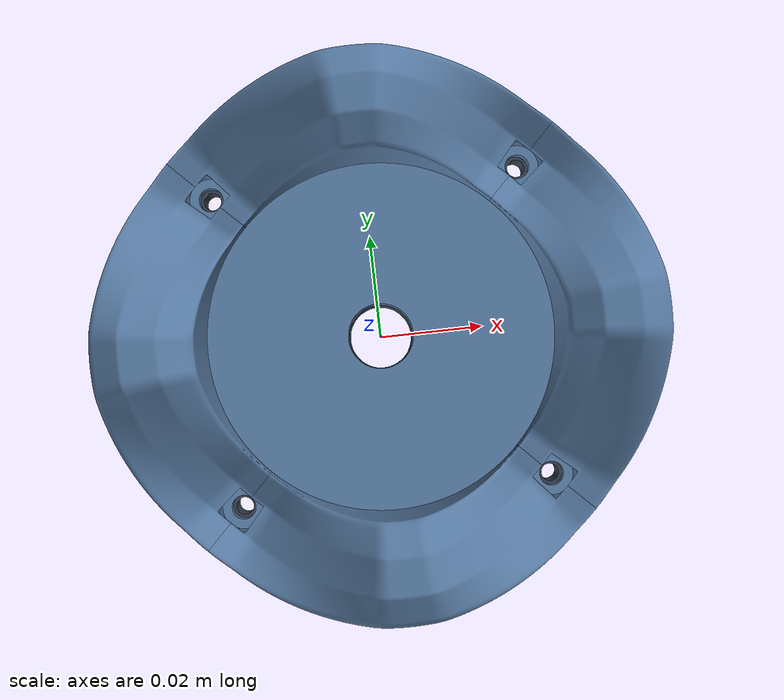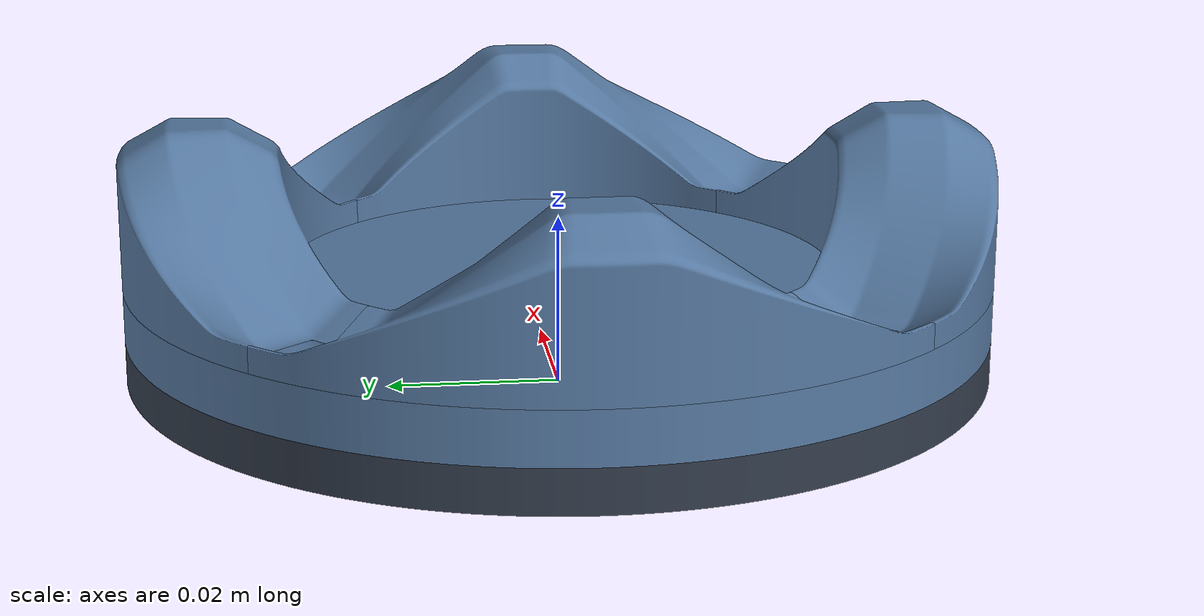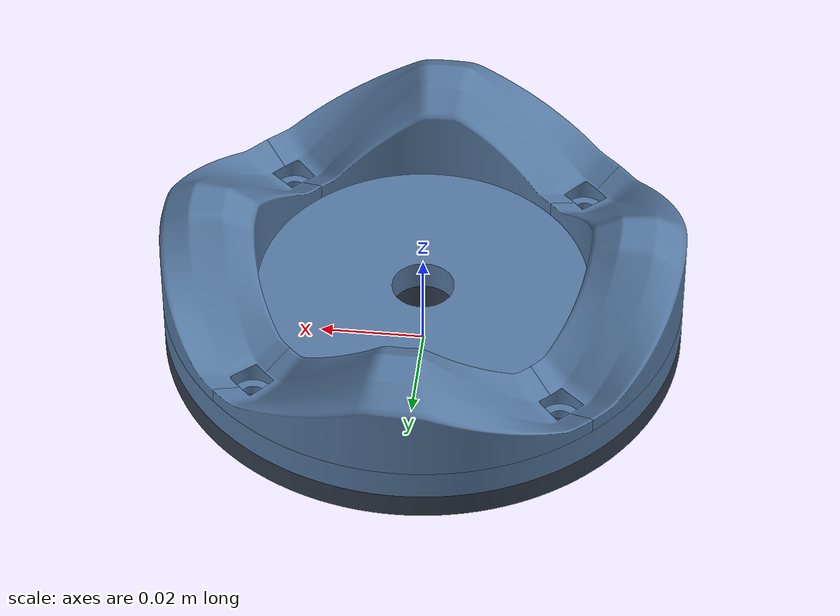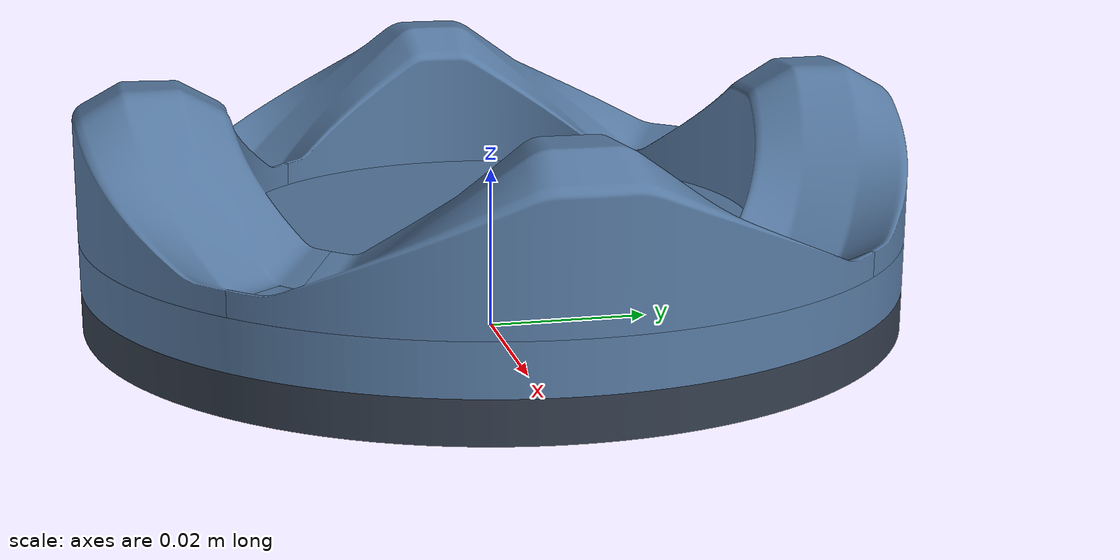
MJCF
<?xml version='1.0' encoding='utf-8'?>
<mujoco model="PetalDock100_guidance_radial_passive">
  <compiler angle="radian" />
  <default>
    <default class="pd_visual">
      <geom contype="0" conaffinity="0" group="2" density="0" />
    </default>
    <default class="pd_collision">
      <geom contype="1" conaffinity="1" group="3" rgba="0.35 0.65 0.85 0.3" condim="3" friction="0.15 0.003 0.0001" margin="0" gap="0" density="0" solref="0.003 1" solimp="0.95 0.99 0.0002" />
    </default>
  </default>
  <asset>
    <material name="pd_dark" rgba=".20 .24 .30 1" specular="0.35" shininess="0.35" />
    <material name="pd_blue" rgba=".34 .48 .64 1" specular="0.35" shininess="0.35" />
    <material name="pd_silver" rgba=".68 .74 .81 1" specular="0.35" shininess="0.35" />
    <mesh name="pd_base_proxy" file="meshes/collision/base_proxy.obj" />
    <mesh name="pd_v_petal_2" file="meshes/visual/petal_2.obj" />
    <mesh name="pd_v_head_plate" file="meshes/visual/head_plate.obj" />
    <mesh name="pd_v_petal_0" file="meshes/visual/petal_0.obj" />
    <mesh name="pd_v_petal_1" file="meshes/visual/petal_1.obj" />
    <mesh name="pd_v_stop_land" file="meshes/visual/stop_land.obj" />
    <mesh name="pd_v_adapter" file="meshes/visual/adapter.obj" />
    <mesh name="pd_v_petal_3" file="meshes/visual/petal_3.obj" />
    <mesh name="pd_guide_0000" file="meshes/collision/guide_0000.obj" />
    <mesh name="pd_guide_0001" file="meshes/collision/guide_0001.obj" />
    <mesh name="pd_guide_0002" file="meshes/collision/guide_0002.obj" />
    <mesh name="pd_guide_0003" file="meshes/collision/guide_0003.obj" />
    <mesh name="pd_guide_0004" file="meshes/collision/guide_0004.obj" />
    <mesh name="pd_guide_0005" file="meshes/collision/guide_0005.obj" />
    <mesh name="pd_guide_0006" file="meshes/collision/guide_0006.obj" />
    <mesh name="pd_guide_0007" file="meshes/collision/guide_0007.obj" />
    <mesh name="pd_guide_0008" file="meshes/collision/guide_0008.obj" />
    <mesh name="pd_guide_0009" file="meshes/collision/guide_0009.obj" />
    <mesh name="pd_guide_0010" file="meshes/collision/guide_0010.obj" />
    <mesh name="pd_guide_0011" file="meshes/collision/guide_0011.obj" />
    <mesh name="pd_guide_0012" file="meshes/collision/guide_0012.obj" />
    <mesh name="pd_guide_0013" file="meshes/collision/guide_0013.obj" />
    <mesh name="pd_guide_0014" file="meshes/collision/guide_0014.obj" />
    <mesh name="pd_guide_0015" file="meshes/collision/guide_0015.obj" />
    <mesh name="pd_guide_0016" file="meshes/collision/guide_0016.obj" />
    <mesh name="pd_guide_0017" file="meshes/collision/guide_0017.obj" />
    <mesh name="pd_guide_0018" file="meshes/collision/guide_0018.obj" />
    <mesh name="pd_guide_0019" file="meshes/collision/guide_0019.obj" />
    <mesh name="pd_guide_0020" file="meshes/collision/guide_0020.obj" />
    <mesh name="pd_guide_0021" file="meshes/collision/guide_0021.obj" />
    <mesh name="pd_guide_0022" file="meshes/collision/guide_0022.obj" />
    <mesh name="pd_guide_0023" file="meshes/collision/guide_0023.obj" />
    <mesh name="pd_guide_0024" file="meshes/collision/guide_0024.obj" />
    <mesh name="pd_guide_0025" file="meshes/collision/guide_0025.obj" />
    <mesh name="pd_guide_0026" file="meshes/collision/guide_0026.obj" />
    <mesh name="pd_guide_0027" file="meshes/collision/guide_0027.obj" />
    <mesh name="pd_guide_0028" file="meshes/collision/guide_0028.obj" />
    <mesh name="pd_guide_0029" file="meshes/collision/guide_0029.obj" />
    <mesh name="pd_guide_0030" file="meshes/collision/guide_0030.obj" />
    <mesh name="pd_guide_0031" file="meshes/collision/guide_0031.obj" />
    <mesh name="pd_guide_0032" file="meshes/collision/guide_0032.obj" />
    <mesh name="pd_guide_0033" file="meshes/collision/guide_0033.obj" />
    <mesh name="pd_guide_0034" file="meshes/collision/guide_0034.obj" />
    <mesh name="pd_guide_0035" file="meshes/collision/guide_0035.obj" />
    <mesh name="pd_guide_0036" file="meshes/collision/guide_0036.obj" />
    <mesh name="pd_guide_0037" file="meshes/collision/guide_0037.obj" />
    <mesh name="pd_guide_0038" file="meshes/collision/guide_0038.obj" />
    <mesh name="pd_guide_0039" file="meshes/collision/guide_0039.obj" />
    <mesh name="pd_guide_0040" file="meshes/collision/guide_0040.obj" />
    <mesh name="pd_guide_0041" file="meshes/collision/guide_0041.obj" />
    <mesh name="pd_guide_0042" file="meshes/collision/guide_0042.obj" />
    <mesh name="pd_guide_0043" file="meshes/collision/guide_0043.obj" />
    <mesh name="pd_guide_0044" file="meshes/collision/guide_0044.obj" />
    <mesh name="pd_guide_0045" file="meshes/collision/guide_0045.obj" />
    <mesh name="pd_guide_0046" file="meshes/collision/guide_0046.obj" />
    <mesh name="pd_guide_0047" file="meshes/collision/guide_0047.obj" />
    <mesh name="pd_guide_0048" file="meshes/collision/guide_0048.obj" />
    <mesh name="pd_guide_0049" file="meshes/collision/guide_0049.obj" />
    <mesh name="pd_guide_0050" file="meshes/collision/guide_0050.obj" />
    <mesh name="pd_guide_0051" file="meshes/collision/guide_0051.obj" />
    <mesh name="pd_guide_0052" file="meshes/collision/guide_0052.obj" />
    <mesh name="pd_guide_0053" file="meshes/collision/guide_0053.obj" />
    <mesh name="pd_guide_0054" file="meshes/collision/guide_0054.obj" />
    <mesh name="pd_guide_0055" file="meshes/collision/guide_0055.obj" />
    <mesh name="pd_guide_0056" file="meshes/collision/guide_0056.obj" />
    <mesh name="pd_guide_0057" file="meshes/collision/guide_0057.obj" />
    <mesh name="pd_guide_0058" file="meshes/collision/guide_0058.obj" />
    <mesh name="pd_guide_0059" file="meshes/collision/guide_0059.obj" />
    <mesh name="pd_guide_0060" file="meshes/collision/guide_0060.obj" />
    <mesh name="pd_guide_0061" file="meshes/collision/guide_0061.obj" />
    <mesh name="pd_guide_0062" file="meshes/collision/guide_0062.obj" />
    <mesh name="pd_guide_0063" file="meshes/collision/guide_0063.obj" />
    <mesh name="pd_guide_0064" file="meshes/collision/guide_0064.obj" />
    <mesh name="pd_guide_0065" file="meshes/collision/guide_0065.obj" />
    <mesh name="pd_guide_0066" file="meshes/collision/guide_0066.obj" />
    <mesh name="pd_guide_0067" file="meshes/collision/guide_0067.obj" />
    <mesh name="pd_guide_0068" file="meshes/collision/guide_0068.obj" />
    <mesh name="pd_guide_0069" file="meshes/collision/guide_0069.obj" />
    <mesh name="pd_guide_0070" file="meshes/collision/guide_0070.obj" />
    <mesh name="pd_guide_0071" file="meshes/collision/guide_0071.obj" />
    <mesh name="pd_guide_0072" file="meshes/collision/guide_0072.obj" />
    <mesh name="pd_guide_0073" file="meshes/collision/guide_0073.obj" />
    <mesh name="pd_guide_0074" file="meshes/collision/guide_0074.obj" />
    <mesh name="pd_guide_0075" file="meshes/collision/guide_0075.obj" />
    <mesh name="pd_guide_0076" file="meshes/collision/guide_0076.obj" />
    <mesh name="pd_guide_0077" file="meshes/collision/guide_0077.obj" />
    <mesh name="pd_guide_0078" file="meshes/collision/guide_0078.obj" />
    <mesh name="pd_guide_0079" file="meshes/collision/guide_0079.obj" />
    <mesh name="pd_guide_0080" file="meshes/collision/guide_0080.obj" />
    <mesh name="pd_guide_0081" file="meshes/collision/guide_0081.obj" />
    <mesh name="pd_guide_0082" file="meshes/collision/guide_0082.obj" />
    <mesh name="pd_guide_0083" file="meshes/collision/guide_0083.obj" />
    <mesh name="pd_guide_0084" file="meshes/collision/guide_0084.obj" />
    <mesh name="pd_guide_0085" file="meshes/collision/guide_0085.obj" />
    <mesh name="pd_guide_0086" file="meshes/collision/guide_0086.obj" />
    <mesh name="pd_guide_0087" file="meshes/collision/guide_0087.obj" />
    <mesh name="pd_guide_0088" file="meshes/collision/guide_0088.obj" />
    <mesh name="pd_guide_0089" file="meshes/collision/guide_0089.obj" />
    <mesh name="pd_guide_0090" file="meshes/collision/guide_0090.obj" />
    <mesh name="pd_guide_0091" file="meshes/collision/guide_0091.obj" />
    <mesh name="pd_guide_0092" file="meshes/collision/guide_0092.obj" />
    <mesh name="pd_guide_0093" file="meshes/collision/guide_0093.obj" />
    <mesh name="pd_guide_0094" file="meshes/collision/guide_0094.obj" />
    <mesh name="pd_guide_0095" file="meshes/collision/guide_0095.obj" />
    <mesh name="pd_guide_0096" file="meshes/collision/guide_0096.obj" />
    <mesh name="pd_guide_0097" file="meshes/collision/guide_0097.obj" />
    <mesh name="pd_guide_0098" file="meshes/collision/guide_0098.obj" />
    <mesh name="pd_guide_0099" file="meshes/collision/guide_0099.obj" />
    <mesh name="pd_guide_0100" file="meshes/collision/guide_0100.obj" />
    <mesh name="pd_guide_0101" file="meshes/collision/guide_0101.obj" />
    <mesh name="pd_guide_0102" file="meshes/collision/guide_0102.obj" />
    <mesh name="pd_guide_0103" file="meshes/collision/guide_0103.obj" />
    <mesh name="pd_guide_0104" file="meshes/collision/guide_0104.obj" />
    <mesh name="pd_guide_0105" file="meshes/collision/guide_0105.obj" />
    <mesh name="pd_guide_0106" file="meshes/collision/guide_0106.obj" />
    <mesh name="pd_guide_0107" file="meshes/collision/guide_0107.obj" />
    <mesh name="pd_guide_0108" file="meshes/collision/guide_0108.obj" />
    <mesh name="pd_guide_0109" file="meshes/collision/guide_0109.obj" />
    <mesh name="pd_guide_0110" file="meshes/collision/guide_0110.obj" />
    <mesh name="pd_guide_0111" file="meshes/collision/guide_0111.obj" />
    <mesh name="pd_guide_0112" file="meshes/collision/guide_0112.obj" />
    <mesh name="pd_guide_0113" file="meshes/collision/guide_0113.obj" />
    <mesh name="pd_guide_0114" file="meshes/collision/guide_0114.obj" />
    <mesh name="pd_guide_0115" file="meshes/collision/guide_0115.obj" />
    <mesh name="pd_guide_0116" file="meshes/collision/guide_0116.obj" />
    <mesh name="pd_guide_0117" file="meshes/collision/guide_0117.obj" />
    <mesh name="pd_guide_0118" file="meshes/collision/guide_0118.obj" />
    <mesh name="pd_guide_0119" file="meshes/collision/guide_0119.obj" />
    <mesh name="pd_guide_0120" file="meshes/collision/guide_0120.obj" />
    <mesh name="pd_guide_0121" file="meshes/collision/guide_0121.obj" />
    <mesh name="pd_guide_0122" file="meshes/collision/guide_0122.obj" />
    <mesh name="pd_guide_0123" file="meshes/collision/guide_0123.obj" />
    <mesh name="pd_guide_0124" file="meshes/collision/guide_0124.obj" />
    <mesh name="pd_guide_0125" file="meshes/collision/guide_0125.obj" />
    <mesh name="pd_guide_0126" file="meshes/collision/guide_0126.obj" />
    <mesh name="pd_guide_0127" file="meshes/collision/guide_0127.obj" />
    <mesh name="pd_guide_0128" file="meshes/collision/guide_0128.obj" />
    <mesh name="pd_guide_0129" file="meshes/collision/guide_0129.obj" />
    <mesh name="pd_guide_0130" file="meshes/collision/guide_0130.obj" />
    <mesh name="pd_guide_0131" file="meshes/collision/guide_0131.obj" />
    <mesh name="pd_guide_0132" file="meshes/collision/guide_0132.obj" />
    <mesh name="pd_guide_0133" file="meshes/collision/guide_0133.obj" />
    <mesh name="pd_guide_0134" file="meshes/collision/guide_0134.obj" />
    <mesh name="pd_guide_0135" file="meshes/collision/guide_0135.obj" />
    <mesh name="pd_guide_0136" file="meshes/collision/guide_0136.obj" />
    <mesh name="pd_guide_0137" file="meshes/collision/guide_0137.obj" />
    <mesh name="pd_guide_0138" file="meshes/collision/guide_0138.obj" />
    <mesh name="pd_guide_0139" file="meshes/collision/guide_0139.obj" />
    <mesh name="pd_guide_0140" file="meshes/collision/guide_0140.obj" />
    <mesh name="pd_guide_0141" file="meshes/collision/guide_0141.obj" />
    <mesh name="pd_guide_0142" file="meshes/collision/guide_0142.obj" />
    <mesh name="pd_guide_0143" file="meshes/collision/guide_0143.obj" />
    <mesh name="pd_guide_0144" file="meshes/collision/guide_0144.obj" />
    <mesh name="pd_guide_0145" file="meshes/collision/guide_0145.obj" />
    <mesh name="pd_guide_0146" file="meshes/collision/guide_0146.obj" />
    <mesh name="pd_guide_0147" file="meshes/collision/guide_0147.obj" />
    <mesh name="pd_guide_0148" file="meshes/collision/guide_0148.obj" />
    <mesh name="pd_guide_0149" file="meshes/collision/guide_0149.obj" />
    <mesh name="pd_guide_0150" file="meshes/collision/guide_0150.obj" />
    <mesh name="pd_guide_0151" file="meshes/collision/guide_0151.obj" />
    <mesh name="pd_guide_0152" file="meshes/collision/guide_0152.obj" />
    <mesh name="pd_guide_0153" file="meshes/collision/guide_0153.obj" />
    <mesh name="pd_guide_0154" file="meshes/collision/guide_0154.obj" />
    <mesh name="pd_guide_0155" file="meshes/collision/guide_0155.obj" />
    <mesh name="pd_guide_0156" file="meshes/collision/guide_0156.obj" />
    <mesh name="pd_guide_0157" file="meshes/collision/guide_0157.obj" />
    <mesh name="pd_guide_0158" file="meshes/collision/guide_0158.obj" />
    <mesh name="pd_guide_0159" file="meshes/collision/guide_0159.obj" />
    <mesh name="pd_guide_0160" file="meshes/collision/guide_0160.obj" />
    <mesh name="pd_guide_0161" file="meshes/collision/guide_0161.obj" />
    <mesh name="pd_guide_0162" file="meshes/collision/guide_0162.obj" />
    <mesh name="pd_guide_0163" file="meshes/collision/guide_0163.obj" />
    <mesh name="pd_guide_0164" file="meshes/collision/guide_0164.obj" />
    <mesh name="pd_guide_0165" file="meshes/collision/guide_0165.obj" />
    <mesh name="pd_guide_0166" file="meshes/collision/guide_0166.obj" />
    <mesh name="pd_guide_0167" file="meshes/collision/guide_0167.obj" />
    <mesh name="pd_guide_0168" file="meshes/collision/guide_0168.obj" />
    <mesh name="pd_guide_0169" file="meshes/collision/guide_0169.obj" />
    <mesh name="pd_guide_0170" file="meshes/collision/guide_0170.obj" />
    <mesh name="pd_guide_0171" file="meshes/collision/guide_0171.obj" />
    <mesh name="pd_guide_0172" file="meshes/collision/guide_0172.obj" />
    <mesh name="pd_guide_0173" file="meshes/collision/guide_0173.obj" />
    <mesh name="pd_guide_0174" file="meshes/collision/guide_0174.obj" />
    <mesh name="pd_guide_0175" file="meshes/collision/guide_0175.obj" />
    <mesh name="pd_guide_0176" file="meshes/collision/guide_0176.obj" />
    <mesh name="pd_guide_0177" file="meshes/collision/guide_0177.obj" />
    <mesh name="pd_guide_0178" file="meshes/collision/guide_0178.obj" />
    <mesh name="pd_guide_0179" file="meshes/collision/guide_0179.obj" />
    <mesh name="pd_guide_0180" file="meshes/collision/guide_0180.obj" />
    <mesh name="pd_guide_0181" file="meshes/collision/guide_0181.obj" />
    <mesh name="pd_guide_0182" file="meshes/collision/guide_0182.obj" />
    <mesh name="pd_guide_0183" file="meshes/collision/guide_0183.obj" />
    <mesh name="pd_guide_0184" file="meshes/collision/guide_0184.obj" />
    <mesh name="pd_guide_0185" file="meshes/collision/guide_0185.obj" />
    <mesh name="pd_guide_0186" file="meshes/collision/guide_0186.obj" />
    <mesh name="pd_guide_0187" file="meshes/collision/guide_0187.obj" />
    <mesh name="pd_guide_0188" file="meshes/collision/guide_0188.obj" />
    <mesh name="pd_guide_0189" file="meshes/collision/guide_0189.obj" />
    <mesh name="pd_guide_0190" file="meshes/collision/guide_0190.obj" />
    <mesh name="pd_guide_0191" file="meshes/collision/guide_0191.obj" />
    <mesh name="pd_guide_0192" file="meshes/collision/guide_0192.obj" />
    <mesh name="pd_guide_0193" file="meshes/collision/guide_0193.obj" />
    <mesh name="pd_guide_0194" file="meshes/collision/guide_0194.obj" />
    <mesh name="pd_guide_0195" file="meshes/collision/guide_0195.obj" />
    <mesh name="pd_guide_0196" file="meshes/collision/guide_0196.obj" />
    <mesh name="pd_guide_0197" file="meshes/collision/guide_0197.obj" />
    <mesh name="pd_guide_0198" file="meshes/collision/guide_0198.obj" />
    <mesh name="pd_guide_0199" file="meshes/collision/guide_0199.obj" />
    <mesh name="pd_guide_0200" file="meshes/collision/guide_0200.obj" />
    <mesh name="pd_guide_0201" file="meshes/collision/guide_0201.obj" />
    <mesh name="pd_guide_0202" file="meshes/collision/guide_0202.obj" />
    <mesh name="pd_guide_0203" file="meshes/collision/guide_0203.obj" />
    <mesh name="pd_guide_0204" file="meshes/collision/guide_0204.obj" />
    <mesh name="pd_guide_0205" file="meshes/collision/guide_0205.obj" />
    <mesh name="pd_guide_0206" file="meshes/collision/guide_0206.obj" />
    <mesh name="pd_guide_0207" file="meshes/collision/guide_0207.obj" />
    <mesh name="pd_guide_0208" file="meshes/collision/guide_0208.obj" />
    <mesh name="pd_guide_0209" file="meshes/collision/guide_0209.obj" />
    <mesh name="pd_guide_0210" file="meshes/collision/guide_0210.obj" />
    <mesh name="pd_guide_0211" file="meshes/collision/guide_0211.obj" />
    <mesh name="pd_guide_0212" file="meshes/collision/guide_0212.obj" />
    <mesh name="pd_guide_0213" file="meshes/collision/guide_0213.obj" />
    <mesh name="pd_guide_0214" file="meshes/collision/guide_0214.obj" />
    <mesh name="pd_guide_0215" file="meshes/collision/guide_0215.obj" />
    <mesh name="pd_guide_0216" file="meshes/collision/guide_0216.obj" />
    <mesh name="pd_guide_0217" file="meshes/collision/guide_0217.obj" />
    <mesh name="pd_guide_0218" file="meshes/collision/guide_0218.obj" />
    <mesh name="pd_guide_0219" file="meshes/collision/guide_0219.obj" />
    <mesh name="pd_guide_0220" file="meshes/collision/guide_0220.obj" />
    <mesh name="pd_guide_0221" file="meshes/collision/guide_0221.obj" />
    <mesh name="pd_guide_0222" file="meshes/collision/guide_0222.obj" />
    <mesh name="pd_guide_0223" file="meshes/collision/guide_0223.obj" />
    <mesh name="pd_guide_0224" file="meshes/collision/guide_0224.obj" />
    <mesh name="pd_guide_0225" file="meshes/collision/guide_0225.obj" />
    <mesh name="pd_guide_0226" file="meshes/collision/guide_0226.obj" />
    <mesh name="pd_guide_0227" file="meshes/collision/guide_0227.obj" />
    <mesh name="pd_guide_0228" file="meshes/collision/guide_0228.obj" />
    <mesh name="pd_guide_0229" file="meshes/collision/guide_0229.obj" />
    <mesh name="pd_guide_0230" file="meshes/collision/guide_0230.obj" />
    <mesh name="pd_guide_0231" file="meshes/collision/guide_0231.obj" />
    <mesh name="pd_guide_0232" file="meshes/collision/guide_0232.obj" />
    <mesh name="pd_guide_0233" file="meshes/collision/guide_0233.obj" />
    <mesh name="pd_guide_0234" file="meshes/collision/guide_0234.obj" />
    <mesh name="pd_guide_0235" file="meshes/collision/guide_0235.obj" />
    <mesh name="pd_guide_0236" file="meshes/collision/guide_0236.obj" />
    <mesh name="pd_guide_0237" file="meshes/collision/guide_0237.obj" />
    <mesh name="pd_guide_0238" file="meshes/collision/guide_0238.obj" />
    <mesh name="pd_guide_0239" file="meshes/collision/guide_0239.obj" />
    <mesh name="pd_guide_0240" file="meshes/collision/guide_0240.obj" />
    <mesh name="pd_guide_0241" file="meshes/collision/guide_0241.obj" />
    <mesh name="pd_guide_0242" file="meshes/collision/guide_0242.obj" />
    <mesh name="pd_guide_0243" file="meshes/collision/guide_0243.obj" />
    <mesh name="pd_guide_0244" file="meshes/collision/guide_0244.obj" />
    <mesh name="pd_guide_0245" file="meshes/collision/guide_0245.obj" />
    <mesh name="pd_guide_0246" file="meshes/collision/guide_0246.obj" />
    <mesh name="pd_guide_0247" file="meshes/collision/guide_0247.obj" />
    <mesh name="pd_guide_0248" file="meshes/collision/guide_0248.obj" />
    <mesh name="pd_guide_0249" file="meshes/collision/guide_0249.obj" />
    <mesh name="pd_guide_0250" file="meshes/collision/guide_0250.obj" />
    <mesh name="pd_guide_0251" file="meshes/collision/guide_0251.obj" />
    <mesh name="pd_guide_0252" file="meshes/collision/guide_0252.obj" />
    <mesh name="pd_guide_0253" file="meshes/collision/guide_0253.obj" />
    <mesh name="pd_guide_0254" file="meshes/collision/guide_0254.obj" />
    <mesh name="pd_guide_0255" file="meshes/collision/guide_0255.obj" />
    <mesh name="pd_guide_0256" file="meshes/collision/guide_0256.obj" />
    <mesh name="pd_guide_0257" file="meshes/collision/guide_0257.obj" />
    <mesh name="pd_guide_0258" file="meshes/collision/guide_0258.obj" />
    <mesh name="pd_guide_0259" file="meshes/collision/guide_0259.obj" />
    <mesh name="pd_guide_0260" file="meshes/collision/guide_0260.obj" />
    <mesh name="pd_guide_0261" file="meshes/collision/guide_0261.obj" />
    <mesh name="pd_guide_0262" file="meshes/collision/guide_0262.obj" />
    <mesh name="pd_guide_0263" file="meshes/collision/guide_0263.obj" />
    <mesh name="pd_guide_0264" file="meshes/collision/guide_0264.obj" />
    <mesh name="pd_guide_0265" file="meshes/collision/guide_0265.obj" />
    <mesh name="pd_guide_0266" file="meshes/collision/guide_0266.obj" />
    <mesh name="pd_guide_0267" file="meshes/collision/guide_0267.obj" />
    <mesh name="pd_guide_0268" file="meshes/collision/guide_0268.obj" />
    <mesh name="pd_guide_0269" file="meshes/collision/guide_0269.obj" />
    <mesh name="pd_guide_0270" file="meshes/collision/guide_0270.obj" />
    <mesh name="pd_guide_0271" file="meshes/collision/guide_0271.obj" />
    <mesh name="pd_guide_0272" file="meshes/collision/guide_0272.obj" />
    <mesh name="pd_guide_0273" file="meshes/collision/guide_0273.obj" />
    <mesh name="pd_guide_0274" file="meshes/collision/guide_0274.obj" />
    <mesh name="pd_guide_0275" file="meshes/collision/guide_0275.obj" />
    <mesh name="pd_guide_0276" file="meshes/collision/guide_0276.obj" />
    <mesh name="pd_guide_0277" file="meshes/collision/guide_0277.obj" />
    <mesh name="pd_guide_0278" file="meshes/collision/guide_0278.obj" />
    <mesh name="pd_guide_0279" file="meshes/collision/guide_0279.obj" />
    <mesh name="pd_guide_0280" file="meshes/collision/guide_0280.obj" />
    <mesh name="pd_guide_0281" file="meshes/collision/guide_0281.obj" />
    <mesh name="pd_guide_0282" file="meshes/collision/guide_0282.obj" />
    <mesh name="pd_guide_0283" file="meshes/collision/guide_0283.obj" />
    <mesh name="pd_guide_0284" file="meshes/collision/guide_0284.obj" />
    <mesh name="pd_guide_0285" file="meshes/collision/guide_0285.obj" />
    <mesh name="pd_guide_0286" file="meshes/collision/guide_0286.obj" />
    <mesh name="pd_guide_0287" file="meshes/collision/guide_0287.obj" />
    <mesh name="pd_guide_0288" file="meshes/collision/guide_0288.obj" />
    <mesh name="pd_guide_0289" file="meshes/collision/guide_0289.obj" />
    <mesh name="pd_guide_0290" file="meshes/collision/guide_0290.obj" />
    <mesh name="pd_guide_0291" file="meshes/collision/guide_0291.obj" />
    <mesh name="pd_guide_0292" file="meshes/collision/guide_0292.obj" />
    <mesh name="pd_guide_0293" file="meshes/collision/guide_0293.obj" />
    <mesh name="pd_guide_0294" file="meshes/collision/guide_0294.obj" />
    <mesh name="pd_guide_0295" file="meshes/collision/guide_0295.obj" />
    <mesh name="pd_guide_0296" file="meshes/collision/guide_0296.obj" />
    <mesh name="pd_guide_0297" file="meshes/collision/guide_0297.obj" />
    <mesh name="pd_guide_0298" file="meshes/collision/guide_0298.obj" />
    <mesh name="pd_guide_0299" file="meshes/collision/guide_0299.obj" />
    <mesh name="pd_guide_0300" file="meshes/collision/guide_0300.obj" />
    <mesh name="pd_guide_0301" file="meshes/collision/guide_0301.obj" />
    <mesh name="pd_guide_0302" file="meshes/collision/guide_0302.obj" />
    <mesh name="pd_guide_0303" file="meshes/collision/guide_0303.obj" />
    <mesh name="pd_guide_0304" file="meshes/collision/guide_0304.obj" />
    <mesh name="pd_guide_0305" file="meshes/collision/guide_0305.obj" />
    <mesh name="pd_guide_0306" file="meshes/collision/guide_0306.obj" />
    <mesh name="pd_guide_0307" file="meshes/collision/guide_0307.obj" />
    <mesh name="pd_guide_0308" file="meshes/collision/guide_0308.obj" />
    <mesh name="pd_guide_0309" file="meshes/collision/guide_0309.obj" />
    <mesh name="pd_guide_0310" file="meshes/collision/guide_0310.obj" />
    <mesh name="pd_guide_0311" file="meshes/collision/guide_0311.obj" />
    <mesh name="pd_guide_0312" file="meshes/collision/guide_0312.obj" />
    <mesh name="pd_guide_0313" file="meshes/collision/guide_0313.obj" />
    <mesh name="pd_guide_0314" file="meshes/collision/guide_0314.obj" />
    <mesh name="pd_guide_0315" file="meshes/collision/guide_0315.obj" />
    <mesh name="pd_guide_0316" file="meshes/collision/guide_0316.obj" />
    <mesh name="pd_guide_0317" file="meshes/collision/guide_0317.obj" />
    <mesh name="pd_guide_0318" file="meshes/collision/guide_0318.obj" />
    <mesh name="pd_guide_0319" file="meshes/collision/guide_0319.obj" />
    <mesh name="pd_guide_0320" file="meshes/collision/guide_0320.obj" />
    <mesh name="pd_guide_0321" file="meshes/collision/guide_0321.obj" />
    <mesh name="pd_guide_0322" file="meshes/collision/guide_0322.obj" />
    <mesh name="pd_guide_0323" file="meshes/collision/guide_0323.obj" />
    <mesh name="pd_guide_0324" file="meshes/collision/guide_0324.obj" />
    <mesh name="pd_guide_0325" file="meshes/collision/guide_0325.obj" />
    <mesh name="pd_guide_0326" file="meshes/collision/guide_0326.obj" />
    <mesh name="pd_guide_0327" file="meshes/collision/guide_0327.obj" />
    <mesh name="pd_guide_0328" file="meshes/collision/guide_0328.obj" />
    <mesh name="pd_guide_0329" file="meshes/collision/guide_0329.obj" />
    <mesh name="pd_guide_0330" file="meshes/collision/guide_0330.obj" />
    <mesh name="pd_guide_0331" file="meshes/collision/guide_0331.obj" />
    <mesh name="pd_guide_0332" file="meshes/collision/guide_0332.obj" />
    <mesh name="pd_guide_0333" file="meshes/collision/guide_0333.obj" />
    <mesh name="pd_guide_0334" file="meshes/collision/guide_0334.obj" />
    <mesh name="pd_guide_0335" file="meshes/collision/guide_0335.obj" />
    <mesh name="pd_guide_0336" file="meshes/collision/guide_0336.obj" />
    <mesh name="pd_guide_0337" file="meshes/collision/guide_0337.obj" />
    <mesh name="pd_guide_0338" file="meshes/collision/guide_0338.obj" />
    <mesh name="pd_guide_0339" file="meshes/collision/guide_0339.obj" />
    <mesh name="pd_guide_0340" file="meshes/collision/guide_0340.obj" />
    <mesh name="pd_guide_0341" file="meshes/collision/guide_0341.obj" />
    <mesh name="pd_guide_0342" file="meshes/collision/guide_0342.obj" />
    <mesh name="pd_guide_0343" file="meshes/collision/guide_0343.obj" />
    <mesh name="pd_guide_0344" file="meshes/collision/guide_0344.obj" />
    <mesh name="pd_guide_0345" file="meshes/collision/guide_0345.obj" />
    <mesh name="pd_guide_0346" file="meshes/collision/guide_0346.obj" />
    <mesh name="pd_guide_0347" file="meshes/collision/guide_0347.obj" />
    <mesh name="pd_guide_0348" file="meshes/collision/guide_0348.obj" />
    <mesh name="pd_guide_0349" file="meshes/collision/guide_0349.obj" />
    <mesh name="pd_guide_0350" file="meshes/collision/guide_0350.obj" />
    <mesh name="pd_guide_0351" file="meshes/collision/guide_0351.obj" />
    <mesh name="pd_guide_0352" file="meshes/collision/guide_0352.obj" />
    <mesh name="pd_guide_0353" file="meshes/collision/guide_0353.obj" />
    <mesh name="pd_guide_0354" file="meshes/collision/guide_0354.obj" />
    <mesh name="pd_guide_0355" file="meshes/collision/guide_0355.obj" />
    <mesh name="pd_guide_0356" file="meshes/collision/guide_0356.obj" />
    <mesh name="pd_guide_0357" file="meshes/collision/guide_0357.obj" />
    <mesh name="pd_guide_0358" file="meshes/collision/guide_0358.obj" />
    <mesh name="pd_guide_0359" file="meshes/collision/guide_0359.obj" />
    <mesh name="pd_guide_0360" file="meshes/collision/guide_0360.obj" />
    <mesh name="pd_guide_0361" file="meshes/collision/guide_0361.obj" />
    <mesh name="pd_guide_0362" file="meshes/collision/guide_0362.obj" />
    <mesh name="pd_guide_0363" file="meshes/collision/guide_0363.obj" />
    <mesh name="pd_guide_0364" file="meshes/collision/guide_0364.obj" />
    <mesh name="pd_guide_0365" file="meshes/collision/guide_0365.obj" />
    <mesh name="pd_guide_0366" file="meshes/collision/guide_0366.obj" />
    <mesh name="pd_guide_0367" file="meshes/collision/guide_0367.obj" />
    <mesh name="pd_guide_0368" file="meshes/collision/guide_0368.obj" />
    <mesh name="pd_guide_0369" file="meshes/collision/guide_0369.obj" />
    <mesh name="pd_guide_0370" file="meshes/collision/guide_0370.obj" />
    <mesh name="pd_guide_0371" file="meshes/collision/guide_0371.obj" />
    <mesh name="pd_guide_0372" file="meshes/collision/guide_0372.obj" />
    <mesh name="pd_guide_0373" file="meshes/collision/guide_0373.obj" />
    <mesh name="pd_guide_0374" file="meshes/collision/guide_0374.obj" />
    <mesh name="pd_guide_0375" file="meshes/collision/guide_0375.obj" />
    <mesh name="pd_guide_0376" file="meshes/collision/guide_0376.obj" />
    <mesh name="pd_guide_0377" file="meshes/collision/guide_0377.obj" />
    <mesh name="pd_guide_0378" file="meshes/collision/guide_0378.obj" />
    <mesh name="pd_guide_0379" file="meshes/collision/guide_0379.obj" />
    <mesh name="pd_guide_0380" file="meshes/collision/guide_0380.obj" />
    <mesh name="pd_guide_0381" file="meshes/collision/guide_0381.obj" />
    <mesh name="pd_guide_0382" file="meshes/collision/guide_0382.obj" />
    <mesh name="pd_guide_0383" file="meshes/collision/guide_0383.obj" />
    <mesh name="pd_guide_0384" file="meshes/collision/guide_0384.obj" />
    <mesh name="pd_guide_0385" file="meshes/collision/guide_0385.obj" />
    <mesh name="pd_guide_0386" file="meshes/collision/guide_0386.obj" />
    <mesh name="pd_guide_0387" file="meshes/collision/guide_0387.obj" />
    <mesh name="pd_guide_0388" file="meshes/collision/guide_0388.obj" />
    <mesh name="pd_guide_0389" file="meshes/collision/guide_0389.obj" />
    <mesh name="pd_guide_0390" file="meshes/collision/guide_0390.obj" />
    <mesh name="pd_guide_0391" file="meshes/collision/guide_0391.obj" />
    <mesh name="pd_guide_0392" file="meshes/collision/guide_0392.obj" />
    <mesh name="pd_guide_0393" file="meshes/collision/guide_0393.obj" />
    <mesh name="pd_guide_0394" file="meshes/collision/guide_0394.obj" />
    <mesh name="pd_guide_0395" file="meshes/collision/guide_0395.obj" />
    <mesh name="pd_guide_0396" file="meshes/collision/guide_0396.obj" />
    <mesh name="pd_guide_0397" file="meshes/collision/guide_0397.obj" />
    <mesh name="pd_guide_0398" file="meshes/collision/guide_0398.obj" />
    <mesh name="pd_guide_0399" file="meshes/collision/guide_0399.obj" />
    <mesh name="pd_guide_0400" file="meshes/collision/guide_0400.obj" />
    <mesh name="pd_guide_0401" file="meshes/collision/guide_0401.obj" />
    <mesh name="pd_guide_0402" file="meshes/collision/guide_0402.obj" />
    <mesh name="pd_guide_0403" file="meshes/collision/guide_0403.obj" />
    <mesh name="pd_guide_0404" file="meshes/collision/guide_0404.obj" />
    <mesh name="pd_guide_0405" file="meshes/collision/guide_0405.obj" />
    <mesh name="pd_guide_0406" file="meshes/collision/guide_0406.obj" />
    <mesh name="pd_guide_0407" file="meshes/collision/guide_0407.obj" />
    <mesh name="pd_guide_0408" file="meshes/collision/guide_0408.obj" />
    <mesh name="pd_guide_0409" file="meshes/collision/guide_0409.obj" />
    <mesh name="pd_guide_0410" file="meshes/collision/guide_0410.obj" />
    <mesh name="pd_guide_0411" file="meshes/collision/guide_0411.obj" />
    <mesh name="pd_guide_0412" file="meshes/collision/guide_0412.obj" />
    <mesh name="pd_guide_0413" file="meshes/collision/guide_0413.obj" />
    <mesh name="pd_guide_0414" file="meshes/collision/guide_0414.obj" />
    <mesh name="pd_guide_0415" file="meshes/collision/guide_0415.obj" />
    <mesh name="pd_guide_0416" file="meshes/collision/guide_0416.obj" />
    <mesh name="pd_guide_0417" file="meshes/collision/guide_0417.obj" />
    <mesh name="pd_guide_0418" file="meshes/collision/guide_0418.obj" />
    <mesh name="pd_guide_0419" file="meshes/collision/guide_0419.obj" />
    <mesh name="pd_guide_0420" file="meshes/collision/guide_0420.obj" />
    <mesh name="pd_guide_0421" file="meshes/collision/guide_0421.obj" />
    <mesh name="pd_guide_0422" file="meshes/collision/guide_0422.obj" />
    <mesh name="pd_guide_0423" file="meshes/collision/guide_0423.obj" />
    <mesh name="pd_guide_0424" file="meshes/collision/guide_0424.obj" />
    <mesh name="pd_guide_0425" file="meshes/collision/guide_0425.obj" />
    <mesh name="pd_guide_0426" file="meshes/collision/guide_0426.obj" />
    <mesh name="pd_guide_0427" file="meshes/collision/guide_0427.obj" />
    <mesh name="pd_guide_0428" file="meshes/collision/guide_0428.obj" />
    <mesh name="pd_guide_0429" file="meshes/collision/guide_0429.obj" />
    <mesh name="pd_guide_0430" file="meshes/collision/guide_0430.obj" />
    <mesh name="pd_guide_0431" file="meshes/collision/guide_0431.obj" />
    <mesh name="pd_guide_0432" file="meshes/collision/guide_0432.obj" />
    <mesh name="pd_guide_0433" file="meshes/collision/guide_0433.obj" />
    <mesh name="pd_guide_0434" file="meshes/collision/guide_0434.obj" />
    <mesh name="pd_guide_0435" file="meshes/collision/guide_0435.obj" />
    <mesh name="pd_guide_0436" file="meshes/collision/guide_0436.obj" />
    <mesh name="pd_guide_0437" file="meshes/collision/guide_0437.obj" />
    <mesh name="pd_guide_0438" file="meshes/collision/guide_0438.obj" />
    <mesh name="pd_guide_0439" file="meshes/collision/guide_0439.obj" />
    <mesh name="pd_guide_0440" file="meshes/collision/guide_0440.obj" />
    <mesh name="pd_guide_0441" file="meshes/collision/guide_0441.obj" />
    <mesh name="pd_guide_0442" file="meshes/collision/guide_0442.obj" />
    <mesh name="pd_guide_0443" file="meshes/collision/guide_0443.obj" />
    <mesh name="pd_guide_0444" file="meshes/collision/guide_0444.obj" />
    <mesh name="pd_guide_0445" file="meshes/collision/guide_0445.obj" />
    <mesh name="pd_guide_0446" file="meshes/collision/guide_0446.obj" />
    <mesh name="pd_guide_0447" file="meshes/collision/guide_0447.obj" />
    <mesh name="pd_guide_0448" file="meshes/collision/guide_0448.obj" />
    <mesh name="pd_guide_0449" file="meshes/collision/guide_0449.obj" />
    <mesh name="pd_guide_0450" file="meshes/collision/guide_0450.obj" />
    <mesh name="pd_guide_0451" file="meshes/collision/guide_0451.obj" />
    <mesh name="pd_guide_0452" file="meshes/collision/guide_0452.obj" />
    <mesh name="pd_guide_0453" file="meshes/collision/guide_0453.obj" />
    <mesh name="pd_guide_0454" file="meshes/collision/guide_0454.obj" />
    <mesh name="pd_guide_0455" file="meshes/collision/guide_0455.obj" />
    <mesh name="pd_guide_0456" file="meshes/collision/guide_0456.obj" />
    <mesh name="pd_guide_0457" file="meshes/collision/guide_0457.obj" />
    <mesh name="pd_guide_0458" file="meshes/collision/guide_0458.obj" />
    <mesh name="pd_guide_0459" file="meshes/collision/guide_0459.obj" />
    <mesh name="pd_guide_0460" file="meshes/collision/guide_0460.obj" />
    <mesh name="pd_guide_0461" file="meshes/collision/guide_0461.obj" />
    <mesh name="pd_guide_0462" file="meshes/collision/guide_0462.obj" />
    <mesh name="pd_guide_0463" file="meshes/collision/guide_0463.obj" />
    <mesh name="pd_guide_0464" file="meshes/collision/guide_0464.obj" />
    <mesh name="pd_guide_0465" file="meshes/collision/guide_0465.obj" />
    <mesh name="pd_guide_0466" file="meshes/collision/guide_0466.obj" />
    <mesh name="pd_guide_0467" file="meshes/collision/guide_0467.obj" />
    <mesh name="pd_guide_0468" file="meshes/collision/guide_0468.obj" />
    <mesh name="pd_guide_0469" file="meshes/collision/guide_0469.obj" />
    <mesh name="pd_guide_0470" file="meshes/collision/guide_0470.obj" />
    <mesh name="pd_guide_0471" file="meshes/collision/guide_0471.obj" />
    <mesh name="pd_guide_0472" file="meshes/collision/guide_0472.obj" />
    <mesh name="pd_guide_0473" file="meshes/collision/guide_0473.obj" />
    <mesh name="pd_guide_0474" file="meshes/collision/guide_0474.obj" />
    <mesh name="pd_guide_0475" file="meshes/collision/guide_0475.obj" />
    <mesh name="pd_guide_0476" file="meshes/collision/guide_0476.obj" />
    <mesh name="pd_guide_0477" file="meshes/collision/guide_0477.obj" />
    <mesh name="pd_guide_0478" file="meshes/collision/guide_0478.obj" />
    <mesh name="pd_guide_0479" file="meshes/collision/guide_0479.obj" />
    <mesh name="pd_guide_0480" file="meshes/collision/guide_0480.obj" />
    <mesh name="pd_guide_0481" file="meshes/collision/guide_0481.obj" />
    <mesh name="pd_guide_0482" file="meshes/collision/guide_0482.obj" />
    <mesh name="pd_guide_0483" file="meshes/collision/guide_0483.obj" />
    <mesh name="pd_guide_0484" file="meshes/collision/guide_0484.obj" />
    <mesh name="pd_guide_0485" file="meshes/collision/guide_0485.obj" />
    <mesh name="pd_guide_0486" file="meshes/collision/guide_0486.obj" />
    <mesh name="pd_guide_0487" file="meshes/collision/guide_0487.obj" />
    <mesh name="pd_guide_0488" file="meshes/collision/guide_0488.obj" />
    <mesh name="pd_guide_0489" file="meshes/collision/guide_0489.obj" />
    <mesh name="pd_guide_0490" file="meshes/collision/guide_0490.obj" />
    <mesh name="pd_guide_0491" file="meshes/collision/guide_0491.obj" />
    <mesh name="pd_guide_0492" file="meshes/collision/guide_0492.obj" />
    <mesh name="pd_guide_0493" file="meshes/collision/guide_0493.obj" />
    <mesh name="pd_guide_0494" file="meshes/collision/guide_0494.obj" />
    <mesh name="pd_guide_0495" file="meshes/collision/guide_0495.obj" />
    <mesh name="pd_guide_0496" file="meshes/collision/guide_0496.obj" />
    <mesh name="pd_guide_0497" file="meshes/collision/guide_0497.obj" />
    <mesh name="pd_guide_0498" file="meshes/collision/guide_0498.obj" />
    <mesh name="pd_guide_0499" file="meshes/collision/guide_0499.obj" />
    <mesh name="pd_guide_0500" file="meshes/collision/guide_0500.obj" />
    <mesh name="pd_guide_0501" file="meshes/collision/guide_0501.obj" />
    <mesh name="pd_guide_0502" file="meshes/collision/guide_0502.obj" />
    <mesh name="pd_guide_0503" file="meshes/collision/guide_0503.obj" />
    <mesh name="pd_guide_0504" file="meshes/collision/guide_0504.obj" />
    <mesh name="pd_guide_0505" file="meshes/collision/guide_0505.obj" />
    <mesh name="pd_guide_0506" file="meshes/collision/guide_0506.obj" />
    <mesh name="pd_guide_0507" file="meshes/collision/guide_0507.obj" />
    <mesh name="pd_guide_0508" file="meshes/collision/guide_0508.obj" />
    <mesh name="pd_guide_0509" file="meshes/collision/guide_0509.obj" />
    <mesh name="pd_guide_0510" file="meshes/collision/guide_0510.obj" />
    <mesh name="pd_guide_0511" file="meshes/collision/guide_0511.obj" />
    <mesh name="pd_guide_0512" file="meshes/collision/guide_0512.obj" />
    <mesh name="pd_guide_0513" file="meshes/collision/guide_0513.obj" />
    <mesh name="pd_guide_0514" file="meshes/collision/guide_0514.obj" />
    <mesh name="pd_guide_0515" file="meshes/collision/guide_0515.obj" />
    <mesh name="pd_guide_0516" file="meshes/collision/guide_0516.obj" />
    <mesh name="pd_guide_0517" file="meshes/collision/guide_0517.obj" />
    <mesh name="pd_guide_0518" file="meshes/collision/guide_0518.obj" />
    <mesh name="pd_guide_0519" file="meshes/collision/guide_0519.obj" />
    <mesh name="pd_guide_0520" file="meshes/collision/guide_0520.obj" />
    <mesh name="pd_guide_0521" file="meshes/collision/guide_0521.obj" />
    <mesh name="pd_guide_0522" file="meshes/collision/guide_0522.obj" />
    <mesh name="pd_guide_0523" file="meshes/collision/guide_0523.obj" />
    <mesh name="pd_guide_0524" file="meshes/collision/guide_0524.obj" />
    <mesh name="pd_guide_0525" file="meshes/collision/guide_0525.obj" />
    <mesh name="pd_guide_0526" file="meshes/collision/guide_0526.obj" />
    <mesh name="pd_guide_0527" file="meshes/collision/guide_0527.obj" />
    <mesh name="pd_guide_0528" file="meshes/collision/guide_0528.obj" />
    <mesh name="pd_guide_0529" file="meshes/collision/guide_0529.obj" />
    <mesh name="pd_guide_0530" file="meshes/collision/guide_0530.obj" />
    <mesh name="pd_guide_0531" file="meshes/collision/guide_0531.obj" />
    <mesh name="pd_guide_0532" file="meshes/collision/guide_0532.obj" />
    <mesh name="pd_guide_0533" file="meshes/collision/guide_0533.obj" />
    <mesh name="pd_guide_0534" file="meshes/collision/guide_0534.obj" />
    <mesh name="pd_guide_0535" file="meshes/collision/guide_0535.obj" />
    <mesh name="pd_guide_0536" file="meshes/collision/guide_0536.obj" />
    <mesh name="pd_guide_0537" file="meshes/collision/guide_0537.obj" />
    <mesh name="pd_guide_0538" file="meshes/collision/guide_0538.obj" />
    <mesh name="pd_guide_0539" file="meshes/collision/guide_0539.obj" />
    <mesh name="pd_guide_0540" file="meshes/collision/guide_0540.obj" />
    <mesh name="pd_guide_0541" file="meshes/collision/guide_0541.obj" />
    <mesh name="pd_guide_0542" file="meshes/collision/guide_0542.obj" />
    <mesh name="pd_guide_0543" file="meshes/collision/guide_0543.obj" />
    <mesh name="pd_guide_0544" file="meshes/collision/guide_0544.obj" />
    <mesh name="pd_guide_0545" file="meshes/collision/guide_0545.obj" />
    <mesh name="pd_guide_0546" file="meshes/collision/guide_0546.obj" />
    <mesh name="pd_guide_0547" file="meshes/collision/guide_0547.obj" />
    <mesh name="pd_guide_0548" file="meshes/collision/guide_0548.obj" />
    <mesh name="pd_guide_0549" file="meshes/collision/guide_0549.obj" />
    <mesh name="pd_guide_0550" file="meshes/collision/guide_0550.obj" />
    <mesh name="pd_guide_0551" file="meshes/collision/guide_0551.obj" />
    <mesh name="pd_guide_0552" file="meshes/collision/guide_0552.obj" />
    <mesh name="pd_guide_0553" file="meshes/collision/guide_0553.obj" />
    <mesh name="pd_guide_0554" file="meshes/collision/guide_0554.obj" />
    <mesh name="pd_guide_0555" file="meshes/collision/guide_0555.obj" />
    <mesh name="pd_guide_0556" file="meshes/collision/guide_0556.obj" />
    <mesh name="pd_guide_0557" file="meshes/collision/guide_0557.obj" />
    <mesh name="pd_guide_0558" file="meshes/collision/guide_0558.obj" />
    <mesh name="pd_guide_0559" file="meshes/collision/guide_0559.obj" />
    <mesh name="pd_guide_0560" file="meshes/collision/guide_0560.obj" />
    <mesh name="pd_guide_0561" file="meshes/collision/guide_0561.obj" />
    <mesh name="pd_guide_0562" file="meshes/collision/guide_0562.obj" />
    <mesh name="pd_guide_0563" file="meshes/collision/guide_0563.obj" />
    <mesh name="pd_guide_0564" file="meshes/collision/guide_0564.obj" />
    <mesh name="pd_guide_0565" file="meshes/collision/guide_0565.obj" />
    <mesh name="pd_guide_0566" file="meshes/collision/guide_0566.obj" />
    <mesh name="pd_guide_0567" file="meshes/collision/guide_0567.obj" />
    <mesh name="pd_guide_0568" file="meshes/collision/guide_0568.obj" />
    <mesh name="pd_guide_0569" file="meshes/collision/guide_0569.obj" />
    <mesh name="pd_guide_0570" file="meshes/collision/guide_0570.obj" />
    <mesh name="pd_guide_0571" file="meshes/collision/guide_0571.obj" />
    <mesh name="pd_guide_0572" file="meshes/collision/guide_0572.obj" />
    <mesh name="pd_guide_0573" file="meshes/collision/guide_0573.obj" />
    <mesh name="pd_guide_0574" file="meshes/collision/guide_0574.obj" />
    <mesh name="pd_guide_0575" file="meshes/collision/guide_0575.obj" />
    <mesh name="pd_guide_0576" file="meshes/collision/guide_0576.obj" />
    <mesh name="pd_guide_0577" file="meshes/collision/guide_0577.obj" />
    <mesh name="pd_guide_0578" file="meshes/collision/guide_0578.obj" />
    <mesh name="pd_guide_0579" file="meshes/collision/guide_0579.obj" />
    <mesh name="pd_guide_0580" file="meshes/collision/guide_0580.obj" />
    <mesh name="pd_guide_0581" file="meshes/collision/guide_0581.obj" />
    <mesh name="pd_guide_0582" file="meshes/collision/guide_0582.obj" />
    <mesh name="pd_guide_0583" file="meshes/collision/guide_0583.obj" />
    <mesh name="pd_guide_0584" file="meshes/collision/guide_0584.obj" />
    <mesh name="pd_guide_0585" file="meshes/collision/guide_0585.obj" />
    <mesh name="pd_guide_0586" file="meshes/collision/guide_0586.obj" />
    <mesh name="pd_guide_0587" file="meshes/collision/guide_0587.obj" />
    <mesh name="pd_guide_0588" file="meshes/collision/guide_0588.obj" />
    <mesh name="pd_guide_0589" file="meshes/collision/guide_0589.obj" />
    <mesh name="pd_guide_0590" file="meshes/collision/guide_0590.obj" />
    <mesh name="pd_guide_0591" file="meshes/collision/guide_0591.obj" />
    <mesh name="pd_guide_0592" file="meshes/collision/guide_0592.obj" />
    <mesh name="pd_guide_0593" file="meshes/collision/guide_0593.obj" />
    <mesh name="pd_guide_0594" file="meshes/collision/guide_0594.obj" />
    <mesh name="pd_guide_0595" file="meshes/collision/guide_0595.obj" />
    <mesh name="pd_guide_0596" file="meshes/collision/guide_0596.obj" />
    <mesh name="pd_guide_0597" file="meshes/collision/guide_0597.obj" />
    <mesh name="pd_guide_0598" file="meshes/collision/guide_0598.obj" />
    <mesh name="pd_guide_0599" file="meshes/collision/guide_0599.obj" />
    <mesh name="pd_guide_0600" file="meshes/collision/guide_0600.obj" />
    <mesh name="pd_guide_0601" file="meshes/collision/guide_0601.obj" />
    <mesh name="pd_guide_0602" file="meshes/collision/guide_0602.obj" />
    <mesh name="pd_guide_0603" file="meshes/collision/guide_0603.obj" />
    <mesh name="pd_guide_0604" file="meshes/collision/guide_0604.obj" />
    <mesh name="pd_guide_0605" file="meshes/collision/guide_0605.obj" />
    <mesh name="pd_guide_0606" file="meshes/collision/guide_0606.obj" />
    <mesh name="pd_guide_0607" file="meshes/collision/guide_0607.obj" />
    <mesh name="pd_guide_0608" file="meshes/collision/guide_0608.obj" />
    <mesh name="pd_guide_0609" file="meshes/collision/guide_0609.obj" />
    <mesh name="pd_guide_0610" file="meshes/collision/guide_0610.obj" />
    <mesh name="pd_guide_0611" file="meshes/collision/guide_0611.obj" />
    <mesh name="pd_guide_0612" file="meshes/collision/guide_0612.obj" />
    <mesh name="pd_guide_0613" file="meshes/collision/guide_0613.obj" />
    <mesh name="pd_guide_0614" file="meshes/collision/guide_0614.obj" />
    <mesh name="pd_guide_0615" file="meshes/collision/guide_0615.obj" />
    <mesh name="pd_guide_0616" file="meshes/collision/guide_0616.obj" />
    <mesh name="pd_guide_0617" file="meshes/collision/guide_0617.obj" />
    <mesh name="pd_guide_0618" file="meshes/collision/guide_0618.obj" />
    <mesh name="pd_guide_0619" file="meshes/collision/guide_0619.obj" />
    <mesh name="pd_guide_0620" file="meshes/collision/guide_0620.obj" />
    <mesh name="pd_guide_0621" file="meshes/collision/guide_0621.obj" />
    <mesh name="pd_guide_0622" file="meshes/collision/guide_0622.obj" />
    <mesh name="pd_guide_0623" file="meshes/collision/guide_0623.obj" />
    <mesh name="pd_guide_0624" file="meshes/collision/guide_0624.obj" />
    <mesh name="pd_guide_0625" file="meshes/collision/guide_0625.obj" />
    <mesh name="pd_guide_0626" file="meshes/collision/guide_0626.obj" />
    <mesh name="pd_guide_0627" file="meshes/collision/guide_0627.obj" />
    <mesh name="pd_guide_0628" file="meshes/collision/guide_0628.obj" />
    <mesh name="pd_guide_0629" file="meshes/collision/guide_0629.obj" />
    <mesh name="pd_guide_0630" file="meshes/collision/guide_0630.obj" />
    <mesh name="pd_guide_0631" file="meshes/collision/guide_0631.obj" />
    <mesh name="pd_guide_0632" file="meshes/collision/guide_0632.obj" />
    <mesh name="pd_guide_0633" file="meshes/collision/guide_0633.obj" />
    <mesh name="pd_guide_0634" file="meshes/collision/guide_0634.obj" />
    <mesh name="pd_guide_0635" file="meshes/collision/guide_0635.obj" />
    <mesh name="pd_guide_0636" file="meshes/collision/guide_0636.obj" />
    <mesh name="pd_guide_0637" file="meshes/collision/guide_0637.obj" />
    <mesh name="pd_guide_0638" file="meshes/collision/guide_0638.obj" />
    <mesh name="pd_guide_0639" file="meshes/collision/guide_0639.obj" />
    <mesh name="pd_guide_0640" file="meshes/collision/guide_0640.obj" />
    <mesh name="pd_guide_0641" file="meshes/collision/guide_0641.obj" />
    <mesh name="pd_guide_0642" file="meshes/collision/guide_0642.obj" />
    <mesh name="pd_guide_0643" file="meshes/collision/guide_0643.obj" />
    <mesh name="pd_guide_0644" file="meshes/collision/guide_0644.obj" />
    <mesh name="pd_guide_0645" file="meshes/collision/guide_0645.obj" />
    <mesh name="pd_guide_0646" file="meshes/collision/guide_0646.obj" />
    <mesh name="pd_guide_0647" file="meshes/collision/guide_0647.obj" />
    <mesh name="pd_guide_0648" file="meshes/collision/guide_0648.obj" />
    <mesh name="pd_guide_0649" file="meshes/collision/guide_0649.obj" />
    <mesh name="pd_guide_0650" file="meshes/collision/guide_0650.obj" />
    <mesh name="pd_guide_0651" file="meshes/collision/guide_0651.obj" />
    <mesh name="pd_guide_0652" file="meshes/collision/guide_0652.obj" />
    <mesh name="pd_guide_0653" file="meshes/collision/guide_0653.obj" />
    <mesh name="pd_guide_0654" file="meshes/collision/guide_0654.obj" />
    <mesh name="pd_guide_0655" file="meshes/collision/guide_0655.obj" />
    <mesh name="pd_guide_0656" file="meshes/collision/guide_0656.obj" />
    <mesh name="pd_guide_0657" file="meshes/collision/guide_0657.obj" />
    <mesh name="pd_guide_0658" file="meshes/collision/guide_0658.obj" />
    <mesh name="pd_guide_0659" file="meshes/collision/guide_0659.obj" />
    <mesh name="pd_guide_0660" file="meshes/collision/guide_0660.obj" />
    <mesh name="pd_guide_0661" file="meshes/collision/guide_0661.obj" />
    <mesh name="pd_guide_0662" file="meshes/collision/guide_0662.obj" />
    <mesh name="pd_guide_0663" file="meshes/collision/guide_0663.obj" />
    <mesh name="pd_guide_0664" file="meshes/collision/guide_0664.obj" />
    <mesh name="pd_guide_0665" file="meshes/collision/guide_0665.obj" />
    <mesh name="pd_guide_0666" file="meshes/collision/guide_0666.obj" />
    <mesh name="pd_guide_0667" file="meshes/collision/guide_0667.obj" />
    <mesh name="pd_guide_0668" file="meshes/collision/guide_0668.obj" />
    <mesh name="pd_guide_0669" file="meshes/collision/guide_0669.obj" />
    <mesh name="pd_guide_0670" file="meshes/collision/guide_0670.obj" />
    <mesh name="pd_guide_0671" file="meshes/collision/guide_0671.obj" />
    <mesh name="pd_guide_0672" file="meshes/collision/guide_0672.obj" />
    <mesh name="pd_guide_0673" file="meshes/collision/guide_0673.obj" />
    <mesh name="pd_guide_0674" file="meshes/collision/guide_0674.obj" />
    <mesh name="pd_guide_0675" file="meshes/collision/guide_0675.obj" />
    <mesh name="pd_guide_0676" file="meshes/collision/guide_0676.obj" />
    <mesh name="pd_guide_0677" file="meshes/collision/guide_0677.obj" />
    <mesh name="pd_guide_0678" file="meshes/collision/guide_0678.obj" />
    <mesh name="pd_guide_0679" file="meshes/collision/guide_0679.obj" />
    <mesh name="pd_guide_0680" file="meshes/collision/guide_0680.obj" />
    <mesh name="pd_guide_0681" file="meshes/collision/guide_0681.obj" />
    <mesh name="pd_guide_0682" file="meshes/collision/guide_0682.obj" />
    <mesh name="pd_guide_0683" file="meshes/collision/guide_0683.obj" />
    <mesh name="pd_guide_0684" file="meshes/collision/guide_0684.obj" />
    <mesh name="pd_guide_0685" file="meshes/collision/guide_0685.obj" />
    <mesh name="pd_guide_0686" file="meshes/collision/guide_0686.obj" />
    <mesh name="pd_guide_0687" file="meshes/collision/guide_0687.obj" />
    <mesh name="pd_guide_0688" file="meshes/collision/guide_0688.obj" />
    <mesh name="pd_guide_0689" file="meshes/collision/guide_0689.obj" />
    <mesh name="pd_guide_0690" file="meshes/collision/guide_0690.obj" />
    <mesh name="pd_guide_0691" file="meshes/collision/guide_0691.obj" />
    <mesh name="pd_guide_0692" file="meshes/collision/guide_0692.obj" />
    <mesh name="pd_guide_0693" file="meshes/collision/guide_0693.obj" />
    <mesh name="pd_guide_0694" file="meshes/collision/guide_0694.obj" />
    <mesh name="pd_guide_0695" file="meshes/collision/guide_0695.obj" />
    <mesh name="pd_guide_0696" file="meshes/collision/guide_0696.obj" />
    <mesh name="pd_guide_0697" file="meshes/collision/guide_0697.obj" />
    <mesh name="pd_guide_0698" file="meshes/collision/guide_0698.obj" />
    <mesh name="pd_guide_0699" file="meshes/collision/guide_0699.obj" />
    <mesh name="pd_guide_0700" file="meshes/collision/guide_0700.obj" />
    <mesh name="pd_guide_0701" file="meshes/collision/guide_0701.obj" />
    <mesh name="pd_guide_0702" file="meshes/collision/guide_0702.obj" />
    <mesh name="pd_guide_0703" file="meshes/collision/guide_0703.obj" />
    <mesh name="pd_guide_0704" file="meshes/collision/guide_0704.obj" />
    <mesh name="pd_guide_0705" file="meshes/collision/guide_0705.obj" />
    <mesh name="pd_guide_0706" file="meshes/collision/guide_0706.obj" />
    <mesh name="pd_guide_0707" file="meshes/collision/guide_0707.obj" />
    <mesh name="pd_guide_0708" file="meshes/collision/guide_0708.obj" />
    <mesh name="pd_guide_0709" file="meshes/collision/guide_0709.obj" />
    <mesh name="pd_guide_0710" file="meshes/collision/guide_0710.obj" />
    <mesh name="pd_guide_0711" file="meshes/collision/guide_0711.obj" />
    <mesh name="pd_guide_0712" file="meshes/collision/guide_0712.obj" />
    <mesh name="pd_guide_0713" file="meshes/collision/guide_0713.obj" />
    <mesh name="pd_guide_0714" file="meshes/collision/guide_0714.obj" />
    <mesh name="pd_guide_0715" file="meshes/collision/guide_0715.obj" />
    <mesh name="pd_guide_0716" file="meshes/collision/guide_0716.obj" />
    <mesh name="pd_guide_0717" file="meshes/collision/guide_0717.obj" />
    <mesh name="pd_guide_0718" file="meshes/collision/guide_0718.obj" />
    <mesh name="pd_guide_0719" file="meshes/collision/guide_0719.obj" />
    <mesh name="pd_guide_0720" file="meshes/collision/guide_0720.obj" />
    <mesh name="pd_guide_0721" file="meshes/collision/guide_0721.obj" />
    <mesh name="pd_guide_0722" file="meshes/collision/guide_0722.obj" />
    <mesh name="pd_guide_0723" file="meshes/collision/guide_0723.obj" />
    <mesh name="pd_guide_0724" file="meshes/collision/guide_0724.obj" />
    <mesh name="pd_guide_0725" file="meshes/collision/guide_0725.obj" />
    <mesh name="pd_guide_0726" file="meshes/collision/guide_0726.obj" />
    <mesh name="pd_guide_0727" file="meshes/collision/guide_0727.obj" />
    <mesh name="pd_guide_0728" file="meshes/collision/guide_0728.obj" />
    <mesh name="pd_guide_0729" file="meshes/collision/guide_0729.obj" />
    <mesh name="pd_guide_0730" file="meshes/collision/guide_0730.obj" />
    <mesh name="pd_guide_0731" file="meshes/collision/guide_0731.obj" />
    <mesh name="pd_guide_0732" file="meshes/collision/guide_0732.obj" />
    <mesh name="pd_guide_0733" file="meshes/collision/guide_0733.obj" />
    <mesh name="pd_guide_0734" file="meshes/collision/guide_0734.obj" />
    <mesh name="pd_guide_0735" file="meshes/collision/guide_0735.obj" />
    <mesh name="pd_guide_0736" file="meshes/collision/guide_0736.obj" />
    <mesh name="pd_guide_0737" file="meshes/collision/guide_0737.obj" />
    <mesh name="pd_guide_0738" file="meshes/collision/guide_0738.obj" />
    <mesh name="pd_guide_0739" file="meshes/collision/guide_0739.obj" />
    <mesh name="pd_guide_0740" file="meshes/collision/guide_0740.obj" />
    <mesh name="pd_guide_0741" file="meshes/collision/guide_0741.obj" />
    <mesh name="pd_guide_0742" file="meshes/collision/guide_0742.obj" />
    <mesh name="pd_guide_0743" file="meshes/collision/guide_0743.obj" />
    <mesh name="pd_guide_0744" file="meshes/collision/guide_0744.obj" />
    <mesh name="pd_guide_0745" file="meshes/collision/guide_0745.obj" />
    <mesh name="pd_guide_0746" file="meshes/collision/guide_0746.obj" />
    <mesh name="pd_guide_0747" file="meshes/collision/guide_0747.obj" />
    <mesh name="pd_guide_0748" file="meshes/collision/guide_0748.obj" />
    <mesh name="pd_guide_0749" file="meshes/collision/guide_0749.obj" />
    <mesh name="pd_guide_0750" file="meshes/collision/guide_0750.obj" />
    <mesh name="pd_guide_0751" file="meshes/collision/guide_0751.obj" />
    <mesh name="pd_guide_0752" file="meshes/collision/guide_0752.obj" />
    <mesh name="pd_guide_0753" file="meshes/collision/guide_0753.obj" />
    <mesh name="pd_guide_0754" file="meshes/collision/guide_0754.obj" />
    <mesh name="pd_guide_0755" file="meshes/collision/guide_0755.obj" />
    <mesh name="pd_guide_0756" file="meshes/collision/guide_0756.obj" />
    <mesh name="pd_guide_0757" file="meshes/collision/guide_0757.obj" />
    <mesh name="pd_guide_0758" file="meshes/collision/guide_0758.obj" />
    <mesh name="pd_guide_0759" file="meshes/collision/guide_0759.obj" />
    <mesh name="pd_guide_0760" file="meshes/collision/guide_0760.obj" />
    <mesh name="pd_guide_0761" file="meshes/collision/guide_0761.obj" />
    <mesh name="pd_guide_0762" file="meshes/collision/guide_0762.obj" />
    <mesh name="pd_guide_0763" file="meshes/collision/guide_0763.obj" />
    <mesh name="pd_guide_0764" file="meshes/collision/guide_0764.obj" />
    <mesh name="pd_guide_0765" file="meshes/collision/guide_0765.obj" />
    <mesh name="pd_guide_0766" file="meshes/collision/guide_0766.obj" />
    <mesh name="pd_guide_0767" file="meshes/collision/guide_0767.obj" />
    <mesh name="pd_guide_0768" file="meshes/collision/guide_0768.obj" />
    <mesh name="pd_guide_0769" file="meshes/collision/guide_0769.obj" />
    <mesh name="pd_guide_0770" file="meshes/collision/guide_0770.obj" />
    <mesh name="pd_guide_0771" file="meshes/collision/guide_0771.obj" />
    <mesh name="pd_guide_0772" file="meshes/collision/guide_0772.obj" />
    <mesh name="pd_guide_0773" file="meshes/collision/guide_0773.obj" />
    <mesh name="pd_guide_0774" file="meshes/collision/guide_0774.obj" />
    <mesh name="pd_guide_0775" file="meshes/collision/guide_0775.obj" />
    <mesh name="pd_guide_0776" file="meshes/collision/guide_0776.obj" />
    <mesh name="pd_guide_0777" file="meshes/collision/guide_0777.obj" />
    <mesh name="pd_guide_0778" file="meshes/collision/guide_0778.obj" />
    <mesh name="pd_guide_0779" file="meshes/collision/guide_0779.obj" />
    <mesh name="pd_guide_0780" file="meshes/collision/guide_0780.obj" />
    <mesh name="pd_guide_0781" file="meshes/collision/guide_0781.obj" />
    <mesh name="pd_guide_0782" file="meshes/collision/guide_0782.obj" />
    <mesh name="pd_guide_0783" file="meshes/collision/guide_0783.obj" />
    <mesh name="pd_guide_0784" file="meshes/collision/guide_0784.obj" />
    <mesh name="pd_guide_0785" file="meshes/collision/guide_0785.obj" />
    <mesh name="pd_guide_0786" file="meshes/collision/guide_0786.obj" />
    <mesh name="pd_guide_0787" file="meshes/collision/guide_0787.obj" />
    <mesh name="pd_guide_0788" file="meshes/collision/guide_0788.obj" />
    <mesh name="pd_guide_0789" file="meshes/collision/guide_0789.obj" />
    <mesh name="pd_guide_0790" file="meshes/collision/guide_0790.obj" />
    <mesh name="pd_guide_0791" file="meshes/collision/guide_0791.obj" />
    <mesh name="pd_guide_0792" file="meshes/collision/guide_0792.obj" />
    <mesh name="pd_guide_0793" file="meshes/collision/guide_0793.obj" />
    <mesh name="pd_guide_0794" file="meshes/collision/guide_0794.obj" />
    <mesh name="pd_guide_0795" file="meshes/collision/guide_0795.obj" />
    <mesh name="pd_guide_0796" file="meshes/collision/guide_0796.obj" />
    <mesh name="pd_guide_0797" file="meshes/collision/guide_0797.obj" />
    <mesh name="pd_guide_0798" file="meshes/collision/guide_0798.obj" />
    <mesh name="pd_guide_0799" file="meshes/collision/guide_0799.obj" />
    <mesh name="pd_guide_0800" file="meshes/collision/guide_0800.obj" />
    <mesh name="pd_guide_0801" file="meshes/collision/guide_0801.obj" />
    <mesh name="pd_guide_0802" file="meshes/collision/guide_0802.obj" />
    <mesh name="pd_guide_0803" file="meshes/collision/guide_0803.obj" />
    <mesh name="pd_guide_0804" file="meshes/collision/guide_0804.obj" />
    <mesh name="pd_guide_0805" file="meshes/collision/guide_0805.obj" />
    <mesh name="pd_guide_0806" file="meshes/collision/guide_0806.obj" />
    <mesh name="pd_guide_0807" file="meshes/collision/guide_0807.obj" />
    <mesh name="pd_guide_0808" file="meshes/collision/guide_0808.obj" />
    <mesh name="pd_guide_0809" file="meshes/collision/guide_0809.obj" />
    <mesh name="pd_guide_0810" file="meshes/collision/guide_0810.obj" />
    <mesh name="pd_guide_0811" file="meshes/collision/guide_0811.obj" />
    <mesh name="pd_guide_0812" file="meshes/collision/guide_0812.obj" />
    <mesh name="pd_guide_0813" file="meshes/collision/guide_0813.obj" />
    <mesh name="pd_guide_0814" file="meshes/collision/guide_0814.obj" />
    <mesh name="pd_guide_0815" file="meshes/collision/guide_0815.obj" />
    <mesh name="pd_guide_0816" file="meshes/collision/guide_0816.obj" />
    <mesh name="pd_guide_0817" file="meshes/collision/guide_0817.obj" />
    <mesh name="pd_guide_0818" file="meshes/collision/guide_0818.obj" />
    <mesh name="pd_guide_0819" file="meshes/collision/guide_0819.obj" />
    <mesh name="pd_guide_0820" file="meshes/collision/guide_0820.obj" />
    <mesh name="pd_guide_0821" file="meshes/collision/guide_0821.obj" />
    <mesh name="pd_guide_0822" file="meshes/collision/guide_0822.obj" />
    <mesh name="pd_guide_0823" file="meshes/collision/guide_0823.obj" />
    <mesh name="pd_guide_0824" file="meshes/collision/guide_0824.obj" />
    <mesh name="pd_guide_0825" file="meshes/collision/guide_0825.obj" />
    <mesh name="pd_guide_0826" file="meshes/collision/guide_0826.obj" />
    <mesh name="pd_guide_0827" file="meshes/collision/guide_0827.obj" />
    <mesh name="pd_guide_0828" file="meshes/collision/guide_0828.obj" />
    <mesh name="pd_guide_0829" file="meshes/collision/guide_0829.obj" />
    <mesh name="pd_guide_0830" file="meshes/collision/guide_0830.obj" />
    <mesh name="pd_guide_0831" file="meshes/collision/guide_0831.obj" />
    <mesh name="pd_guide_0832" file="meshes/collision/guide_0832.obj" />
    <mesh name="pd_guide_0833" file="meshes/collision/guide_0833.obj" />
    <mesh name="pd_guide_0834" file="meshes/collision/guide_0834.obj" />
    <mesh name="pd_guide_0835" file="meshes/collision/guide_0835.obj" />
    <mesh name="pd_guide_0836" file="meshes/collision/guide_0836.obj" />
    <mesh name="pd_guide_0837" file="meshes/collision/guide_0837.obj" />
    <mesh name="pd_guide_0838" file="meshes/collision/guide_0838.obj" />
    <mesh name="pd_guide_0839" file="meshes/collision/guide_0839.obj" />
    <mesh name="pd_guide_0840" file="meshes/collision/guide_0840.obj" />
    <mesh name="pd_guide_0841" file="meshes/collision/guide_0841.obj" />
    <mesh name="pd_guide_0842" file="meshes/collision/guide_0842.obj" />
    <mesh name="pd_guide_0843" file="meshes/collision/guide_0843.obj" />
    <mesh name="pd_guide_0844" file="meshes/collision/guide_0844.obj" />
    <mesh name="pd_guide_0845" file="meshes/collision/guide_0845.obj" />
    <mesh name="pd_guide_0846" file="meshes/collision/guide_0846.obj" />
    <mesh name="pd_guide_0847" file="meshes/collision/guide_0847.obj" />
    <mesh name="pd_guide_0848" file="meshes/collision/guide_0848.obj" />
    <mesh name="pd_guide_0849" file="meshes/collision/guide_0849.obj" />
    <mesh name="pd_guide_0850" file="meshes/collision/guide_0850.obj" />
    <mesh name="pd_guide_0851" file="meshes/collision/guide_0851.obj" />
    <mesh name="pd_guide_0852" file="meshes/collision/guide_0852.obj" />
    <mesh name="pd_guide_0853" file="meshes/collision/guide_0853.obj" />
    <mesh name="pd_guide_0854" file="meshes/collision/guide_0854.obj" />
    <mesh name="pd_guide_0855" file="meshes/collision/guide_0855.obj" />
    <mesh name="pd_guide_0856" file="meshes/collision/guide_0856.obj" />
    <mesh name="pd_guide_0857" file="meshes/collision/guide_0857.obj" />
    <mesh name="pd_guide_0858" file="meshes/collision/guide_0858.obj" />
    <mesh name="pd_guide_0859" file="meshes/collision/guide_0859.obj" />
    <mesh name="pd_guide_0860" file="meshes/collision/guide_0860.obj" />
    <mesh name="pd_guide_0861" file="meshes/collision/guide_0861.obj" />
    <mesh name="pd_guide_0862" file="meshes/collision/guide_0862.obj" />
    <mesh name="pd_guide_0863" file="meshes/collision/guide_0863.obj" />
    <mesh name="pd_guide_0864" file="meshes/collision/guide_0864.obj" />
    <mesh name="pd_guide_0865" file="meshes/collision/guide_0865.obj" />
    <mesh name="pd_guide_0866" file="meshes/collision/guide_0866.obj" />
    <mesh name="pd_guide_0867" file="meshes/collision/guide_0867.obj" />
    <mesh name="pd_guide_0868" file="meshes/collision/guide_0868.obj" />
    <mesh name="pd_guide_0869" file="meshes/collision/guide_0869.obj" />
    <mesh name="pd_guide_0870" file="meshes/collision/guide_0870.obj" />
    <mesh name="pd_guide_0871" file="meshes/collision/guide_0871.obj" />
    <mesh name="pd_guide_0872" file="meshes/collision/guide_0872.obj" />
    <mesh name="pd_guide_0873" file="meshes/collision/guide_0873.obj" />
    <mesh name="pd_guide_0874" file="meshes/collision/guide_0874.obj" />
    <mesh name="pd_guide_0875" file="meshes/collision/guide_0875.obj" />
    <mesh name="pd_guide_0876" file="meshes/collision/guide_0876.obj" />
    <mesh name="pd_guide_0877" file="meshes/collision/guide_0877.obj" />
    <mesh name="pd_guide_0878" file="meshes/collision/guide_0878.obj" />
    <mesh name="pd_guide_0879" file="meshes/collision/guide_0879.obj" />
    <mesh name="pd_guide_0880" file="meshes/collision/guide_0880.obj" />
    <mesh name="pd_guide_0881" file="meshes/collision/guide_0881.obj" />
    <mesh name="pd_guide_0882" file="meshes/collision/guide_0882.obj" />
    <mesh name="pd_guide_0883" file="meshes/collision/guide_0883.obj" />
    <mesh name="pd_guide_0884" file="meshes/collision/guide_0884.obj" />
    <mesh name="pd_guide_0885" file="meshes/collision/guide_0885.obj" />
    <mesh name="pd_guide_0886" file="meshes/collision/guide_0886.obj" />
    <mesh name="pd_guide_0887" file="meshes/collision/guide_0887.obj" />
    <mesh name="pd_guide_0888" file="meshes/collision/guide_0888.obj" />
    <mesh name="pd_guide_0889" file="meshes/collision/guide_0889.obj" />
    <mesh name="pd_guide_0890" file="meshes/collision/guide_0890.obj" />
    <mesh name="pd_guide_0891" file="meshes/collision/guide_0891.obj" />
    <mesh name="pd_guide_0892" file="meshes/collision/guide_0892.obj" />
    <mesh name="pd_guide_0893" file="meshes/collision/guide_0893.obj" />
    <mesh name="pd_guide_0894" file="meshes/collision/guide_0894.obj" />
    <mesh name="pd_guide_0895" file="meshes/collision/guide_0895.obj" />
    <mesh name="pd_guide_0896" file="meshes/collision/guide_0896.obj" />
    <mesh name="pd_guide_0897" file="meshes/collision/guide_0897.obj" />
    <mesh name="pd_guide_0898" file="meshes/collision/guide_0898.obj" />
    <mesh name="pd_guide_0899" file="meshes/collision/guide_0899.obj" />
    <mesh name="pd_guide_0900" file="meshes/collision/guide_0900.obj" />
    <mesh name="pd_guide_0901" file="meshes/collision/guide_0901.obj" />
    <mesh name="pd_guide_0902" file="meshes/collision/guide_0902.obj" />
    <mesh name="pd_guide_0903" file="meshes/collision/guide_0903.obj" />
    <mesh name="pd_guide_0904" file="meshes/collision/guide_0904.obj" />
    <mesh name="pd_guide_0905" file="meshes/collision/guide_0905.obj" />
    <mesh name="pd_guide_0906" file="meshes/collision/guide_0906.obj" />
    <mesh name="pd_guide_0907" file="meshes/collision/guide_0907.obj" />
    <mesh name="pd_guide_0908" file="meshes/collision/guide_0908.obj" />
    <mesh name="pd_guide_0909" file="meshes/collision/guide_0909.obj" />
    <mesh name="pd_guide_0910" file="meshes/collision/guide_0910.obj" />
    <mesh name="pd_guide_0911" file="meshes/collision/guide_0911.obj" />
    <mesh name="pd_guide_0912" file="meshes/collision/guide_0912.obj" />
    <mesh name="pd_guide_0913" file="meshes/collision/guide_0913.obj" />
    <mesh name="pd_guide_0914" file="meshes/collision/guide_0914.obj" />
    <mesh name="pd_guide_0915" file="meshes/collision/guide_0915.obj" />
    <mesh name="pd_guide_0916" file="meshes/collision/guide_0916.obj" />
    <mesh name="pd_guide_0917" file="meshes/collision/guide_0917.obj" />
    <mesh name="pd_guide_0918" file="meshes/collision/guide_0918.obj" />
    <mesh name="pd_guide_0919" file="meshes/collision/guide_0919.obj" />
    <mesh name="pd_guide_0920" file="meshes/collision/guide_0920.obj" />
    <mesh name="pd_guide_0921" file="meshes/collision/guide_0921.obj" />
    <mesh name="pd_guide_0922" file="meshes/collision/guide_0922.obj" />
    <mesh name="pd_guide_0923" file="meshes/collision/guide_0923.obj" />
    <mesh name="pd_guide_0924" file="meshes/collision/guide_0924.obj" />
    <mesh name="pd_guide_0925" file="meshes/collision/guide_0925.obj" />
    <mesh name="pd_guide_0926" file="meshes/collision/guide_0926.obj" />
    <mesh name="pd_guide_0927" file="meshes/collision/guide_0927.obj" />
    <mesh name="pd_guide_0928" file="meshes/collision/guide_0928.obj" />
    <mesh name="pd_guide_0929" file="meshes/collision/guide_0929.obj" />
    <mesh name="pd_guide_0930" file="meshes/collision/guide_0930.obj" />
    <mesh name="pd_guide_0931" file="meshes/collision/guide_0931.obj" />
    <mesh name="pd_guide_0932" file="meshes/collision/guide_0932.obj" />
    <mesh name="pd_guide_0933" file="meshes/collision/guide_0933.obj" />
    <mesh name="pd_guide_0934" file="meshes/collision/guide_0934.obj" />
    <mesh name="pd_guide_0935" file="meshes/collision/guide_0935.obj" />
    <mesh name="pd_guide_0936" file="meshes/collision/guide_0936.obj" />
    <mesh name="pd_guide_0937" file="meshes/collision/guide_0937.obj" />
    <mesh name="pd_guide_0938" file="meshes/collision/guide_0938.obj" />
    <mesh name="pd_guide_0939" file="meshes/collision/guide_0939.obj" />
    <mesh name="pd_guide_0940" file="meshes/collision/guide_0940.obj" />
    <mesh name="pd_guide_0941" file="meshes/collision/guide_0941.obj" />
    <mesh name="pd_guide_0942" file="meshes/collision/guide_0942.obj" />
    <mesh name="pd_guide_0943" file="meshes/collision/guide_0943.obj" />
    <mesh name="pd_guide_0944" file="meshes/collision/guide_0944.obj" />
    <mesh name="pd_guide_0945" file="meshes/collision/guide_0945.obj" />
    <mesh name="pd_guide_0946" file="meshes/collision/guide_0946.obj" />
    <mesh name="pd_guide_0947" file="meshes/collision/guide_0947.obj" />
    <mesh name="pd_guide_0948" file="meshes/collision/guide_0948.obj" />
    <mesh name="pd_guide_0949" file="meshes/collision/guide_0949.obj" />
    <mesh name="pd_guide_0950" file="meshes/collision/guide_0950.obj" />
    <mesh name="pd_guide_0951" file="meshes/collision/guide_0951.obj" />
    <mesh name="pd_guide_0952" file="meshes/collision/guide_0952.obj" />
    <mesh name="pd_guide_0953" file="meshes/collision/guide_0953.obj" />
    <mesh name="pd_guide_0954" file="meshes/collision/guide_0954.obj" />
    <mesh name="pd_guide_0955" file="meshes/collision/guide_0955.obj" />
    <mesh name="pd_guide_0956" file="meshes/collision/guide_0956.obj" />
    <mesh name="pd_guide_0957" file="meshes/collision/guide_0957.obj" />
    <mesh name="pd_guide_0958" file="meshes/collision/guide_0958.obj" />
    <mesh name="pd_guide_0959" file="meshes/collision/guide_0959.obj" />
    <mesh name="pd_guide_0960" file="meshes/collision/guide_0960.obj" />
    <mesh name="pd_guide_0961" file="meshes/collision/guide_0961.obj" />
    <mesh name="pd_guide_0962" file="meshes/collision/guide_0962.obj" />
    <mesh name="pd_guide_0963" file="meshes/collision/guide_0963.obj" />
    <mesh name="pd_guide_0964" file="meshes/collision/guide_0964.obj" />
    <mesh name="pd_guide_0965" file="meshes/collision/guide_0965.obj" />
    <mesh name="pd_guide_0966" file="meshes/collision/guide_0966.obj" />
    <mesh name="pd_guide_0967" file="meshes/collision/guide_0967.obj" />
    <mesh name="pd_guide_0968" file="meshes/collision/guide_0968.obj" />
    <mesh name="pd_guide_0969" file="meshes/collision/guide_0969.obj" />
    <mesh name="pd_guide_0970" file="meshes/collision/guide_0970.obj" />
    <mesh name="pd_guide_0971" file="meshes/collision/guide_0971.obj" />
    <mesh name="pd_guide_0972" file="meshes/collision/guide_0972.obj" />
    <mesh name="pd_guide_0973" file="meshes/collision/guide_0973.obj" />
    <mesh name="pd_guide_0974" file="meshes/collision/guide_0974.obj" />
    <mesh name="pd_guide_0975" file="meshes/collision/guide_0975.obj" />
    <mesh name="pd_guide_0976" file="meshes/collision/guide_0976.obj" />
    <mesh name="pd_guide_0977" file="meshes/collision/guide_0977.obj" />
    <mesh name="pd_guide_0978" file="meshes/collision/guide_0978.obj" />
    <mesh name="pd_guide_0979" file="meshes/collision/guide_0979.obj" />
    <mesh name="pd_guide_0980" file="meshes/collision/guide_0980.obj" />
    <mesh name="pd_guide_0981" file="meshes/collision/guide_0981.obj" />
    <mesh name="pd_guide_0982" file="meshes/collision/guide_0982.obj" />
    <mesh name="pd_guide_0983" file="meshes/collision/guide_0983.obj" />
    <mesh name="pd_guide_0984" file="meshes/collision/guide_0984.obj" />
    <mesh name="pd_guide_0985" file="meshes/collision/guide_0985.obj" />
    <mesh name="pd_guide_0986" file="meshes/collision/guide_0986.obj" />
    <mesh name="pd_guide_0987" file="meshes/collision/guide_0987.obj" />
    <mesh name="pd_guide_0988" file="meshes/collision/guide_0988.obj" />
    <mesh name="pd_guide_0989" file="meshes/collision/guide_0989.obj" />
    <mesh name="pd_guide_0990" file="meshes/collision/guide_0990.obj" />
    <mesh name="pd_guide_0991" file="meshes/collision/guide_0991.obj" />
    <mesh name="pd_guide_0992" file="meshes/collision/guide_0992.obj" />
    <mesh name="pd_guide_0993" file="meshes/collision/guide_0993.obj" />
    <mesh name="pd_guide_0994" file="meshes/collision/guide_0994.obj" />
    <mesh name="pd_guide_0995" file="meshes/collision/guide_0995.obj" />
    <mesh name="pd_guide_0996" file="meshes/collision/guide_0996.obj" />
    <mesh name="pd_guide_0997" file="meshes/collision/guide_0997.obj" />
    <mesh name="pd_guide_0998" file="meshes/collision/guide_0998.obj" />
    <mesh name="pd_guide_0999" file="meshes/collision/guide_0999.obj" />
    <mesh name="pd_guide_1000" file="meshes/collision/guide_1000.obj" />
    <mesh name="pd_guide_1001" file="meshes/collision/guide_1001.obj" />
    <mesh name="pd_guide_1002" file="meshes/collision/guide_1002.obj" />
    <mesh name="pd_guide_1003" file="meshes/collision/guide_1003.obj" />
    <mesh name="pd_guide_1004" file="meshes/collision/guide_1004.obj" />
    <mesh name="pd_guide_1005" file="meshes/collision/guide_1005.obj" />
    <mesh name="pd_guide_1006" file="meshes/collision/guide_1006.obj" />
    <mesh name="pd_guide_1007" file="meshes/collision/guide_1007.obj" />
    <mesh name="pd_guide_1008" file="meshes/collision/guide_1008.obj" />
    <mesh name="pd_guide_1009" file="meshes/collision/guide_1009.obj" />
    <mesh name="pd_guide_1010" file="meshes/collision/guide_1010.obj" />
    <mesh name="pd_guide_1011" file="meshes/collision/guide_1011.obj" />
    <mesh name="pd_guide_1012" file="meshes/collision/guide_1012.obj" />
    <mesh name="pd_guide_1013" file="meshes/collision/guide_1013.obj" />
    <mesh name="pd_guide_1014" file="meshes/collision/guide_1014.obj" />
    <mesh name="pd_guide_1015" file="meshes/collision/guide_1015.obj" />
    <mesh name="pd_guide_1016" file="meshes/collision/guide_1016.obj" />
    <mesh name="pd_guide_1017" file="meshes/collision/guide_1017.obj" />
    <mesh name="pd_guide_1018" file="meshes/collision/guide_1018.obj" />
    <mesh name="pd_guide_1019" file="meshes/collision/guide_1019.obj" />
    <mesh name="pd_guide_1020" file="meshes/collision/guide_1020.obj" />
    <mesh name="pd_guide_1021" file="meshes/collision/guide_1021.obj" />
    <mesh name="pd_guide_1022" file="meshes/collision/guide_1022.obj" />
    <mesh name="pd_guide_1023" file="meshes/collision/guide_1023.obj" />
    <mesh name="pd_guide_1024" file="meshes/collision/guide_1024.obj" />
    <mesh name="pd_guide_1025" file="meshes/collision/guide_1025.obj" />
    <mesh name="pd_guide_1026" file="meshes/collision/guide_1026.obj" />
    <mesh name="pd_guide_1027" file="meshes/collision/guide_1027.obj" />
    <mesh name="pd_guide_1028" file="meshes/collision/guide_1028.obj" />
    <mesh name="pd_guide_1029" file="meshes/collision/guide_1029.obj" />
    <mesh name="pd_guide_1030" file="meshes/collision/guide_1030.obj" />
    <mesh name="pd_guide_1031" file="meshes/collision/guide_1031.obj" />
    <mesh name="pd_guide_1032" file="meshes/collision/guide_1032.obj" />
    <mesh name="pd_guide_1033" file="meshes/collision/guide_1033.obj" />
    <mesh name="pd_guide_1034" file="meshes/collision/guide_1034.obj" />
    <mesh name="pd_guide_1035" file="meshes/collision/guide_1035.obj" />
    <mesh name="pd_guide_1036" file="meshes/collision/guide_1036.obj" />
    <mesh name="pd_guide_1037" file="meshes/collision/guide_1037.obj" />
    <mesh name="pd_guide_1038" file="meshes/collision/guide_1038.obj" />
    <mesh name="pd_guide_1039" file="meshes/collision/guide_1039.obj" />
    <mesh name="pd_guide_1040" file="meshes/collision/guide_1040.obj" />
    <mesh name="pd_guide_1041" file="meshes/collision/guide_1041.obj" />
    <mesh name="pd_guide_1042" file="meshes/collision/guide_1042.obj" />
    <mesh name="pd_guide_1043" file="meshes/collision/guide_1043.obj" />
    <mesh name="pd_guide_1044" file="meshes/collision/guide_1044.obj" />
    <mesh name="pd_guide_1045" file="meshes/collision/guide_1045.obj" />
    <mesh name="pd_guide_1046" file="meshes/collision/guide_1046.obj" />
    <mesh name="pd_guide_1047" file="meshes/collision/guide_1047.obj" />
    <mesh name="pd_guide_1048" file="meshes/collision/guide_1048.obj" />
    <mesh name="pd_guide_1049" file="meshes/collision/guide_1049.obj" />
    <mesh name="pd_guide_1050" file="meshes/collision/guide_1050.obj" />
    <mesh name="pd_guide_1051" file="meshes/collision/guide_1051.obj" />
    <mesh name="pd_guide_1052" file="meshes/collision/guide_1052.obj" />
    <mesh name="pd_guide_1053" file="meshes/collision/guide_1053.obj" />
    <mesh name="pd_guide_1054" file="meshes/collision/guide_1054.obj" />
    <mesh name="pd_guide_1055" file="meshes/collision/guide_1055.obj" />
    <mesh name="pd_guide_1056" file="meshes/collision/guide_1056.obj" />
    <mesh name="pd_guide_1057" file="meshes/collision/guide_1057.obj" />
    <mesh name="pd_guide_1058" file="meshes/collision/guide_1058.obj" />
    <mesh name="pd_guide_1059" file="meshes/collision/guide_1059.obj" />
    <mesh name="pd_guide_1060" file="meshes/collision/guide_1060.obj" />
    <mesh name="pd_guide_1061" file="meshes/collision/guide_1061.obj" />
    <mesh name="pd_guide_1062" file="meshes/collision/guide_1062.obj" />
    <mesh name="pd_guide_1063" file="meshes/collision/guide_1063.obj" />
    <mesh name="pd_guide_1064" file="meshes/collision/guide_1064.obj" />
    <mesh name="pd_guide_1065" file="meshes/collision/guide_1065.obj" />
    <mesh name="pd_guide_1066" file="meshes/collision/guide_1066.obj" />
    <mesh name="pd_guide_1067" file="meshes/collision/guide_1067.obj" />
    <mesh name="pd_guide_1068" file="meshes/collision/guide_1068.obj" />
    <mesh name="pd_guide_1069" file="meshes/collision/guide_1069.obj" />
    <mesh name="pd_guide_1070" file="meshes/collision/guide_1070.obj" />
    <mesh name="pd_guide_1071" file="meshes/collision/guide_1071.obj" />
    <mesh name="pd_guide_1072" file="meshes/collision/guide_1072.obj" />
    <mesh name="pd_guide_1073" file="meshes/collision/guide_1073.obj" />
    <mesh name="pd_guide_1074" file="meshes/collision/guide_1074.obj" />
    <mesh name="pd_guide_1075" file="meshes/collision/guide_1075.obj" />
    <mesh name="pd_guide_1076" file="meshes/collision/guide_1076.obj" />
    <mesh name="pd_guide_1077" file="meshes/collision/guide_1077.obj" />
    <mesh name="pd_guide_1078" file="meshes/collision/guide_1078.obj" />
    <mesh name="pd_guide_1079" file="meshes/collision/guide_1079.obj" />
    <mesh name="pd_guide_1080" file="meshes/collision/guide_1080.obj" />
    <mesh name="pd_guide_1081" file="meshes/collision/guide_1081.obj" />
    <mesh name="pd_guide_1082" file="meshes/collision/guide_1082.obj" />
    <mesh name="pd_guide_1083" file="meshes/collision/guide_1083.obj" />
    <mesh name="pd_guide_1084" file="meshes/collision/guide_1084.obj" />
    <mesh name="pd_guide_1085" file="meshes/collision/guide_1085.obj" />
    <mesh name="pd_guide_1086" file="meshes/collision/guide_1086.obj" />
    <mesh name="pd_guide_1087" file="meshes/collision/guide_1087.obj" />
    <mesh name="pd_guide_1088" file="meshes/collision/guide_1088.obj" />
    <mesh name="pd_guide_1089" file="meshes/collision/guide_1089.obj" />
    <mesh name="pd_guide_1090" file="meshes/collision/guide_1090.obj" />
    <mesh name="pd_guide_1091" file="meshes/collision/guide_1091.obj" />
    <mesh name="pd_guide_1092" file="meshes/collision/guide_1092.obj" />
    <mesh name="pd_guide_1093" file="meshes/collision/guide_1093.obj" />
    <mesh name="pd_guide_1094" file="meshes/collision/guide_1094.obj" />
    <mesh name="pd_guide_1095" file="meshes/collision/guide_1095.obj" />
    <mesh name="pd_guide_1096" file="meshes/collision/guide_1096.obj" />
    <mesh name="pd_guide_1097" file="meshes/collision/guide_1097.obj" />
    <mesh name="pd_guide_1098" file="meshes/collision/guide_1098.obj" />
    <mesh name="pd_guide_1099" file="meshes/collision/guide_1099.obj" />
    <mesh name="pd_guide_1100" file="meshes/collision/guide_1100.obj" />
    <mesh name="pd_guide_1101" file="meshes/collision/guide_1101.obj" />
    <mesh name="pd_guide_1102" file="meshes/collision/guide_1102.obj" />
    <mesh name="pd_guide_1103" file="meshes/collision/guide_1103.obj" />
    <mesh name="pd_guide_1104" file="meshes/collision/guide_1104.obj" />
    <mesh name="pd_guide_1105" file="meshes/collision/guide_1105.obj" />
    <mesh name="pd_guide_1106" file="meshes/collision/guide_1106.obj" />
    <mesh name="pd_guide_1107" file="meshes/collision/guide_1107.obj" />
    <mesh name="pd_guide_1108" file="meshes/collision/guide_1108.obj" />
    <mesh name="pd_guide_1109" file="meshes/collision/guide_1109.obj" />
    <mesh name="pd_guide_1110" file="meshes/collision/guide_1110.obj" />
    <mesh name="pd_guide_1111" file="meshes/collision/guide_1111.obj" />
    <mesh name="pd_guide_1112" file="meshes/collision/guide_1112.obj" />
    <mesh name="pd_guide_1113" file="meshes/collision/guide_1113.obj" />
    <mesh name="pd_guide_1114" file="meshes/collision/guide_1114.obj" />
    <mesh name="pd_guide_1115" file="meshes/collision/guide_1115.obj" />
    <mesh name="pd_guide_1116" file="meshes/collision/guide_1116.obj" />
    <mesh name="pd_guide_1117" file="meshes/collision/guide_1117.obj" />
    <mesh name="pd_guide_1118" file="meshes/collision/guide_1118.obj" />
    <mesh name="pd_guide_1119" file="meshes/collision/guide_1119.obj" />
    <mesh name="pd_guide_1120" file="meshes/collision/guide_1120.obj" />
    <mesh name="pd_guide_1121" file="meshes/collision/guide_1121.obj" />
    <mesh name="pd_guide_1122" file="meshes/collision/guide_1122.obj" />
    <mesh name="pd_guide_1123" file="meshes/collision/guide_1123.obj" />
    <mesh name="pd_guide_1124" file="meshes/collision/guide_1124.obj" />
    <mesh name="pd_guide_1125" file="meshes/collision/guide_1125.obj" />
    <mesh name="pd_guide_1126" file="meshes/collision/guide_1126.obj" />
    <mesh name="pd_guide_1127" file="meshes/collision/guide_1127.obj" />
    <mesh name="pd_guide_1128" file="meshes/collision/guide_1128.obj" />
    <mesh name="pd_guide_1129" file="meshes/collision/guide_1129.obj" />
    <mesh name="pd_guide_1130" file="meshes/collision/guide_1130.obj" />
    <mesh name="pd_guide_1131" file="meshes/collision/guide_1131.obj" />
    <mesh name="pd_guide_1132" file="meshes/collision/guide_1132.obj" />
    <mesh name="pd_guide_1133" file="meshes/collision/guide_1133.obj" />
    <mesh name="pd_guide_1134" file="meshes/collision/guide_1134.obj" />
    <mesh name="pd_guide_1135" file="meshes/collision/guide_1135.obj" />
    <mesh name="pd_guide_1136" file="meshes/collision/guide_1136.obj" />
    <mesh name="pd_guide_1137" file="meshes/collision/guide_1137.obj" />
    <mesh name="pd_guide_1138" file="meshes/collision/guide_1138.obj" />
    <mesh name="pd_guide_1139" file="meshes/collision/guide_1139.obj" />
    <mesh name="pd_guide_1140" file="meshes/collision/guide_1140.obj" />
    <mesh name="pd_guide_1141" file="meshes/collision/guide_1141.obj" />
    <mesh name="pd_guide_1142" file="meshes/collision/guide_1142.obj" />
    <mesh name="pd_guide_1143" file="meshes/collision/guide_1143.obj" />
    <mesh name="pd_guide_1144" file="meshes/collision/guide_1144.obj" />
    <mesh name="pd_guide_1145" file="meshes/collision/guide_1145.obj" />
    <mesh name="pd_guide_1146" file="meshes/collision/guide_1146.obj" />
    <mesh name="pd_guide_1147" file="meshes/collision/guide_1147.obj" />
    <mesh name="pd_guide_1148" file="meshes/collision/guide_1148.obj" />
    <mesh name="pd_guide_1149" file="meshes/collision/guide_1149.obj" />
    <mesh name="pd_guide_1150" file="meshes/collision/guide_1150.obj" />
    <mesh name="pd_guide_1151" file="meshes/collision/guide_1151.obj" />
    <mesh name="pd_guide_1152" file="meshes/collision/guide_1152.obj" />
    <mesh name="pd_guide_1153" file="meshes/collision/guide_1153.obj" />
    <mesh name="pd_guide_1154" file="meshes/collision/guide_1154.obj" />
    <mesh name="pd_guide_1155" file="meshes/collision/guide_1155.obj" />
    <mesh name="pd_guide_1156" file="meshes/collision/guide_1156.obj" />
    <mesh name="pd_guide_1157" file="meshes/collision/guide_1157.obj" />
    <mesh name="pd_guide_1158" file="meshes/collision/guide_1158.obj" />
    <mesh name="pd_guide_1159" file="meshes/collision/guide_1159.obj" />
    <mesh name="pd_guide_1160" file="meshes/collision/guide_1160.obj" />
    <mesh name="pd_guide_1161" file="meshes/collision/guide_1161.obj" />
    <mesh name="pd_guide_1162" file="meshes/collision/guide_1162.obj" />
    <mesh name="pd_guide_1163" file="meshes/collision/guide_1163.obj" />
    <mesh name="pd_guide_1164" file="meshes/collision/guide_1164.obj" />
    <mesh name="pd_guide_1165" file="meshes/collision/guide_1165.obj" />
    <mesh name="pd_guide_1166" file="meshes/collision/guide_1166.obj" />
    <mesh name="pd_guide_1167" file="meshes/collision/guide_1167.obj" />
    <mesh name="pd_guide_1168" file="meshes/collision/guide_1168.obj" />
    <mesh name="pd_guide_1169" file="meshes/collision/guide_1169.obj" />
    <mesh name="pd_guide_1170" file="meshes/collision/guide_1170.obj" />
    <mesh name="pd_guide_1171" file="meshes/collision/guide_1171.obj" />
    <mesh name="pd_guide_1172" file="meshes/collision/guide_1172.obj" />
    <mesh name="pd_guide_1173" file="meshes/collision/guide_1173.obj" />
    <mesh name="pd_guide_1174" file="meshes/collision/guide_1174.obj" />
    <mesh name="pd_guide_1175" file="meshes/collision/guide_1175.obj" />
    <mesh name="pd_guide_1176" file="meshes/collision/guide_1176.obj" />
    <mesh name="pd_guide_1177" file="meshes/collision/guide_1177.obj" />
    <mesh name="pd_guide_1178" file="meshes/collision/guide_1178.obj" />
    <mesh name="pd_guide_1179" file="meshes/collision/guide_1179.obj" />
    <mesh name="pd_guide_1180" file="meshes/collision/guide_1180.obj" />
    <mesh name="pd_guide_1181" file="meshes/collision/guide_1181.obj" />
    <mesh name="pd_guide_1182" file="meshes/collision/guide_1182.obj" />
    <mesh name="pd_guide_1183" file="meshes/collision/guide_1183.obj" />
    <mesh name="pd_guide_1184" file="meshes/collision/guide_1184.obj" />
    <mesh name="pd_guide_1185" file="meshes/collision/guide_1185.obj" />
    <mesh name="pd_guide_1186" file="meshes/collision/guide_1186.obj" />
    <mesh name="pd_guide_1187" file="meshes/collision/guide_1187.obj" />
    <mesh name="pd_guide_1188" file="meshes/collision/guide_1188.obj" />
    <mesh name="pd_guide_1189" file="meshes/collision/guide_1189.obj" />
    <mesh name="pd_guide_1190" file="meshes/collision/guide_1190.obj" />
    <mesh name="pd_guide_1191" file="meshes/collision/guide_1191.obj" />
    <mesh name="pd_guide_1192" file="meshes/collision/guide_1192.obj" />
    <mesh name="pd_guide_1193" file="meshes/collision/guide_1193.obj" />
    <mesh name="pd_guide_1194" file="meshes/collision/guide_1194.obj" />
    <mesh name="pd_guide_1195" file="meshes/collision/guide_1195.obj" />
    <mesh name="pd_guide_1196" file="meshes/collision/guide_1196.obj" />
    <mesh name="pd_guide_1197" file="meshes/collision/guide_1197.obj" />
    <mesh name="pd_guide_1198" file="meshes/collision/guide_1198.obj" />
    <mesh name="pd_guide_1199" file="meshes/collision/guide_1199.obj" />
    <mesh name="pd_guide_1200" file="meshes/collision/guide_1200.obj" />
    <mesh name="pd_guide_1201" file="meshes/collision/guide_1201.obj" />
    <mesh name="pd_guide_1202" file="meshes/collision/guide_1202.obj" />
    <mesh name="pd_guide_1203" file="meshes/collision/guide_1203.obj" />
    <mesh name="pd_guide_1204" file="meshes/collision/guide_1204.obj" />
    <mesh name="pd_guide_1205" file="meshes/collision/guide_1205.obj" />
    <mesh name="pd_guide_1206" file="meshes/collision/guide_1206.obj" />
    <mesh name="pd_guide_1207" file="meshes/collision/guide_1207.obj" />
    <mesh name="pd_guide_1208" file="meshes/collision/guide_1208.obj" />
    <mesh name="pd_guide_1209" file="meshes/collision/guide_1209.obj" />
    <mesh name="pd_guide_1210" file="meshes/collision/guide_1210.obj" />
    <mesh name="pd_guide_1211" file="meshes/collision/guide_1211.obj" />
    <mesh name="pd_guide_1212" file="meshes/collision/guide_1212.obj" />
    <mesh name="pd_guide_1213" file="meshes/collision/guide_1213.obj" />
    <mesh name="pd_guide_1214" file="meshes/collision/guide_1214.obj" />
    <mesh name="pd_guide_1215" file="meshes/collision/guide_1215.obj" />
    <mesh name="pd_guide_1216" file="meshes/collision/guide_1216.obj" />
    <mesh name="pd_guide_1217" file="meshes/collision/guide_1217.obj" />
    <mesh name="pd_guide_1218" file="meshes/collision/guide_1218.obj" />
    <mesh name="pd_guide_1219" file="meshes/collision/guide_1219.obj" />
    <mesh name="pd_guide_1220" file="meshes/collision/guide_1220.obj" />
    <mesh name="pd_guide_1221" file="meshes/collision/guide_1221.obj" />
    <mesh name="pd_guide_1222" file="meshes/collision/guide_1222.obj" />
    <mesh name="pd_guide_1223" file="meshes/collision/guide_1223.obj" />
    <mesh name="pd_guide_1224" file="meshes/collision/guide_1224.obj" />
    <mesh name="pd_guide_1225" file="meshes/collision/guide_1225.obj" />
    <mesh name="pd_guide_1226" file="meshes/collision/guide_1226.obj" />
    <mesh name="pd_guide_1227" file="meshes/collision/guide_1227.obj" />
    <mesh name="pd_guide_1228" file="meshes/collision/guide_1228.obj" />
    <mesh name="pd_guide_1229" file="meshes/collision/guide_1229.obj" />
    <mesh name="pd_guide_1230" file="meshes/collision/guide_1230.obj" />
    <mesh name="pd_guide_1231" file="meshes/collision/guide_1231.obj" />
    <mesh name="pd_guide_1232" file="meshes/collision/guide_1232.obj" />
    <mesh name="pd_guide_1233" file="meshes/collision/guide_1233.obj" />
    <mesh name="pd_guide_1234" file="meshes/collision/guide_1234.obj" />
    <mesh name="pd_guide_1235" file="meshes/collision/guide_1235.obj" />
    <mesh name="pd_guide_1236" file="meshes/collision/guide_1236.obj" />
    <mesh name="pd_guide_1237" file="meshes/collision/guide_1237.obj" />
    <mesh name="pd_guide_1238" file="meshes/collision/guide_1238.obj" />
    <mesh name="pd_guide_1239" file="meshes/collision/guide_1239.obj" />
    <mesh name="pd_guide_1240" file="meshes/collision/guide_1240.obj" />
    <mesh name="pd_guide_1241" file="meshes/collision/guide_1241.obj" />
    <mesh name="pd_guide_1242" file="meshes/collision/guide_1242.obj" />
    <mesh name="pd_guide_1243" file="meshes/collision/guide_1243.obj" />
    <mesh name="pd_guide_1244" file="meshes/collision/guide_1244.obj" />
    <mesh name="pd_guide_1245" file="meshes/collision/guide_1245.obj" />
    <mesh name="pd_guide_1246" file="meshes/collision/guide_1246.obj" />
    <mesh name="pd_guide_1247" file="meshes/collision/guide_1247.obj" />
    <mesh name="pd_guide_1248" file="meshes/collision/guide_1248.obj" />
    <mesh name="pd_guide_1249" file="meshes/collision/guide_1249.obj" />
    <mesh name="pd_guide_1250" file="meshes/collision/guide_1250.obj" />
    <mesh name="pd_guide_1251" file="meshes/collision/guide_1251.obj" />
    <mesh name="pd_guide_1252" file="meshes/collision/guide_1252.obj" />
    <mesh name="pd_guide_1253" file="meshes/collision/guide_1253.obj" />
    <mesh name="pd_guide_1254" file="meshes/collision/guide_1254.obj" />
    <mesh name="pd_guide_1255" file="meshes/collision/guide_1255.obj" />
    <mesh name="pd_guide_1256" file="meshes/collision/guide_1256.obj" />
    <mesh name="pd_guide_1257" file="meshes/collision/guide_1257.obj" />
    <mesh name="pd_guide_1258" file="meshes/collision/guide_1258.obj" />
    <mesh name="pd_guide_1259" file="meshes/collision/guide_1259.obj" />
    <mesh name="pd_guide_1260" file="meshes/collision/guide_1260.obj" />
    <mesh name="pd_guide_1261" file="meshes/collision/guide_1261.obj" />
    <mesh name="pd_guide_1262" file="meshes/collision/guide_1262.obj" />
    <mesh name="pd_guide_1263" file="meshes/collision/guide_1263.obj" />
    <mesh name="pd_guide_1264" file="meshes/collision/guide_1264.obj" />
    <mesh name="pd_guide_1265" file="meshes/collision/guide_1265.obj" />
    <mesh name="pd_guide_1266" file="meshes/collision/guide_1266.obj" />
    <mesh name="pd_guide_1267" file="meshes/collision/guide_1267.obj" />
    <mesh name="pd_guide_1268" file="meshes/collision/guide_1268.obj" />
    <mesh name="pd_guide_1269" file="meshes/collision/guide_1269.obj" />
    <mesh name="pd_guide_1270" file="meshes/collision/guide_1270.obj" />
    <mesh name="pd_guide_1271" file="meshes/collision/guide_1271.obj" />
    <mesh name="pd_guide_1272" file="meshes/collision/guide_1272.obj" />
    <mesh name="pd_guide_1273" file="meshes/collision/guide_1273.obj" />
    <mesh name="pd_guide_1274" file="meshes/collision/guide_1274.obj" />
    <mesh name="pd_guide_1275" file="meshes/collision/guide_1275.obj" />
    <mesh name="pd_guide_1276" file="meshes/collision/guide_1276.obj" />
    <mesh name="pd_guide_1277" file="meshes/collision/guide_1277.obj" />
    <mesh name="pd_guide_1278" file="meshes/collision/guide_1278.obj" />
    <mesh name="pd_guide_1279" file="meshes/collision/guide_1279.obj" />
    <mesh name="pd_guide_1280" file="meshes/collision/guide_1280.obj" />
    <mesh name="pd_guide_1281" file="meshes/collision/guide_1281.obj" />
    <mesh name="pd_guide_1282" file="meshes/collision/guide_1282.obj" />
    <mesh name="pd_guide_1283" file="meshes/collision/guide_1283.obj" />
    <mesh name="pd_guide_1284" file="meshes/collision/guide_1284.obj" />
    <mesh name="pd_guide_1285" file="meshes/collision/guide_1285.obj" />
    <mesh name="pd_guide_1286" file="meshes/collision/guide_1286.obj" />
    <mesh name="pd_guide_1287" file="meshes/collision/guide_1287.obj" />
    <mesh name="pd_guide_1288" file="meshes/collision/guide_1288.obj" />
    <mesh name="pd_guide_1289" file="meshes/collision/guide_1289.obj" />
    <mesh name="pd_guide_1290" file="meshes/collision/guide_1290.obj" />
    <mesh name="pd_guide_1291" file="meshes/collision/guide_1291.obj" />
    <mesh name="pd_guide_1292" file="meshes/collision/guide_1292.obj" />
    <mesh name="pd_guide_1293" file="meshes/collision/guide_1293.obj" />
    <mesh name="pd_guide_1294" file="meshes/collision/guide_1294.obj" />
    <mesh name="pd_guide_1295" file="meshes/collision/guide_1295.obj" />
    <mesh name="pd_guide_1296" file="meshes/collision/guide_1296.obj" />
    <mesh name="pd_guide_1297" file="meshes/collision/guide_1297.obj" />
    <mesh name="pd_guide_1298" file="meshes/collision/guide_1298.obj" />
    <mesh name="pd_guide_1299" file="meshes/collision/guide_1299.obj" />
    <mesh name="pd_guide_1300" file="meshes/collision/guide_1300.obj" />
    <mesh name="pd_guide_1301" file="meshes/collision/guide_1301.obj" />
    <mesh name="pd_guide_1302" file="meshes/collision/guide_1302.obj" />
    <mesh name="pd_guide_1303" file="meshes/collision/guide_1303.obj" />
    <mesh name="pd_guide_1304" file="meshes/collision/guide_1304.obj" />
    <mesh name="pd_guide_1305" file="meshes/collision/guide_1305.obj" />
    <mesh name="pd_guide_1306" file="meshes/collision/guide_1306.obj" />
    <mesh name="pd_guide_1307" file="meshes/collision/guide_1307.obj" />
    <mesh name="pd_guide_1308" file="meshes/collision/guide_1308.obj" />
    <mesh name="pd_guide_1309" file="meshes/collision/guide_1309.obj" />
    <mesh name="pd_guide_1310" file="meshes/collision/guide_1310.obj" />
    <mesh name="pd_guide_1311" file="meshes/collision/guide_1311.obj" />
    <mesh name="pd_guide_1312" file="meshes/collision/guide_1312.obj" />
    <mesh name="pd_guide_1313" file="meshes/collision/guide_1313.obj" />
    <mesh name="pd_guide_1314" file="meshes/collision/guide_1314.obj" />
    <mesh name="pd_guide_1315" file="meshes/collision/guide_1315.obj" />
    <mesh name="pd_guide_1316" file="meshes/collision/guide_1316.obj" />
    <mesh name="pd_guide_1317" file="meshes/collision/guide_1317.obj" />
    <mesh name="pd_guide_1318" file="meshes/collision/guide_1318.obj" />
    <mesh name="pd_guide_1319" file="meshes/collision/guide_1319.obj" />
    <mesh name="pd_guide_1320" file="meshes/collision/guide_1320.obj" />
    <mesh name="pd_guide_1321" file="meshes/collision/guide_1321.obj" />
    <mesh name="pd_guide_1322" file="meshes/collision/guide_1322.obj" />
    <mesh name="pd_guide_1323" file="meshes/collision/guide_1323.obj" />
    <mesh name="pd_guide_1324" file="meshes/collision/guide_1324.obj" />
    <mesh name="pd_guide_1325" file="meshes/collision/guide_1325.obj" />
    <mesh name="pd_guide_1326" file="meshes/collision/guide_1326.obj" />
    <mesh name="pd_guide_1327" file="meshes/collision/guide_1327.obj" />
    <mesh name="pd_guide_1328" file="meshes/collision/guide_1328.obj" />
    <mesh name="pd_guide_1329" file="meshes/collision/guide_1329.obj" />
    <mesh name="pd_guide_1330" file="meshes/collision/guide_1330.obj" />
    <mesh name="pd_guide_1331" file="meshes/collision/guide_1331.obj" />
    <mesh name="pd_guide_1332" file="meshes/collision/guide_1332.obj" />
    <mesh name="pd_guide_1333" file="meshes/collision/guide_1333.obj" />
    <mesh name="pd_guide_1334" file="meshes/collision/guide_1334.obj" />
    <mesh name="pd_guide_1335" file="meshes/collision/guide_1335.obj" />
    <mesh name="pd_guide_1336" file="meshes/collision/guide_1336.obj" />
    <mesh name="pd_guide_1337" file="meshes/collision/guide_1337.obj" />
    <mesh name="pd_guide_1338" file="meshes/collision/guide_1338.obj" />
    <mesh name="pd_guide_1339" file="meshes/collision/guide_1339.obj" />
    <mesh name="pd_guide_1340" file="meshes/collision/guide_1340.obj" />
    <mesh name="pd_guide_1341" file="meshes/collision/guide_1341.obj" />
    <mesh name="pd_guide_1342" file="meshes/collision/guide_1342.obj" />
    <mesh name="pd_guide_1343" file="meshes/collision/guide_1343.obj" />
    <mesh name="pd_guide_1344" file="meshes/collision/guide_1344.obj" />
    <mesh name="pd_guide_1345" file="meshes/collision/guide_1345.obj" />
    <mesh name="pd_guide_1346" file="meshes/collision/guide_1346.obj" />
    <mesh name="pd_guide_1347" file="meshes/collision/guide_1347.obj" />
    <mesh name="pd_guide_1348" file="meshes/collision/guide_1348.obj" />
    <mesh name="pd_guide_1349" file="meshes/collision/guide_1349.obj" />
    <mesh name="pd_guide_1350" file="meshes/collision/guide_1350.obj" />
    <mesh name="pd_guide_1351" file="meshes/collision/guide_1351.obj" />
    <mesh name="pd_guide_1352" file="meshes/collision/guide_1352.obj" />
    <mesh name="pd_guide_1353" file="meshes/collision/guide_1353.obj" />
    <mesh name="pd_guide_1354" file="meshes/collision/guide_1354.obj" />
    <mesh name="pd_guide_1355" file="meshes/collision/guide_1355.obj" />
    <mesh name="pd_guide_1356" file="meshes/collision/guide_1356.obj" />
    <mesh name="pd_guide_1357" file="meshes/collision/guide_1357.obj" />
    <mesh name="pd_guide_1358" file="meshes/collision/guide_1358.obj" />
    <mesh name="pd_guide_1359" file="meshes/collision/guide_1359.obj" />
    <mesh name="pd_guide_1360" file="meshes/collision/guide_1360.obj" />
    <mesh name="pd_guide_1361" file="meshes/collision/guide_1361.obj" />
    <mesh name="pd_guide_1362" file="meshes/collision/guide_1362.obj" />
    <mesh name="pd_guide_1363" file="meshes/collision/guide_1363.obj" />
    <mesh name="pd_guide_1364" file="meshes/collision/guide_1364.obj" />
    <mesh name="pd_guide_1365" file="meshes/collision/guide_1365.obj" />
    <mesh name="pd_guide_1366" file="meshes/collision/guide_1366.obj" />
    <mesh name="pd_guide_1367" file="meshes/collision/guide_1367.obj" />
    <mesh name="pd_guide_1368" file="meshes/collision/guide_1368.obj" />
    <mesh name="pd_guide_1369" file="meshes/collision/guide_1369.obj" />
    <mesh name="pd_guide_1370" file="meshes/collision/guide_1370.obj" />
    <mesh name="pd_guide_1371" file="meshes/collision/guide_1371.obj" />
    <mesh name="pd_guide_1372" file="meshes/collision/guide_1372.obj" />
    <mesh name="pd_guide_1373" file="meshes/collision/guide_1373.obj" />
    <mesh name="pd_guide_1374" file="meshes/collision/guide_1374.obj" />
    <mesh name="pd_guide_1375" file="meshes/collision/guide_1375.obj" />
    <mesh name="pd_guide_1376" file="meshes/collision/guide_1376.obj" />
    <mesh name="pd_guide_1377" file="meshes/collision/guide_1377.obj" />
    <mesh name="pd_guide_1378" file="meshes/collision/guide_1378.obj" />
    <mesh name="pd_guide_1379" file="meshes/collision/guide_1379.obj" />
    <mesh name="pd_guide_1380" file="meshes/collision/guide_1380.obj" />
    <mesh name="pd_guide_1381" file="meshes/collision/guide_1381.obj" />
    <mesh name="pd_guide_1382" file="meshes/collision/guide_1382.obj" />
    <mesh name="pd_guide_1383" file="meshes/collision/guide_1383.obj" />
    <mesh name="pd_guide_1384" file="meshes/collision/guide_1384.obj" />
    <mesh name="pd_guide_1385" file="meshes/collision/guide_1385.obj" />
    <mesh name="pd_guide_1386" file="meshes/collision/guide_1386.obj" />
    <mesh name="pd_guide_1387" file="meshes/collision/guide_1387.obj" />
    <mesh name="pd_guide_1388" file="meshes/collision/guide_1388.obj" />
    <mesh name="pd_guide_1389" file="meshes/collision/guide_1389.obj" />
    <mesh name="pd_guide_1390" file="meshes/collision/guide_1390.obj" />
    <mesh name="pd_guide_1391" file="meshes/collision/guide_1391.obj" />
    <mesh name="pd_guide_1392" file="meshes/collision/guide_1392.obj" />
    <mesh name="pd_guide_1393" file="meshes/collision/guide_1393.obj" />
    <mesh name="pd_guide_1394" file="meshes/collision/guide_1394.obj" />
    <mesh name="pd_guide_1395" file="meshes/collision/guide_1395.obj" />
    <mesh name="pd_guide_1396" file="meshes/collision/guide_1396.obj" />
    <mesh name="pd_guide_1397" file="meshes/collision/guide_1397.obj" />
    <mesh name="pd_guide_1398" file="meshes/collision/guide_1398.obj" />
    <mesh name="pd_guide_1399" file="meshes/collision/guide_1399.obj" />
    <mesh name="pd_guide_1400" file="meshes/collision/guide_1400.obj" />
    <mesh name="pd_guide_1401" file="meshes/collision/guide_1401.obj" />
    <mesh name="pd_guide_1402" file="meshes/collision/guide_1402.obj" />
    <mesh name="pd_guide_1403" file="meshes/collision/guide_1403.obj" />
    <mesh name="pd_guide_1404" file="meshes/collision/guide_1404.obj" />
    <mesh name="pd_guide_1405" file="meshes/collision/guide_1405.obj" />
    <mesh name="pd_guide_1406" file="meshes/collision/guide_1406.obj" />
    <mesh name="pd_guide_1407" file="meshes/collision/guide_1407.obj" />
    <mesh name="pd_guide_1408" file="meshes/collision/guide_1408.obj" />
    <mesh name="pd_guide_1409" file="meshes/collision/guide_1409.obj" />
    <mesh name="pd_guide_1410" file="meshes/collision/guide_1410.obj" />
    <mesh name="pd_guide_1411" file="meshes/collision/guide_1411.obj" />
    <mesh name="pd_guide_1412" file="meshes/collision/guide_1412.obj" />
    <mesh name="pd_guide_1413" file="meshes/collision/guide_1413.obj" />
    <mesh name="pd_guide_1414" file="meshes/collision/guide_1414.obj" />
    <mesh name="pd_guide_1415" file="meshes/collision/guide_1415.obj" />
    <mesh name="pd_guide_1416" file="meshes/collision/guide_1416.obj" />
    <mesh name="pd_guide_1417" file="meshes/collision/guide_1417.obj" />
    <mesh name="pd_guide_1418" file="meshes/collision/guide_1418.obj" />
    <mesh name="pd_guide_1419" file="meshes/collision/guide_1419.obj" />
    <mesh name="pd_guide_1420" file="meshes/collision/guide_1420.obj" />
    <mesh name="pd_guide_1421" file="meshes/collision/guide_1421.obj" />
    <mesh name="pd_guide_1422" file="meshes/collision/guide_1422.obj" />
    <mesh name="pd_guide_1423" file="meshes/collision/guide_1423.obj" />
    <mesh name="pd_guide_1424" file="meshes/collision/guide_1424.obj" />
    <mesh name="pd_guide_1425" file="meshes/collision/guide_1425.obj" />
    <mesh name="pd_guide_1426" file="meshes/collision/guide_1426.obj" />
    <mesh name="pd_guide_1427" file="meshes/collision/guide_1427.obj" />
    <mesh name="pd_guide_1428" file="meshes/collision/guide_1428.obj" />
    <mesh name="pd_guide_1429" file="meshes/collision/guide_1429.obj" />
    <mesh name="pd_guide_1430" file="meshes/collision/guide_1430.obj" />
    <mesh name="pd_guide_1431" file="meshes/collision/guide_1431.obj" />
    <mesh name="pd_guide_1432" file="meshes/collision/guide_1432.obj" />
    <mesh name="pd_guide_1433" file="meshes/collision/guide_1433.obj" />
    <mesh name="pd_guide_1434" file="meshes/collision/guide_1434.obj" />
    <mesh name="pd_guide_1435" file="meshes/collision/guide_1435.obj" />
    <mesh name="pd_guide_1436" file="meshes/collision/guide_1436.obj" />
    <mesh name="pd_guide_1437" file="meshes/collision/guide_1437.obj" />
    <mesh name="pd_guide_1438" file="meshes/collision/guide_1438.obj" />
    <mesh name="pd_guide_1439" file="meshes/collision/guide_1439.obj" />
    <mesh name="pd_guide_1440" file="meshes/collision/guide_1440.obj" />
    <mesh name="pd_guide_1441" file="meshes/collision/guide_1441.obj" />
    <mesh name="pd_guide_1442" file="meshes/collision/guide_1442.obj" />
    <mesh name="pd_guide_1443" file="meshes/collision/guide_1443.obj" />
    <mesh name="pd_guide_1444" file="meshes/collision/guide_1444.obj" />
    <mesh name="pd_guide_1445" file="meshes/collision/guide_1445.obj" />
    <mesh name="pd_guide_1446" file="meshes/collision/guide_1446.obj" />
    <mesh name="pd_guide_1447" file="meshes/collision/guide_1447.obj" />
    <mesh name="pd_guide_1448" file="meshes/collision/guide_1448.obj" />
    <mesh name="pd_guide_1449" file="meshes/collision/guide_1449.obj" />
    <mesh name="pd_guide_1450" file="meshes/collision/guide_1450.obj" />
    <mesh name="pd_guide_1451" file="meshes/collision/guide_1451.obj" />
    <mesh name="pd_guide_1452" file="meshes/collision/guide_1452.obj" />
    <mesh name="pd_guide_1453" file="meshes/collision/guide_1453.obj" />
    <mesh name="pd_guide_1454" file="meshes/collision/guide_1454.obj" />
    <mesh name="pd_guide_1455" file="meshes/collision/guide_1455.obj" />
    <mesh name="pd_guide_1456" file="meshes/collision/guide_1456.obj" />
    <mesh name="pd_guide_1457" file="meshes/collision/guide_1457.obj" />
    <mesh name="pd_guide_1458" file="meshes/collision/guide_1458.obj" />
    <mesh name="pd_guide_1459" file="meshes/collision/guide_1459.obj" />
    <mesh name="pd_guide_1460" file="meshes/collision/guide_1460.obj" />
    <mesh name="pd_guide_1461" file="meshes/collision/guide_1461.obj" />
    <mesh name="pd_guide_1462" file="meshes/collision/guide_1462.obj" />
    <mesh name="pd_guide_1463" file="meshes/collision/guide_1463.obj" />
    <mesh name="pd_guide_1464" file="meshes/collision/guide_1464.obj" />
    <mesh name="pd_guide_1465" file="meshes/collision/guide_1465.obj" />
    <mesh name="pd_guide_1466" file="meshes/collision/guide_1466.obj" />
    <mesh name="pd_guide_1467" file="meshes/collision/guide_1467.obj" />
    <mesh name="pd_guide_1468" file="meshes/collision/guide_1468.obj" />
    <mesh name="pd_guide_1469" file="meshes/collision/guide_1469.obj" />
    <mesh name="pd_guide_1470" file="meshes/collision/guide_1470.obj" />
    <mesh name="pd_guide_1471" file="meshes/collision/guide_1471.obj" />
    <mesh name="pd_guide_1472" file="meshes/collision/guide_1472.obj" />
    <mesh name="pd_guide_1473" file="meshes/collision/guide_1473.obj" />
    <mesh name="pd_guide_1474" file="meshes/collision/guide_1474.obj" />
    <mesh name="pd_guide_1475" file="meshes/collision/guide_1475.obj" />
    <mesh name="pd_guide_1476" file="meshes/collision/guide_1476.obj" />
    <mesh name="pd_guide_1477" file="meshes/collision/guide_1477.obj" />
    <mesh name="pd_guide_1478" file="meshes/collision/guide_1478.obj" />
    <mesh name="pd_guide_1479" file="meshes/collision/guide_1479.obj" />
    <mesh name="pd_guide_1480" file="meshes/collision/guide_1480.obj" />
    <mesh name="pd_guide_1481" file="meshes/collision/guide_1481.obj" />
    <mesh name="pd_guide_1482" file="meshes/collision/guide_1482.obj" />
    <mesh name="pd_guide_1483" file="meshes/collision/guide_1483.obj" />
    <mesh name="pd_guide_1484" file="meshes/collision/guide_1484.obj" />
    <mesh name="pd_guide_1485" file="meshes/collision/guide_1485.obj" />
    <mesh name="pd_guide_1486" file="meshes/collision/guide_1486.obj" />
    <mesh name="pd_guide_1487" file="meshes/collision/guide_1487.obj" />
    <mesh name="pd_guide_1488" file="meshes/collision/guide_1488.obj" />
    <mesh name="pd_guide_1489" file="meshes/collision/guide_1489.obj" />
    <mesh name="pd_guide_1490" file="meshes/collision/guide_1490.obj" />
    <mesh name="pd_guide_1491" file="meshes/collision/guide_1491.obj" />
    <mesh name="pd_guide_1492" file="meshes/collision/guide_1492.obj" />
    <mesh name="pd_guide_1493" file="meshes/collision/guide_1493.obj" />
    <mesh name="pd_guide_1494" file="meshes/collision/guide_1494.obj" />
    <mesh name="pd_guide_1495" file="meshes/collision/guide_1495.obj" />
    <mesh name="pd_guide_1496" file="meshes/collision/guide_1496.obj" />
    <mesh name="pd_guide_1497" file="meshes/collision/guide_1497.obj" />
    <mesh name="pd_guide_1498" file="meshes/collision/guide_1498.obj" />
    <mesh name="pd_guide_1499" file="meshes/collision/guide_1499.obj" />
    <mesh name="pd_guide_1500" file="meshes/collision/guide_1500.obj" />
    <mesh name="pd_guide_1501" file="meshes/collision/guide_1501.obj" />
    <mesh name="pd_guide_1502" file="meshes/collision/guide_1502.obj" />
    <mesh name="pd_guide_1503" file="meshes/collision/guide_1503.obj" />
    <mesh name="pd_guide_1504" file="meshes/collision/guide_1504.obj" />
    <mesh name="pd_guide_1505" file="meshes/collision/guide_1505.obj" />
    <mesh name="pd_guide_1506" file="meshes/collision/guide_1506.obj" />
    <mesh name="pd_guide_1507" file="meshes/collision/guide_1507.obj" />
    <mesh name="pd_guide_1508" file="meshes/collision/guide_1508.obj" />
    <mesh name="pd_guide_1509" file="meshes/collision/guide_1509.obj" />
    <mesh name="pd_guide_1510" file="meshes/collision/guide_1510.obj" />
    <mesh name="pd_guide_1511" file="meshes/collision/guide_1511.obj" />
    <mesh name="pd_guide_1512" file="meshes/collision/guide_1512.obj" />
    <mesh name="pd_guide_1513" file="meshes/collision/guide_1513.obj" />
    <mesh name="pd_guide_1514" file="meshes/collision/guide_1514.obj" />
    <mesh name="pd_guide_1515" file="meshes/collision/guide_1515.obj" />
    <mesh name="pd_guide_1516" file="meshes/collision/guide_1516.obj" />
    <mesh name="pd_guide_1517" file="meshes/collision/guide_1517.obj" />
    <mesh name="pd_guide_1518" file="meshes/collision/guide_1518.obj" />
    <mesh name="pd_guide_1519" file="meshes/collision/guide_1519.obj" />
    <mesh name="pd_guide_1520" file="meshes/collision/guide_1520.obj" />
    <mesh name="pd_guide_1521" file="meshes/collision/guide_1521.obj" />
    <mesh name="pd_guide_1522" file="meshes/collision/guide_1522.obj" />
    <mesh name="pd_guide_1523" file="meshes/collision/guide_1523.obj" />
    <mesh name="pd_guide_1524" file="meshes/collision/guide_1524.obj" />
    <mesh name="pd_guide_1525" file="meshes/collision/guide_1525.obj" />
    <mesh name="pd_guide_1526" file="meshes/collision/guide_1526.obj" />
    <mesh name="pd_guide_1527" file="meshes/collision/guide_1527.obj" />
    <mesh name="pd_guide_1528" file="meshes/collision/guide_1528.obj" />
    <mesh name="pd_guide_1529" file="meshes/collision/guide_1529.obj" />
    <mesh name="pd_guide_1530" file="meshes/collision/guide_1530.obj" />
    <mesh name="pd_guide_1531" file="meshes/collision/guide_1531.obj" />
    <mesh name="pd_guide_1532" file="meshes/collision/guide_1532.obj" />
    <mesh name="pd_guide_1533" file="meshes/collision/guide_1533.obj" />
    <mesh name="pd_guide_1534" file="meshes/collision/guide_1534.obj" />
    <mesh name="pd_guide_1535" file="meshes/collision/guide_1535.obj" />
    <mesh name="pd_guide_1536" file="meshes/collision/guide_1536.obj" />
    <mesh name="pd_guide_1537" file="meshes/collision/guide_1537.obj" />
    <mesh name="pd_guide_1538" file="meshes/collision/guide_1538.obj" />
    <mesh name="pd_guide_1539" file="meshes/collision/guide_1539.obj" />
    <mesh name="pd_guide_1540" file="meshes/collision/guide_1540.obj" />
    <mesh name="pd_guide_1541" file="meshes/collision/guide_1541.obj" />
    <mesh name="pd_guide_1542" file="meshes/collision/guide_1542.obj" />
    <mesh name="pd_guide_1543" file="meshes/collision/guide_1543.obj" />
    <mesh name="pd_guide_1544" file="meshes/collision/guide_1544.obj" />
    <mesh name="pd_guide_1545" file="meshes/collision/guide_1545.obj" />
    <mesh name="pd_guide_1546" file="meshes/collision/guide_1546.obj" />
    <mesh name="pd_guide_1547" file="meshes/collision/guide_1547.obj" />
    <mesh name="pd_guide_1548" file="meshes/collision/guide_1548.obj" />
    <mesh name="pd_guide_1549" file="meshes/collision/guide_1549.obj" />
    <mesh name="pd_guide_1550" file="meshes/collision/guide_1550.obj" />
    <mesh name="pd_guide_1551" file="meshes/collision/guide_1551.obj" />
    <mesh name="pd_guide_1552" file="meshes/collision/guide_1552.obj" />
    <mesh name="pd_guide_1553" file="meshes/collision/guide_1553.obj" />
    <mesh name="pd_guide_1554" file="meshes/collision/guide_1554.obj" />
    <mesh name="pd_guide_1555" file="meshes/collision/guide_1555.obj" />
    <mesh name="pd_guide_1556" file="meshes/collision/guide_1556.obj" />
    <mesh name="pd_guide_1557" file="meshes/collision/guide_1557.obj" />
    <mesh name="pd_guide_1558" file="meshes/collision/guide_1558.obj" />
    <mesh name="pd_guide_1559" file="meshes/collision/guide_1559.obj" />
    <mesh name="pd_guide_1560" file="meshes/collision/guide_1560.obj" />
    <mesh name="pd_guide_1561" file="meshes/collision/guide_1561.obj" />
    <mesh name="pd_guide_1562" file="meshes/collision/guide_1562.obj" />
    <mesh name="pd_guide_1563" file="meshes/collision/guide_1563.obj" />
    <mesh name="pd_guide_1564" file="meshes/collision/guide_1564.obj" />
    <mesh name="pd_guide_1565" file="meshes/collision/guide_1565.obj" />
    <mesh name="pd_guide_1566" file="meshes/collision/guide_1566.obj" />
    <mesh name="pd_guide_1567" file="meshes/collision/guide_1567.obj" />
    <mesh name="pd_guide_1568" file="meshes/collision/guide_1568.obj" />
    <mesh name="pd_guide_1569" file="meshes/collision/guide_1569.obj" />
    <mesh name="pd_guide_1570" file="meshes/collision/guide_1570.obj" />
    <mesh name="pd_guide_1571" file="meshes/collision/guide_1571.obj" />
    <mesh name="pd_guide_1572" file="meshes/collision/guide_1572.obj" />
    <mesh name="pd_guide_1573" file="meshes/collision/guide_1573.obj" />
    <mesh name="pd_guide_1574" file="meshes/collision/guide_1574.obj" />
    <mesh name="pd_guide_1575" file="meshes/collision/guide_1575.obj" />
    <mesh name="pd_guide_1576" file="meshes/collision/guide_1576.obj" />
    <mesh name="pd_guide_1577" file="meshes/collision/guide_1577.obj" />
    <mesh name="pd_guide_1578" file="meshes/collision/guide_1578.obj" />
    <mesh name="pd_guide_1579" file="meshes/collision/guide_1579.obj" />
    <mesh name="pd_guide_1580" file="meshes/collision/guide_1580.obj" />
    <mesh name="pd_guide_1581" file="meshes/collision/guide_1581.obj" />
    <mesh name="pd_guide_1582" file="meshes/collision/guide_1582.obj" />
    <mesh name="pd_guide_1583" file="meshes/collision/guide_1583.obj" />
    <mesh name="pd_guide_1584" file="meshes/collision/guide_1584.obj" />
    <mesh name="pd_guide_1585" file="meshes/collision/guide_1585.obj" />
    <mesh name="pd_guide_1586" file="meshes/collision/guide_1586.obj" />
    <mesh name="pd_guide_1587" file="meshes/collision/guide_1587.obj" />
    <mesh name="pd_guide_1588" file="meshes/collision/guide_1588.obj" />
    <mesh name="pd_guide_1589" file="meshes/collision/guide_1589.obj" />
    <mesh name="pd_guide_1590" file="meshes/collision/guide_1590.obj" />
    <mesh name="pd_guide_1591" file="meshes/collision/guide_1591.obj" />
    <mesh name="pd_guide_1592" file="meshes/collision/guide_1592.obj" />
    <mesh name="pd_guide_1593" file="meshes/collision/guide_1593.obj" />
    <mesh name="pd_guide_1594" file="meshes/collision/guide_1594.obj" />
    <mesh name="pd_guide_1595" file="meshes/collision/guide_1595.obj" />
    <mesh name="pd_guide_1596" file="meshes/collision/guide_1596.obj" />
    <mesh name="pd_guide_1597" file="meshes/collision/guide_1597.obj" />
    <mesh name="pd_guide_1598" file="meshes/collision/guide_1598.obj" />
    <mesh name="pd_guide_1599" file="meshes/collision/guide_1599.obj" />
    <mesh name="pd_guide_1600" file="meshes/collision/guide_1600.obj" />
    <mesh name="pd_guide_1601" file="meshes/collision/guide_1601.obj" />
    <mesh name="pd_guide_1602" file="meshes/collision/guide_1602.obj" />
    <mesh name="pd_guide_1603" file="meshes/collision/guide_1603.obj" />
    <mesh name="pd_guide_1604" file="meshes/collision/guide_1604.obj" />
    <mesh name="pd_guide_1605" file="meshes/collision/guide_1605.obj" />
    <mesh name="pd_guide_1606" file="meshes/collision/guide_1606.obj" />
    <mesh name="pd_guide_1607" file="meshes/collision/guide_1607.obj" />
    <mesh name="pd_guide_1608" file="meshes/collision/guide_1608.obj" />
    <mesh name="pd_guide_1609" file="meshes/collision/guide_1609.obj" />
    <mesh name="pd_guide_1610" file="meshes/collision/guide_1610.obj" />
    <mesh name="pd_guide_1611" file="meshes/collision/guide_1611.obj" />
    <mesh name="pd_guide_1612" file="meshes/collision/guide_1612.obj" />
    <mesh name="pd_guide_1613" file="meshes/collision/guide_1613.obj" />
    <mesh name="pd_guide_1614" file="meshes/collision/guide_1614.obj" />
    <mesh name="pd_guide_1615" file="meshes/collision/guide_1615.obj" />
    <mesh name="pd_guide_1616" file="meshes/collision/guide_1616.obj" />
    <mesh name="pd_guide_1617" file="meshes/collision/guide_1617.obj" />
    <mesh name="pd_guide_1618" file="meshes/collision/guide_1618.obj" />
    <mesh name="pd_guide_1619" file="meshes/collision/guide_1619.obj" />
    <mesh name="pd_guide_1620" file="meshes/collision/guide_1620.obj" />
    <mesh name="pd_guide_1621" file="meshes/collision/guide_1621.obj" />
    <mesh name="pd_guide_1622" file="meshes/collision/guide_1622.obj" />
    <mesh name="pd_guide_1623" file="meshes/collision/guide_1623.obj" />
    <mesh name="pd_guide_1624" file="meshes/collision/guide_1624.obj" />
    <mesh name="pd_guide_1625" file="meshes/collision/guide_1625.obj" />
    <mesh name="pd_guide_1626" file="meshes/collision/guide_1626.obj" />
    <mesh name="pd_guide_1627" file="meshes/collision/guide_1627.obj" />
    <mesh name="pd_guide_1628" file="meshes/collision/guide_1628.obj" />
    <mesh name="pd_guide_1629" file="meshes/collision/guide_1629.obj" />
    <mesh name="pd_guide_1630" file="meshes/collision/guide_1630.obj" />
    <mesh name="pd_guide_1631" file="meshes/collision/guide_1631.obj" />
    <mesh name="pd_guide_1632" file="meshes/collision/guide_1632.obj" />
    <mesh name="pd_guide_1633" file="meshes/collision/guide_1633.obj" />
    <mesh name="pd_guide_1634" file="meshes/collision/guide_1634.obj" />
    <mesh name="pd_guide_1635" file="meshes/collision/guide_1635.obj" />
    <mesh name="pd_guide_1636" file="meshes/collision/guide_1636.obj" />
    <mesh name="pd_guide_1637" file="meshes/collision/guide_1637.obj" />
    <mesh name="pd_guide_1638" file="meshes/collision/guide_1638.obj" />
    <mesh name="pd_guide_1639" file="meshes/collision/guide_1639.obj" />
    <mesh name="pd_guide_1640" file="meshes/collision/guide_1640.obj" />
    <mesh name="pd_guide_1641" file="meshes/collision/guide_1641.obj" />
    <mesh name="pd_guide_1642" file="meshes/collision/guide_1642.obj" />
    <mesh name="pd_guide_1643" file="meshes/collision/guide_1643.obj" />
    <mesh name="pd_guide_1644" file="meshes/collision/guide_1644.obj" />
    <mesh name="pd_guide_1645" file="meshes/collision/guide_1645.obj" />
    <mesh name="pd_guide_1646" file="meshes/collision/guide_1646.obj" />
    <mesh name="pd_guide_1647" file="meshes/collision/guide_1647.obj" />
    <mesh name="pd_guide_1648" file="meshes/collision/guide_1648.obj" />
    <mesh name="pd_guide_1649" file="meshes/collision/guide_1649.obj" />
    <mesh name="pd_guide_1650" file="meshes/collision/guide_1650.obj" />
    <mesh name="pd_guide_1651" file="meshes/collision/guide_1651.obj" />
    <mesh name="pd_guide_1652" file="meshes/collision/guide_1652.obj" />
    <mesh name="pd_guide_1653" file="meshes/collision/guide_1653.obj" />
    <mesh name="pd_guide_1654" file="meshes/collision/guide_1654.obj" />
    <mesh name="pd_guide_1655" file="meshes/collision/guide_1655.obj" />
    <mesh name="pd_guide_1656" file="meshes/collision/guide_1656.obj" />
    <mesh name="pd_guide_1657" file="meshes/collision/guide_1657.obj" />
    <mesh name="pd_guide_1658" file="meshes/collision/guide_1658.obj" />
    <mesh name="pd_guide_1659" file="meshes/collision/guide_1659.obj" />
    <mesh name="pd_guide_1660" file="meshes/collision/guide_1660.obj" />
    <mesh name="pd_guide_1661" file="meshes/collision/guide_1661.obj" />
    <mesh name="pd_guide_1662" file="meshes/collision/guide_1662.obj" />
    <mesh name="pd_guide_1663" file="meshes/collision/guide_1663.obj" />
    <mesh name="pd_guide_1664" file="meshes/collision/guide_1664.obj" />
    <mesh name="pd_guide_1665" file="meshes/collision/guide_1665.obj" />
    <mesh name="pd_guide_1666" file="meshes/collision/guide_1666.obj" />
    <mesh name="pd_guide_1667" file="meshes/collision/guide_1667.obj" />
    <mesh name="pd_guide_1668" file="meshes/collision/guide_1668.obj" />
    <mesh name="pd_guide_1669" file="meshes/collision/guide_1669.obj" />
    <mesh name="pd_guide_1670" file="meshes/collision/guide_1670.obj" />
    <mesh name="pd_guide_1671" file="meshes/collision/guide_1671.obj" />
    <mesh name="pd_guide_1672" file="meshes/collision/guide_1672.obj" />
    <mesh name="pd_guide_1673" file="meshes/collision/guide_1673.obj" />
    <mesh name="pd_guide_1674" file="meshes/collision/guide_1674.obj" />
    <mesh name="pd_guide_1675" file="meshes/collision/guide_1675.obj" />
    <mesh name="pd_guide_1676" file="meshes/collision/guide_1676.obj" />
    <mesh name="pd_guide_1677" file="meshes/collision/guide_1677.obj" />
    <mesh name="pd_guide_1678" file="meshes/collision/guide_1678.obj" />
    <mesh name="pd_guide_1679" file="meshes/collision/guide_1679.obj" />
    <mesh name="pd_guide_1680" file="meshes/collision/guide_1680.obj" />
    <mesh name="pd_guide_1681" file="meshes/collision/guide_1681.obj" />
    <mesh name="pd_guide_1682" file="meshes/collision/guide_1682.obj" />
    <mesh name="pd_guide_1683" file="meshes/collision/guide_1683.obj" />
    <mesh name="pd_guide_1684" file="meshes/collision/guide_1684.obj" />
    <mesh name="pd_guide_1685" file="meshes/collision/guide_1685.obj" />
    <mesh name="pd_guide_1686" file="meshes/collision/guide_1686.obj" />
    <mesh name="pd_guide_1687" file="meshes/collision/guide_1687.obj" />
    <mesh name="pd_guide_1688" file="meshes/collision/guide_1688.obj" />
    <mesh name="pd_guide_1689" file="meshes/collision/guide_1689.obj" />
    <mesh name="pd_guide_1690" file="meshes/collision/guide_1690.obj" />
    <mesh name="pd_guide_1691" file="meshes/collision/guide_1691.obj" />
    <mesh name="pd_guide_1692" file="meshes/collision/guide_1692.obj" />
    <mesh name="pd_guide_1693" file="meshes/collision/guide_1693.obj" />
    <mesh name="pd_guide_1694" file="meshes/collision/guide_1694.obj" />
    <mesh name="pd_guide_1695" file="meshes/collision/guide_1695.obj" />
    <mesh name="pd_guide_1696" file="meshes/collision/guide_1696.obj" />
    <mesh name="pd_guide_1697" file="meshes/collision/guide_1697.obj" />
    <mesh name="pd_guide_1698" file="meshes/collision/guide_1698.obj" />
    <mesh name="pd_guide_1699" file="meshes/collision/guide_1699.obj" />
    <mesh name="pd_guide_1700" file="meshes/collision/guide_1700.obj" />
    <mesh name="pd_guide_1701" file="meshes/collision/guide_1701.obj" />
    <mesh name="pd_guide_1702" file="meshes/collision/guide_1702.obj" />
    <mesh name="pd_guide_1703" file="meshes/collision/guide_1703.obj" />
    <mesh name="pd_guide_1704" file="meshes/collision/guide_1704.obj" />
    <mesh name="pd_guide_1705" file="meshes/collision/guide_1705.obj" />
    <mesh name="pd_guide_1706" file="meshes/collision/guide_1706.obj" />
    <mesh name="pd_guide_1707" file="meshes/collision/guide_1707.obj" />
    <mesh name="pd_guide_1708" file="meshes/collision/guide_1708.obj" />
    <mesh name="pd_guide_1709" file="meshes/collision/guide_1709.obj" />
    <mesh name="pd_guide_1710" file="meshes/collision/guide_1710.obj" />
    <mesh name="pd_guide_1711" file="meshes/collision/guide_1711.obj" />
    <mesh name="pd_guide_1712" file="meshes/collision/guide_1712.obj" />
    <mesh name="pd_guide_1713" file="meshes/collision/guide_1713.obj" />
    <mesh name="pd_guide_1714" file="meshes/collision/guide_1714.obj" />
    <mesh name="pd_guide_1715" file="meshes/collision/guide_1715.obj" />
    <mesh name="pd_guide_1716" file="meshes/collision/guide_1716.obj" />
    <mesh name="pd_guide_1717" file="meshes/collision/guide_1717.obj" />
    <mesh name="pd_guide_1718" file="meshes/collision/guide_1718.obj" />
    <mesh name="pd_guide_1719" file="meshes/collision/guide_1719.obj" />
    <mesh name="pd_guide_1720" file="meshes/collision/guide_1720.obj" />
    <mesh name="pd_guide_1721" file="meshes/collision/guide_1721.obj" />
    <mesh name="pd_guide_1722" file="meshes/collision/guide_1722.obj" />
    <mesh name="pd_guide_1723" file="meshes/collision/guide_1723.obj" />
    <mesh name="pd_guide_1724" file="meshes/collision/guide_1724.obj" />
    <mesh name="pd_guide_1725" file="meshes/collision/guide_1725.obj" />
    <mesh name="pd_guide_1726" file="meshes/collision/guide_1726.obj" />
    <mesh name="pd_guide_1727" file="meshes/collision/guide_1727.obj" />
    <mesh name="pd_guide_1728" file="meshes/collision/guide_1728.obj" />
    <mesh name="pd_guide_1729" file="meshes/collision/guide_1729.obj" />
    <mesh name="pd_guide_1730" file="meshes/collision/guide_1730.obj" />
    <mesh name="pd_guide_1731" file="meshes/collision/guide_1731.obj" />
    <mesh name="pd_guide_1732" file="meshes/collision/guide_1732.obj" />
    <mesh name="pd_guide_1733" file="meshes/collision/guide_1733.obj" />
    <mesh name="pd_guide_1734" file="meshes/collision/guide_1734.obj" />
    <mesh name="pd_guide_1735" file="meshes/collision/guide_1735.obj" />
    <mesh name="pd_guide_1736" file="meshes/collision/guide_1736.obj" />
    <mesh name="pd_guide_1737" file="meshes/collision/guide_1737.obj" />
    <mesh name="pd_guide_1738" file="meshes/collision/guide_1738.obj" />
    <mesh name="pd_guide_1739" file="meshes/collision/guide_1739.obj" />
    <mesh name="pd_guide_1740" file="meshes/collision/guide_1740.obj" />
    <mesh name="pd_guide_1741" file="meshes/collision/guide_1741.obj" />
    <mesh name="pd_guide_1742" file="meshes/collision/guide_1742.obj" />
    <mesh name="pd_guide_1743" file="meshes/collision/guide_1743.obj" />
    <mesh name="pd_guide_1744" file="meshes/collision/guide_1744.obj" />
    <mesh name="pd_guide_1745" file="meshes/collision/guide_1745.obj" />
    <mesh name="pd_guide_1746" file="meshes/collision/guide_1746.obj" />
    <mesh name="pd_guide_1747" file="meshes/collision/guide_1747.obj" />
    <mesh name="pd_guide_1748" file="meshes/collision/guide_1748.obj" />
    <mesh name="pd_guide_1749" file="meshes/collision/guide_1749.obj" />
    <mesh name="pd_guide_1750" file="meshes/collision/guide_1750.obj" />
    <mesh name="pd_guide_1751" file="meshes/collision/guide_1751.obj" />
    <mesh name="pd_guide_1752" file="meshes/collision/guide_1752.obj" />
    <mesh name="pd_guide_1753" file="meshes/collision/guide_1753.obj" />
    <mesh name="pd_guide_1754" file="meshes/collision/guide_1754.obj" />
    <mesh name="pd_guide_1755" file="meshes/collision/guide_1755.obj" />
    <mesh name="pd_guide_1756" file="meshes/collision/guide_1756.obj" />
    <mesh name="pd_guide_1757" file="meshes/collision/guide_1757.obj" />
    <mesh name="pd_guide_1758" file="meshes/collision/guide_1758.obj" />
    <mesh name="pd_guide_1759" file="meshes/collision/guide_1759.obj" />
    <mesh name="pd_guide_1760" file="meshes/collision/guide_1760.obj" />
    <mesh name="pd_guide_1761" file="meshes/collision/guide_1761.obj" />
    <mesh name="pd_guide_1762" file="meshes/collision/guide_1762.obj" />
    <mesh name="pd_guide_1763" file="meshes/collision/guide_1763.obj" />
    <mesh name="pd_guide_1764" file="meshes/collision/guide_1764.obj" />
    <mesh name="pd_guide_1765" file="meshes/collision/guide_1765.obj" />
    <mesh name="pd_guide_1766" file="meshes/collision/guide_1766.obj" />
    <mesh name="pd_guide_1767" file="meshes/collision/guide_1767.obj" />
    <mesh name="pd_guide_1768" file="meshes/collision/guide_1768.obj" />
    <mesh name="pd_guide_1769" file="meshes/collision/guide_1769.obj" />
    <mesh name="pd_guide_1770" file="meshes/collision/guide_1770.obj" />
    <mesh name="pd_guide_1771" file="meshes/collision/guide_1771.obj" />
    <mesh name="pd_guide_1772" file="meshes/collision/guide_1772.obj" />
    <mesh name="pd_guide_1773" file="meshes/collision/guide_1773.obj" />
    <mesh name="pd_guide_1774" file="meshes/collision/guide_1774.obj" />
    <mesh name="pd_guide_1775" file="meshes/collision/guide_1775.obj" />
    <mesh name="pd_guide_1776" file="meshes/collision/guide_1776.obj" />
    <mesh name="pd_guide_1777" file="meshes/collision/guide_1777.obj" />
    <mesh name="pd_guide_1778" file="meshes/collision/guide_1778.obj" />
    <mesh name="pd_guide_1779" file="meshes/collision/guide_1779.obj" />
    <mesh name="pd_guide_1780" file="meshes/collision/guide_1780.obj" />
    <mesh name="pd_guide_1781" file="meshes/collision/guide_1781.obj" />
    <mesh name="pd_guide_1782" file="meshes/collision/guide_1782.obj" />
    <mesh name="pd_guide_1783" file="meshes/collision/guide_1783.obj" />
    <mesh name="pd_guide_1784" file="meshes/collision/guide_1784.obj" />
    <mesh name="pd_guide_1785" file="meshes/collision/guide_1785.obj" />
    <mesh name="pd_guide_1786" file="meshes/collision/guide_1786.obj" />
    <mesh name="pd_guide_1787" file="meshes/collision/guide_1787.obj" />
    <mesh name="pd_guide_1788" file="meshes/collision/guide_1788.obj" />
    <mesh name="pd_guide_1789" file="meshes/collision/guide_1789.obj" />
    <mesh name="pd_guide_1790" file="meshes/collision/guide_1790.obj" />
    <mesh name="pd_guide_1791" file="meshes/collision/guide_1791.obj" />
    <mesh name="pd_guide_1792" file="meshes/collision/guide_1792.obj" />
    <mesh name="pd_guide_1793" file="meshes/collision/guide_1793.obj" />
    <mesh name="pd_guide_1794" file="meshes/collision/guide_1794.obj" />
    <mesh name="pd_guide_1795" file="meshes/collision/guide_1795.obj" />
    <mesh name="pd_guide_1796" file="meshes/collision/guide_1796.obj" />
    <mesh name="pd_guide_1797" file="meshes/collision/guide_1797.obj" />
    <mesh name="pd_guide_1798" file="meshes/collision/guide_1798.obj" />
    <mesh name="pd_guide_1799" file="meshes/collision/guide_1799.obj" />
    <mesh name="pd_guide_1800" file="meshes/collision/guide_1800.obj" />
    <mesh name="pd_guide_1801" file="meshes/collision/guide_1801.obj" />
    <mesh name="pd_guide_1802" file="meshes/collision/guide_1802.obj" />
    <mesh name="pd_guide_1803" file="meshes/collision/guide_1803.obj" />
    <mesh name="pd_guide_1804" file="meshes/collision/guide_1804.obj" />
    <mesh name="pd_guide_1805" file="meshes/collision/guide_1805.obj" />
    <mesh name="pd_guide_1806" file="meshes/collision/guide_1806.obj" />
    <mesh name="pd_guide_1807" file="meshes/collision/guide_1807.obj" />
    <mesh name="pd_guide_1808" file="meshes/collision/guide_1808.obj" />
    <mesh name="pd_guide_1809" file="meshes/collision/guide_1809.obj" />
    <mesh name="pd_guide_1810" file="meshes/collision/guide_1810.obj" />
    <mesh name="pd_guide_1811" file="meshes/collision/guide_1811.obj" />
    <mesh name="pd_guide_1812" file="meshes/collision/guide_1812.obj" />
    <mesh name="pd_guide_1813" file="meshes/collision/guide_1813.obj" />
    <mesh name="pd_guide_1814" file="meshes/collision/guide_1814.obj" />
    <mesh name="pd_guide_1815" file="meshes/collision/guide_1815.obj" />
    <mesh name="pd_guide_1816" file="meshes/collision/guide_1816.obj" />
    <mesh name="pd_guide_1817" file="meshes/collision/guide_1817.obj" />
    <mesh name="pd_guide_1818" file="meshes/collision/guide_1818.obj" />
    <mesh name="pd_guide_1819" file="meshes/collision/guide_1819.obj" />
    <mesh name="pd_guide_1820" file="meshes/collision/guide_1820.obj" />
    <mesh name="pd_guide_1821" file="meshes/collision/guide_1821.obj" />
    <mesh name="pd_guide_1822" file="meshes/collision/guide_1822.obj" />
    <mesh name="pd_guide_1823" file="meshes/collision/guide_1823.obj" />
    <mesh name="pd_guide_1824" file="meshes/collision/guide_1824.obj" />
    <mesh name="pd_guide_1825" file="meshes/collision/guide_1825.obj" />
    <mesh name="pd_guide_1826" file="meshes/collision/guide_1826.obj" />
    <mesh name="pd_guide_1827" file="meshes/collision/guide_1827.obj" />
    <mesh name="pd_guide_1828" file="meshes/collision/guide_1828.obj" />
    <mesh name="pd_guide_1829" file="meshes/collision/guide_1829.obj" />
    <mesh name="pd_guide_1830" file="meshes/collision/guide_1830.obj" />
    <mesh name="pd_guide_1831" file="meshes/collision/guide_1831.obj" />
    <mesh name="pd_guide_1832" file="meshes/collision/guide_1832.obj" />
    <mesh name="pd_guide_1833" file="meshes/collision/guide_1833.obj" />
    <mesh name="pd_guide_1834" file="meshes/collision/guide_1834.obj" />
    <mesh name="pd_guide_1835" file="meshes/collision/guide_1835.obj" />
    <mesh name="pd_guide_1836" file="meshes/collision/guide_1836.obj" />
    <mesh name="pd_guide_1837" file="meshes/collision/guide_1837.obj" />
    <mesh name="pd_guide_1838" file="meshes/collision/guide_1838.obj" />
    <mesh name="pd_guide_1839" file="meshes/collision/guide_1839.obj" />
    <mesh name="pd_guide_1840" file="meshes/collision/guide_1840.obj" />
    <mesh name="pd_guide_1841" file="meshes/collision/guide_1841.obj" />
    <mesh name="pd_guide_1842" file="meshes/collision/guide_1842.obj" />
    <mesh name="pd_guide_1843" file="meshes/collision/guide_1843.obj" />
    <mesh name="pd_guide_1844" file="meshes/collision/guide_1844.obj" />
    <mesh name="pd_guide_1845" file="meshes/collision/guide_1845.obj" />
    <mesh name="pd_guide_1846" file="meshes/collision/guide_1846.obj" />
    <mesh name="pd_guide_1847" file="meshes/collision/guide_1847.obj" />
    <mesh name="pd_guide_1848" file="meshes/collision/guide_1848.obj" />
    <mesh name="pd_guide_1849" file="meshes/collision/guide_1849.obj" />
    <mesh name="pd_guide_1850" file="meshes/collision/guide_1850.obj" />
    <mesh name="pd_guide_1851" file="meshes/collision/guide_1851.obj" />
    <mesh name="pd_guide_1852" file="meshes/collision/guide_1852.obj" />
    <mesh name="pd_guide_1853" file="meshes/collision/guide_1853.obj" />
    <mesh name="pd_guide_1854" file="meshes/collision/guide_1854.obj" />
    <mesh name="pd_guide_1855" file="meshes/collision/guide_1855.obj" />
    <mesh name="pd_guide_1856" file="meshes/collision/guide_1856.obj" />
    <mesh name="pd_guide_1857" file="meshes/collision/guide_1857.obj" />
    <mesh name="pd_guide_1858" file="meshes/collision/guide_1858.obj" />
    <mesh name="pd_guide_1859" file="meshes/collision/guide_1859.obj" />
    <mesh name="pd_guide_1860" file="meshes/collision/guide_1860.obj" />
    <mesh name="pd_guide_1861" file="meshes/collision/guide_1861.obj" />
    <mesh name="pd_guide_1862" file="meshes/collision/guide_1862.obj" />
    <mesh name="pd_guide_1863" file="meshes/collision/guide_1863.obj" />
    <mesh name="pd_guide_1864" file="meshes/collision/guide_1864.obj" />
    <mesh name="pd_guide_1865" file="meshes/collision/guide_1865.obj" />
    <mesh name="pd_guide_1866" file="meshes/collision/guide_1866.obj" />
    <mesh name="pd_guide_1867" file="meshes/collision/guide_1867.obj" />
    <mesh name="pd_guide_1868" file="meshes/collision/guide_1868.obj" />
    <mesh name="pd_guide_1869" file="meshes/collision/guide_1869.obj" />
    <mesh name="pd_guide_1870" file="meshes/collision/guide_1870.obj" />
    <mesh name="pd_guide_1871" file="meshes/collision/guide_1871.obj" />
    <mesh name="pd_guide_1872" file="meshes/collision/guide_1872.obj" />
    <mesh name="pd_guide_1873" file="meshes/collision/guide_1873.obj" />
    <mesh name="pd_guide_1874" file="meshes/collision/guide_1874.obj" />
    <mesh name="pd_guide_1875" file="meshes/collision/guide_1875.obj" />
    <mesh name="pd_guide_1876" file="meshes/collision/guide_1876.obj" />
    <mesh name="pd_guide_1877" file="meshes/collision/guide_1877.obj" />
    <mesh name="pd_guide_1878" file="meshes/collision/guide_1878.obj" />
    <mesh name="pd_guide_1879" file="meshes/collision/guide_1879.obj" />
    <mesh name="pd_guide_1880" file="meshes/collision/guide_1880.obj" />
    <mesh name="pd_guide_1881" file="meshes/collision/guide_1881.obj" />
    <mesh name="pd_guide_1882" file="meshes/collision/guide_1882.obj" />
    <mesh name="pd_guide_1883" file="meshes/collision/guide_1883.obj" />
    <mesh name="pd_guide_1884" file="meshes/collision/guide_1884.obj" />
    <mesh name="pd_guide_1885" file="meshes/collision/guide_1885.obj" />
    <mesh name="pd_guide_1886" file="meshes/collision/guide_1886.obj" />
    <mesh name="pd_guide_1887" file="meshes/collision/guide_1887.obj" />
    <mesh name="pd_guide_1888" file="meshes/collision/guide_1888.obj" />
    <mesh name="pd_guide_1889" file="meshes/collision/guide_1889.obj" />
    <mesh name="pd_guide_1890" file="meshes/collision/guide_1890.obj" />
    <mesh name="pd_guide_1891" file="meshes/collision/guide_1891.obj" />
    <mesh name="pd_guide_1892" file="meshes/collision/guide_1892.obj" />
    <mesh name="pd_guide_1893" file="meshes/collision/guide_1893.obj" />
    <mesh name="pd_guide_1894" file="meshes/collision/guide_1894.obj" />
    <mesh name="pd_guide_1895" file="meshes/collision/guide_1895.obj" />
    <mesh name="pd_guide_1896" file="meshes/collision/guide_1896.obj" />
    <mesh name="pd_guide_1897" file="meshes/collision/guide_1897.obj" />
    <mesh name="pd_guide_1898" file="meshes/collision/guide_1898.obj" />
    <mesh name="pd_guide_1899" file="meshes/collision/guide_1899.obj" />
    <mesh name="pd_guide_1900" file="meshes/collision/guide_1900.obj" />
    <mesh name="pd_guide_1901" file="meshes/collision/guide_1901.obj" />
    <mesh name="pd_guide_1902" file="meshes/collision/guide_1902.obj" />
    <mesh name="pd_guide_1903" file="meshes/collision/guide_1903.obj" />
    <mesh name="pd_guide_1904" file="meshes/collision/guide_1904.obj" />
    <mesh name="pd_guide_1905" file="meshes/collision/guide_1905.obj" />
    <mesh name="pd_guide_1906" file="meshes/collision/guide_1906.obj" />
    <mesh name="pd_guide_1907" file="meshes/collision/guide_1907.obj" />
    <mesh name="pd_guide_1908" file="meshes/collision/guide_1908.obj" />
    <mesh name="pd_guide_1909" file="meshes/collision/guide_1909.obj" />
    <mesh name="pd_guide_1910" file="meshes/collision/guide_1910.obj" />
    <mesh name="pd_guide_1911" file="meshes/collision/guide_1911.obj" />
    <mesh name="pd_guide_1912" file="meshes/collision/guide_1912.obj" />
    <mesh name="pd_guide_1913" file="meshes/collision/guide_1913.obj" />
    <mesh name="pd_guide_1914" file="meshes/collision/guide_1914.obj" />
    <mesh name="pd_guide_1915" file="meshes/collision/guide_1915.obj" />
    <mesh name="pd_guide_1916" file="meshes/collision/guide_1916.obj" />
    <mesh name="pd_guide_1917" file="meshes/collision/guide_1917.obj" />
    <mesh name="pd_guide_1918" file="meshes/collision/guide_1918.obj" />
    <mesh name="pd_guide_1919" file="meshes/collision/guide_1919.obj" />
    <mesh name="pd_guide_1920" file="meshes/collision/guide_1920.obj" />
    <mesh name="pd_guide_1921" file="meshes/collision/guide_1921.obj" />
    <mesh name="pd_guide_1922" file="meshes/collision/guide_1922.obj" />
    <mesh name="pd_guide_1923" file="meshes/collision/guide_1923.obj" />
    <mesh name="pd_guide_1924" file="meshes/collision/guide_1924.obj" />
    <mesh name="pd_guide_1925" file="meshes/collision/guide_1925.obj" />
    <mesh name="pd_guide_1926" file="meshes/collision/guide_1926.obj" />
    <mesh name="pd_guide_1927" file="meshes/collision/guide_1927.obj" />
    <mesh name="pd_guide_1928" file="meshes/collision/guide_1928.obj" />
    <mesh name="pd_guide_1929" file="meshes/collision/guide_1929.obj" />
    <mesh name="pd_guide_1930" file="meshes/collision/guide_1930.obj" />
    <mesh name="pd_guide_1931" file="meshes/collision/guide_1931.obj" />
    <mesh name="pd_guide_1932" file="meshes/collision/guide_1932.obj" />
    <mesh name="pd_guide_1933" file="meshes/collision/guide_1933.obj" />
    <mesh name="pd_guide_1934" file="meshes/collision/guide_1934.obj" />
    <mesh name="pd_guide_1935" file="meshes/collision/guide_1935.obj" />
    <mesh name="pd_guide_1936" file="meshes/collision/guide_1936.obj" />
    <mesh name="pd_guide_1937" file="meshes/collision/guide_1937.obj" />
    <mesh name="pd_guide_1938" file="meshes/collision/guide_1938.obj" />
    <mesh name="pd_guide_1939" file="meshes/collision/guide_1939.obj" />
    <mesh name="pd_guide_1940" file="meshes/collision/guide_1940.obj" />
    <mesh name="pd_guide_1941" file="meshes/collision/guide_1941.obj" />
    <mesh name="pd_guide_1942" file="meshes/collision/guide_1942.obj" />
    <mesh name="pd_guide_1943" file="meshes/collision/guide_1943.obj" />
    <mesh name="pd_guide_1944" file="meshes/collision/guide_1944.obj" />
    <mesh name="pd_guide_1945" file="meshes/collision/guide_1945.obj" />
    <mesh name="pd_guide_1946" file="meshes/collision/guide_1946.obj" />
    <mesh name="pd_guide_1947" file="meshes/collision/guide_1947.obj" />
    <mesh name="pd_guide_1948" file="meshes/collision/guide_1948.obj" />
    <mesh name="pd_guide_1949" file="meshes/collision/guide_1949.obj" />
    <mesh name="pd_guide_1950" file="meshes/collision/guide_1950.obj" />
    <mesh name="pd_guide_1951" file="meshes/collision/guide_1951.obj" />
    <mesh name="pd_guide_1952" file="meshes/collision/guide_1952.obj" />
    <mesh name="pd_guide_1953" file="meshes/collision/guide_1953.obj" />
    <mesh name="pd_guide_1954" file="meshes/collision/guide_1954.obj" />
    <mesh name="pd_guide_1955" file="meshes/collision/guide_1955.obj" />
    <mesh name="pd_guide_1956" file="meshes/collision/guide_1956.obj" />
    <mesh name="pd_guide_1957" file="meshes/collision/guide_1957.obj" />
    <mesh name="pd_guide_1958" file="meshes/collision/guide_1958.obj" />
    <mesh name="pd_guide_1959" file="meshes/collision/guide_1959.obj" />
    <mesh name="pd_guide_1960" file="meshes/collision/guide_1960.obj" />
    <mesh name="pd_guide_1961" file="meshes/collision/guide_1961.obj" />
    <mesh name="pd_guide_1962" file="meshes/collision/guide_1962.obj" />
    <mesh name="pd_guide_1963" file="meshes/collision/guide_1963.obj" />
    <mesh name="pd_guide_1964" file="meshes/collision/guide_1964.obj" />
    <mesh name="pd_guide_1965" file="meshes/collision/guide_1965.obj" />
    <mesh name="pd_guide_1966" file="meshes/collision/guide_1966.obj" />
    <mesh name="pd_guide_1967" file="meshes/collision/guide_1967.obj" />
    <mesh name="pd_guide_1968" file="meshes/collision/guide_1968.obj" />
    <mesh name="pd_guide_1969" file="meshes/collision/guide_1969.obj" />
    <mesh name="pd_guide_1970" file="meshes/collision/guide_1970.obj" />
    <mesh name="pd_guide_1971" file="meshes/collision/guide_1971.obj" />
    <mesh name="pd_guide_1972" file="meshes/collision/guide_1972.obj" />
    <mesh name="pd_guide_1973" file="meshes/collision/guide_1973.obj" />
    <mesh name="pd_guide_1974" file="meshes/collision/guide_1974.obj" />
    <mesh name="pd_guide_1975" file="meshes/collision/guide_1975.obj" />
    <mesh name="pd_guide_1976" file="meshes/collision/guide_1976.obj" />
    <mesh name="pd_guide_1977" file="meshes/collision/guide_1977.obj" />
    <mesh name="pd_guide_1978" file="meshes/collision/guide_1978.obj" />
    <mesh name="pd_guide_1979" file="meshes/collision/guide_1979.obj" />
    <mesh name="pd_guide_1980" file="meshes/collision/guide_1980.obj" />
    <mesh name="pd_guide_1981" file="meshes/collision/guide_1981.obj" />
    <mesh name="pd_guide_1982" file="meshes/collision/guide_1982.obj" />
    <mesh name="pd_guide_1983" file="meshes/collision/guide_1983.obj" />
    <mesh name="pd_guide_1984" file="meshes/collision/guide_1984.obj" />
    <mesh name="pd_guide_1985" file="meshes/collision/guide_1985.obj" />
    <mesh name="pd_guide_1986" file="meshes/collision/guide_1986.obj" />
    <mesh name="pd_guide_1987" file="meshes/collision/guide_1987.obj" />
    <mesh name="pd_guide_1988" file="meshes/collision/guide_1988.obj" />
    <mesh name="pd_guide_1989" file="meshes/collision/guide_1989.obj" />
    <mesh name="pd_guide_1990" file="meshes/collision/guide_1990.obj" />
    <mesh name="pd_guide_1991" file="meshes/collision/guide_1991.obj" />
    <mesh name="pd_guide_1992" file="meshes/collision/guide_1992.obj" />
    <mesh name="pd_guide_1993" file="meshes/collision/guide_1993.obj" />
    <mesh name="pd_guide_1994" file="meshes/collision/guide_1994.obj" />
    <mesh name="pd_guide_1995" file="meshes/collision/guide_1995.obj" />
    <mesh name="pd_guide_1996" file="meshes/collision/guide_1996.obj" />
    <mesh name="pd_guide_1997" file="meshes/collision/guide_1997.obj" />
    <mesh name="pd_guide_1998" file="meshes/collision/guide_1998.obj" />
    <mesh name="pd_guide_1999" file="meshes/collision/guide_1999.obj" />
    <mesh name="pd_guide_2000" file="meshes/collision/guide_2000.obj" />
    <mesh name="pd_guide_2001" file="meshes/collision/guide_2001.obj" />
    <mesh name="pd_guide_2002" file="meshes/collision/guide_2002.obj" />
    <mesh name="pd_guide_2003" file="meshes/collision/guide_2003.obj" />
    <mesh name="pd_guide_2004" file="meshes/collision/guide_2004.obj" />
    <mesh name="pd_guide_2005" file="meshes/collision/guide_2005.obj" />
    <mesh name="pd_guide_2006" file="meshes/collision/guide_2006.obj" />
    <mesh name="pd_guide_2007" file="meshes/collision/guide_2007.obj" />
    <mesh name="pd_guide_2008" file="meshes/collision/guide_2008.obj" />
    <mesh name="pd_guide_2009" file="meshes/collision/guide_2009.obj" />
    <mesh name="pd_guide_2010" file="meshes/collision/guide_2010.obj" />
    <mesh name="pd_guide_2011" file="meshes/collision/guide_2011.obj" />
    <mesh name="pd_guide_2012" file="meshes/collision/guide_2012.obj" />
    <mesh name="pd_guide_2013" file="meshes/collision/guide_2013.obj" />
    <mesh name="pd_guide_2014" file="meshes/collision/guide_2014.obj" />
    <mesh name="pd_guide_2015" file="meshes/collision/guide_2015.obj" />
    <mesh name="pd_guide_2016" file="meshes/collision/guide_2016.obj" />
    <mesh name="pd_guide_2017" file="meshes/collision/guide_2017.obj" />
    <mesh name="pd_guide_2018" file="meshes/collision/guide_2018.obj" />
    <mesh name="pd_guide_2019" file="meshes/collision/guide_2019.obj" />
    <mesh name="pd_guide_2020" file="meshes/collision/guide_2020.obj" />
    <mesh name="pd_guide_2021" file="meshes/collision/guide_2021.obj" />
    <mesh name="pd_guide_2022" file="meshes/collision/guide_2022.obj" />
    <mesh name="pd_guide_2023" file="meshes/collision/guide_2023.obj" />
    <mesh name="pd_guide_2024" file="meshes/collision/guide_2024.obj" />
    <mesh name="pd_guide_2025" file="meshes/collision/guide_2025.obj" />
    <mesh name="pd_guide_2026" file="meshes/collision/guide_2026.obj" />
    <mesh name="pd_guide_2027" file="meshes/collision/guide_2027.obj" />
    <mesh name="pd_guide_2028" file="meshes/collision/guide_2028.obj" />
    <mesh name="pd_guide_2029" file="meshes/collision/guide_2029.obj" />
    <mesh name="pd_guide_2030" file="meshes/collision/guide_2030.obj" />
    <mesh name="pd_guide_2031" file="meshes/collision/guide_2031.obj" />
    <mesh name="pd_guide_2032" file="meshes/collision/guide_2032.obj" />
    <mesh name="pd_guide_2033" file="meshes/collision/guide_2033.obj" />
    <mesh name="pd_guide_2034" file="meshes/collision/guide_2034.obj" />
    <mesh name="pd_guide_2035" file="meshes/collision/guide_2035.obj" />
    <mesh name="pd_guide_2036" file="meshes/collision/guide_2036.obj" />
    <mesh name="pd_guide_2037" file="meshes/collision/guide_2037.obj" />
    <mesh name="pd_guide_2038" file="meshes/collision/guide_2038.obj" />
    <mesh name="pd_guide_2039" file="meshes/collision/guide_2039.obj" />
    <mesh name="pd_guide_2040" file="meshes/collision/guide_2040.obj" />
    <mesh name="pd_guide_2041" file="meshes/collision/guide_2041.obj" />
    <mesh name="pd_guide_2042" file="meshes/collision/guide_2042.obj" />
    <mesh name="pd_guide_2043" file="meshes/collision/guide_2043.obj" />
    <mesh name="pd_guide_2044" file="meshes/collision/guide_2044.obj" />
    <mesh name="pd_guide_2045" file="meshes/collision/guide_2045.obj" />
    <mesh name="pd_guide_2046" file="meshes/collision/guide_2046.obj" />
    <mesh name="pd_guide_2047" file="meshes/collision/guide_2047.obj" />
    <mesh name="pd_guide_2048" file="meshes/collision/guide_2048.obj" />
    <mesh name="pd_guide_2049" file="meshes/collision/guide_2049.obj" />
    <mesh name="pd_guide_2050" file="meshes/collision/guide_2050.obj" />
    <mesh name="pd_guide_2051" file="meshes/collision/guide_2051.obj" />
    <mesh name="pd_guide_2052" file="meshes/collision/guide_2052.obj" />
    <mesh name="pd_guide_2053" file="meshes/collision/guide_2053.obj" />
    <mesh name="pd_guide_2054" file="meshes/collision/guide_2054.obj" />
    <mesh name="pd_guide_2055" file="meshes/collision/guide_2055.obj" />
    <mesh name="pd_guide_2056" file="meshes/collision/guide_2056.obj" />
    <mesh name="pd_guide_2057" file="meshes/collision/guide_2057.obj" />
    <mesh name="pd_guide_2058" file="meshes/collision/guide_2058.obj" />
    <mesh name="pd_guide_2059" file="meshes/collision/guide_2059.obj" />
    <mesh name="pd_guide_2060" file="meshes/collision/guide_2060.obj" />
    <mesh name="pd_guide_2061" file="meshes/collision/guide_2061.obj" />
    <mesh name="pd_guide_2062" file="meshes/collision/guide_2062.obj" />
    <mesh name="pd_guide_2063" file="meshes/collision/guide_2063.obj" />
    <mesh name="pd_guide_2064" file="meshes/collision/guide_2064.obj" />
    <mesh name="pd_guide_2065" file="meshes/collision/guide_2065.obj" />
    <mesh name="pd_guide_2066" file="meshes/collision/guide_2066.obj" />
    <mesh name="pd_guide_2067" file="meshes/collision/guide_2067.obj" />
    <mesh name="pd_guide_2068" file="meshes/collision/guide_2068.obj" />
    <mesh name="pd_guide_2069" file="meshes/collision/guide_2069.obj" />
    <mesh name="pd_guide_2070" file="meshes/collision/guide_2070.obj" />
    <mesh name="pd_guide_2071" file="meshes/collision/guide_2071.obj" />
    <mesh name="pd_guide_2072" file="meshes/collision/guide_2072.obj" />
    <mesh name="pd_guide_2073" file="meshes/collision/guide_2073.obj" />
    <mesh name="pd_guide_2074" file="meshes/collision/guide_2074.obj" />
    <mesh name="pd_guide_2075" file="meshes/collision/guide_2075.obj" />
    <mesh name="pd_guide_2076" file="meshes/collision/guide_2076.obj" />
    <mesh name="pd_guide_2077" file="meshes/collision/guide_2077.obj" />
    <mesh name="pd_guide_2078" file="meshes/collision/guide_2078.obj" />
    <mesh name="pd_guide_2079" file="meshes/collision/guide_2079.obj" />
    <mesh name="pd_guide_2080" file="meshes/collision/guide_2080.obj" />
    <mesh name="pd_guide_2081" file="meshes/collision/guide_2081.obj" />
    <mesh name="pd_guide_2082" file="meshes/collision/guide_2082.obj" />
    <mesh name="pd_guide_2083" file="meshes/collision/guide_2083.obj" />
    <mesh name="pd_guide_2084" file="meshes/collision/guide_2084.obj" />
    <mesh name="pd_guide_2085" file="meshes/collision/guide_2085.obj" />
    <mesh name="pd_guide_2086" file="meshes/collision/guide_2086.obj" />
    <mesh name="pd_guide_2087" file="meshes/collision/guide_2087.obj" />
    <mesh name="pd_guide_2088" file="meshes/collision/guide_2088.obj" />
    <mesh name="pd_guide_2089" file="meshes/collision/guide_2089.obj" />
    <mesh name="pd_guide_2090" file="meshes/collision/guide_2090.obj" />
    <mesh name="pd_guide_2091" file="meshes/collision/guide_2091.obj" />
    <mesh name="pd_guide_2092" file="meshes/collision/guide_2092.obj" />
    <mesh name="pd_guide_2093" file="meshes/collision/guide_2093.obj" />
    <mesh name="pd_guide_2094" file="meshes/collision/guide_2094.obj" />
    <mesh name="pd_guide_2095" file="meshes/collision/guide_2095.obj" />
    <mesh name="pd_guide_2096" file="meshes/collision/guide_2096.obj" />
    <mesh name="pd_guide_2097" file="meshes/collision/guide_2097.obj" />
    <mesh name="pd_guide_2098" file="meshes/collision/guide_2098.obj" />
    <mesh name="pd_guide_2099" file="meshes/collision/guide_2099.obj" />
    <mesh name="pd_guide_2100" file="meshes/collision/guide_2100.obj" />
    <mesh name="pd_guide_2101" file="meshes/collision/guide_2101.obj" />
    <mesh name="pd_guide_2102" file="meshes/collision/guide_2102.obj" />
    <mesh name="pd_guide_2103" file="meshes/collision/guide_2103.obj" />
    <mesh name="pd_guide_2104" file="meshes/collision/guide_2104.obj" />
    <mesh name="pd_guide_2105" file="meshes/collision/guide_2105.obj" />
    <mesh name="pd_guide_2106" file="meshes/collision/guide_2106.obj" />
    <mesh name="pd_guide_2107" file="meshes/collision/guide_2107.obj" />
    <mesh name="pd_guide_2108" file="meshes/collision/guide_2108.obj" />
    <mesh name="pd_guide_2109" file="meshes/collision/guide_2109.obj" />
    <mesh name="pd_guide_2110" file="meshes/collision/guide_2110.obj" />
    <mesh name="pd_guide_2111" file="meshes/collision/guide_2111.obj" />
    <mesh name="pd_guide_2112" file="meshes/collision/guide_2112.obj" />
    <mesh name="pd_guide_2113" file="meshes/collision/guide_2113.obj" />
    <mesh name="pd_guide_2114" file="meshes/collision/guide_2114.obj" />
    <mesh name="pd_guide_2115" file="meshes/collision/guide_2115.obj" />
    <mesh name="pd_guide_2116" file="meshes/collision/guide_2116.obj" />
    <mesh name="pd_guide_2117" file="meshes/collision/guide_2117.obj" />
    <mesh name="pd_guide_2118" file="meshes/collision/guide_2118.obj" />
    <mesh name="pd_guide_2119" file="meshes/collision/guide_2119.obj" />
    <mesh name="pd_guide_2120" file="meshes/collision/guide_2120.obj" />
    <mesh name="pd_guide_2121" file="meshes/collision/guide_2121.obj" />
    <mesh name="pd_guide_2122" file="meshes/collision/guide_2122.obj" />
    <mesh name="pd_guide_2123" file="meshes/collision/guide_2123.obj" />
    <mesh name="pd_guide_2124" file="meshes/collision/guide_2124.obj" />
    <mesh name="pd_guide_2125" file="meshes/collision/guide_2125.obj" />
    <mesh name="pd_guide_2126" file="meshes/collision/guide_2126.obj" />
    <mesh name="pd_guide_2127" file="meshes/collision/guide_2127.obj" />
    <mesh name="pd_guide_2128" file="meshes/collision/guide_2128.obj" />
    <mesh name="pd_guide_2129" file="meshes/collision/guide_2129.obj" />
    <mesh name="pd_guide_2130" file="meshes/collision/guide_2130.obj" />
    <mesh name="pd_guide_2131" file="meshes/collision/guide_2131.obj" />
    <mesh name="pd_guide_2132" file="meshes/collision/guide_2132.obj" />
    <mesh name="pd_guide_2133" file="meshes/collision/guide_2133.obj" />
    <mesh name="pd_guide_2134" file="meshes/collision/guide_2134.obj" />
    <mesh name="pd_guide_2135" file="meshes/collision/guide_2135.obj" />
    <mesh name="pd_guide_2136" file="meshes/collision/guide_2136.obj" />
    <mesh name="pd_guide_2137" file="meshes/collision/guide_2137.obj" />
    <mesh name="pd_guide_2138" file="meshes/collision/guide_2138.obj" />
    <mesh name="pd_guide_2139" file="meshes/collision/guide_2139.obj" />
    <mesh name="pd_guide_2140" file="meshes/collision/guide_2140.obj" />
    <mesh name="pd_guide_2141" file="meshes/collision/guide_2141.obj" />
    <mesh name="pd_guide_2142" file="meshes/collision/guide_2142.obj" />
    <mesh name="pd_guide_2143" file="meshes/collision/guide_2143.obj" />
    <mesh name="pd_guide_2144" file="meshes/collision/guide_2144.obj" />
    <mesh name="pd_guide_2145" file="meshes/collision/guide_2145.obj" />
    <mesh name="pd_guide_2146" file="meshes/collision/guide_2146.obj" />
    <mesh name="pd_guide_2147" file="meshes/collision/guide_2147.obj" />
    <mesh name="pd_guide_2148" file="meshes/collision/guide_2148.obj" />
    <mesh name="pd_guide_2149" file="meshes/collision/guide_2149.obj" />
    <mesh name="pd_guide_2150" file="meshes/collision/guide_2150.obj" />
    <mesh name="pd_guide_2151" file="meshes/collision/guide_2151.obj" />
    <mesh name="pd_guide_2152" file="meshes/collision/guide_2152.obj" />
    <mesh name="pd_guide_2153" file="meshes/collision/guide_2153.obj" />
    <mesh name="pd_guide_2154" file="meshes/collision/guide_2154.obj" />
    <mesh name="pd_guide_2155" file="meshes/collision/guide_2155.obj" />
    <mesh name="pd_guide_2156" file="meshes/collision/guide_2156.obj" />
    <mesh name="pd_guide_2157" file="meshes/collision/guide_2157.obj" />
    <mesh name="pd_guide_2158" file="meshes/collision/guide_2158.obj" />
    <mesh name="pd_guide_2159" file="meshes/collision/guide_2159.obj" />
    <mesh name="pd_guide_2160" file="meshes/collision/guide_2160.obj" />
    <mesh name="pd_guide_2161" file="meshes/collision/guide_2161.obj" />
    <mesh name="pd_guide_2162" file="meshes/collision/guide_2162.obj" />
    <mesh name="pd_guide_2163" file="meshes/collision/guide_2163.obj" />
    <mesh name="pd_guide_2164" file="meshes/collision/guide_2164.obj" />
    <mesh name="pd_guide_2165" file="meshes/collision/guide_2165.obj" />
    <mesh name="pd_guide_2166" file="meshes/collision/guide_2166.obj" />
    <mesh name="pd_guide_2167" file="meshes/collision/guide_2167.obj" />
    <mesh name="pd_guide_2168" file="meshes/collision/guide_2168.obj" />
    <mesh name="pd_guide_2169" file="meshes/collision/guide_2169.obj" />
    <mesh name="pd_guide_2170" file="meshes/collision/guide_2170.obj" />
    <mesh name="pd_guide_2171" file="meshes/collision/guide_2171.obj" />
    <mesh name="pd_guide_2172" file="meshes/collision/guide_2172.obj" />
    <mesh name="pd_guide_2173" file="meshes/collision/guide_2173.obj" />
    <mesh name="pd_guide_2174" file="meshes/collision/guide_2174.obj" />
    <mesh name="pd_guide_2175" file="meshes/collision/guide_2175.obj" />
    <mesh name="pd_guide_2176" file="meshes/collision/guide_2176.obj" />
    <mesh name="pd_guide_2177" file="meshes/collision/guide_2177.obj" />
    <mesh name="pd_guide_2178" file="meshes/collision/guide_2178.obj" />
    <mesh name="pd_guide_2179" file="meshes/collision/guide_2179.obj" />
    <mesh name="pd_guide_2180" file="meshes/collision/guide_2180.obj" />
    <mesh name="pd_guide_2181" file="meshes/collision/guide_2181.obj" />
    <mesh name="pd_guide_2182" file="meshes/collision/guide_2182.obj" />
    <mesh name="pd_guide_2183" file="meshes/collision/guide_2183.obj" />
    <mesh name="pd_guide_2184" file="meshes/collision/guide_2184.obj" />
    <mesh name="pd_guide_2185" file="meshes/collision/guide_2185.obj" />
    <mesh name="pd_guide_2186" file="meshes/collision/guide_2186.obj" />
    <mesh name="pd_guide_2187" file="meshes/collision/guide_2187.obj" />
    <mesh name="pd_guide_2188" file="meshes/collision/guide_2188.obj" />
    <mesh name="pd_guide_2189" file="meshes/collision/guide_2189.obj" />
    <mesh name="pd_guide_2190" file="meshes/collision/guide_2190.obj" />
    <mesh name="pd_guide_2191" file="meshes/collision/guide_2191.obj" />
    <mesh name="pd_guide_2192" file="meshes/collision/guide_2192.obj" />
    <mesh name="pd_guide_2193" file="meshes/collision/guide_2193.obj" />
    <mesh name="pd_guide_2194" file="meshes/collision/guide_2194.obj" />
    <mesh name="pd_guide_2195" file="meshes/collision/guide_2195.obj" />
    <mesh name="pd_guide_2196" file="meshes/collision/guide_2196.obj" />
    <mesh name="pd_guide_2197" file="meshes/collision/guide_2197.obj" />
    <mesh name="pd_guide_2198" file="meshes/collision/guide_2198.obj" />
    <mesh name="pd_guide_2199" file="meshes/collision/guide_2199.obj" />
    <mesh name="pd_guide_2200" file="meshes/collision/guide_2200.obj" />
    <mesh name="pd_guide_2201" file="meshes/collision/guide_2201.obj" />
    <mesh name="pd_guide_2202" file="meshes/collision/guide_2202.obj" />
    <mesh name="pd_guide_2203" file="meshes/collision/guide_2203.obj" />
    <mesh name="pd_guide_2204" file="meshes/collision/guide_2204.obj" />
    <mesh name="pd_guide_2205" file="meshes/collision/guide_2205.obj" />
    <mesh name="pd_guide_2206" file="meshes/collision/guide_2206.obj" />
    <mesh name="pd_guide_2207" file="meshes/collision/guide_2207.obj" />
    <mesh name="pd_guide_2208" file="meshes/collision/guide_2208.obj" />
    <mesh name="pd_guide_2209" file="meshes/collision/guide_2209.obj" />
    <mesh name="pd_guide_2210" file="meshes/collision/guide_2210.obj" />
    <mesh name="pd_guide_2211" file="meshes/collision/guide_2211.obj" />
    <mesh name="pd_guide_2212" file="meshes/collision/guide_2212.obj" />
    <mesh name="pd_guide_2213" file="meshes/collision/guide_2213.obj" />
    <mesh name="pd_guide_2214" file="meshes/collision/guide_2214.obj" />
    <mesh name="pd_guide_2215" file="meshes/collision/guide_2215.obj" />
    <mesh name="pd_guide_2216" file="meshes/collision/guide_2216.obj" />
    <mesh name="pd_guide_2217" file="meshes/collision/guide_2217.obj" />
    <mesh name="pd_guide_2218" file="meshes/collision/guide_2218.obj" />
    <mesh name="pd_guide_2219" file="meshes/collision/guide_2219.obj" />
    <mesh name="pd_guide_2220" file="meshes/collision/guide_2220.obj" />
    <mesh name="pd_guide_2221" file="meshes/collision/guide_2221.obj" />
    <mesh name="pd_guide_2222" file="meshes/collision/guide_2222.obj" />
    <mesh name="pd_guide_2223" file="meshes/collision/guide_2223.obj" />
    <mesh name="pd_guide_2224" file="meshes/collision/guide_2224.obj" />
    <mesh name="pd_guide_2225" file="meshes/collision/guide_2225.obj" />
    <mesh name="pd_guide_2226" file="meshes/collision/guide_2226.obj" />
    <mesh name="pd_guide_2227" file="meshes/collision/guide_2227.obj" />
    <mesh name="pd_guide_2228" file="meshes/collision/guide_2228.obj" />
    <mesh name="pd_guide_2229" file="meshes/collision/guide_2229.obj" />
    <mesh name="pd_guide_2230" file="meshes/collision/guide_2230.obj" />
    <mesh name="pd_guide_2231" file="meshes/collision/guide_2231.obj" />
    <mesh name="pd_guide_2232" file="meshes/collision/guide_2232.obj" />
    <mesh name="pd_guide_2233" file="meshes/collision/guide_2233.obj" />
    <mesh name="pd_guide_2234" file="meshes/collision/guide_2234.obj" />
    <mesh name="pd_guide_2235" file="meshes/collision/guide_2235.obj" />
    <mesh name="pd_guide_2236" file="meshes/collision/guide_2236.obj" />
    <mesh name="pd_guide_2237" file="meshes/collision/guide_2237.obj" />
    <mesh name="pd_guide_2238" file="meshes/collision/guide_2238.obj" />
    <mesh name="pd_guide_2239" file="meshes/collision/guide_2239.obj" />
    <mesh name="pd_guide_2240" file="meshes/collision/guide_2240.obj" />
    <mesh name="pd_guide_2241" file="meshes/collision/guide_2241.obj" />
    <mesh name="pd_guide_2242" file="meshes/collision/guide_2242.obj" />
    <mesh name="pd_guide_2243" file="meshes/collision/guide_2243.obj" />
    <mesh name="pd_guide_2244" file="meshes/collision/guide_2244.obj" />
    <mesh name="pd_guide_2245" file="meshes/collision/guide_2245.obj" />
    <mesh name="pd_guide_2246" file="meshes/collision/guide_2246.obj" />
    <mesh name="pd_guide_2247" file="meshes/collision/guide_2247.obj" />
    <mesh name="pd_guide_2248" file="meshes/collision/guide_2248.obj" />
    <mesh name="pd_guide_2249" file="meshes/collision/guide_2249.obj" />
    <mesh name="pd_guide_2250" file="meshes/collision/guide_2250.obj" />
    <mesh name="pd_guide_2251" file="meshes/collision/guide_2251.obj" />
    <mesh name="pd_guide_2252" file="meshes/collision/guide_2252.obj" />
    <mesh name="pd_guide_2253" file="meshes/collision/guide_2253.obj" />
    <mesh name="pd_guide_2254" file="meshes/collision/guide_2254.obj" />
    <mesh name="pd_guide_2255" file="meshes/collision/guide_2255.obj" />
    <mesh name="pd_guide_2256" file="meshes/collision/guide_2256.obj" />
    <mesh name="pd_guide_2257" file="meshes/collision/guide_2257.obj" />
    <mesh name="pd_guide_2258" file="meshes/collision/guide_2258.obj" />
    <mesh name="pd_guide_2259" file="meshes/collision/guide_2259.obj" />
    <mesh name="pd_guide_2260" file="meshes/collision/guide_2260.obj" />
    <mesh name="pd_guide_2261" file="meshes/collision/guide_2261.obj" />
    <mesh name="pd_guide_2262" file="meshes/collision/guide_2262.obj" />
    <mesh name="pd_guide_2263" file="meshes/collision/guide_2263.obj" />
    <mesh name="pd_guide_2264" file="meshes/collision/guide_2264.obj" />
    <mesh name="pd_guide_2265" file="meshes/collision/guide_2265.obj" />
    <mesh name="pd_guide_2266" file="meshes/collision/guide_2266.obj" />
    <mesh name="pd_guide_2267" file="meshes/collision/guide_2267.obj" />
    <mesh name="pd_guide_2268" file="meshes/collision/guide_2268.obj" />
    <mesh name="pd_guide_2269" file="meshes/collision/guide_2269.obj" />
    <mesh name="pd_guide_2270" file="meshes/collision/guide_2270.obj" />
    <mesh name="pd_guide_2271" file="meshes/collision/guide_2271.obj" />
    <mesh name="pd_guide_2272" file="meshes/collision/guide_2272.obj" />
    <mesh name="pd_guide_2273" file="meshes/collision/guide_2273.obj" />
    <mesh name="pd_guide_2274" file="meshes/collision/guide_2274.obj" />
    <mesh name="pd_guide_2275" file="meshes/collision/guide_2275.obj" />
    <mesh name="pd_guide_2276" file="meshes/collision/guide_2276.obj" />
    <mesh name="pd_guide_2277" file="meshes/collision/guide_2277.obj" />
    <mesh name="pd_guide_2278" file="meshes/collision/guide_2278.obj" />
    <mesh name="pd_guide_2279" file="meshes/collision/guide_2279.obj" />
    <mesh name="pd_guide_2280" file="meshes/collision/guide_2280.obj" />
    <mesh name="pd_guide_2281" file="meshes/collision/guide_2281.obj" />
    <mesh name="pd_guide_2282" file="meshes/collision/guide_2282.obj" />
    <mesh name="pd_guide_2283" file="meshes/collision/guide_2283.obj" />
    <mesh name="pd_guide_2284" file="meshes/collision/guide_2284.obj" />
    <mesh name="pd_guide_2285" file="meshes/collision/guide_2285.obj" />
    <mesh name="pd_guide_2286" file="meshes/collision/guide_2286.obj" />
    <mesh name="pd_guide_2287" file="meshes/collision/guide_2287.obj" />
    <mesh name="pd_guide_2288" file="meshes/collision/guide_2288.obj" />
    <mesh name="pd_guide_2289" file="meshes/collision/guide_2289.obj" />
    <mesh name="pd_guide_2290" file="meshes/collision/guide_2290.obj" />
    <mesh name="pd_guide_2291" file="meshes/collision/guide_2291.obj" />
    <mesh name="pd_guide_2292" file="meshes/collision/guide_2292.obj" />
    <mesh name="pd_guide_2293" file="meshes/collision/guide_2293.obj" />
    <mesh name="pd_guide_2294" file="meshes/collision/guide_2294.obj" />
    <mesh name="pd_guide_2295" file="meshes/collision/guide_2295.obj" />
    <mesh name="pd_guide_2296" file="meshes/collision/guide_2296.obj" />
    <mesh name="pd_guide_2297" file="meshes/collision/guide_2297.obj" />
    <mesh name="pd_guide_2298" file="meshes/collision/guide_2298.obj" />
    <mesh name="pd_guide_2299" file="meshes/collision/guide_2299.obj" />
    <mesh name="pd_guide_2300" file="meshes/collision/guide_2300.obj" />
    <mesh name="pd_guide_2301" file="meshes/collision/guide_2301.obj" />
    <mesh name="pd_guide_2302" file="meshes/collision/guide_2302.obj" />
    <mesh name="pd_guide_2303" file="meshes/collision/guide_2303.obj" />
    <mesh name="pd_guide_2304" file="meshes/collision/guide_2304.obj" />
    <mesh name="pd_guide_2305" file="meshes/collision/guide_2305.obj" />
    <mesh name="pd_guide_2306" file="meshes/collision/guide_2306.obj" />
    <mesh name="pd_guide_2307" file="meshes/collision/guide_2307.obj" />
    <mesh name="pd_guide_2308" file="meshes/collision/guide_2308.obj" />
    <mesh name="pd_guide_2309" file="meshes/collision/guide_2309.obj" />
    <mesh name="pd_guide_2310" file="meshes/collision/guide_2310.obj" />
    <mesh name="pd_guide_2311" file="meshes/collision/guide_2311.obj" />
    <mesh name="pd_guide_2312" file="meshes/collision/guide_2312.obj" />
    <mesh name="pd_guide_2313" file="meshes/collision/guide_2313.obj" />
    <mesh name="pd_guide_2314" file="meshes/collision/guide_2314.obj" />
    <mesh name="pd_guide_2315" file="meshes/collision/guide_2315.obj" />
    <mesh name="pd_guide_2316" file="meshes/collision/guide_2316.obj" />
    <mesh name="pd_guide_2317" file="meshes/collision/guide_2317.obj" />
    <mesh name="pd_guide_2318" file="meshes/collision/guide_2318.obj" />
    <mesh name="pd_guide_2319" file="meshes/collision/guide_2319.obj" />
    <mesh name="pd_guide_2320" file="meshes/collision/guide_2320.obj" />
    <mesh name="pd_guide_2321" file="meshes/collision/guide_2321.obj" />
    <mesh name="pd_guide_2322" file="meshes/collision/guide_2322.obj" />
    <mesh name="pd_guide_2323" file="meshes/collision/guide_2323.obj" />
    <mesh name="pd_guide_2324" file="meshes/collision/guide_2324.obj" />
    <mesh name="pd_guide_2325" file="meshes/collision/guide_2325.obj" />
    <mesh name="pd_guide_2326" file="meshes/collision/guide_2326.obj" />
    <mesh name="pd_guide_2327" file="meshes/collision/guide_2327.obj" />
    <mesh name="pd_guide_2328" file="meshes/collision/guide_2328.obj" />
    <mesh name="pd_guide_2329" file="meshes/collision/guide_2329.obj" />
    <mesh name="pd_guide_2330" file="meshes/collision/guide_2330.obj" />
    <mesh name="pd_guide_2331" file="meshes/collision/guide_2331.obj" />
    <mesh name="pd_guide_2332" file="meshes/collision/guide_2332.obj" />
    <mesh name="pd_guide_2333" file="meshes/collision/guide_2333.obj" />
    <mesh name="pd_guide_2334" file="meshes/collision/guide_2334.obj" />
    <mesh name="pd_guide_2335" file="meshes/collision/guide_2335.obj" />
    <mesh name="pd_guide_2336" file="meshes/collision/guide_2336.obj" />
    <mesh name="pd_guide_2337" file="meshes/collision/guide_2337.obj" />
    <mesh name="pd_guide_2338" file="meshes/collision/guide_2338.obj" />
    <mesh name="pd_guide_2339" file="meshes/collision/guide_2339.obj" />
    <mesh name="pd_guide_2340" file="meshes/collision/guide_2340.obj" />
    <mesh name="pd_guide_2341" file="meshes/collision/guide_2341.obj" />
    <mesh name="pd_guide_2342" file="meshes/collision/guide_2342.obj" />
    <mesh name="pd_guide_2343" file="meshes/collision/guide_2343.obj" />
    <mesh name="pd_guide_2344" file="meshes/collision/guide_2344.obj" />
    <mesh name="pd_guide_2345" file="meshes/collision/guide_2345.obj" />
    <mesh name="pd_guide_2346" file="meshes/collision/guide_2346.obj" />
    <mesh name="pd_guide_2347" file="meshes/collision/guide_2347.obj" />
    <mesh name="pd_guide_2348" file="meshes/collision/guide_2348.obj" />
    <mesh name="pd_guide_2349" file="meshes/collision/guide_2349.obj" />
    <mesh name="pd_guide_2350" file="meshes/collision/guide_2350.obj" />
    <mesh name="pd_guide_2351" file="meshes/collision/guide_2351.obj" />
    <mesh name="pd_guide_2352" file="meshes/collision/guide_2352.obj" />
    <mesh name="pd_guide_2353" file="meshes/collision/guide_2353.obj" />
    <mesh name="pd_guide_2354" file="meshes/collision/guide_2354.obj" />
    <mesh name="pd_guide_2355" file="meshes/collision/guide_2355.obj" />
    <mesh name="pd_guide_2356" file="meshes/collision/guide_2356.obj" />
    <mesh name="pd_guide_2357" file="meshes/collision/guide_2357.obj" />
    <mesh name="pd_guide_2358" file="meshes/collision/guide_2358.obj" />
    <mesh name="pd_guide_2359" file="meshes/collision/guide_2359.obj" />
    <mesh name="pd_guide_2360" file="meshes/collision/guide_2360.obj" />
    <mesh name="pd_guide_2361" file="meshes/collision/guide_2361.obj" />
    <mesh name="pd_guide_2362" file="meshes/collision/guide_2362.obj" />
    <mesh name="pd_guide_2363" file="meshes/collision/guide_2363.obj" />
    <mesh name="pd_guide_2364" file="meshes/collision/guide_2364.obj" />
    <mesh name="pd_guide_2365" file="meshes/collision/guide_2365.obj" />
    <mesh name="pd_guide_2366" file="meshes/collision/guide_2366.obj" />
    <mesh name="pd_guide_2367" file="meshes/collision/guide_2367.obj" />
    <mesh name="pd_guide_2368" file="meshes/collision/guide_2368.obj" />
    <mesh name="pd_guide_2369" file="meshes/collision/guide_2369.obj" />
    <mesh name="pd_guide_2370" file="meshes/collision/guide_2370.obj" />
    <mesh name="pd_guide_2371" file="meshes/collision/guide_2371.obj" />
    <mesh name="pd_guide_2372" file="meshes/collision/guide_2372.obj" />
    <mesh name="pd_guide_2373" file="meshes/collision/guide_2373.obj" />
    <mesh name="pd_guide_2374" file="meshes/collision/guide_2374.obj" />
    <mesh name="pd_guide_2375" file="meshes/collision/guide_2375.obj" />
    <mesh name="pd_guide_2376" file="meshes/collision/guide_2376.obj" />
    <mesh name="pd_guide_2377" file="meshes/collision/guide_2377.obj" />
    <mesh name="pd_guide_2378" file="meshes/collision/guide_2378.obj" />
    <mesh name="pd_guide_2379" file="meshes/collision/guide_2379.obj" />
    <mesh name="pd_guide_2380" file="meshes/collision/guide_2380.obj" />
    <mesh name="pd_guide_2381" file="meshes/collision/guide_2381.obj" />
    <mesh name="pd_guide_2382" file="meshes/collision/guide_2382.obj" />
    <mesh name="pd_guide_2383" file="meshes/collision/guide_2383.obj" />
    <mesh name="pd_guide_2384" file="meshes/collision/guide_2384.obj" />
    <mesh name="pd_guide_2385" file="meshes/collision/guide_2385.obj" />
    <mesh name="pd_guide_2386" file="meshes/collision/guide_2386.obj" />
    <mesh name="pd_guide_2387" file="meshes/collision/guide_2387.obj" />
    <mesh name="pd_guide_2388" file="meshes/collision/guide_2388.obj" />
    <mesh name="pd_guide_2389" file="meshes/collision/guide_2389.obj" />
    <mesh name="pd_guide_2390" file="meshes/collision/guide_2390.obj" />
    <mesh name="pd_guide_2391" file="meshes/collision/guide_2391.obj" />
    <mesh name="pd_guide_2392" file="meshes/collision/guide_2392.obj" />
    <mesh name="pd_guide_2393" file="meshes/collision/guide_2393.obj" />
    <mesh name="pd_guide_2394" file="meshes/collision/guide_2394.obj" />
    <mesh name="pd_guide_2395" file="meshes/collision/guide_2395.obj" />
    <mesh name="pd_guide_2396" file="meshes/collision/guide_2396.obj" />
    <mesh name="pd_guide_2397" file="meshes/collision/guide_2397.obj" />
    <mesh name="pd_guide_2398" file="meshes/collision/guide_2398.obj" />
    <mesh name="pd_guide_2399" file="meshes/collision/guide_2399.obj" />
    <mesh name="pd_guide_2400" file="meshes/collision/guide_2400.obj" />
    <mesh name="pd_guide_2401" file="meshes/collision/guide_2401.obj" />
    <mesh name="pd_guide_2402" file="meshes/collision/guide_2402.obj" />
    <mesh name="pd_guide_2403" file="meshes/collision/guide_2403.obj" />
    <mesh name="pd_guide_2404" file="meshes/collision/guide_2404.obj" />
    <mesh name="pd_guide_2405" file="meshes/collision/guide_2405.obj" />
    <mesh name="pd_guide_2406" file="meshes/collision/guide_2406.obj" />
    <mesh name="pd_guide_2407" file="meshes/collision/guide_2407.obj" />
    <mesh name="pd_guide_2408" file="meshes/collision/guide_2408.obj" />
    <mesh name="pd_guide_2409" file="meshes/collision/guide_2409.obj" />
    <mesh name="pd_guide_2410" file="meshes/collision/guide_2410.obj" />
    <mesh name="pd_guide_2411" file="meshes/collision/guide_2411.obj" />
    <mesh name="pd_guide_2412" file="meshes/collision/guide_2412.obj" />
    <mesh name="pd_guide_2413" file="meshes/collision/guide_2413.obj" />
    <mesh name="pd_guide_2414" file="meshes/collision/guide_2414.obj" />
    <mesh name="pd_guide_2415" file="meshes/collision/guide_2415.obj" />
    <mesh name="pd_guide_2416" file="meshes/collision/guide_2416.obj" />
    <mesh name="pd_guide_2417" file="meshes/collision/guide_2417.obj" />
    <mesh name="pd_guide_2418" file="meshes/collision/guide_2418.obj" />
    <mesh name="pd_guide_2419" file="meshes/collision/guide_2419.obj" />
    <mesh name="pd_guide_2420" file="meshes/collision/guide_2420.obj" />
    <mesh name="pd_guide_2421" file="meshes/collision/guide_2421.obj" />
    <mesh name="pd_guide_2422" file="meshes/collision/guide_2422.obj" />
    <mesh name="pd_guide_2423" file="meshes/collision/guide_2423.obj" />
    <mesh name="pd_guide_2424" file="meshes/collision/guide_2424.obj" />
    <mesh name="pd_guide_2425" file="meshes/collision/guide_2425.obj" />
    <mesh name="pd_guide_2426" file="meshes/collision/guide_2426.obj" />
    <mesh name="pd_guide_2427" file="meshes/collision/guide_2427.obj" />
    <mesh name="pd_guide_2428" file="meshes/collision/guide_2428.obj" />
    <mesh name="pd_guide_2429" file="meshes/collision/guide_2429.obj" />
    <mesh name="pd_guide_2430" file="meshes/collision/guide_2430.obj" />
    <mesh name="pd_guide_2431" file="meshes/collision/guide_2431.obj" />
    <mesh name="pd_guide_2432" file="meshes/collision/guide_2432.obj" />
    <mesh name="pd_guide_2433" file="meshes/collision/guide_2433.obj" />
    <mesh name="pd_guide_2434" file="meshes/collision/guide_2434.obj" />
    <mesh name="pd_guide_2435" file="meshes/collision/guide_2435.obj" />
    <mesh name="pd_guide_2436" file="meshes/collision/guide_2436.obj" />
    <mesh name="pd_guide_2437" file="meshes/collision/guide_2437.obj" />
    <mesh name="pd_guide_2438" file="meshes/collision/guide_2438.obj" />
    <mesh name="pd_guide_2439" file="meshes/collision/guide_2439.obj" />
    <mesh name="pd_guide_2440" file="meshes/collision/guide_2440.obj" />
    <mesh name="pd_guide_2441" file="meshes/collision/guide_2441.obj" />
    <mesh name="pd_guide_2442" file="meshes/collision/guide_2442.obj" />
    <mesh name="pd_guide_2443" file="meshes/collision/guide_2443.obj" />
    <mesh name="pd_guide_2444" file="meshes/collision/guide_2444.obj" />
    <mesh name="pd_guide_2445" file="meshes/collision/guide_2445.obj" />
    <mesh name="pd_guide_2446" file="meshes/collision/guide_2446.obj" />
    <mesh name="pd_guide_2447" file="meshes/collision/guide_2447.obj" />
    <mesh name="pd_guide_2448" file="meshes/collision/guide_2448.obj" />
    <mesh name="pd_guide_2449" file="meshes/collision/guide_2449.obj" />
    <mesh name="pd_guide_2450" file="meshes/collision/guide_2450.obj" />
    <mesh name="pd_guide_2451" file="meshes/collision/guide_2451.obj" />
    <mesh name="pd_guide_2452" file="meshes/collision/guide_2452.obj" />
    <mesh name="pd_guide_2453" file="meshes/collision/guide_2453.obj" />
    <mesh name="pd_guide_2454" file="meshes/collision/guide_2454.obj" />
    <mesh name="pd_guide_2455" file="meshes/collision/guide_2455.obj" />
    <mesh name="pd_guide_2456" file="meshes/collision/guide_2456.obj" />
    <mesh name="pd_guide_2457" file="meshes/collision/guide_2457.obj" />
    <mesh name="pd_guide_2458" file="meshes/collision/guide_2458.obj" />
    <mesh name="pd_guide_2459" file="meshes/collision/guide_2459.obj" />
    <mesh name="pd_guide_2460" file="meshes/collision/guide_2460.obj" />
    <mesh name="pd_guide_2461" file="meshes/collision/guide_2461.obj" />
    <mesh name="pd_guide_2462" file="meshes/collision/guide_2462.obj" />
    <mesh name="pd_guide_2463" file="meshes/collision/guide_2463.obj" />
    <mesh name="pd_guide_2464" file="meshes/collision/guide_2464.obj" />
    <mesh name="pd_guide_2465" file="meshes/collision/guide_2465.obj" />
    <mesh name="pd_guide_2466" file="meshes/collision/guide_2466.obj" />
    <mesh name="pd_guide_2467" file="meshes/collision/guide_2467.obj" />
    <mesh name="pd_guide_2468" file="meshes/collision/guide_2468.obj" />
    <mesh name="pd_guide_2469" file="meshes/collision/guide_2469.obj" />
    <mesh name="pd_guide_2470" file="meshes/collision/guide_2470.obj" />
    <mesh name="pd_guide_2471" file="meshes/collision/guide_2471.obj" />
    <mesh name="pd_guide_2472" file="meshes/collision/guide_2472.obj" />
    <mesh name="pd_guide_2473" file="meshes/collision/guide_2473.obj" />
    <mesh name="pd_guide_2474" file="meshes/collision/guide_2474.obj" />
    <mesh name="pd_guide_2475" file="meshes/collision/guide_2475.obj" />
    <mesh name="pd_guide_2476" file="meshes/collision/guide_2476.obj" />
    <mesh name="pd_guide_2477" file="meshes/collision/guide_2477.obj" />
    <mesh name="pd_guide_2478" file="meshes/collision/guide_2478.obj" />
    <mesh name="pd_guide_2479" file="meshes/collision/guide_2479.obj" />
    <mesh name="pd_guide_2480" file="meshes/collision/guide_2480.obj" />
    <mesh name="pd_guide_2481" file="meshes/collision/guide_2481.obj" />
    <mesh name="pd_guide_2482" file="meshes/collision/guide_2482.obj" />
    <mesh name="pd_guide_2483" file="meshes/collision/guide_2483.obj" />
    <mesh name="pd_guide_2484" file="meshes/collision/guide_2484.obj" />
    <mesh name="pd_guide_2485" file="meshes/collision/guide_2485.obj" />
    <mesh name="pd_guide_2486" file="meshes/collision/guide_2486.obj" />
    <mesh name="pd_guide_2487" file="meshes/collision/guide_2487.obj" />
    <mesh name="pd_guide_2488" file="meshes/collision/guide_2488.obj" />
    <mesh name="pd_guide_2489" file="meshes/collision/guide_2489.obj" />
    <mesh name="pd_guide_2490" file="meshes/collision/guide_2490.obj" />
    <mesh name="pd_guide_2491" file="meshes/collision/guide_2491.obj" />
    <mesh name="pd_guide_2492" file="meshes/collision/guide_2492.obj" />
    <mesh name="pd_guide_2493" file="meshes/collision/guide_2493.obj" />
    <mesh name="pd_guide_2494" file="meshes/collision/guide_2494.obj" />
    <mesh name="pd_guide_2495" file="meshes/collision/guide_2495.obj" />
    <mesh name="pd_guide_2496" file="meshes/collision/guide_2496.obj" />
    <mesh name="pd_guide_2497" file="meshes/collision/guide_2497.obj" />
    <mesh name="pd_guide_2498" file="meshes/collision/guide_2498.obj" />
    <mesh name="pd_guide_2499" file="meshes/collision/guide_2499.obj" />
    <mesh name="pd_guide_2500" file="meshes/collision/guide_2500.obj" />
    <mesh name="pd_guide_2501" file="meshes/collision/guide_2501.obj" />
    <mesh name="pd_guide_2502" file="meshes/collision/guide_2502.obj" />
    <mesh name="pd_guide_2503" file="meshes/collision/guide_2503.obj" />
    <mesh name="pd_guide_2504" file="meshes/collision/guide_2504.obj" />
    <mesh name="pd_guide_2505" file="meshes/collision/guide_2505.obj" />
    <mesh name="pd_guide_2506" file="meshes/collision/guide_2506.obj" />
    <mesh name="pd_guide_2507" file="meshes/collision/guide_2507.obj" />
    <mesh name="pd_guide_2508" file="meshes/collision/guide_2508.obj" />
    <mesh name="pd_guide_2509" file="meshes/collision/guide_2509.obj" />
    <mesh name="pd_guide_2510" file="meshes/collision/guide_2510.obj" />
    <mesh name="pd_guide_2511" file="meshes/collision/guide_2511.obj" />
    <mesh name="pd_stop_000" file="meshes/collision/stop_000.obj" />
    <mesh name="pd_stop_001" file="meshes/collision/stop_001.obj" />
    <mesh name="pd_stop_002" file="meshes/collision/stop_002.obj" />
    <mesh name="pd_stop_003" file="meshes/collision/stop_003.obj" />
    <mesh name="pd_stop_004" file="meshes/collision/stop_004.obj" />
    <mesh name="pd_stop_005" file="meshes/collision/stop_005.obj" />
    <mesh name="pd_stop_006" file="meshes/collision/stop_006.obj" />
    <mesh name="pd_stop_007" file="meshes/collision/stop_007.obj" />
    <mesh name="pd_stop_008" file="meshes/collision/stop_008.obj" />
    <mesh name="pd_stop_009" file="meshes/collision/stop_009.obj" />
    <mesh name="pd_stop_010" file="meshes/collision/stop_010.obj" />
    <mesh name="pd_stop_011" file="meshes/collision/stop_011.obj" />
    <mesh name="pd_stop_012" file="meshes/collision/stop_012.obj" />
    <mesh name="pd_stop_013" file="meshes/collision/stop_013.obj" />
    <mesh name="pd_stop_014" file="meshes/collision/stop_014.obj" />
    <mesh name="pd_stop_015" file="meshes/collision/stop_015.obj" />
    <mesh name="pd_stop_016" file="meshes/collision/stop_016.obj" />
    <mesh name="pd_stop_017" file="meshes/collision/stop_017.obj" />
    <mesh name="pd_stop_018" file="meshes/collision/stop_018.obj" />
    <mesh name="pd_stop_019" file="meshes/collision/stop_019.obj" />
    <mesh name="pd_stop_020" file="meshes/collision/stop_020.obj" />
    <mesh name="pd_stop_021" file="meshes/collision/stop_021.obj" />
    <mesh name="pd_stop_022" file="meshes/collision/stop_022.obj" />
    <mesh name="pd_stop_023" file="meshes/collision/stop_023.obj" />
  </asset>
  <worldbody>
    <body name="dock">
      <inertial mass="0.3916908401171936" pos="4.739133800192402e-05 8.74203869817834e-08 0.01235280358258078" fullinertia="0.0002693588959864707 0.0002698260831148777 0.0004999956844751838 -5.058512327477911e-10 1.227229152984737e-07 -3.890149843843294e-10" />
      <geom name="petal_2_visual" mesh="pd_v_petal_2" type="mesh" class="pd_visual" material="pd_blue" />
      <geom name="head_plate_visual" mesh="pd_v_head_plate" type="mesh" class="pd_visual" material="pd_blue" />
      <geom name="petal_0_visual" mesh="pd_v_petal_0" type="mesh" class="pd_visual" material="pd_blue" />
      <geom name="petal_1_visual" mesh="pd_v_petal_1" type="mesh" class="pd_visual" material="pd_blue" />
      <geom name="adapter_visual" mesh="pd_v_adapter" type="mesh" class="pd_visual" material="pd_dark" />
      <geom name="petal_3_visual" mesh="pd_v_petal_3" type="mesh" class="pd_visual" material="pd_blue" />
      <geom name="base_collision" type="mesh" mesh="pd_base_proxy" class="pd_collision" />
      <geom name="support_collision" type="cylinder" size="0.0315 0.0015" pos="0 0 0.0015" class="pd_collision" />
      <geom name="pilot_collision" type="cylinder" size="0.015725 0.001" pos="0 0 -0.001" class="pd_collision" />
      <site name="sensor_site" pos="0 0 0" size="0.002" group="4" rgba="1 0.6 0 1" />
      <site name="mating" pos="0 0 0.0232" size="0.002" group="4" rgba="0 0.8 0.5 1" />
      <site name="contact_zone" type="cylinder" group="5" pos="0 0 0.023" size="0.051 0.01" rgba="0 1 0 0.05" />
      <geom name="guide_0000" mesh="pd_guide_0000" type="mesh" class="pd_collision" />
      <geom name="guide_0001" mesh="pd_guide_0001" type="mesh" class="pd_collision" />
      <geom name="guide_0002" mesh="pd_guide_0002" type="mesh" class="pd_collision" />
      <geom name="guide_0003" mesh="pd_guide_0003" type="mesh" class="pd_collision" />
      <geom name="guide_0004" mesh="pd_guide_0004" type="mesh" class="pd_collision" />
      <geom name="guide_0005" mesh="pd_guide_0005" type="mesh" class="pd_collision" />
      <geom name="guide_0006" mesh="pd_guide_0006" type="mesh" class="pd_collision" />
      <geom name="guide_0007" mesh="pd_guide_0007" type="mesh" class="pd_collision" />
      <geom name="guide_0008" mesh="pd_guide_0008" type="mesh" class="pd_collision" />
      <geom name="guide_0009" mesh="pd_guide_0009" type="mesh" class="pd_collision" />
      <geom name="guide_0010" mesh="pd_guide_0010" type="mesh" class="pd_collision" />
      <geom name="guide_0011" mesh="pd_guide_0011" type="mesh" class="pd_collision" />
      <geom name="guide_0012" mesh="pd_guide_0012" type="mesh" class="pd_collision" />
      <geom name="guide_0013" mesh="pd_guide_0013" type="mesh" class="pd_collision" />
      <geom name="guide_0014" mesh="pd_guide_0014" type="mesh" class="pd_collision" />
      <geom name="guide_0015" mesh="pd_guide_0015" type="mesh" class="pd_collision" />
      <geom name="guide_0016" mesh="pd_guide_0016" type="mesh" class="pd_collision" />
      <geom name="guide_0017" mesh="pd_guide_0017" type="mesh" class="pd_collision" />
      <geom name="guide_0018" mesh="pd_guide_0018" type="mesh" class="pd_collision" />
      <geom name="guide_0019" mesh="pd_guide_0019" type="mesh" class="pd_collision" />
      <geom name="guide_0020" mesh="pd_guide_0020" type="mesh" class="pd_collision" />
      <geom name="guide_0021" mesh="pd_guide_0021" type="mesh" class="pd_collision" />
      <geom name="guide_0022" mesh="pd_guide_0022" type="mesh" class="pd_collision" />
      <geom name="guide_0023" mesh="pd_guide_0023" type="mesh" class="pd_collision" />
      <geom name="guide_0024" mesh="pd_guide_0024" type="mesh" class="pd_collision" />
      <geom name="guide_0025" mesh="pd_guide_0025" type="mesh" class="pd_collision" />
      <geom name="guide_0026" mesh="pd_guide_0026" type="mesh" class="pd_collision" />
      <geom name="guide_0027" mesh="pd_guide_0027" type="mesh" class="pd_collision" />
      <geom name="guide_0028" mesh="pd_guide_0028" type="mesh" class="pd_collision" />
      <geom name="guide_0029" mesh="pd_guide_0029" type="mesh" class="pd_collision" />
      <geom name="guide_0030" mesh="pd_guide_0030" type="mesh" class="pd_collision" />
      <geom name="guide_0031" mesh="pd_guide_0031" type="mesh" class="pd_collision" />
      <geom name="guide_0032" mesh="pd_guide_0032" type="mesh" class="pd_collision" />
      <geom name="guide_0033" mesh="pd_guide_0033" type="mesh" class="pd_collision" />
      <geom name="guide_0034" mesh="pd_guide_0034" type="mesh" class="pd_collision" />
      <geom name="guide_0035" mesh="pd_guide_0035" type="mesh" class="pd_collision" />
      <geom name="guide_0036" mesh="pd_guide_0036" type="mesh" class="pd_collision" />
      <geom name="guide_0037" mesh="pd_guide_0037" type="mesh" class="pd_collision" />
      <geom name="guide_0038" mesh="pd_guide_0038" type="mesh" class="pd_collision" />
      <geom name="guide_0039" mesh="pd_guide_0039" type="mesh" class="pd_collision" />
      <geom name="guide_0040" mesh="pd_guide_0040" type="mesh" class="pd_collision" />
      <geom name="guide_0041" mesh="pd_guide_0041" type="mesh" class="pd_collision" />
      <geom name="guide_0042" mesh="pd_guide_0042" type="mesh" class="pd_collision" />
      <geom name="guide_0043" mesh="pd_guide_0043" type="mesh" class="pd_collision" />
      <geom name="guide_0044" mesh="pd_guide_0044" type="mesh" class="pd_collision" />
      <geom name="guide_0045" mesh="pd_guide_0045" type="mesh" class="pd_collision" />
      <geom name="guide_0046" mesh="pd_guide_0046" type="mesh" class="pd_collision" />
      <geom name="guide_0047" mesh="pd_guide_0047" type="mesh" class="pd_collision" />
      <geom name="guide_0048" mesh="pd_guide_0048" type="mesh" class="pd_collision" />
      <geom name="guide_0049" mesh="pd_guide_0049" type="mesh" class="pd_collision" />
      <geom name="guide_0050" mesh="pd_guide_0050" type="mesh" class="pd_collision" />
      <geom name="guide_0051" mesh="pd_guide_0051" type="mesh" class="pd_collision" />
      <geom name="guide_0052" mesh="pd_guide_0052" type="mesh" class="pd_collision" />
      <geom name="guide_0053" mesh="pd_guide_0053" type="mesh" class="pd_collision" />
      <geom name="guide_0054" mesh="pd_guide_0054" type="mesh" class="pd_collision" />
      <geom name="guide_0055" mesh="pd_guide_0055" type="mesh" class="pd_collision" />
      <geom name="guide_0056" mesh="pd_guide_0056" type="mesh" class="pd_collision" />
      <geom name="guide_0057" mesh="pd_guide_0057" type="mesh" class="pd_collision" />
      <geom name="guide_0058" mesh="pd_guide_0058" type="mesh" class="pd_collision" />
      <geom name="guide_0059" mesh="pd_guide_0059" type="mesh" class="pd_collision" />
      <geom name="guide_0060" mesh="pd_guide_0060" type="mesh" class="pd_collision" />
      <geom name="guide_0061" mesh="pd_guide_0061" type="mesh" class="pd_collision" />
      <geom name="guide_0062" mesh="pd_guide_0062" type="mesh" class="pd_collision" />
      <geom name="guide_0063" mesh="pd_guide_0063" type="mesh" class="pd_collision" />
      <geom name="guide_0064" mesh="pd_guide_0064" type="mesh" class="pd_collision" />
      <geom name="guide_0065" mesh="pd_guide_0065" type="mesh" class="pd_collision" />
      <geom name="guide_0066" mesh="pd_guide_0066" type="mesh" class="pd_collision" />
      <geom name="guide_0067" mesh="pd_guide_0067" type="mesh" class="pd_collision" />
      <geom name="guide_0068" mesh="pd_guide_0068" type="mesh" class="pd_collision" />
      <geom name="guide_0069" mesh="pd_guide_0069" type="mesh" class="pd_collision" />
      <geom name="guide_0070" mesh="pd_guide_0070" type="mesh" class="pd_collision" />
      <geom name="guide_0071" mesh="pd_guide_0071" type="mesh" class="pd_collision" />
      <geom name="guide_0072" mesh="pd_guide_0072" type="mesh" class="pd_collision" />
      <geom name="guide_0073" mesh="pd_guide_0073" type="mesh" class="pd_collision" />
      <geom name="guide_0074" mesh="pd_guide_0074" type="mesh" class="pd_collision" />
      <geom name="guide_0075" mesh="pd_guide_0075" type="mesh" class="pd_collision" />
      <geom name="guide_0076" mesh="pd_guide_0076" type="mesh" class="pd_collision" />
      <geom name="guide_0077" mesh="pd_guide_0077" type="mesh" class="pd_collision" />
      <geom name="guide_0078" mesh="pd_guide_0078" type="mesh" class="pd_collision" />
      <geom name="guide_0079" mesh="pd_guide_0079" type="mesh" class="pd_collision" />
      <geom name="guide_0080" mesh="pd_guide_0080" type="mesh" class="pd_collision" />
      <geom name="guide_0081" mesh="pd_guide_0081" type="mesh" class="pd_collision" />
      <geom name="guide_0082" mesh="pd_guide_0082" type="mesh" class="pd_collision" />
      <geom name="guide_0083" mesh="pd_guide_0083" type="mesh" class="pd_collision" />
      <geom name="guide_0084" mesh="pd_guide_0084" type="mesh" class="pd_collision" />
      <geom name="guide_0085" mesh="pd_guide_0085" type="mesh" class="pd_collision" />
      <geom name="guide_0086" mesh="pd_guide_0086" type="mesh" class="pd_collision" />
      <geom name="guide_0087" mesh="pd_guide_0087" type="mesh" class="pd_collision" />
      <geom name="guide_0088" mesh="pd_guide_0088" type="mesh" class="pd_collision" />
      <geom name="guide_0089" mesh="pd_guide_0089" type="mesh" class="pd_collision" />
      <geom name="guide_0090" mesh="pd_guide_0090" type="mesh" class="pd_collision" />
      <geom name="guide_0091" mesh="pd_guide_0091" type="mesh" class="pd_collision" />
      <geom name="guide_0092" mesh="pd_guide_0092" type="mesh" class="pd_collision" />
      <geom name="guide_0093" mesh="pd_guide_0093" type="mesh" class="pd_collision" />
      <geom name="guide_0094" mesh="pd_guide_0094" type="mesh" class="pd_collision" />
      <geom name="guide_0095" mesh="pd_guide_0095" type="mesh" class="pd_collision" />
      <geom name="guide_0096" mesh="pd_guide_0096" type="mesh" class="pd_collision" />
      <geom name="guide_0097" mesh="pd_guide_0097" type="mesh" class="pd_collision" />
      <geom name="guide_0098" mesh="pd_guide_0098" type="mesh" class="pd_collision" />
      <geom name="guide_0099" mesh="pd_guide_0099" type="mesh" class="pd_collision" />
      <geom name="guide_0100" mesh="pd_guide_0100" type="mesh" class="pd_collision" />
      <geom name="guide_0101" mesh="pd_guide_0101" type="mesh" class="pd_collision" />
      <geom name="guide_0102" mesh="pd_guide_0102" type="mesh" class="pd_collision" />
      <geom name="guide_0103" mesh="pd_guide_0103" type="mesh" class="pd_collision" />
      <geom name="guide_0104" mesh="pd_guide_0104" type="mesh" class="pd_collision" />
      <geom name="guide_0105" mesh="pd_guide_0105" type="mesh" class="pd_collision" />
      <geom name="guide_0106" mesh="pd_guide_0106" type="mesh" class="pd_collision" />
      <geom name="guide_0107" mesh="pd_guide_0107" type="mesh" class="pd_collision" />
      <geom name="guide_0108" mesh="pd_guide_0108" type="mesh" class="pd_collision" />
      <geom name="guide_0109" mesh="pd_guide_0109" type="mesh" class="pd_collision" />
      <geom name="guide_0110" mesh="pd_guide_0110" type="mesh" class="pd_collision" />
      <geom name="guide_0111" mesh="pd_guide_0111" type="mesh" class="pd_collision" />
      <geom name="guide_0112" mesh="pd_guide_0112" type="mesh" class="pd_collision" />
      <geom name="guide_0113" mesh="pd_guide_0113" type="mesh" class="pd_collision" />
      <geom name="guide_0114" mesh="pd_guide_0114" type="mesh" class="pd_collision" />
      <geom name="guide_0115" mesh="pd_guide_0115" type="mesh" class="pd_collision" />
      <geom name="guide_0116" mesh="pd_guide_0116" type="mesh" class="pd_collision" />
      <geom name="guide_0117" mesh="pd_guide_0117" type="mesh" class="pd_collision" />
      <geom name="guide_0118" mesh="pd_guide_0118" type="mesh" class="pd_collision" />
      <geom name="guide_0119" mesh="pd_guide_0119" type="mesh" class="pd_collision" />
      <geom name="guide_0120" mesh="pd_guide_0120" type="mesh" class="pd_collision" />
      <geom name="guide_0121" mesh="pd_guide_0121" type="mesh" class="pd_collision" />
      <geom name="guide_0122" mesh="pd_guide_0122" type="mesh" class="pd_collision" />
      <geom name="guide_0123" mesh="pd_guide_0123" type="mesh" class="pd_collision" />
      <geom name="guide_0124" mesh="pd_guide_0124" type="mesh" class="pd_collision" />
      <geom name="guide_0125" mesh="pd_guide_0125" type="mesh" class="pd_collision" />
      <geom name="guide_0126" mesh="pd_guide_0126" type="mesh" class="pd_collision" />
      <geom name="guide_0127" mesh="pd_guide_0127" type="mesh" class="pd_collision" />
      <geom name="guide_0128" mesh="pd_guide_0128" type="mesh" class="pd_collision" />
      <geom name="guide_0129" mesh="pd_guide_0129" type="mesh" class="pd_collision" />
      <geom name="guide_0130" mesh="pd_guide_0130" type="mesh" class="pd_collision" />
      <geom name="guide_0131" mesh="pd_guide_0131" type="mesh" class="pd_collision" />
      <geom name="guide_0132" mesh="pd_guide_0132" type="mesh" class="pd_collision" />
      <geom name="guide_0133" mesh="pd_guide_0133" type="mesh" class="pd_collision" />
      <geom name="guide_0134" mesh="pd_guide_0134" type="mesh" class="pd_collision" />
      <geom name="guide_0135" mesh="pd_guide_0135" type="mesh" class="pd_collision" />
      <geom name="guide_0136" mesh="pd_guide_0136" type="mesh" class="pd_collision" />
      <geom name="guide_0137" mesh="pd_guide_0137" type="mesh" class="pd_collision" />
      <geom name="guide_0138" mesh="pd_guide_0138" type="mesh" class="pd_collision" />
      <geom name="guide_0139" mesh="pd_guide_0139" type="mesh" class="pd_collision" />
      <geom name="guide_0140" mesh="pd_guide_0140" type="mesh" class="pd_collision" />
      <geom name="guide_0141" mesh="pd_guide_0141" type="mesh" class="pd_collision" />
      <geom name="guide_0142" mesh="pd_guide_0142" type="mesh" class="pd_collision" />
      <geom name="guide_0143" mesh="pd_guide_0143" type="mesh" class="pd_collision" />
      <geom name="guide_0144" mesh="pd_guide_0144" type="mesh" class="pd_collision" />
      <geom name="guide_0145" mesh="pd_guide_0145" type="mesh" class="pd_collision" />
      <geom name="guide_0146" mesh="pd_guide_0146" type="mesh" class="pd_collision" />
      <geom name="guide_0147" mesh="pd_guide_0147" type="mesh" class="pd_collision" />
      <geom name="guide_0148" mesh="pd_guide_0148" type="mesh" class="pd_collision" />
      <geom name="guide_0149" mesh="pd_guide_0149" type="mesh" class="pd_collision" />
      <geom name="guide_0150" mesh="pd_guide_0150" type="mesh" class="pd_collision" />
      <geom name="guide_0151" mesh="pd_guide_0151" type="mesh" class="pd_collision" />
      <geom name="guide_0152" mesh="pd_guide_0152" type="mesh" class="pd_collision" />
      <geom name="guide_0153" mesh="pd_guide_0153" type="mesh" class="pd_collision" />
      <geom name="guide_0154" mesh="pd_guide_0154" type="mesh" class="pd_collision" />
      <geom name="guide_0155" mesh="pd_guide_0155" type="mesh" class="pd_collision" />
      <geom name="guide_0156" mesh="pd_guide_0156" type="mesh" class="pd_collision" />
      <geom name="guide_0157" mesh="pd_guide_0157" type="mesh" class="pd_collision" />
      <geom name="guide_0158" mesh="pd_guide_0158" type="mesh" class="pd_collision" />
      <geom name="guide_0159" mesh="pd_guide_0159" type="mesh" class="pd_collision" />
      <geom name="guide_0160" mesh="pd_guide_0160" type="mesh" class="pd_collision" />
      <geom name="guide_0161" mesh="pd_guide_0161" type="mesh" class="pd_collision" />
      <geom name="guide_0162" mesh="pd_guide_0162" type="mesh" class="pd_collision" />
      <geom name="guide_0163" mesh="pd_guide_0163" type="mesh" class="pd_collision" />
      <geom name="guide_0164" mesh="pd_guide_0164" type="mesh" class="pd_collision" />
      <geom name="guide_0165" mesh="pd_guide_0165" type="mesh" class="pd_collision" />
      <geom name="guide_0166" mesh="pd_guide_0166" type="mesh" class="pd_collision" />
      <geom name="guide_0167" mesh="pd_guide_0167" type="mesh" class="pd_collision" />
      <geom name="guide_0168" mesh="pd_guide_0168" type="mesh" class="pd_collision" />
      <geom name="guide_0169" mesh="pd_guide_0169" type="mesh" class="pd_collision" />
      <geom name="guide_0170" mesh="pd_guide_0170" type="mesh" class="pd_collision" />
      <geom name="guide_0171" mesh="pd_guide_0171" type="mesh" class="pd_collision" />
      <geom name="guide_0172" mesh="pd_guide_0172" type="mesh" class="pd_collision" />
      <geom name="guide_0173" mesh="pd_guide_0173" type="mesh" class="pd_collision" />
      <geom name="guide_0174" mesh="pd_guide_0174" type="mesh" class="pd_collision" />
      <geom name="guide_0175" mesh="pd_guide_0175" type="mesh" class="pd_collision" />
      <geom name="guide_0176" mesh="pd_guide_0176" type="mesh" class="pd_collision" />
      <geom name="guide_0177" mesh="pd_guide_0177" type="mesh" class="pd_collision" />
      <geom name="guide_0178" mesh="pd_guide_0178" type="mesh" class="pd_collision" />
      <geom name="guide_0179" mesh="pd_guide_0179" type="mesh" class="pd_collision" />
      <geom name="guide_0180" mesh="pd_guide_0180" type="mesh" class="pd_collision" />
      <geom name="guide_0181" mesh="pd_guide_0181" type="mesh" class="pd_collision" />
      <geom name="guide_0182" mesh="pd_guide_0182" type="mesh" class="pd_collision" />
      <geom name="guide_0183" mesh="pd_guide_0183" type="mesh" class="pd_collision" />
      <geom name="guide_0184" mesh="pd_guide_0184" type="mesh" class="pd_collision" />
      <geom name="guide_0185" mesh="pd_guide_0185" type="mesh" class="pd_collision" />
      <geom name="guide_0186" mesh="pd_guide_0186" type="mesh" class="pd_collision" />
      <geom name="guide_0187" mesh="pd_guide_0187" type="mesh" class="pd_collision" />
      <geom name="guide_0188" mesh="pd_guide_0188" type="mesh" class="pd_collision" />
      <geom name="guide_0189" mesh="pd_guide_0189" type="mesh" class="pd_collision" />
      <geom name="guide_0190" mesh="pd_guide_0190" type="mesh" class="pd_collision" />
      <geom name="guide_0191" mesh="pd_guide_0191" type="mesh" class="pd_collision" />
      <geom name="guide_0192" mesh="pd_guide_0192" type="mesh" class="pd_collision" />
      <geom name="guide_0193" mesh="pd_guide_0193" type="mesh" class="pd_collision" />
      <geom name="guide_0194" mesh="pd_guide_0194" type="mesh" class="pd_collision" />
      <geom name="guide_0195" mesh="pd_guide_0195" type="mesh" class="pd_collision" />
      <geom name="guide_0196" mesh="pd_guide_0196" type="mesh" class="pd_collision" />
      <geom name="guide_0197" mesh="pd_guide_0197" type="mesh" class="pd_collision" />
      <geom name="guide_0198" mesh="pd_guide_0198" type="mesh" class="pd_collision" />
      <geom name="guide_0199" mesh="pd_guide_0199" type="mesh" class="pd_collision" />
      <geom name="guide_0200" mesh="pd_guide_0200" type="mesh" class="pd_collision" />
      <geom name="guide_0201" mesh="pd_guide_0201" type="mesh" class="pd_collision" />
      <geom name="guide_0202" mesh="pd_guide_0202" type="mesh" class="pd_collision" />
      <geom name="guide_0203" mesh="pd_guide_0203" type="mesh" class="pd_collision" />
      <geom name="guide_0204" mesh="pd_guide_0204" type="mesh" class="pd_collision" />
      <geom name="guide_0205" mesh="pd_guide_0205" type="mesh" class="pd_collision" />
      <geom name="guide_0206" mesh="pd_guide_0206" type="mesh" class="pd_collision" />
      <geom name="guide_0207" mesh="pd_guide_0207" type="mesh" class="pd_collision" />
      <geom name="guide_0208" mesh="pd_guide_0208" type="mesh" class="pd_collision" />
      <geom name="guide_0209" mesh="pd_guide_0209" type="mesh" class="pd_collision" />
      <geom name="guide_0210" mesh="pd_guide_0210" type="mesh" class="pd_collision" />
      <geom name="guide_0211" mesh="pd_guide_0211" type="mesh" class="pd_collision" />
      <geom name="guide_0212" mesh="pd_guide_0212" type="mesh" class="pd_collision" />
      <geom name="guide_0213" mesh="pd_guide_0213" type="mesh" class="pd_collision" />
      <geom name="guide_0214" mesh="pd_guide_0214" type="mesh" class="pd_collision" />
      <geom name="guide_0215" mesh="pd_guide_0215" type="mesh" class="pd_collision" />
      <geom name="guide_0216" mesh="pd_guide_0216" type="mesh" class="pd_collision" />
      <geom name="guide_0217" mesh="pd_guide_0217" type="mesh" class="pd_collision" />
      <geom name="guide_0218" mesh="pd_guide_0218" type="mesh" class="pd_collision" />
      <geom name="guide_0219" mesh="pd_guide_0219" type="mesh" class="pd_collision" />
      <geom name="guide_0220" mesh="pd_guide_0220" type="mesh" class="pd_collision" />
      <geom name="guide_0221" mesh="pd_guide_0221" type="mesh" class="pd_collision" />
      <geom name="guide_0222" mesh="pd_guide_0222" type="mesh" class="pd_collision" />
      <geom name="guide_0223" mesh="pd_guide_0223" type="mesh" class="pd_collision" />
      <geom name="guide_0224" mesh="pd_guide_0224" type="mesh" class="pd_collision" />
      <geom name="guide_0225" mesh="pd_guide_0225" type="mesh" class="pd_collision" />
      <geom name="guide_0226" mesh="pd_guide_0226" type="mesh" class="pd_collision" />
      <geom name="guide_0227" mesh="pd_guide_0227" type="mesh" class="pd_collision" />
      <geom name="guide_0228" mesh="pd_guide_0228" type="mesh" class="pd_collision" />
      <geom name="guide_0229" mesh="pd_guide_0229" type="mesh" class="pd_collision" />
      <geom name="guide_0230" mesh="pd_guide_0230" type="mesh" class="pd_collision" />
      <geom name="guide_0231" mesh="pd_guide_0231" type="mesh" class="pd_collision" />
      <geom name="guide_0232" mesh="pd_guide_0232" type="mesh" class="pd_collision" />
      <geom name="guide_0233" mesh="pd_guide_0233" type="mesh" class="pd_collision" />
      <geom name="guide_0234" mesh="pd_guide_0234" type="mesh" class="pd_collision" />
      <geom name="guide_0235" mesh="pd_guide_0235" type="mesh" class="pd_collision" />
      <geom name="guide_0236" mesh="pd_guide_0236" type="mesh" class="pd_collision" />
      <geom name="guide_0237" mesh="pd_guide_0237" type="mesh" class="pd_collision" />
      <geom name="guide_0238" mesh="pd_guide_0238" type="mesh" class="pd_collision" />
      <geom name="guide_0239" mesh="pd_guide_0239" type="mesh" class="pd_collision" />
      <geom name="guide_0240" mesh="pd_guide_0240" type="mesh" class="pd_collision" />
      <geom name="guide_0241" mesh="pd_guide_0241" type="mesh" class="pd_collision" />
      <geom name="guide_0242" mesh="pd_guide_0242" type="mesh" class="pd_collision" />
      <geom name="guide_0243" mesh="pd_guide_0243" type="mesh" class="pd_collision" />
      <geom name="guide_0244" mesh="pd_guide_0244" type="mesh" class="pd_collision" />
      <geom name="guide_0245" mesh="pd_guide_0245" type="mesh" class="pd_collision" />
      <geom name="guide_0246" mesh="pd_guide_0246" type="mesh" class="pd_collision" />
      <geom name="guide_0247" mesh="pd_guide_0247" type="mesh" class="pd_collision" />
      <geom name="guide_0248" mesh="pd_guide_0248" type="mesh" class="pd_collision" />
      <geom name="guide_0249" mesh="pd_guide_0249" type="mesh" class="pd_collision" />
      <geom name="guide_0250" mesh="pd_guide_0250" type="mesh" class="pd_collision" />
      <geom name="guide_0251" mesh="pd_guide_0251" type="mesh" class="pd_collision" />
      <geom name="guide_0252" mesh="pd_guide_0252" type="mesh" class="pd_collision" />
      <geom name="guide_0253" mesh="pd_guide_0253" type="mesh" class="pd_collision" />
      <geom name="guide_0254" mesh="pd_guide_0254" type="mesh" class="pd_collision" />
      <geom name="guide_0255" mesh="pd_guide_0255" type="mesh" class="pd_collision" />
      <geom name="guide_0256" mesh="pd_guide_0256" type="mesh" class="pd_collision" />
      <geom name="guide_0257" mesh="pd_guide_0257" type="mesh" class="pd_collision" />
      <geom name="guide_0258" mesh="pd_guide_0258" type="mesh" class="pd_collision" />
      <geom name="guide_0259" mesh="pd_guide_0259" type="mesh" class="pd_collision" />
      <geom name="guide_0260" mesh="pd_guide_0260" type="mesh" class="pd_collision" />
      <geom name="guide_0261" mesh="pd_guide_0261" type="mesh" class="pd_collision" />
      <geom name="guide_0262" mesh="pd_guide_0262" type="mesh" class="pd_collision" />
      <geom name="guide_0263" mesh="pd_guide_0263" type="mesh" class="pd_collision" />
      <geom name="guide_0264" mesh="pd_guide_0264" type="mesh" class="pd_collision" />
      <geom name="guide_0265" mesh="pd_guide_0265" type="mesh" class="pd_collision" />
      <geom name="guide_0266" mesh="pd_guide_0266" type="mesh" class="pd_collision" />
      <geom name="guide_0267" mesh="pd_guide_0267" type="mesh" class="pd_collision" />
      <geom name="guide_0268" mesh="pd_guide_0268" type="mesh" class="pd_collision" />
      <geom name="guide_0269" mesh="pd_guide_0269" type="mesh" class="pd_collision" />
      <geom name="guide_0270" mesh="pd_guide_0270" type="mesh" class="pd_collision" />
      <geom name="guide_0271" mesh="pd_guide_0271" type="mesh" class="pd_collision" />
      <geom name="guide_0272" mesh="pd_guide_0272" type="mesh" class="pd_collision" />
      <geom name="guide_0273" mesh="pd_guide_0273" type="mesh" class="pd_collision" />
      <geom name="guide_0274" mesh="pd_guide_0274" type="mesh" class="pd_collision" />
      <geom name="guide_0275" mesh="pd_guide_0275" type="mesh" class="pd_collision" />
      <geom name="guide_0276" mesh="pd_guide_0276" type="mesh" class="pd_collision" />
      <geom name="guide_0277" mesh="pd_guide_0277" type="mesh" class="pd_collision" />
      <geom name="guide_0278" mesh="pd_guide_0278" type="mesh" class="pd_collision" />
      <geom name="guide_0279" mesh="pd_guide_0279" type="mesh" class="pd_collision" />
      <geom name="guide_0280" mesh="pd_guide_0280" type="mesh" class="pd_collision" />
      <geom name="guide_0281" mesh="pd_guide_0281" type="mesh" class="pd_collision" />
      <geom name="guide_0282" mesh="pd_guide_0282" type="mesh" class="pd_collision" />
      <geom name="guide_0283" mesh="pd_guide_0283" type="mesh" class="pd_collision" />
      <geom name="guide_0284" mesh="pd_guide_0284" type="mesh" class="pd_collision" />
      <geom name="guide_0285" mesh="pd_guide_0285" type="mesh" class="pd_collision" />
      <geom name="guide_0286" mesh="pd_guide_0286" type="mesh" class="pd_collision" />
      <geom name="guide_0287" mesh="pd_guide_0287" type="mesh" class="pd_collision" />
      <geom name="guide_0288" mesh="pd_guide_0288" type="mesh" class="pd_collision" />
      <geom name="guide_0289" mesh="pd_guide_0289" type="mesh" class="pd_collision" />
      <geom name="guide_0290" mesh="pd_guide_0290" type="mesh" class="pd_collision" />
      <geom name="guide_0291" mesh="pd_guide_0291" type="mesh" class="pd_collision" />
      <geom name="guide_0292" mesh="pd_guide_0292" type="mesh" class="pd_collision" />
      <geom name="guide_0293" mesh="pd_guide_0293" type="mesh" class="pd_collision" />
      <geom name="guide_0294" mesh="pd_guide_0294" type="mesh" class="pd_collision" />
      <geom name="guide_0295" mesh="pd_guide_0295" type="mesh" class="pd_collision" />
      <geom name="guide_0296" mesh="pd_guide_0296" type="mesh" class="pd_collision" />
      <geom name="guide_0297" mesh="pd_guide_0297" type="mesh" class="pd_collision" />
      <geom name="guide_0298" mesh="pd_guide_0298" type="mesh" class="pd_collision" />
      <geom name="guide_0299" mesh="pd_guide_0299" type="mesh" class="pd_collision" />
      <geom name="guide_0300" mesh="pd_guide_0300" type="mesh" class="pd_collision" />
      <geom name="guide_0301" mesh="pd_guide_0301" type="mesh" class="pd_collision" />
      <geom name="guide_0302" mesh="pd_guide_0302" type="mesh" class="pd_collision" />
      <geom name="guide_0303" mesh="pd_guide_0303" type="mesh" class="pd_collision" />
      <geom name="guide_0304" mesh="pd_guide_0304" type="mesh" class="pd_collision" />
      <geom name="guide_0305" mesh="pd_guide_0305" type="mesh" class="pd_collision" />
      <geom name="guide_0306" mesh="pd_guide_0306" type="mesh" class="pd_collision" />
      <geom name="guide_0307" mesh="pd_guide_0307" type="mesh" class="pd_collision" />
      <geom name="guide_0308" mesh="pd_guide_0308" type="mesh" class="pd_collision" />
      <geom name="guide_0309" mesh="pd_guide_0309" type="mesh" class="pd_collision" />
      <geom name="guide_0310" mesh="pd_guide_0310" type="mesh" class="pd_collision" />
      <geom name="guide_0311" mesh="pd_guide_0311" type="mesh" class="pd_collision" />
      <geom name="guide_0312" mesh="pd_guide_0312" type="mesh" class="pd_collision" />
      <geom name="guide_0313" mesh="pd_guide_0313" type="mesh" class="pd_collision" />
      <geom name="guide_0314" mesh="pd_guide_0314" type="mesh" class="pd_collision" />
      <geom name="guide_0315" mesh="pd_guide_0315" type="mesh" class="pd_collision" />
      <geom name="guide_0316" mesh="pd_guide_0316" type="mesh" class="pd_collision" />
      <geom name="guide_0317" mesh="pd_guide_0317" type="mesh" class="pd_collision" />
      <geom name="guide_0318" mesh="pd_guide_0318" type="mesh" class="pd_collision" />
      <geom name="guide_0319" mesh="pd_guide_0319" type="mesh" class="pd_collision" />
      <geom name="guide_0320" mesh="pd_guide_0320" type="mesh" class="pd_collision" />
      <geom name="guide_0321" mesh="pd_guide_0321" type="mesh" class="pd_collision" />
      <geom name="guide_0322" mesh="pd_guide_0322" type="mesh" class="pd_collision" />
      <geom name="guide_0323" mesh="pd_guide_0323" type="mesh" class="pd_collision" />
      <geom name="guide_0324" mesh="pd_guide_0324" type="mesh" class="pd_collision" />
      <geom name="guide_0325" mesh="pd_guide_0325" type="mesh" class="pd_collision" />
      <geom name="guide_0326" mesh="pd_guide_0326" type="mesh" class="pd_collision" />
      <geom name="guide_0327" mesh="pd_guide_0327" type="mesh" class="pd_collision" />
      <geom name="guide_0328" mesh="pd_guide_0328" type="mesh" class="pd_collision" />
      <geom name="guide_0329" mesh="pd_guide_0329" type="mesh" class="pd_collision" />
      <geom name="guide_0330" mesh="pd_guide_0330" type="mesh" class="pd_collision" />
      <geom name="guide_0331" mesh="pd_guide_0331" type="mesh" class="pd_collision" />
      <geom name="guide_0332" mesh="pd_guide_0332" type="mesh" class="pd_collision" />
      <geom name="guide_0333" mesh="pd_guide_0333" type="mesh" class="pd_collision" />
      <geom name="guide_0334" mesh="pd_guide_0334" type="mesh" class="pd_collision" />
      <geom name="guide_0335" mesh="pd_guide_0335" type="mesh" class="pd_collision" />
      <geom name="guide_0336" mesh="pd_guide_0336" type="mesh" class="pd_collision" />
      <geom name="guide_0337" mesh="pd_guide_0337" type="mesh" class="pd_collision" />
      <geom name="guide_0338" mesh="pd_guide_0338" type="mesh" class="pd_collision" />
      <geom name="guide_0339" mesh="pd_guide_0339" type="mesh" class="pd_collision" />
      <geom name="guide_0340" mesh="pd_guide_0340" type="mesh" class="pd_collision" />
      <geom name="guide_0341" mesh="pd_guide_0341" type="mesh" class="pd_collision" />
      <geom name="guide_0342" mesh="pd_guide_0342" type="mesh" class="pd_collision" />
      <geom name="guide_0343" mesh="pd_guide_0343" type="mesh" class="pd_collision" />
      <geom name="guide_0344" mesh="pd_guide_0344" type="mesh" class="pd_collision" />
      <geom name="guide_0345" mesh="pd_guide_0345" type="mesh" class="pd_collision" />
      <geom name="guide_0346" mesh="pd_guide_0346" type="mesh" class="pd_collision" />
      <geom name="guide_0347" mesh="pd_guide_0347" type="mesh" class="pd_collision" />
      <geom name="guide_0348" mesh="pd_guide_0348" type="mesh" class="pd_collision" />
      <geom name="guide_0349" mesh="pd_guide_0349" type="mesh" class="pd_collision" />
      <geom name="guide_0350" mesh="pd_guide_0350" type="mesh" class="pd_collision" />
      <geom name="guide_0351" mesh="pd_guide_0351" type="mesh" class="pd_collision" />
      <geom name="guide_0352" mesh="pd_guide_0352" type="mesh" class="pd_collision" />
      <geom name="guide_0353" mesh="pd_guide_0353" type="mesh" class="pd_collision" />
      <geom name="guide_0354" mesh="pd_guide_0354" type="mesh" class="pd_collision" />
      <geom name="guide_0355" mesh="pd_guide_0355" type="mesh" class="pd_collision" />
      <geom name="guide_0356" mesh="pd_guide_0356" type="mesh" class="pd_collision" />
      <geom name="guide_0357" mesh="pd_guide_0357" type="mesh" class="pd_collision" />
      <geom name="guide_0358" mesh="pd_guide_0358" type="mesh" class="pd_collision" />
      <geom name="guide_0359" mesh="pd_guide_0359" type="mesh" class="pd_collision" />
      <geom name="guide_0360" mesh="pd_guide_0360" type="mesh" class="pd_collision" />
      <geom name="guide_0361" mesh="pd_guide_0361" type="mesh" class="pd_collision" />
      <geom name="guide_0362" mesh="pd_guide_0362" type="mesh" class="pd_collision" />
      <geom name="guide_0363" mesh="pd_guide_0363" type="mesh" class="pd_collision" />
      <geom name="guide_0364" mesh="pd_guide_0364" type="mesh" class="pd_collision" />
      <geom name="guide_0365" mesh="pd_guide_0365" type="mesh" class="pd_collision" />
      <geom name="guide_0366" mesh="pd_guide_0366" type="mesh" class="pd_collision" />
      <geom name="guide_0367" mesh="pd_guide_0367" type="mesh" class="pd_collision" />
      <geom name="guide_0368" mesh="pd_guide_0368" type="mesh" class="pd_collision" />
      <geom name="guide_0369" mesh="pd_guide_0369" type="mesh" class="pd_collision" />
      <geom name="guide_0370" mesh="pd_guide_0370" type="mesh" class="pd_collision" />
      <geom name="guide_0371" mesh="pd_guide_0371" type="mesh" class="pd_collision" />
      <geom name="guide_0372" mesh="pd_guide_0372" type="mesh" class="pd_collision" />
      <geom name="guide_0373" mesh="pd_guide_0373" type="mesh" class="pd_collision" />
      <geom name="guide_0374" mesh="pd_guide_0374" type="mesh" class="pd_collision" />
      <geom name="guide_0375" mesh="pd_guide_0375" type="mesh" class="pd_collision" />
      <geom name="guide_0376" mesh="pd_guide_0376" type="mesh" class="pd_collision" />
      <geom name="guide_0377" mesh="pd_guide_0377" type="mesh" class="pd_collision" />
      <geom name="guide_0378" mesh="pd_guide_0378" type="mesh" class="pd_collision" />
      <geom name="guide_0379" mesh="pd_guide_0379" type="mesh" class="pd_collision" />
      <geom name="guide_0380" mesh="pd_guide_0380" type="mesh" class="pd_collision" />
      <geom name="guide_0381" mesh="pd_guide_0381" type="mesh" class="pd_collision" />
      <geom name="guide_0382" mesh="pd_guide_0382" type="mesh" class="pd_collision" />
      <geom name="guide_0383" mesh="pd_guide_0383" type="mesh" class="pd_collision" />
      <geom name="guide_0384" mesh="pd_guide_0384" type="mesh" class="pd_collision" />
      <geom name="guide_0385" mesh="pd_guide_0385" type="mesh" class="pd_collision" />
      <geom name="guide_0386" mesh="pd_guide_0386" type="mesh" class="pd_collision" />
      <geom name="guide_0387" mesh="pd_guide_0387" type="mesh" class="pd_collision" />
      <geom name="guide_0388" mesh="pd_guide_0388" type="mesh" class="pd_collision" />
      <geom name="guide_0389" mesh="pd_guide_0389" type="mesh" class="pd_collision" />
      <geom name="guide_0390" mesh="pd_guide_0390" type="mesh" class="pd_collision" />
      <geom name="guide_0391" mesh="pd_guide_0391" type="mesh" class="pd_collision" />
      <geom name="guide_0392" mesh="pd_guide_0392" type="mesh" class="pd_collision" />
      <geom name="guide_0393" mesh="pd_guide_0393" type="mesh" class="pd_collision" />
      <geom name="guide_0394" mesh="pd_guide_0394" type="mesh" class="pd_collision" />
      <geom name="guide_0395" mesh="pd_guide_0395" type="mesh" class="pd_collision" />
      <geom name="guide_0396" mesh="pd_guide_0396" type="mesh" class="pd_collision" />
      <geom name="guide_0397" mesh="pd_guide_0397" type="mesh" class="pd_collision" />
      <geom name="guide_0398" mesh="pd_guide_0398" type="mesh" class="pd_collision" />
      <geom name="guide_0399" mesh="pd_guide_0399" type="mesh" class="pd_collision" />
      <geom name="guide_0400" mesh="pd_guide_0400" type="mesh" class="pd_collision" />
      <geom name="guide_0401" mesh="pd_guide_0401" type="mesh" class="pd_collision" />
      <geom name="guide_0402" mesh="pd_guide_0402" type="mesh" class="pd_collision" />
      <geom name="guide_0403" mesh="pd_guide_0403" type="mesh" class="pd_collision" />
      <geom name="guide_0404" mesh="pd_guide_0404" type="mesh" class="pd_collision" />
      <geom name="guide_0405" mesh="pd_guide_0405" type="mesh" class="pd_collision" />
      <geom name="guide_0406" mesh="pd_guide_0406" type="mesh" class="pd_collision" />
      <geom name="guide_0407" mesh="pd_guide_0407" type="mesh" class="pd_collision" />
      <geom name="guide_0408" mesh="pd_guide_0408" type="mesh" class="pd_collision" />
      <geom name="guide_0409" mesh="pd_guide_0409" type="mesh" class="pd_collision" />
      <geom name="guide_0410" mesh="pd_guide_0410" type="mesh" class="pd_collision" />
      <geom name="guide_0411" mesh="pd_guide_0411" type="mesh" class="pd_collision" />
      <geom name="guide_0412" mesh="pd_guide_0412" type="mesh" class="pd_collision" />
      <geom name="guide_0413" mesh="pd_guide_0413" type="mesh" class="pd_collision" />
      <geom name="guide_0414" mesh="pd_guide_0414" type="mesh" class="pd_collision" />
      <geom name="guide_0415" mesh="pd_guide_0415" type="mesh" class="pd_collision" />
      <geom name="guide_0416" mesh="pd_guide_0416" type="mesh" class="pd_collision" />
      <geom name="guide_0417" mesh="pd_guide_0417" type="mesh" class="pd_collision" />
      <geom name="guide_0418" mesh="pd_guide_0418" type="mesh" class="pd_collision" />
      <geom name="guide_0419" mesh="pd_guide_0419" type="mesh" class="pd_collision" />
      <geom name="guide_0420" mesh="pd_guide_0420" type="mesh" class="pd_collision" />
      <geom name="guide_0421" mesh="pd_guide_0421" type="mesh" class="pd_collision" />
      <geom name="guide_0422" mesh="pd_guide_0422" type="mesh" class="pd_collision" />
      <geom name="guide_0423" mesh="pd_guide_0423" type="mesh" class="pd_collision" />
      <geom name="guide_0424" mesh="pd_guide_0424" type="mesh" class="pd_collision" />
      <geom name="guide_0425" mesh="pd_guide_0425" type="mesh" class="pd_collision" />
      <geom name="guide_0426" mesh="pd_guide_0426" type="mesh" class="pd_collision" />
      <geom name="guide_0427" mesh="pd_guide_0427" type="mesh" class="pd_collision" />
      <geom name="guide_0428" mesh="pd_guide_0428" type="mesh" class="pd_collision" />
      <geom name="guide_0429" mesh="pd_guide_0429" type="mesh" class="pd_collision" />
      <geom name="guide_0430" mesh="pd_guide_0430" type="mesh" class="pd_collision" />
      <geom name="guide_0431" mesh="pd_guide_0431" type="mesh" class="pd_collision" />
      <geom name="guide_0432" mesh="pd_guide_0432" type="mesh" class="pd_collision" />
      <geom name="guide_0433" mesh="pd_guide_0433" type="mesh" class="pd_collision" />
      <geom name="guide_0434" mesh="pd_guide_0434" type="mesh" class="pd_collision" />
      <geom name="guide_0435" mesh="pd_guide_0435" type="mesh" class="pd_collision" />
      <geom name="guide_0436" mesh="pd_guide_0436" type="mesh" class="pd_collision" />
      <geom name="guide_0437" mesh="pd_guide_0437" type="mesh" class="pd_collision" />
      <geom name="guide_0438" mesh="pd_guide_0438" type="mesh" class="pd_collision" />
      <geom name="guide_0439" mesh="pd_guide_0439" type="mesh" class="pd_collision" />
      <geom name="guide_0440" mesh="pd_guide_0440" type="mesh" class="pd_collision" />
      <geom name="guide_0441" mesh="pd_guide_0441" type="mesh" class="pd_collision" />
      <geom name="guide_0442" mesh="pd_guide_0442" type="mesh" class="pd_collision" />
      <geom name="guide_0443" mesh="pd_guide_0443" type="mesh" class="pd_collision" />
      <geom name="guide_0444" mesh="pd_guide_0444" type="mesh" class="pd_collision" />
      <geom name="guide_0445" mesh="pd_guide_0445" type="mesh" class="pd_collision" />
      <geom name="guide_0446" mesh="pd_guide_0446" type="mesh" class="pd_collision" />
      <geom name="guide_0447" mesh="pd_guide_0447" type="mesh" class="pd_collision" />
      <geom name="guide_0448" mesh="pd_guide_0448" type="mesh" class="pd_collision" />
      <geom name="guide_0449" mesh="pd_guide_0449" type="mesh" class="pd_collision" />
      <geom name="guide_0450" mesh="pd_guide_0450" type="mesh" class="pd_collision" />
      <geom name="guide_0451" mesh="pd_guide_0451" type="mesh" class="pd_collision" />
      <geom name="guide_0452" mesh="pd_guide_0452" type="mesh" class="pd_collision" />
      <geom name="guide_0453" mesh="pd_guide_0453" type="mesh" class="pd_collision" />
      <geom name="guide_0454" mesh="pd_guide_0454" type="mesh" class="pd_collision" />
      <geom name="guide_0455" mesh="pd_guide_0455" type="mesh" class="pd_collision" />
      <geom name="guide_0456" mesh="pd_guide_0456" type="mesh" class="pd_collision" />
      <geom name="guide_0457" mesh="pd_guide_0457" type="mesh" class="pd_collision" />
      <geom name="guide_0458" mesh="pd_guide_0458" type="mesh" class="pd_collision" />
      <geom name="guide_0459" mesh="pd_guide_0459" type="mesh" class="pd_collision" />
      <geom name="guide_0460" mesh="pd_guide_0460" type="mesh" class="pd_collision" />
      <geom name="guide_0461" mesh="pd_guide_0461" type="mesh" class="pd_collision" />
      <geom name="guide_0462" mesh="pd_guide_0462" type="mesh" class="pd_collision" />
      <geom name="guide_0463" mesh="pd_guide_0463" type="mesh" class="pd_collision" />
      <geom name="guide_0464" mesh="pd_guide_0464" type="mesh" class="pd_collision" />
      <geom name="guide_0465" mesh="pd_guide_0465" type="mesh" class="pd_collision" />
      <geom name="guide_0466" mesh="pd_guide_0466" type="mesh" class="pd_collision" />
      <geom name="guide_0467" mesh="pd_guide_0467" type="mesh" class="pd_collision" />
      <geom name="guide_0468" mesh="pd_guide_0468" type="mesh" class="pd_collision" />
      <geom name="guide_0469" mesh="pd_guide_0469" type="mesh" class="pd_collision" />
      <geom name="guide_0470" mesh="pd_guide_0470" type="mesh" class="pd_collision" />
      <geom name="guide_0471" mesh="pd_guide_0471" type="mesh" class="pd_collision" />
      <geom name="guide_0472" mesh="pd_guide_0472" type="mesh" class="pd_collision" />
      <geom name="guide_0473" mesh="pd_guide_0473" type="mesh" class="pd_collision" />
      <geom name="guide_0474" mesh="pd_guide_0474" type="mesh" class="pd_collision" />
      <geom name="guide_0475" mesh="pd_guide_0475" type="mesh" class="pd_collision" />
      <geom name="guide_0476" mesh="pd_guide_0476" type="mesh" class="pd_collision" />
      <geom name="guide_0477" mesh="pd_guide_0477" type="mesh" class="pd_collision" />
      <geom name="guide_0478" mesh="pd_guide_0478" type="mesh" class="pd_collision" />
      <geom name="guide_0479" mesh="pd_guide_0479" type="mesh" class="pd_collision" />
      <geom name="guide_0480" mesh="pd_guide_0480" type="mesh" class="pd_collision" />
      <geom name="guide_0481" mesh="pd_guide_0481" type="mesh" class="pd_collision" />
      <geom name="guide_0482" mesh="pd_guide_0482" type="mesh" class="pd_collision" />
      <geom name="guide_0483" mesh="pd_guide_0483" type="mesh" class="pd_collision" />
      <geom name="guide_0484" mesh="pd_guide_0484" type="mesh" class="pd_collision" />
      <geom name="guide_0485" mesh="pd_guide_0485" type="mesh" class="pd_collision" />
      <geom name="guide_0486" mesh="pd_guide_0486" type="mesh" class="pd_collision" />
      <geom name="guide_0487" mesh="pd_guide_0487" type="mesh" class="pd_collision" />
      <geom name="guide_0488" mesh="pd_guide_0488" type="mesh" class="pd_collision" />
      <geom name="guide_0489" mesh="pd_guide_0489" type="mesh" class="pd_collision" />
      <geom name="guide_0490" mesh="pd_guide_0490" type="mesh" class="pd_collision" />
      <geom name="guide_0491" mesh="pd_guide_0491" type="mesh" class="pd_collision" />
      <geom name="guide_0492" mesh="pd_guide_0492" type="mesh" class="pd_collision" />
      <geom name="guide_0493" mesh="pd_guide_0493" type="mesh" class="pd_collision" />
      <geom name="guide_0494" mesh="pd_guide_0494" type="mesh" class="pd_collision" />
      <geom name="guide_0495" mesh="pd_guide_0495" type="mesh" class="pd_collision" />
      <geom name="guide_0496" mesh="pd_guide_0496" type="mesh" class="pd_collision" />
      <geom name="guide_0497" mesh="pd_guide_0497" type="mesh" class="pd_collision" />
      <geom name="guide_0498" mesh="pd_guide_0498" type="mesh" class="pd_collision" />
      <geom name="guide_0499" mesh="pd_guide_0499" type="mesh" class="pd_collision" />
      <geom name="guide_0500" mesh="pd_guide_0500" type="mesh" class="pd_collision" />
      <geom name="guide_0501" mesh="pd_guide_0501" type="mesh" class="pd_collision" />
      <geom name="guide_0502" mesh="pd_guide_0502" type="mesh" class="pd_collision" />
      <geom name="guide_0503" mesh="pd_guide_0503" type="mesh" class="pd_collision" />
      <geom name="guide_0504" mesh="pd_guide_0504" type="mesh" class="pd_collision" />
      <geom name="guide_0505" mesh="pd_guide_0505" type="mesh" class="pd_collision" />
      <geom name="guide_0506" mesh="pd_guide_0506" type="mesh" class="pd_collision" />
      <geom name="guide_0507" mesh="pd_guide_0507" type="mesh" class="pd_collision" />
      <geom name="guide_0508" mesh="pd_guide_0508" type="mesh" class="pd_collision" />
      <geom name="guide_0509" mesh="pd_guide_0509" type="mesh" class="pd_collision" />
      <geom name="guide_0510" mesh="pd_guide_0510" type="mesh" class="pd_collision" />
      <geom name="guide_0511" mesh="pd_guide_0511" type="mesh" class="pd_collision" />
      <geom name="guide_0512" mesh="pd_guide_0512" type="mesh" class="pd_collision" />
      <geom name="guide_0513" mesh="pd_guide_0513" type="mesh" class="pd_collision" />
      <geom name="guide_0514" mesh="pd_guide_0514" type="mesh" class="pd_collision" />
      <geom name="guide_0515" mesh="pd_guide_0515" type="mesh" class="pd_collision" />
      <geom name="guide_0516" mesh="pd_guide_0516" type="mesh" class="pd_collision" />
      <geom name="guide_0517" mesh="pd_guide_0517" type="mesh" class="pd_collision" />
      <geom name="guide_0518" mesh="pd_guide_0518" type="mesh" class="pd_collision" />
      <geom name="guide_0519" mesh="pd_guide_0519" type="mesh" class="pd_collision" />
      <geom name="guide_0520" mesh="pd_guide_0520" type="mesh" class="pd_collision" />
      <geom name="guide_0521" mesh="pd_guide_0521" type="mesh" class="pd_collision" />
      <geom name="guide_0522" mesh="pd_guide_0522" type="mesh" class="pd_collision" />
      <geom name="guide_0523" mesh="pd_guide_0523" type="mesh" class="pd_collision" />
      <geom name="guide_0524" mesh="pd_guide_0524" type="mesh" class="pd_collision" />
      <geom name="guide_0525" mesh="pd_guide_0525" type="mesh" class="pd_collision" />
      <geom name="guide_0526" mesh="pd_guide_0526" type="mesh" class="pd_collision" />
      <geom name="guide_0527" mesh="pd_guide_0527" type="mesh" class="pd_collision" />
      <geom name="guide_0528" mesh="pd_guide_0528" type="mesh" class="pd_collision" />
      <geom name="guide_0529" mesh="pd_guide_0529" type="mesh" class="pd_collision" />
      <geom name="guide_0530" mesh="pd_guide_0530" type="mesh" class="pd_collision" />
      <geom name="guide_0531" mesh="pd_guide_0531" type="mesh" class="pd_collision" />
      <geom name="guide_0532" mesh="pd_guide_0532" type="mesh" class="pd_collision" />
      <geom name="guide_0533" mesh="pd_guide_0533" type="mesh" class="pd_collision" />
      <geom name="guide_0534" mesh="pd_guide_0534" type="mesh" class="pd_collision" />
      <geom name="guide_0535" mesh="pd_guide_0535" type="mesh" class="pd_collision" />
      <geom name="guide_0536" mesh="pd_guide_0536" type="mesh" class="pd_collision" />
      <geom name="guide_0537" mesh="pd_guide_0537" type="mesh" class="pd_collision" />
      <geom name="guide_0538" mesh="pd_guide_0538" type="mesh" class="pd_collision" />
      <geom name="guide_0539" mesh="pd_guide_0539" type="mesh" class="pd_collision" />
      <geom name="guide_0540" mesh="pd_guide_0540" type="mesh" class="pd_collision" />
      <geom name="guide_0541" mesh="pd_guide_0541" type="mesh" class="pd_collision" />
      <geom name="guide_0542" mesh="pd_guide_0542" type="mesh" class="pd_collision" />
      <geom name="guide_0543" mesh="pd_guide_0543" type="mesh" class="pd_collision" />
      <geom name="guide_0544" mesh="pd_guide_0544" type="mesh" class="pd_collision" />
      <geom name="guide_0545" mesh="pd_guide_0545" type="mesh" class="pd_collision" />
      <geom name="guide_0546" mesh="pd_guide_0546" type="mesh" class="pd_collision" />
      <geom name="guide_0547" mesh="pd_guide_0547" type="mesh" class="pd_collision" />
      <geom name="guide_0548" mesh="pd_guide_0548" type="mesh" class="pd_collision" />
      <geom name="guide_0549" mesh="pd_guide_0549" type="mesh" class="pd_collision" />
      <geom name="guide_0550" mesh="pd_guide_0550" type="mesh" class="pd_collision" />
      <geom name="guide_0551" mesh="pd_guide_0551" type="mesh" class="pd_collision" />
      <geom name="guide_0552" mesh="pd_guide_0552" type="mesh" class="pd_collision" />
      <geom name="guide_0553" mesh="pd_guide_0553" type="mesh" class="pd_collision" />
      <geom name="guide_0554" mesh="pd_guide_0554" type="mesh" class="pd_collision" />
      <geom name="guide_0555" mesh="pd_guide_0555" type="mesh" class="pd_collision" />
      <geom name="guide_0556" mesh="pd_guide_0556" type="mesh" class="pd_collision" />
      <geom name="guide_0557" mesh="pd_guide_0557" type="mesh" class="pd_collision" />
      <geom name="guide_0558" mesh="pd_guide_0558" type="mesh" class="pd_collision" />
      <geom name="guide_0559" mesh="pd_guide_0559" type="mesh" class="pd_collision" />
      <geom name="guide_0560" mesh="pd_guide_0560" type="mesh" class="pd_collision" />
      <geom name="guide_0561" mesh="pd_guide_0561" type="mesh" class="pd_collision" />
      <geom name="guide_0562" mesh="pd_guide_0562" type="mesh" class="pd_collision" />
      <geom name="guide_0563" mesh="pd_guide_0563" type="mesh" class="pd_collision" />
      <geom name="guide_0564" mesh="pd_guide_0564" type="mesh" class="pd_collision" />
      <geom name="guide_0565" mesh="pd_guide_0565" type="mesh" class="pd_collision" />
      <geom name="guide_0566" mesh="pd_guide_0566" type="mesh" class="pd_collision" />
      <geom name="guide_0567" mesh="pd_guide_0567" type="mesh" class="pd_collision" />
      <geom name="guide_0568" mesh="pd_guide_0568" type="mesh" class="pd_collision" />
      <geom name="guide_0569" mesh="pd_guide_0569" type="mesh" class="pd_collision" />
      <geom name="guide_0570" mesh="pd_guide_0570" type="mesh" class="pd_collision" />
      <geom name="guide_0571" mesh="pd_guide_0571" type="mesh" class="pd_collision" />
      <geom name="guide_0572" mesh="pd_guide_0572" type="mesh" class="pd_collision" />
      <geom name="guide_0573" mesh="pd_guide_0573" type="mesh" class="pd_collision" />
      <geom name="guide_0574" mesh="pd_guide_0574" type="mesh" class="pd_collision" />
      <geom name="guide_0575" mesh="pd_guide_0575" type="mesh" class="pd_collision" />
      <geom name="guide_0576" mesh="pd_guide_0576" type="mesh" class="pd_collision" />
      <geom name="guide_0577" mesh="pd_guide_0577" type="mesh" class="pd_collision" />
      <geom name="guide_0578" mesh="pd_guide_0578" type="mesh" class="pd_collision" />
      <geom name="guide_0579" mesh="pd_guide_0579" type="mesh" class="pd_collision" />
      <geom name="guide_0580" mesh="pd_guide_0580" type="mesh" class="pd_collision" />
      <geom name="guide_0581" mesh="pd_guide_0581" type="mesh" class="pd_collision" />
      <geom name="guide_0582" mesh="pd_guide_0582" type="mesh" class="pd_collision" />
      <geom name="guide_0583" mesh="pd_guide_0583" type="mesh" class="pd_collision" />
      <geom name="guide_0584" mesh="pd_guide_0584" type="mesh" class="pd_collision" />
      <geom name="guide_0585" mesh="pd_guide_0585" type="mesh" class="pd_collision" />
      <geom name="guide_0586" mesh="pd_guide_0586" type="mesh" class="pd_collision" />
      <geom name="guide_0587" mesh="pd_guide_0587" type="mesh" class="pd_collision" />
      <geom name="guide_0588" mesh="pd_guide_0588" type="mesh" class="pd_collision" />
      <geom name="guide_0589" mesh="pd_guide_0589" type="mesh" class="pd_collision" />
      <geom name="guide_0590" mesh="pd_guide_0590" type="mesh" class="pd_collision" />
      <geom name="guide_0591" mesh="pd_guide_0591" type="mesh" class="pd_collision" />
      <geom name="guide_0592" mesh="pd_guide_0592" type="mesh" class="pd_collision" />
      <geom name="guide_0593" mesh="pd_guide_0593" type="mesh" class="pd_collision" />
      <geom name="guide_0594" mesh="pd_guide_0594" type="mesh" class="pd_collision" />
      <geom name="guide_0595" mesh="pd_guide_0595" type="mesh" class="pd_collision" />
      <geom name="guide_0596" mesh="pd_guide_0596" type="mesh" class="pd_collision" />
      <geom name="guide_0597" mesh="pd_guide_0597" type="mesh" class="pd_collision" />
      <geom name="guide_0598" mesh="pd_guide_0598" type="mesh" class="pd_collision" />
      <geom name="guide_0599" mesh="pd_guide_0599" type="mesh" class="pd_collision" />
      <geom name="guide_0600" mesh="pd_guide_0600" type="mesh" class="pd_collision" />
      <geom name="guide_0601" mesh="pd_guide_0601" type="mesh" class="pd_collision" />
      <geom name="guide_0602" mesh="pd_guide_0602" type="mesh" class="pd_collision" />
      <geom name="guide_0603" mesh="pd_guide_0603" type="mesh" class="pd_collision" />
      <geom name="guide_0604" mesh="pd_guide_0604" type="mesh" class="pd_collision" />
      <geom name="guide_0605" mesh="pd_guide_0605" type="mesh" class="pd_collision" />
      <geom name="guide_0606" mesh="pd_guide_0606" type="mesh" class="pd_collision" />
      <geom name="guide_0607" mesh="pd_guide_0607" type="mesh" class="pd_collision" />
      <geom name="guide_0608" mesh="pd_guide_0608" type="mesh" class="pd_collision" />
      <geom name="guide_0609" mesh="pd_guide_0609" type="mesh" class="pd_collision" />
      <geom name="guide_0610" mesh="pd_guide_0610" type="mesh" class="pd_collision" />
      <geom name="guide_0611" mesh="pd_guide_0611" type="mesh" class="pd_collision" />
      <geom name="guide_0612" mesh="pd_guide_0612" type="mesh" class="pd_collision" />
      <geom name="guide_0613" mesh="pd_guide_0613" type="mesh" class="pd_collision" />
      <geom name="guide_0614" mesh="pd_guide_0614" type="mesh" class="pd_collision" />
      <geom name="guide_0615" mesh="pd_guide_0615" type="mesh" class="pd_collision" />
      <geom name="guide_0616" mesh="pd_guide_0616" type="mesh" class="pd_collision" />
      <geom name="guide_0617" mesh="pd_guide_0617" type="mesh" class="pd_collision" />
      <geom name="guide_0618" mesh="pd_guide_0618" type="mesh" class="pd_collision" />
      <geom name="guide_0619" mesh="pd_guide_0619" type="mesh" class="pd_collision" />
      <geom name="guide_0620" mesh="pd_guide_0620" type="mesh" class="pd_collision" />
      <geom name="guide_0621" mesh="pd_guide_0621" type="mesh" class="pd_collision" />
      <geom name="guide_0622" mesh="pd_guide_0622" type="mesh" class="pd_collision" />
      <geom name="guide_0623" mesh="pd_guide_0623" type="mesh" class="pd_collision" />
      <geom name="guide_0624" mesh="pd_guide_0624" type="mesh" class="pd_collision" />
      <geom name="guide_0625" mesh="pd_guide_0625" type="mesh" class="pd_collision" />
      <geom name="guide_0626" mesh="pd_guide_0626" type="mesh" class="pd_collision" />
      <geom name="guide_0627" mesh="pd_guide_0627" type="mesh" class="pd_collision" />
      <geom name="guide_0628" mesh="pd_guide_0628" type="mesh" class="pd_collision" />
      <geom name="guide_0629" mesh="pd_guide_0629" type="mesh" class="pd_collision" />
      <geom name="guide_0630" mesh="pd_guide_0630" type="mesh" class="pd_collision" />
      <geom name="guide_0631" mesh="pd_guide_0631" type="mesh" class="pd_collision" />
      <geom name="guide_0632" mesh="pd_guide_0632" type="mesh" class="pd_collision" />
      <geom name="guide_0633" mesh="pd_guide_0633" type="mesh" class="pd_collision" />
      <geom name="guide_0634" mesh="pd_guide_0634" type="mesh" class="pd_collision" />
      <geom name="guide_0635" mesh="pd_guide_0635" type="mesh" class="pd_collision" />
      <geom name="guide_0636" mesh="pd_guide_0636" type="mesh" class="pd_collision" />
      <geom name="guide_0637" mesh="pd_guide_0637" type="mesh" class="pd_collision" />
      <geom name="guide_0638" mesh="pd_guide_0638" type="mesh" class="pd_collision" />
      <geom name="guide_0639" mesh="pd_guide_0639" type="mesh" class="pd_collision" />
      <geom name="guide_0640" mesh="pd_guide_0640" type="mesh" class="pd_collision" />
      <geom name="guide_0641" mesh="pd_guide_0641" type="mesh" class="pd_collision" />
      <geom name="guide_0642" mesh="pd_guide_0642" type="mesh" class="pd_collision" />
      <geom name="guide_0643" mesh="pd_guide_0643" type="mesh" class="pd_collision" />
      <geom name="guide_0644" mesh="pd_guide_0644" type="mesh" class="pd_collision" />
      <geom name="guide_0645" mesh="pd_guide_0645" type="mesh" class="pd_collision" />
      <geom name="guide_0646" mesh="pd_guide_0646" type="mesh" class="pd_collision" />
      <geom name="guide_0647" mesh="pd_guide_0647" type="mesh" class="pd_collision" />
      <geom name="guide_0648" mesh="pd_guide_0648" type="mesh" class="pd_collision" />
      <geom name="guide_0649" mesh="pd_guide_0649" type="mesh" class="pd_collision" />
      <geom name="guide_0650" mesh="pd_guide_0650" type="mesh" class="pd_collision" />
      <geom name="guide_0651" mesh="pd_guide_0651" type="mesh" class="pd_collision" />
      <geom name="guide_0652" mesh="pd_guide_0652" type="mesh" class="pd_collision" />
      <geom name="guide_0653" mesh="pd_guide_0653" type="mesh" class="pd_collision" />
      <geom name="guide_0654" mesh="pd_guide_0654" type="mesh" class="pd_collision" />
      <geom name="guide_0655" mesh="pd_guide_0655" type="mesh" class="pd_collision" />
      <geom name="guide_0656" mesh="pd_guide_0656" type="mesh" class="pd_collision" />
      <geom name="guide_0657" mesh="pd_guide_0657" type="mesh" class="pd_collision" />
      <geom name="guide_0658" mesh="pd_guide_0658" type="mesh" class="pd_collision" />
      <geom name="guide_0659" mesh="pd_guide_0659" type="mesh" class="pd_collision" />
      <geom name="guide_0660" mesh="pd_guide_0660" type="mesh" class="pd_collision" />
      <geom name="guide_0661" mesh="pd_guide_0661" type="mesh" class="pd_collision" />
      <geom name="guide_0662" mesh="pd_guide_0662" type="mesh" class="pd_collision" />
      <geom name="guide_0663" mesh="pd_guide_0663" type="mesh" class="pd_collision" />
      <geom name="guide_0664" mesh="pd_guide_0664" type="mesh" class="pd_collision" />
      <geom name="guide_0665" mesh="pd_guide_0665" type="mesh" class="pd_collision" />
      <geom name="guide_0666" mesh="pd_guide_0666" type="mesh" class="pd_collision" />
      <geom name="guide_0667" mesh="pd_guide_0667" type="mesh" class="pd_collision" />
      <geom name="guide_0668" mesh="pd_guide_0668" type="mesh" class="pd_collision" />
      <geom name="guide_0669" mesh="pd_guide_0669" type="mesh" class="pd_collision" />
      <geom name="guide_0670" mesh="pd_guide_0670" type="mesh" class="pd_collision" />
      <geom name="guide_0671" mesh="pd_guide_0671" type="mesh" class="pd_collision" />
      <geom name="guide_0672" mesh="pd_guide_0672" type="mesh" class="pd_collision" />
      <geom name="guide_0673" mesh="pd_guide_0673" type="mesh" class="pd_collision" />
      <geom name="guide_0674" mesh="pd_guide_0674" type="mesh" class="pd_collision" />
      <geom name="guide_0675" mesh="pd_guide_0675" type="mesh" class="pd_collision" />
      <geom name="guide_0676" mesh="pd_guide_0676" type="mesh" class="pd_collision" />
      <geom name="guide_0677" mesh="pd_guide_0677" type="mesh" class="pd_collision" />
      <geom name="guide_0678" mesh="pd_guide_0678" type="mesh" class="pd_collision" />
      <geom name="guide_0679" mesh="pd_guide_0679" type="mesh" class="pd_collision" />
      <geom name="guide_0680" mesh="pd_guide_0680" type="mesh" class="pd_collision" />
      <geom name="guide_0681" mesh="pd_guide_0681" type="mesh" class="pd_collision" />
      <geom name="guide_0682" mesh="pd_guide_0682" type="mesh" class="pd_collision" />
      <geom name="guide_0683" mesh="pd_guide_0683" type="mesh" class="pd_collision" />
      <geom name="guide_0684" mesh="pd_guide_0684" type="mesh" class="pd_collision" />
      <geom name="guide_0685" mesh="pd_guide_0685" type="mesh" class="pd_collision" />
      <geom name="guide_0686" mesh="pd_guide_0686" type="mesh" class="pd_collision" />
      <geom name="guide_0687" mesh="pd_guide_0687" type="mesh" class="pd_collision" />
      <geom name="guide_0688" mesh="pd_guide_0688" type="mesh" class="pd_collision" />
      <geom name="guide_0689" mesh="pd_guide_0689" type="mesh" class="pd_collision" />
      <geom name="guide_0690" mesh="pd_guide_0690" type="mesh" class="pd_collision" />
      <geom name="guide_0691" mesh="pd_guide_0691" type="mesh" class="pd_collision" />
      <geom name="guide_0692" mesh="pd_guide_0692" type="mesh" class="pd_collision" />
      <geom name="guide_0693" mesh="pd_guide_0693" type="mesh" class="pd_collision" />
      <geom name="guide_0694" mesh="pd_guide_0694" type="mesh" class="pd_collision" />
      <geom name="guide_0695" mesh="pd_guide_0695" type="mesh" class="pd_collision" />
      <geom name="guide_0696" mesh="pd_guide_0696" type="mesh" class="pd_collision" />
      <geom name="guide_0697" mesh="pd_guide_0697" type="mesh" class="pd_collision" />
      <geom name="guide_0698" mesh="pd_guide_0698" type="mesh" class="pd_collision" />
      <geom name="guide_0699" mesh="pd_guide_0699" type="mesh" class="pd_collision" />
      <geom name="guide_0700" mesh="pd_guide_0700" type="mesh" class="pd_collision" />
      <geom name="guide_0701" mesh="pd_guide_0701" type="mesh" class="pd_collision" />
      <geom name="guide_0702" mesh="pd_guide_0702" type="mesh" class="pd_collision" />
      <geom name="guide_0703" mesh="pd_guide_0703" type="mesh" class="pd_collision" />
      <geom name="guide_0704" mesh="pd_guide_0704" type="mesh" class="pd_collision" />
      <geom name="guide_0705" mesh="pd_guide_0705" type="mesh" class="pd_collision" />
      <geom name="guide_0706" mesh="pd_guide_0706" type="mesh" class="pd_collision" />
      <geom name="guide_0707" mesh="pd_guide_0707" type="mesh" class="pd_collision" />
      <geom name="guide_0708" mesh="pd_guide_0708" type="mesh" class="pd_collision" />
      <geom name="guide_0709" mesh="pd_guide_0709" type="mesh" class="pd_collision" />
      <geom name="guide_0710" mesh="pd_guide_0710" type="mesh" class="pd_collision" />
      <geom name="guide_0711" mesh="pd_guide_0711" type="mesh" class="pd_collision" />
      <geom name="guide_0712" mesh="pd_guide_0712" type="mesh" class="pd_collision" />
      <geom name="guide_0713" mesh="pd_guide_0713" type="mesh" class="pd_collision" />
      <geom name="guide_0714" mesh="pd_guide_0714" type="mesh" class="pd_collision" />
      <geom name="guide_0715" mesh="pd_guide_0715" type="mesh" class="pd_collision" />
      <geom name="guide_0716" mesh="pd_guide_0716" type="mesh" class="pd_collision" />
      <geom name="guide_0717" mesh="pd_guide_0717" type="mesh" class="pd_collision" />
      <geom name="guide_0718" mesh="pd_guide_0718" type="mesh" class="pd_collision" />
      <geom name="guide_0719" mesh="pd_guide_0719" type="mesh" class="pd_collision" />
      <geom name="guide_0720" mesh="pd_guide_0720" type="mesh" class="pd_collision" />
      <geom name="guide_0721" mesh="pd_guide_0721" type="mesh" class="pd_collision" />
      <geom name="guide_0722" mesh="pd_guide_0722" type="mesh" class="pd_collision" />
      <geom name="guide_0723" mesh="pd_guide_0723" type="mesh" class="pd_collision" />
      <geom name="guide_0724" mesh="pd_guide_0724" type="mesh" class="pd_collision" />
      <geom name="guide_0725" mesh="pd_guide_0725" type="mesh" class="pd_collision" />
      <geom name="guide_0726" mesh="pd_guide_0726" type="mesh" class="pd_collision" />
      <geom name="guide_0727" mesh="pd_guide_0727" type="mesh" class="pd_collision" />
      <geom name="guide_0728" mesh="pd_guide_0728" type="mesh" class="pd_collision" />
      <geom name="guide_0729" mesh="pd_guide_0729" type="mesh" class="pd_collision" />
      <geom name="guide_0730" mesh="pd_guide_0730" type="mesh" class="pd_collision" />
      <geom name="guide_0731" mesh="pd_guide_0731" type="mesh" class="pd_collision" />
      <geom name="guide_0732" mesh="pd_guide_0732" type="mesh" class="pd_collision" />
      <geom name="guide_0733" mesh="pd_guide_0733" type="mesh" class="pd_collision" />
      <geom name="guide_0734" mesh="pd_guide_0734" type="mesh" class="pd_collision" />
      <geom name="guide_0735" mesh="pd_guide_0735" type="mesh" class="pd_collision" />
      <geom name="guide_0736" mesh="pd_guide_0736" type="mesh" class="pd_collision" />
      <geom name="guide_0737" mesh="pd_guide_0737" type="mesh" class="pd_collision" />
      <geom name="guide_0738" mesh="pd_guide_0738" type="mesh" class="pd_collision" />
      <geom name="guide_0739" mesh="pd_guide_0739" type="mesh" class="pd_collision" />
      <geom name="guide_0740" mesh="pd_guide_0740" type="mesh" class="pd_collision" />
      <geom name="guide_0741" mesh="pd_guide_0741" type="mesh" class="pd_collision" />
      <geom name="guide_0742" mesh="pd_guide_0742" type="mesh" class="pd_collision" />
      <geom name="guide_0743" mesh="pd_guide_0743" type="mesh" class="pd_collision" />
      <geom name="guide_0744" mesh="pd_guide_0744" type="mesh" class="pd_collision" />
      <geom name="guide_0745" mesh="pd_guide_0745" type="mesh" class="pd_collision" />
      <geom name="guide_0746" mesh="pd_guide_0746" type="mesh" class="pd_collision" />
      <geom name="guide_0747" mesh="pd_guide_0747" type="mesh" class="pd_collision" />
      <geom name="guide_0748" mesh="pd_guide_0748" type="mesh" class="pd_collision" />
      <geom name="guide_0749" mesh="pd_guide_0749" type="mesh" class="pd_collision" />
      <geom name="guide_0750" mesh="pd_guide_0750" type="mesh" class="pd_collision" />
      <geom name="guide_0751" mesh="pd_guide_0751" type="mesh" class="pd_collision" />
      <geom name="guide_0752" mesh="pd_guide_0752" type="mesh" class="pd_collision" />
      <geom name="guide_0753" mesh="pd_guide_0753" type="mesh" class="pd_collision" />
      <geom name="guide_0754" mesh="pd_guide_0754" type="mesh" class="pd_collision" />
      <geom name="guide_0755" mesh="pd_guide_0755" type="mesh" class="pd_collision" />
      <geom name="guide_0756" mesh="pd_guide_0756" type="mesh" class="pd_collision" />
      <geom name="guide_0757" mesh="pd_guide_0757" type="mesh" class="pd_collision" />
      <geom name="guide_0758" mesh="pd_guide_0758" type="mesh" class="pd_collision" />
      <geom name="guide_0759" mesh="pd_guide_0759" type="mesh" class="pd_collision" />
      <geom name="guide_0760" mesh="pd_guide_0760" type="mesh" class="pd_collision" />
      <geom name="guide_0761" mesh="pd_guide_0761" type="mesh" class="pd_collision" />
      <geom name="guide_0762" mesh="pd_guide_0762" type="mesh" class="pd_collision" />
      <geom name="guide_0763" mesh="pd_guide_0763" type="mesh" class="pd_collision" />
      <geom name="guide_0764" mesh="pd_guide_0764" type="mesh" class="pd_collision" />
      <geom name="guide_0765" mesh="pd_guide_0765" type="mesh" class="pd_collision" />
      <geom name="guide_0766" mesh="pd_guide_0766" type="mesh" class="pd_collision" />
      <geom name="guide_0767" mesh="pd_guide_0767" type="mesh" class="pd_collision" />
      <geom name="guide_0768" mesh="pd_guide_0768" type="mesh" class="pd_collision" />
      <geom name="guide_0769" mesh="pd_guide_0769" type="mesh" class="pd_collision" />
      <geom name="guide_0770" mesh="pd_guide_0770" type="mesh" class="pd_collision" />
      <geom name="guide_0771" mesh="pd_guide_0771" type="mesh" class="pd_collision" />
      <geom name="guide_0772" mesh="pd_guide_0772" type="mesh" class="pd_collision" />
      <geom name="guide_0773" mesh="pd_guide_0773" type="mesh" class="pd_collision" />
      <geom name="guide_0774" mesh="pd_guide_0774" type="mesh" class="pd_collision" />
      <geom name="guide_0775" mesh="pd_guide_0775" type="mesh" class="pd_collision" />
      <geom name="guide_0776" mesh="pd_guide_0776" type="mesh" class="pd_collision" />
      <geom name="guide_0777" mesh="pd_guide_0777" type="mesh" class="pd_collision" />
      <geom name="guide_0778" mesh="pd_guide_0778" type="mesh" class="pd_collision" />
      <geom name="guide_0779" mesh="pd_guide_0779" type="mesh" class="pd_collision" />
      <geom name="guide_0780" mesh="pd_guide_0780" type="mesh" class="pd_collision" />
      <geom name="guide_0781" mesh="pd_guide_0781" type="mesh" class="pd_collision" />
      <geom name="guide_0782" mesh="pd_guide_0782" type="mesh" class="pd_collision" />
      <geom name="guide_0783" mesh="pd_guide_0783" type="mesh" class="pd_collision" />
      <geom name="guide_0784" mesh="pd_guide_0784" type="mesh" class="pd_collision" />
      <geom name="guide_0785" mesh="pd_guide_0785" type="mesh" class="pd_collision" />
      <geom name="guide_0786" mesh="pd_guide_0786" type="mesh" class="pd_collision" />
      <geom name="guide_0787" mesh="pd_guide_0787" type="mesh" class="pd_collision" />
      <geom name="guide_0788" mesh="pd_guide_0788" type="mesh" class="pd_collision" />
      <geom name="guide_0789" mesh="pd_guide_0789" type="mesh" class="pd_collision" />
      <geom name="guide_0790" mesh="pd_guide_0790" type="mesh" class="pd_collision" />
      <geom name="guide_0791" mesh="pd_guide_0791" type="mesh" class="pd_collision" />
      <geom name="guide_0792" mesh="pd_guide_0792" type="mesh" class="pd_collision" />
      <geom name="guide_0793" mesh="pd_guide_0793" type="mesh" class="pd_collision" />
      <geom name="guide_0794" mesh="pd_guide_0794" type="mesh" class="pd_collision" />
      <geom name="guide_0795" mesh="pd_guide_0795" type="mesh" class="pd_collision" />
      <geom name="guide_0796" mesh="pd_guide_0796" type="mesh" class="pd_collision" />
      <geom name="guide_0797" mesh="pd_guide_0797" type="mesh" class="pd_collision" />
      <geom name="guide_0798" mesh="pd_guide_0798" type="mesh" class="pd_collision" />
      <geom name="guide_0799" mesh="pd_guide_0799" type="mesh" class="pd_collision" />
      <geom name="guide_0800" mesh="pd_guide_0800" type="mesh" class="pd_collision" />
      <geom name="guide_0801" mesh="pd_guide_0801" type="mesh" class="pd_collision" />
      <geom name="guide_0802" mesh="pd_guide_0802" type="mesh" class="pd_collision" />
      <geom name="guide_0803" mesh="pd_guide_0803" type="mesh" class="pd_collision" />
      <geom name="guide_0804" mesh="pd_guide_0804" type="mesh" class="pd_collision" />
      <geom name="guide_0805" mesh="pd_guide_0805" type="mesh" class="pd_collision" />
      <geom name="guide_0806" mesh="pd_guide_0806" type="mesh" class="pd_collision" />
      <geom name="guide_0807" mesh="pd_guide_0807" type="mesh" class="pd_collision" />
      <geom name="guide_0808" mesh="pd_guide_0808" type="mesh" class="pd_collision" />
      <geom name="guide_0809" mesh="pd_guide_0809" type="mesh" class="pd_collision" />
      <geom name="guide_0810" mesh="pd_guide_0810" type="mesh" class="pd_collision" />
      <geom name="guide_0811" mesh="pd_guide_0811" type="mesh" class="pd_collision" />
      <geom name="guide_0812" mesh="pd_guide_0812" type="mesh" class="pd_collision" />
      <geom name="guide_0813" mesh="pd_guide_0813" type="mesh" class="pd_collision" />
      <geom name="guide_0814" mesh="pd_guide_0814" type="mesh" class="pd_collision" />
      <geom name="guide_0815" mesh="pd_guide_0815" type="mesh" class="pd_collision" />
      <geom name="guide_0816" mesh="pd_guide_0816" type="mesh" class="pd_collision" />
      <geom name="guide_0817" mesh="pd_guide_0817" type="mesh" class="pd_collision" />
      <geom name="guide_0818" mesh="pd_guide_0818" type="mesh" class="pd_collision" />
      <geom name="guide_0819" mesh="pd_guide_0819" type="mesh" class="pd_collision" />
      <geom name="guide_0820" mesh="pd_guide_0820" type="mesh" class="pd_collision" />
      <geom name="guide_0821" mesh="pd_guide_0821" type="mesh" class="pd_collision" />
      <geom name="guide_0822" mesh="pd_guide_0822" type="mesh" class="pd_collision" />
      <geom name="guide_0823" mesh="pd_guide_0823" type="mesh" class="pd_collision" />
      <geom name="guide_0824" mesh="pd_guide_0824" type="mesh" class="pd_collision" />
      <geom name="guide_0825" mesh="pd_guide_0825" type="mesh" class="pd_collision" />
      <geom name="guide_0826" mesh="pd_guide_0826" type="mesh" class="pd_collision" />
      <geom name="guide_0827" mesh="pd_guide_0827" type="mesh" class="pd_collision" />
      <geom name="guide_0828" mesh="pd_guide_0828" type="mesh" class="pd_collision" />
      <geom name="guide_0829" mesh="pd_guide_0829" type="mesh" class="pd_collision" />
      <geom name="guide_0830" mesh="pd_guide_0830" type="mesh" class="pd_collision" />
      <geom name="guide_0831" mesh="pd_guide_0831" type="mesh" class="pd_collision" />
      <geom name="guide_0832" mesh="pd_guide_0832" type="mesh" class="pd_collision" />
      <geom name="guide_0833" mesh="pd_guide_0833" type="mesh" class="pd_collision" />
      <geom name="guide_0834" mesh="pd_guide_0834" type="mesh" class="pd_collision" />
      <geom name="guide_0835" mesh="pd_guide_0835" type="mesh" class="pd_collision" />
      <geom name="guide_0836" mesh="pd_guide_0836" type="mesh" class="pd_collision" />
      <geom name="guide_0837" mesh="pd_guide_0837" type="mesh" class="pd_collision" />
      <geom name="guide_0838" mesh="pd_guide_0838" type="mesh" class="pd_collision" />
      <geom name="guide_0839" mesh="pd_guide_0839" type="mesh" class="pd_collision" />
      <geom name="guide_0840" mesh="pd_guide_0840" type="mesh" class="pd_collision" />
      <geom name="guide_0841" mesh="pd_guide_0841" type="mesh" class="pd_collision" />
      <geom name="guide_0842" mesh="pd_guide_0842" type="mesh" class="pd_collision" />
      <geom name="guide_0843" mesh="pd_guide_0843" type="mesh" class="pd_collision" />
      <geom name="guide_0844" mesh="pd_guide_0844" type="mesh" class="pd_collision" />
      <geom name="guide_0845" mesh="pd_guide_0845" type="mesh" class="pd_collision" />
      <geom name="guide_0846" mesh="pd_guide_0846" type="mesh" class="pd_collision" />
      <geom name="guide_0847" mesh="pd_guide_0847" type="mesh" class="pd_collision" />
      <geom name="guide_0848" mesh="pd_guide_0848" type="mesh" class="pd_collision" />
      <geom name="guide_0849" mesh="pd_guide_0849" type="mesh" class="pd_collision" />
      <geom name="guide_0850" mesh="pd_guide_0850" type="mesh" class="pd_collision" />
      <geom name="guide_0851" mesh="pd_guide_0851" type="mesh" class="pd_collision" />
      <geom name="guide_0852" mesh="pd_guide_0852" type="mesh" class="pd_collision" />
      <geom name="guide_0853" mesh="pd_guide_0853" type="mesh" class="pd_collision" />
      <geom name="guide_0854" mesh="pd_guide_0854" type="mesh" class="pd_collision" />
      <geom name="guide_0855" mesh="pd_guide_0855" type="mesh" class="pd_collision" />
      <geom name="guide_0856" mesh="pd_guide_0856" type="mesh" class="pd_collision" />
      <geom name="guide_0857" mesh="pd_guide_0857" type="mesh" class="pd_collision" />
      <geom name="guide_0858" mesh="pd_guide_0858" type="mesh" class="pd_collision" />
      <geom name="guide_0859" mesh="pd_guide_0859" type="mesh" class="pd_collision" />
      <geom name="guide_0860" mesh="pd_guide_0860" type="mesh" class="pd_collision" />
      <geom name="guide_0861" mesh="pd_guide_0861" type="mesh" class="pd_collision" />
      <geom name="guide_0862" mesh="pd_guide_0862" type="mesh" class="pd_collision" />
      <geom name="guide_0863" mesh="pd_guide_0863" type="mesh" class="pd_collision" />
      <geom name="guide_0864" mesh="pd_guide_0864" type="mesh" class="pd_collision" />
      <geom name="guide_0865" mesh="pd_guide_0865" type="mesh" class="pd_collision" />
      <geom name="guide_0866" mesh="pd_guide_0866" type="mesh" class="pd_collision" />
      <geom name="guide_0867" mesh="pd_guide_0867" type="mesh" class="pd_collision" />
      <geom name="guide_0868" mesh="pd_guide_0868" type="mesh" class="pd_collision" />
      <geom name="guide_0869" mesh="pd_guide_0869" type="mesh" class="pd_collision" />
      <geom name="guide_0870" mesh="pd_guide_0870" type="mesh" class="pd_collision" />
      <geom name="guide_0871" mesh="pd_guide_0871" type="mesh" class="pd_collision" />
      <geom name="guide_0872" mesh="pd_guide_0872" type="mesh" class="pd_collision" />
      <geom name="guide_0873" mesh="pd_guide_0873" type="mesh" class="pd_collision" />
      <geom name="guide_0874" mesh="pd_guide_0874" type="mesh" class="pd_collision" />
      <geom name="guide_0875" mesh="pd_guide_0875" type="mesh" class="pd_collision" />
      <geom name="guide_0876" mesh="pd_guide_0876" type="mesh" class="pd_collision" />
      <geom name="guide_0877" mesh="pd_guide_0877" type="mesh" class="pd_collision" />
      <geom name="guide_0878" mesh="pd_guide_0878" type="mesh" class="pd_collision" />
      <geom name="guide_0879" mesh="pd_guide_0879" type="mesh" class="pd_collision" />
      <geom name="guide_0880" mesh="pd_guide_0880" type="mesh" class="pd_collision" />
      <geom name="guide_0881" mesh="pd_guide_0881" type="mesh" class="pd_collision" />
      <geom name="guide_0882" mesh="pd_guide_0882" type="mesh" class="pd_collision" />
      <geom name="guide_0883" mesh="pd_guide_0883" type="mesh" class="pd_collision" />
      <geom name="guide_0884" mesh="pd_guide_0884" type="mesh" class="pd_collision" />
      <geom name="guide_0885" mesh="pd_guide_0885" type="mesh" class="pd_collision" />
      <geom name="guide_0886" mesh="pd_guide_0886" type="mesh" class="pd_collision" />
      <geom name="guide_0887" mesh="pd_guide_0887" type="mesh" class="pd_collision" />
      <geom name="guide_0888" mesh="pd_guide_0888" type="mesh" class="pd_collision" />
      <geom name="guide_0889" mesh="pd_guide_0889" type="mesh" class="pd_collision" />
      <geom name="guide_0890" mesh="pd_guide_0890" type="mesh" class="pd_collision" />
      <geom name="guide_0891" mesh="pd_guide_0891" type="mesh" class="pd_collision" />
      <geom name="guide_0892" mesh="pd_guide_0892" type="mesh" class="pd_collision" />
      <geom name="guide_0893" mesh="pd_guide_0893" type="mesh" class="pd_collision" />
      <geom name="guide_0894" mesh="pd_guide_0894" type="mesh" class="pd_collision" />
      <geom name="guide_0895" mesh="pd_guide_0895" type="mesh" class="pd_collision" />
      <geom name="guide_0896" mesh="pd_guide_0896" type="mesh" class="pd_collision" />
      <geom name="guide_0897" mesh="pd_guide_0897" type="mesh" class="pd_collision" />
      <geom name="guide_0898" mesh="pd_guide_0898" type="mesh" class="pd_collision" />
      <geom name="guide_0899" mesh="pd_guide_0899" type="mesh" class="pd_collision" />
      <geom name="guide_0900" mesh="pd_guide_0900" type="mesh" class="pd_collision" />
      <geom name="guide_0901" mesh="pd_guide_0901" type="mesh" class="pd_collision" />
      <geom name="guide_0902" mesh="pd_guide_0902" type="mesh" class="pd_collision" />
      <geom name="guide_0903" mesh="pd_guide_0903" type="mesh" class="pd_collision" />
      <geom name="guide_0904" mesh="pd_guide_0904" type="mesh" class="pd_collision" />
      <geom name="guide_0905" mesh="pd_guide_0905" type="mesh" class="pd_collision" />
      <geom name="guide_0906" mesh="pd_guide_0906" type="mesh" class="pd_collision" />
      <geom name="guide_0907" mesh="pd_guide_0907" type="mesh" class="pd_collision" />
      <geom name="guide_0908" mesh="pd_guide_0908" type="mesh" class="pd_collision" />
      <geom name="guide_0909" mesh="pd_guide_0909" type="mesh" class="pd_collision" />
      <geom name="guide_0910" mesh="pd_guide_0910" type="mesh" class="pd_collision" />
      <geom name="guide_0911" mesh="pd_guide_0911" type="mesh" class="pd_collision" />
      <geom name="guide_0912" mesh="pd_guide_0912" type="mesh" class="pd_collision" />
      <geom name="guide_0913" mesh="pd_guide_0913" type="mesh" class="pd_collision" />
      <geom name="guide_0914" mesh="pd_guide_0914" type="mesh" class="pd_collision" />
      <geom name="guide_0915" mesh="pd_guide_0915" type="mesh" class="pd_collision" />
      <geom name="guide_0916" mesh="pd_guide_0916" type="mesh" class="pd_collision" />
      <geom name="guide_0917" mesh="pd_guide_0917" type="mesh" class="pd_collision" />
      <geom name="guide_0918" mesh="pd_guide_0918" type="mesh" class="pd_collision" />
      <geom name="guide_0919" mesh="pd_guide_0919" type="mesh" class="pd_collision" />
      <geom name="guide_0920" mesh="pd_guide_0920" type="mesh" class="pd_collision" />
      <geom name="guide_0921" mesh="pd_guide_0921" type="mesh" class="pd_collision" />
      <geom name="guide_0922" mesh="pd_guide_0922" type="mesh" class="pd_collision" />
      <geom name="guide_0923" mesh="pd_guide_0923" type="mesh" class="pd_collision" />
      <geom name="guide_0924" mesh="pd_guide_0924" type="mesh" class="pd_collision" />
      <geom name="guide_0925" mesh="pd_guide_0925" type="mesh" class="pd_collision" />
      <geom name="guide_0926" mesh="pd_guide_0926" type="mesh" class="pd_collision" />
      <geom name="guide_0927" mesh="pd_guide_0927" type="mesh" class="pd_collision" />
      <geom name="guide_0928" mesh="pd_guide_0928" type="mesh" class="pd_collision" />
      <geom name="guide_0929" mesh="pd_guide_0929" type="mesh" class="pd_collision" />
      <geom name="guide_0930" mesh="pd_guide_0930" type="mesh" class="pd_collision" />
      <geom name="guide_0931" mesh="pd_guide_0931" type="mesh" class="pd_collision" />
      <geom name="guide_0932" mesh="pd_guide_0932" type="mesh" class="pd_collision" />
      <geom name="guide_0933" mesh="pd_guide_0933" type="mesh" class="pd_collision" />
      <geom name="guide_0934" mesh="pd_guide_0934" type="mesh" class="pd_collision" />
      <geom name="guide_0935" mesh="pd_guide_0935" type="mesh" class="pd_collision" />
      <geom name="guide_0936" mesh="pd_guide_0936" type="mesh" class="pd_collision" />
      <geom name="guide_0937" mesh="pd_guide_0937" type="mesh" class="pd_collision" />
      <geom name="guide_0938" mesh="pd_guide_0938" type="mesh" class="pd_collision" />
      <geom name="guide_0939" mesh="pd_guide_0939" type="mesh" class="pd_collision" />
      <geom name="guide_0940" mesh="pd_guide_0940" type="mesh" class="pd_collision" />
      <geom name="guide_0941" mesh="pd_guide_0941" type="mesh" class="pd_collision" />
      <geom name="guide_0942" mesh="pd_guide_0942" type="mesh" class="pd_collision" />
      <geom name="guide_0943" mesh="pd_guide_0943" type="mesh" class="pd_collision" />
      <geom name="guide_0944" mesh="pd_guide_0944" type="mesh" class="pd_collision" />
      <geom name="guide_0945" mesh="pd_guide_0945" type="mesh" class="pd_collision" />
      <geom name="guide_0946" mesh="pd_guide_0946" type="mesh" class="pd_collision" />
      <geom name="guide_0947" mesh="pd_guide_0947" type="mesh" class="pd_collision" />
      <geom name="guide_0948" mesh="pd_guide_0948" type="mesh" class="pd_collision" />
      <geom name="guide_0949" mesh="pd_guide_0949" type="mesh" class="pd_collision" />
      <geom name="guide_0950" mesh="pd_guide_0950" type="mesh" class="pd_collision" />
      <geom name="guide_0951" mesh="pd_guide_0951" type="mesh" class="pd_collision" />
      <geom name="guide_0952" mesh="pd_guide_0952" type="mesh" class="pd_collision" />
      <geom name="guide_0953" mesh="pd_guide_0953" type="mesh" class="pd_collision" />
      <geom name="guide_0954" mesh="pd_guide_0954" type="mesh" class="pd_collision" />
      <geom name="guide_0955" mesh="pd_guide_0955" type="mesh" class="pd_collision" />
      <geom name="guide_0956" mesh="pd_guide_0956" type="mesh" class="pd_collision" />
      <geom name="guide_0957" mesh="pd_guide_0957" type="mesh" class="pd_collision" />
      <geom name="guide_0958" mesh="pd_guide_0958" type="mesh" class="pd_collision" />
      <geom name="guide_0959" mesh="pd_guide_0959" type="mesh" class="pd_collision" />
      <geom name="guide_0960" mesh="pd_guide_0960" type="mesh" class="pd_collision" />
      <geom name="guide_0961" mesh="pd_guide_0961" type="mesh" class="pd_collision" />
      <geom name="guide_0962" mesh="pd_guide_0962" type="mesh" class="pd_collision" />
      <geom name="guide_0963" mesh="pd_guide_0963" type="mesh" class="pd_collision" />
      <geom name="guide_0964" mesh="pd_guide_0964" type="mesh" class="pd_collision" />
      <geom name="guide_0965" mesh="pd_guide_0965" type="mesh" class="pd_collision" />
      <geom name="guide_0966" mesh="pd_guide_0966" type="mesh" class="pd_collision" />
      <geom name="guide_0967" mesh="pd_guide_0967" type="mesh" class="pd_collision" />
      <geom name="guide_0968" mesh="pd_guide_0968" type="mesh" class="pd_collision" />
      <geom name="guide_0969" mesh="pd_guide_0969" type="mesh" class="pd_collision" />
      <geom name="guide_0970" mesh="pd_guide_0970" type="mesh" class="pd_collision" />
      <geom name="guide_0971" mesh="pd_guide_0971" type="mesh" class="pd_collision" />
      <geom name="guide_0972" mesh="pd_guide_0972" type="mesh" class="pd_collision" />
      <geom name="guide_0973" mesh="pd_guide_0973" type="mesh" class="pd_collision" />
      <geom name="guide_0974" mesh="pd_guide_0974" type="mesh" class="pd_collision" />
      <geom name="guide_0975" mesh="pd_guide_0975" type="mesh" class="pd_collision" />
      <geom name="guide_0976" mesh="pd_guide_0976" type="mesh" class="pd_collision" />
      <geom name="guide_0977" mesh="pd_guide_0977" type="mesh" class="pd_collision" />
      <geom name="guide_0978" mesh="pd_guide_0978" type="mesh" class="pd_collision" />
      <geom name="guide_0979" mesh="pd_guide_0979" type="mesh" class="pd_collision" />
      <geom name="guide_0980" mesh="pd_guide_0980" type="mesh" class="pd_collision" />
      <geom name="guide_0981" mesh="pd_guide_0981" type="mesh" class="pd_collision" />
      <geom name="guide_0982" mesh="pd_guide_0982" type="mesh" class="pd_collision" />
      <geom name="guide_0983" mesh="pd_guide_0983" type="mesh" class="pd_collision" />
      <geom name="guide_0984" mesh="pd_guide_0984" type="mesh" class="pd_collision" />
      <geom name="guide_0985" mesh="pd_guide_0985" type="mesh" class="pd_collision" />
      <geom name="guide_0986" mesh="pd_guide_0986" type="mesh" class="pd_collision" />
      <geom name="guide_0987" mesh="pd_guide_0987" type="mesh" class="pd_collision" />
      <geom name="guide_0988" mesh="pd_guide_0988" type="mesh" class="pd_collision" />
      <geom name="guide_0989" mesh="pd_guide_0989" type="mesh" class="pd_collision" />
      <geom name="guide_0990" mesh="pd_guide_0990" type="mesh" class="pd_collision" />
      <geom name="guide_0991" mesh="pd_guide_0991" type="mesh" class="pd_collision" />
      <geom name="guide_0992" mesh="pd_guide_0992" type="mesh" class="pd_collision" />
      <geom name="guide_0993" mesh="pd_guide_0993" type="mesh" class="pd_collision" />
      <geom name="guide_0994" mesh="pd_guide_0994" type="mesh" class="pd_collision" />
      <geom name="guide_0995" mesh="pd_guide_0995" type="mesh" class="pd_collision" />
      <geom name="guide_0996" mesh="pd_guide_0996" type="mesh" class="pd_collision" />
      <geom name="guide_0997" mesh="pd_guide_0997" type="mesh" class="pd_collision" />
      <geom name="guide_0998" mesh="pd_guide_0998" type="mesh" class="pd_collision" />
      <geom name="guide_0999" mesh="pd_guide_0999" type="mesh" class="pd_collision" />
      <geom name="guide_1000" mesh="pd_guide_1000" type="mesh" class="pd_collision" />
      <geom name="guide_1001" mesh="pd_guide_1001" type="mesh" class="pd_collision" />
      <geom name="guide_1002" mesh="pd_guide_1002" type="mesh" class="pd_collision" />
      <geom name="guide_1003" mesh="pd_guide_1003" type="mesh" class="pd_collision" />
      <geom name="guide_1004" mesh="pd_guide_1004" type="mesh" class="pd_collision" />
      <geom name="guide_1005" mesh="pd_guide_1005" type="mesh" class="pd_collision" />
      <geom name="guide_1006" mesh="pd_guide_1006" type="mesh" class="pd_collision" />
      <geom name="guide_1007" mesh="pd_guide_1007" type="mesh" class="pd_collision" />
      <geom name="guide_1008" mesh="pd_guide_1008" type="mesh" class="pd_collision" />
      <geom name="guide_1009" mesh="pd_guide_1009" type="mesh" class="pd_collision" />
      <geom name="guide_1010" mesh="pd_guide_1010" type="mesh" class="pd_collision" />
      <geom name="guide_1011" mesh="pd_guide_1011" type="mesh" class="pd_collision" />
      <geom name="guide_1012" mesh="pd_guide_1012" type="mesh" class="pd_collision" />
      <geom name="guide_1013" mesh="pd_guide_1013" type="mesh" class="pd_collision" />
      <geom name="guide_1014" mesh="pd_guide_1014" type="mesh" class="pd_collision" />
      <geom name="guide_1015" mesh="pd_guide_1015" type="mesh" class="pd_collision" />
      <geom name="guide_1016" mesh="pd_guide_1016" type="mesh" class="pd_collision" />
      <geom name="guide_1017" mesh="pd_guide_1017" type="mesh" class="pd_collision" />
      <geom name="guide_1018" mesh="pd_guide_1018" type="mesh" class="pd_collision" />
      <geom name="guide_1019" mesh="pd_guide_1019" type="mesh" class="pd_collision" />
      <geom name="guide_1020" mesh="pd_guide_1020" type="mesh" class="pd_collision" />
      <geom name="guide_1021" mesh="pd_guide_1021" type="mesh" class="pd_collision" />
      <geom name="guide_1022" mesh="pd_guide_1022" type="mesh" class="pd_collision" />
      <geom name="guide_1023" mesh="pd_guide_1023" type="mesh" class="pd_collision" />
      <geom name="guide_1024" mesh="pd_guide_1024" type="mesh" class="pd_collision" />
      <geom name="guide_1025" mesh="pd_guide_1025" type="mesh" class="pd_collision" />
      <geom name="guide_1026" mesh="pd_guide_1026" type="mesh" class="pd_collision" />
      <geom name="guide_1027" mesh="pd_guide_1027" type="mesh" class="pd_collision" />
      <geom name="guide_1028" mesh="pd_guide_1028" type="mesh" class="pd_collision" />
      <geom name="guide_1029" mesh="pd_guide_1029" type="mesh" class="pd_collision" />
      <geom name="guide_1030" mesh="pd_guide_1030" type="mesh" class="pd_collision" />
      <geom name="guide_1031" mesh="pd_guide_1031" type="mesh" class="pd_collision" />
      <geom name="guide_1032" mesh="pd_guide_1032" type="mesh" class="pd_collision" />
      <geom name="guide_1033" mesh="pd_guide_1033" type="mesh" class="pd_collision" />
      <geom name="guide_1034" mesh="pd_guide_1034" type="mesh" class="pd_collision" />
      <geom name="guide_1035" mesh="pd_guide_1035" type="mesh" class="pd_collision" />
      <geom name="guide_1036" mesh="pd_guide_1036" type="mesh" class="pd_collision" />
      <geom name="guide_1037" mesh="pd_guide_1037" type="mesh" class="pd_collision" />
      <geom name="guide_1038" mesh="pd_guide_1038" type="mesh" class="pd_collision" />
      <geom name="guide_1039" mesh="pd_guide_1039" type="mesh" class="pd_collision" />
      <geom name="guide_1040" mesh="pd_guide_1040" type="mesh" class="pd_collision" />
      <geom name="guide_1041" mesh="pd_guide_1041" type="mesh" class="pd_collision" />
      <geom name="guide_1042" mesh="pd_guide_1042" type="mesh" class="pd_collision" />
      <geom name="guide_1043" mesh="pd_guide_1043" type="mesh" class="pd_collision" />
      <geom name="guide_1044" mesh="pd_guide_1044" type="mesh" class="pd_collision" />
      <geom name="guide_1045" mesh="pd_guide_1045" type="mesh" class="pd_collision" />
      <geom name="guide_1046" mesh="pd_guide_1046" type="mesh" class="pd_collision" />
      <geom name="guide_1047" mesh="pd_guide_1047" type="mesh" class="pd_collision" />
      <geom name="guide_1048" mesh="pd_guide_1048" type="mesh" class="pd_collision" />
      <geom name="guide_1049" mesh="pd_guide_1049" type="mesh" class="pd_collision" />
      <geom name="guide_1050" mesh="pd_guide_1050" type="mesh" class="pd_collision" />
      <geom name="guide_1051" mesh="pd_guide_1051" type="mesh" class="pd_collision" />
      <geom name="guide_1052" mesh="pd_guide_1052" type="mesh" class="pd_collision" />
      <geom name="guide_1053" mesh="pd_guide_1053" type="mesh" class="pd_collision" />
      <geom name="guide_1054" mesh="pd_guide_1054" type="mesh" class="pd_collision" />
      <geom name="guide_1055" mesh="pd_guide_1055" type="mesh" class="pd_collision" />
      <geom name="guide_1056" mesh="pd_guide_1056" type="mesh" class="pd_collision" />
      <geom name="guide_1057" mesh="pd_guide_1057" type="mesh" class="pd_collision" />
      <geom name="guide_1058" mesh="pd_guide_1058" type="mesh" class="pd_collision" />
      <geom name="guide_1059" mesh="pd_guide_1059" type="mesh" class="pd_collision" />
      <geom name="guide_1060" mesh="pd_guide_1060" type="mesh" class="pd_collision" />
      <geom name="guide_1061" mesh="pd_guide_1061" type="mesh" class="pd_collision" />
      <geom name="guide_1062" mesh="pd_guide_1062" type="mesh" class="pd_collision" />
      <geom name="guide_1063" mesh="pd_guide_1063" type="mesh" class="pd_collision" />
      <geom name="guide_1064" mesh="pd_guide_1064" type="mesh" class="pd_collision" />
      <geom name="guide_1065" mesh="pd_guide_1065" type="mesh" class="pd_collision" />
      <geom name="guide_1066" mesh="pd_guide_1066" type="mesh" class="pd_collision" />
      <geom name="guide_1067" mesh="pd_guide_1067" type="mesh" class="pd_collision" />
      <geom name="guide_1068" mesh="pd_guide_1068" type="mesh" class="pd_collision" />
      <geom name="guide_1069" mesh="pd_guide_1069" type="mesh" class="pd_collision" />
      <geom name="guide_1070" mesh="pd_guide_1070" type="mesh" class="pd_collision" />
      <geom name="guide_1071" mesh="pd_guide_1071" type="mesh" class="pd_collision" />
      <geom name="guide_1072" mesh="pd_guide_1072" type="mesh" class="pd_collision" />
      <geom name="guide_1073" mesh="pd_guide_1073" type="mesh" class="pd_collision" />
      <geom name="guide_1074" mesh="pd_guide_1074" type="mesh" class="pd_collision" />
      <geom name="guide_1075" mesh="pd_guide_1075" type="mesh" class="pd_collision" />
      <geom name="guide_1076" mesh="pd_guide_1076" type="mesh" class="pd_collision" />
      <geom name="guide_1077" mesh="pd_guide_1077" type="mesh" class="pd_collision" />
      <geom name="guide_1078" mesh="pd_guide_1078" type="mesh" class="pd_collision" />
      <geom name="guide_1079" mesh="pd_guide_1079" type="mesh" class="pd_collision" />
      <geom name="guide_1080" mesh="pd_guide_1080" type="mesh" class="pd_collision" />
      <geom name="guide_1081" mesh="pd_guide_1081" type="mesh" class="pd_collision" />
      <geom name="guide_1082" mesh="pd_guide_1082" type="mesh" class="pd_collision" />
      <geom name="guide_1083" mesh="pd_guide_1083" type="mesh" class="pd_collision" />
      <geom name="guide_1084" mesh="pd_guide_1084" type="mesh" class="pd_collision" />
      <geom name="guide_1085" mesh="pd_guide_1085" type="mesh" class="pd_collision" />
      <geom name="guide_1086" mesh="pd_guide_1086" type="mesh" class="pd_collision" />
      <geom name="guide_1087" mesh="pd_guide_1087" type="mesh" class="pd_collision" />
      <geom name="guide_1088" mesh="pd_guide_1088" type="mesh" class="pd_collision" />
      <geom name="guide_1089" mesh="pd_guide_1089" type="mesh" class="pd_collision" />
      <geom name="guide_1090" mesh="pd_guide_1090" type="mesh" class="pd_collision" />
      <geom name="guide_1091" mesh="pd_guide_1091" type="mesh" class="pd_collision" />
      <geom name="guide_1092" mesh="pd_guide_1092" type="mesh" class="pd_collision" />
      <geom name="guide_1093" mesh="pd_guide_1093" type="mesh" class="pd_collision" />
      <geom name="guide_1094" mesh="pd_guide_1094" type="mesh" class="pd_collision" />
      <geom name="guide_1095" mesh="pd_guide_1095" type="mesh" class="pd_collision" />
      <geom name="guide_1096" mesh="pd_guide_1096" type="mesh" class="pd_collision" />
      <geom name="guide_1097" mesh="pd_guide_1097" type="mesh" class="pd_collision" />
      <geom name="guide_1098" mesh="pd_guide_1098" type="mesh" class="pd_collision" />
      <geom name="guide_1099" mesh="pd_guide_1099" type="mesh" class="pd_collision" />
      <geom name="guide_1100" mesh="pd_guide_1100" type="mesh" class="pd_collision" />
      <geom name="guide_1101" mesh="pd_guide_1101" type="mesh" class="pd_collision" />
      <geom name="guide_1102" mesh="pd_guide_1102" type="mesh" class="pd_collision" />
      <geom name="guide_1103" mesh="pd_guide_1103" type="mesh" class="pd_collision" />
      <geom name="guide_1104" mesh="pd_guide_1104" type="mesh" class="pd_collision" />
      <geom name="guide_1105" mesh="pd_guide_1105" type="mesh" class="pd_collision" />
      <geom name="guide_1106" mesh="pd_guide_1106" type="mesh" class="pd_collision" />
      <geom name="guide_1107" mesh="pd_guide_1107" type="mesh" class="pd_collision" />
      <geom name="guide_1108" mesh="pd_guide_1108" type="mesh" class="pd_collision" />
      <geom name="guide_1109" mesh="pd_guide_1109" type="mesh" class="pd_collision" />
      <geom name="guide_1110" mesh="pd_guide_1110" type="mesh" class="pd_collision" />
      <geom name="guide_1111" mesh="pd_guide_1111" type="mesh" class="pd_collision" />
      <geom name="guide_1112" mesh="pd_guide_1112" type="mesh" class="pd_collision" />
      <geom name="guide_1113" mesh="pd_guide_1113" type="mesh" class="pd_collision" />
      <geom name="guide_1114" mesh="pd_guide_1114" type="mesh" class="pd_collision" />
      <geom name="guide_1115" mesh="pd_guide_1115" type="mesh" class="pd_collision" />
      <geom name="guide_1116" mesh="pd_guide_1116" type="mesh" class="pd_collision" />
      <geom name="guide_1117" mesh="pd_guide_1117" type="mesh" class="pd_collision" />
      <geom name="guide_1118" mesh="pd_guide_1118" type="mesh" class="pd_collision" />
      <geom name="guide_1119" mesh="pd_guide_1119" type="mesh" class="pd_collision" />
      <geom name="guide_1120" mesh="pd_guide_1120" type="mesh" class="pd_collision" />
      <geom name="guide_1121" mesh="pd_guide_1121" type="mesh" class="pd_collision" />
      <geom name="guide_1122" mesh="pd_guide_1122" type="mesh" class="pd_collision" />
      <geom name="guide_1123" mesh="pd_guide_1123" type="mesh" class="pd_collision" />
      <geom name="guide_1124" mesh="pd_guide_1124" type="mesh" class="pd_collision" />
      <geom name="guide_1125" mesh="pd_guide_1125" type="mesh" class="pd_collision" />
      <geom name="guide_1126" mesh="pd_guide_1126" type="mesh" class="pd_collision" />
      <geom name="guide_1127" mesh="pd_guide_1127" type="mesh" class="pd_collision" />
      <geom name="guide_1128" mesh="pd_guide_1128" type="mesh" class="pd_collision" />
      <geom name="guide_1129" mesh="pd_guide_1129" type="mesh" class="pd_collision" />
      <geom name="guide_1130" mesh="pd_guide_1130" type="mesh" class="pd_collision" />
      <geom name="guide_1131" mesh="pd_guide_1131" type="mesh" class="pd_collision" />
      <geom name="guide_1132" mesh="pd_guide_1132" type="mesh" class="pd_collision" />
      <geom name="guide_1133" mesh="pd_guide_1133" type="mesh" class="pd_collision" />
      <geom name="guide_1134" mesh="pd_guide_1134" type="mesh" class="pd_collision" />
      <geom name="guide_1135" mesh="pd_guide_1135" type="mesh" class="pd_collision" />
      <geom name="guide_1136" mesh="pd_guide_1136" type="mesh" class="pd_collision" />
      <geom name="guide_1137" mesh="pd_guide_1137" type="mesh" class="pd_collision" />
      <geom name="guide_1138" mesh="pd_guide_1138" type="mesh" class="pd_collision" />
      <geom name="guide_1139" mesh="pd_guide_1139" type="mesh" class="pd_collision" />
      <geom name="guide_1140" mesh="pd_guide_1140" type="mesh" class="pd_collision" />
      <geom name="guide_1141" mesh="pd_guide_1141" type="mesh" class="pd_collision" />
      <geom name="guide_1142" mesh="pd_guide_1142" type="mesh" class="pd_collision" />
      <geom name="guide_1143" mesh="pd_guide_1143" type="mesh" class="pd_collision" />
      <geom name="guide_1144" mesh="pd_guide_1144" type="mesh" class="pd_collision" />
      <geom name="guide_1145" mesh="pd_guide_1145" type="mesh" class="pd_collision" />
      <geom name="guide_1146" mesh="pd_guide_1146" type="mesh" class="pd_collision" />
      <geom name="guide_1147" mesh="pd_guide_1147" type="mesh" class="pd_collision" />
      <geom name="guide_1148" mesh="pd_guide_1148" type="mesh" class="pd_collision" />
      <geom name="guide_1149" mesh="pd_guide_1149" type="mesh" class="pd_collision" />
      <geom name="guide_1150" mesh="pd_guide_1150" type="mesh" class="pd_collision" />
      <geom name="guide_1151" mesh="pd_guide_1151" type="mesh" class="pd_collision" />
      <geom name="guide_1152" mesh="pd_guide_1152" type="mesh" class="pd_collision" />
      <geom name="guide_1153" mesh="pd_guide_1153" type="mesh" class="pd_collision" />
      <geom name="guide_1154" mesh="pd_guide_1154" type="mesh" class="pd_collision" />
      <geom name="guide_1155" mesh="pd_guide_1155" type="mesh" class="pd_collision" />
      <geom name="guide_1156" mesh="pd_guide_1156" type="mesh" class="pd_collision" />
      <geom name="guide_1157" mesh="pd_guide_1157" type="mesh" class="pd_collision" />
      <geom name="guide_1158" mesh="pd_guide_1158" type="mesh" class="pd_collision" />
      <geom name="guide_1159" mesh="pd_guide_1159" type="mesh" class="pd_collision" />
      <geom name="guide_1160" mesh="pd_guide_1160" type="mesh" class="pd_collision" />
      <geom name="guide_1161" mesh="pd_guide_1161" type="mesh" class="pd_collision" />
      <geom name="guide_1162" mesh="pd_guide_1162" type="mesh" class="pd_collision" />
      <geom name="guide_1163" mesh="pd_guide_1163" type="mesh" class="pd_collision" />
      <geom name="guide_1164" mesh="pd_guide_1164" type="mesh" class="pd_collision" />
      <geom name="guide_1165" mesh="pd_guide_1165" type="mesh" class="pd_collision" />
      <geom name="guide_1166" mesh="pd_guide_1166" type="mesh" class="pd_collision" />
      <geom name="guide_1167" mesh="pd_guide_1167" type="mesh" class="pd_collision" />
      <geom name="guide_1168" mesh="pd_guide_1168" type="mesh" class="pd_collision" />
      <geom name="guide_1169" mesh="pd_guide_1169" type="mesh" class="pd_collision" />
      <geom name="guide_1170" mesh="pd_guide_1170" type="mesh" class="pd_collision" />
      <geom name="guide_1171" mesh="pd_guide_1171" type="mesh" class="pd_collision" />
      <geom name="guide_1172" mesh="pd_guide_1172" type="mesh" class="pd_collision" />
      <geom name="guide_1173" mesh="pd_guide_1173" type="mesh" class="pd_collision" />
      <geom name="guide_1174" mesh="pd_guide_1174" type="mesh" class="pd_collision" />
      <geom name="guide_1175" mesh="pd_guide_1175" type="mesh" class="pd_collision" />
      <geom name="guide_1176" mesh="pd_guide_1176" type="mesh" class="pd_collision" />
      <geom name="guide_1177" mesh="pd_guide_1177" type="mesh" class="pd_collision" />
      <geom name="guide_1178" mesh="pd_guide_1178" type="mesh" class="pd_collision" />
      <geom name="guide_1179" mesh="pd_guide_1179" type="mesh" class="pd_collision" />
      <geom name="guide_1180" mesh="pd_guide_1180" type="mesh" class="pd_collision" />
      <geom name="guide_1181" mesh="pd_guide_1181" type="mesh" class="pd_collision" />
      <geom name="guide_1182" mesh="pd_guide_1182" type="mesh" class="pd_collision" />
      <geom name="guide_1183" mesh="pd_guide_1183" type="mesh" class="pd_collision" />
      <geom name="guide_1184" mesh="pd_guide_1184" type="mesh" class="pd_collision" />
      <geom name="guide_1185" mesh="pd_guide_1185" type="mesh" class="pd_collision" />
      <geom name="guide_1186" mesh="pd_guide_1186" type="mesh" class="pd_collision" />
      <geom name="guide_1187" mesh="pd_guide_1187" type="mesh" class="pd_collision" />
      <geom name="guide_1188" mesh="pd_guide_1188" type="mesh" class="pd_collision" />
      <geom name="guide_1189" mesh="pd_guide_1189" type="mesh" class="pd_collision" />
      <geom name="guide_1190" mesh="pd_guide_1190" type="mesh" class="pd_collision" />
      <geom name="guide_1191" mesh="pd_guide_1191" type="mesh" class="pd_collision" />
      <geom name="guide_1192" mesh="pd_guide_1192" type="mesh" class="pd_collision" />
      <geom name="guide_1193" mesh="pd_guide_1193" type="mesh" class="pd_collision" />
      <geom name="guide_1194" mesh="pd_guide_1194" type="mesh" class="pd_collision" />
      <geom name="guide_1195" mesh="pd_guide_1195" type="mesh" class="pd_collision" />
      <geom name="guide_1196" mesh="pd_guide_1196" type="mesh" class="pd_collision" />
      <geom name="guide_1197" mesh="pd_guide_1197" type="mesh" class="pd_collision" />
      <geom name="guide_1198" mesh="pd_guide_1198" type="mesh" class="pd_collision" />
      <geom name="guide_1199" mesh="pd_guide_1199" type="mesh" class="pd_collision" />
      <geom name="guide_1200" mesh="pd_guide_1200" type="mesh" class="pd_collision" />
      <geom name="guide_1201" mesh="pd_guide_1201" type="mesh" class="pd_collision" />
      <geom name="guide_1202" mesh="pd_guide_1202" type="mesh" class="pd_collision" />
      <geom name="guide_1203" mesh="pd_guide_1203" type="mesh" class="pd_collision" />
      <geom name="guide_1204" mesh="pd_guide_1204" type="mesh" class="pd_collision" />
      <geom name="guide_1205" mesh="pd_guide_1205" type="mesh" class="pd_collision" />
      <geom name="guide_1206" mesh="pd_guide_1206" type="mesh" class="pd_collision" />
      <geom name="guide_1207" mesh="pd_guide_1207" type="mesh" class="pd_collision" />
      <geom name="guide_1208" mesh="pd_guide_1208" type="mesh" class="pd_collision" />
      <geom name="guide_1209" mesh="pd_guide_1209" type="mesh" class="pd_collision" />
      <geom name="guide_1210" mesh="pd_guide_1210" type="mesh" class="pd_collision" />
      <geom name="guide_1211" mesh="pd_guide_1211" type="mesh" class="pd_collision" />
      <geom name="guide_1212" mesh="pd_guide_1212" type="mesh" class="pd_collision" />
      <geom name="guide_1213" mesh="pd_guide_1213" type="mesh" class="pd_collision" />
      <geom name="guide_1214" mesh="pd_guide_1214" type="mesh" class="pd_collision" />
      <geom name="guide_1215" mesh="pd_guide_1215" type="mesh" class="pd_collision" />
      <geom name="guide_1216" mesh="pd_guide_1216" type="mesh" class="pd_collision" />
      <geom name="guide_1217" mesh="pd_guide_1217" type="mesh" class="pd_collision" />
      <geom name="guide_1218" mesh="pd_guide_1218" type="mesh" class="pd_collision" />
      <geom name="guide_1219" mesh="pd_guide_1219" type="mesh" class="pd_collision" />
      <geom name="guide_1220" mesh="pd_guide_1220" type="mesh" class="pd_collision" />
      <geom name="guide_1221" mesh="pd_guide_1221" type="mesh" class="pd_collision" />
      <geom name="guide_1222" mesh="pd_guide_1222" type="mesh" class="pd_collision" />
      <geom name="guide_1223" mesh="pd_guide_1223" type="mesh" class="pd_collision" />
      <geom name="guide_1224" mesh="pd_guide_1224" type="mesh" class="pd_collision" />
      <geom name="guide_1225" mesh="pd_guide_1225" type="mesh" class="pd_collision" />
      <geom name="guide_1226" mesh="pd_guide_1226" type="mesh" class="pd_collision" />
      <geom name="guide_1227" mesh="pd_guide_1227" type="mesh" class="pd_collision" />
      <geom name="guide_1228" mesh="pd_guide_1228" type="mesh" class="pd_collision" />
      <geom name="guide_1229" mesh="pd_guide_1229" type="mesh" class="pd_collision" />
      <geom name="guide_1230" mesh="pd_guide_1230" type="mesh" class="pd_collision" />
      <geom name="guide_1231" mesh="pd_guide_1231" type="mesh" class="pd_collision" />
      <geom name="guide_1232" mesh="pd_guide_1232" type="mesh" class="pd_collision" />
      <geom name="guide_1233" mesh="pd_guide_1233" type="mesh" class="pd_collision" />
      <geom name="guide_1234" mesh="pd_guide_1234" type="mesh" class="pd_collision" />
      <geom name="guide_1235" mesh="pd_guide_1235" type="mesh" class="pd_collision" />
      <geom name="guide_1236" mesh="pd_guide_1236" type="mesh" class="pd_collision" />
      <geom name="guide_1237" mesh="pd_guide_1237" type="mesh" class="pd_collision" />
      <geom name="guide_1238" mesh="pd_guide_1238" type="mesh" class="pd_collision" />
      <geom name="guide_1239" mesh="pd_guide_1239" type="mesh" class="pd_collision" />
      <geom name="guide_1240" mesh="pd_guide_1240" type="mesh" class="pd_collision" />
      <geom name="guide_1241" mesh="pd_guide_1241" type="mesh" class="pd_collision" />
      <geom name="guide_1242" mesh="pd_guide_1242" type="mesh" class="pd_collision" />
      <geom name="guide_1243" mesh="pd_guide_1243" type="mesh" class="pd_collision" />
      <geom name="guide_1244" mesh="pd_guide_1244" type="mesh" class="pd_collision" />
      <geom name="guide_1245" mesh="pd_guide_1245" type="mesh" class="pd_collision" />
      <geom name="guide_1246" mesh="pd_guide_1246" type="mesh" class="pd_collision" />
      <geom name="guide_1247" mesh="pd_guide_1247" type="mesh" class="pd_collision" />
      <geom name="guide_1248" mesh="pd_guide_1248" type="mesh" class="pd_collision" />
      <geom name="guide_1249" mesh="pd_guide_1249" type="mesh" class="pd_collision" />
      <geom name="guide_1250" mesh="pd_guide_1250" type="mesh" class="pd_collision" />
      <geom name="guide_1251" mesh="pd_guide_1251" type="mesh" class="pd_collision" />
      <geom name="guide_1252" mesh="pd_guide_1252" type="mesh" class="pd_collision" />
      <geom name="guide_1253" mesh="pd_guide_1253" type="mesh" class="pd_collision" />
      <geom name="guide_1254" mesh="pd_guide_1254" type="mesh" class="pd_collision" />
      <geom name="guide_1255" mesh="pd_guide_1255" type="mesh" class="pd_collision" />
      <geom name="guide_1256" mesh="pd_guide_1256" type="mesh" class="pd_collision" />
      <geom name="guide_1257" mesh="pd_guide_1257" type="mesh" class="pd_collision" />
      <geom name="guide_1258" mesh="pd_guide_1258" type="mesh" class="pd_collision" />
      <geom name="guide_1259" mesh="pd_guide_1259" type="mesh" class="pd_collision" />
      <geom name="guide_1260" mesh="pd_guide_1260" type="mesh" class="pd_collision" />
      <geom name="guide_1261" mesh="pd_guide_1261" type="mesh" class="pd_collision" />
      <geom name="guide_1262" mesh="pd_guide_1262" type="mesh" class="pd_collision" />
      <geom name="guide_1263" mesh="pd_guide_1263" type="mesh" class="pd_collision" />
      <geom name="guide_1264" mesh="pd_guide_1264" type="mesh" class="pd_collision" />
      <geom name="guide_1265" mesh="pd_guide_1265" type="mesh" class="pd_collision" />
      <geom name="guide_1266" mesh="pd_guide_1266" type="mesh" class="pd_collision" />
      <geom name="guide_1267" mesh="pd_guide_1267" type="mesh" class="pd_collision" />
      <geom name="guide_1268" mesh="pd_guide_1268" type="mesh" class="pd_collision" />
      <geom name="guide_1269" mesh="pd_guide_1269" type="mesh" class="pd_collision" />
      <geom name="guide_1270" mesh="pd_guide_1270" type="mesh" class="pd_collision" />
      <geom name="guide_1271" mesh="pd_guide_1271" type="mesh" class="pd_collision" />
      <geom name="guide_1272" mesh="pd_guide_1272" type="mesh" class="pd_collision" />
      <geom name="guide_1273" mesh="pd_guide_1273" type="mesh" class="pd_collision" />
      <geom name="guide_1274" mesh="pd_guide_1274" type="mesh" class="pd_collision" />
      <geom name="guide_1275" mesh="pd_guide_1275" type="mesh" class="pd_collision" />
      <geom name="guide_1276" mesh="pd_guide_1276" type="mesh" class="pd_collision" />
      <geom name="guide_1277" mesh="pd_guide_1277" type="mesh" class="pd_collision" />
      <geom name="guide_1278" mesh="pd_guide_1278" type="mesh" class="pd_collision" />
      <geom name="guide_1279" mesh="pd_guide_1279" type="mesh" class="pd_collision" />
      <geom name="guide_1280" mesh="pd_guide_1280" type="mesh" class="pd_collision" />
      <geom name="guide_1281" mesh="pd_guide_1281" type="mesh" class="pd_collision" />
      <geom name="guide_1282" mesh="pd_guide_1282" type="mesh" class="pd_collision" />
      <geom name="guide_1283" mesh="pd_guide_1283" type="mesh" class="pd_collision" />
      <geom name="guide_1284" mesh="pd_guide_1284" type="mesh" class="pd_collision" />
      <geom name="guide_1285" mesh="pd_guide_1285" type="mesh" class="pd_collision" />
      <geom name="guide_1286" mesh="pd_guide_1286" type="mesh" class="pd_collision" />
      <geom name="guide_1287" mesh="pd_guide_1287" type="mesh" class="pd_collision" />
      <geom name="guide_1288" mesh="pd_guide_1288" type="mesh" class="pd_collision" />
      <geom name="guide_1289" mesh="pd_guide_1289" type="mesh" class="pd_collision" />
      <geom name="guide_1290" mesh="pd_guide_1290" type="mesh" class="pd_collision" />
      <geom name="guide_1291" mesh="pd_guide_1291" type="mesh" class="pd_collision" />
      <geom name="guide_1292" mesh="pd_guide_1292" type="mesh" class="pd_collision" />
      <geom name="guide_1293" mesh="pd_guide_1293" type="mesh" class="pd_collision" />
      <geom name="guide_1294" mesh="pd_guide_1294" type="mesh" class="pd_collision" />
      <geom name="guide_1295" mesh="pd_guide_1295" type="mesh" class="pd_collision" />
      <geom name="guide_1296" mesh="pd_guide_1296" type="mesh" class="pd_collision" />
      <geom name="guide_1297" mesh="pd_guide_1297" type="mesh" class="pd_collision" />
      <geom name="guide_1298" mesh="pd_guide_1298" type="mesh" class="pd_collision" />
      <geom name="guide_1299" mesh="pd_guide_1299" type="mesh" class="pd_collision" />
      <geom name="guide_1300" mesh="pd_guide_1300" type="mesh" class="pd_collision" />
      <geom name="guide_1301" mesh="pd_guide_1301" type="mesh" class="pd_collision" />
      <geom name="guide_1302" mesh="pd_guide_1302" type="mesh" class="pd_collision" />
      <geom name="guide_1303" mesh="pd_guide_1303" type="mesh" class="pd_collision" />
      <geom name="guide_1304" mesh="pd_guide_1304" type="mesh" class="pd_collision" />
      <geom name="guide_1305" mesh="pd_guide_1305" type="mesh" class="pd_collision" />
      <geom name="guide_1306" mesh="pd_guide_1306" type="mesh" class="pd_collision" />
      <geom name="guide_1307" mesh="pd_guide_1307" type="mesh" class="pd_collision" />
      <geom name="guide_1308" mesh="pd_guide_1308" type="mesh" class="pd_collision" />
      <geom name="guide_1309" mesh="pd_guide_1309" type="mesh" class="pd_collision" />
      <geom name="guide_1310" mesh="pd_guide_1310" type="mesh" class="pd_collision" />
      <geom name="guide_1311" mesh="pd_guide_1311" type="mesh" class="pd_collision" />
      <geom name="guide_1312" mesh="pd_guide_1312" type="mesh" class="pd_collision" />
      <geom name="guide_1313" mesh="pd_guide_1313" type="mesh" class="pd_collision" />
      <geom name="guide_1314" mesh="pd_guide_1314" type="mesh" class="pd_collision" />
      <geom name="guide_1315" mesh="pd_guide_1315" type="mesh" class="pd_collision" />
      <geom name="guide_1316" mesh="pd_guide_1316" type="mesh" class="pd_collision" />
      <geom name="guide_1317" mesh="pd_guide_1317" type="mesh" class="pd_collision" />
      <geom name="guide_1318" mesh="pd_guide_1318" type="mesh" class="pd_collision" />
      <geom name="guide_1319" mesh="pd_guide_1319" type="mesh" class="pd_collision" />
      <geom name="guide_1320" mesh="pd_guide_1320" type="mesh" class="pd_collision" />
      <geom name="guide_1321" mesh="pd_guide_1321" type="mesh" class="pd_collision" />
      <geom name="guide_1322" mesh="pd_guide_1322" type="mesh" class="pd_collision" />
      <geom name="guide_1323" mesh="pd_guide_1323" type="mesh" class="pd_collision" />
      <geom name="guide_1324" mesh="pd_guide_1324" type="mesh" class="pd_collision" />
      <geom name="guide_1325" mesh="pd_guide_1325" type="mesh" class="pd_collision" />
      <geom name="guide_1326" mesh="pd_guide_1326" type="mesh" class="pd_collision" />
      <geom name="guide_1327" mesh="pd_guide_1327" type="mesh" class="pd_collision" />
      <geom name="guide_1328" mesh="pd_guide_1328" type="mesh" class="pd_collision" />
      <geom name="guide_1329" mesh="pd_guide_1329" type="mesh" class="pd_collision" />
      <geom name="guide_1330" mesh="pd_guide_1330" type="mesh" class="pd_collision" />
      <geom name="guide_1331" mesh="pd_guide_1331" type="mesh" class="pd_collision" />
      <geom name="guide_1332" mesh="pd_guide_1332" type="mesh" class="pd_collision" />
      <geom name="guide_1333" mesh="pd_guide_1333" type="mesh" class="pd_collision" />
      <geom name="guide_1334" mesh="pd_guide_1334" type="mesh" class="pd_collision" />
      <geom name="guide_1335" mesh="pd_guide_1335" type="mesh" class="pd_collision" />
      <geom name="guide_1336" mesh="pd_guide_1336" type="mesh" class="pd_collision" />
      <geom name="guide_1337" mesh="pd_guide_1337" type="mesh" class="pd_collision" />
      <geom name="guide_1338" mesh="pd_guide_1338" type="mesh" class="pd_collision" />
      <geom name="guide_1339" mesh="pd_guide_1339" type="mesh" class="pd_collision" />
      <geom name="guide_1340" mesh="pd_guide_1340" type="mesh" class="pd_collision" />
      <geom name="guide_1341" mesh="pd_guide_1341" type="mesh" class="pd_collision" />
      <geom name="guide_1342" mesh="pd_guide_1342" type="mesh" class="pd_collision" />
      <geom name="guide_1343" mesh="pd_guide_1343" type="mesh" class="pd_collision" />
      <geom name="guide_1344" mesh="pd_guide_1344" type="mesh" class="pd_collision" />
      <geom name="guide_1345" mesh="pd_guide_1345" type="mesh" class="pd_collision" />
      <geom name="guide_1346" mesh="pd_guide_1346" type="mesh" class="pd_collision" />
      <geom name="guide_1347" mesh="pd_guide_1347" type="mesh" class="pd_collision" />
      <geom name="guide_1348" mesh="pd_guide_1348" type="mesh" class="pd_collision" />
      <geom name="guide_1349" mesh="pd_guide_1349" type="mesh" class="pd_collision" />
      <geom name="guide_1350" mesh="pd_guide_1350" type="mesh" class="pd_collision" />
      <geom name="guide_1351" mesh="pd_guide_1351" type="mesh" class="pd_collision" />
      <geom name="guide_1352" mesh="pd_guide_1352" type="mesh" class="pd_collision" />
      <geom name="guide_1353" mesh="pd_guide_1353" type="mesh" class="pd_collision" />
      <geom name="guide_1354" mesh="pd_guide_1354" type="mesh" class="pd_collision" />
      <geom name="guide_1355" mesh="pd_guide_1355" type="mesh" class="pd_collision" />
      <geom name="guide_1356" mesh="pd_guide_1356" type="mesh" class="pd_collision" />
      <geom name="guide_1357" mesh="pd_guide_1357" type="mesh" class="pd_collision" />
      <geom name="guide_1358" mesh="pd_guide_1358" type="mesh" class="pd_collision" />
      <geom name="guide_1359" mesh="pd_guide_1359" type="mesh" class="pd_collision" />
      <geom name="guide_1360" mesh="pd_guide_1360" type="mesh" class="pd_collision" />
      <geom name="guide_1361" mesh="pd_guide_1361" type="mesh" class="pd_collision" />
      <geom name="guide_1362" mesh="pd_guide_1362" type="mesh" class="pd_collision" />
      <geom name="guide_1363" mesh="pd_guide_1363" type="mesh" class="pd_collision" />
      <geom name="guide_1364" mesh="pd_guide_1364" type="mesh" class="pd_collision" />
      <geom name="guide_1365" mesh="pd_guide_1365" type="mesh" class="pd_collision" />
      <geom name="guide_1366" mesh="pd_guide_1366" type="mesh" class="pd_collision" />
      <geom name="guide_1367" mesh="pd_guide_1367" type="mesh" class="pd_collision" />
      <geom name="guide_1368" mesh="pd_guide_1368" type="mesh" class="pd_collision" />
      <geom name="guide_1369" mesh="pd_guide_1369" type="mesh" class="pd_collision" />
      <geom name="guide_1370" mesh="pd_guide_1370" type="mesh" class="pd_collision" />
      <geom name="guide_1371" mesh="pd_guide_1371" type="mesh" class="pd_collision" />
      <geom name="guide_1372" mesh="pd_guide_1372" type="mesh" class="pd_collision" />
      <geom name="guide_1373" mesh="pd_guide_1373" type="mesh" class="pd_collision" />
      <geom name="guide_1374" mesh="pd_guide_1374" type="mesh" class="pd_collision" />
      <geom name="guide_1375" mesh="pd_guide_1375" type="mesh" class="pd_collision" />
      <geom name="guide_1376" mesh="pd_guide_1376" type="mesh" class="pd_collision" />
      <geom name="guide_1377" mesh="pd_guide_1377" type="mesh" class="pd_collision" />
      <geom name="guide_1378" mesh="pd_guide_1378" type="mesh" class="pd_collision" />
      <geom name="guide_1379" mesh="pd_guide_1379" type="mesh" class="pd_collision" />
      <geom name="guide_1380" mesh="pd_guide_1380" type="mesh" class="pd_collision" />
      <geom name="guide_1381" mesh="pd_guide_1381" type="mesh" class="pd_collision" />
      <geom name="guide_1382" mesh="pd_guide_1382" type="mesh" class="pd_collision" />
      <geom name="guide_1383" mesh="pd_guide_1383" type="mesh" class="pd_collision" />
      <geom name="guide_1384" mesh="pd_guide_1384" type="mesh" class="pd_collision" />
      <geom name="guide_1385" mesh="pd_guide_1385" type="mesh" class="pd_collision" />
      <geom name="guide_1386" mesh="pd_guide_1386" type="mesh" class="pd_collision" />
      <geom name="guide_1387" mesh="pd_guide_1387" type="mesh" class="pd_collision" />
      <geom name="guide_1388" mesh="pd_guide_1388" type="mesh" class="pd_collision" />
      <geom name="guide_1389" mesh="pd_guide_1389" type="mesh" class="pd_collision" />
      <geom name="guide_1390" mesh="pd_guide_1390" type="mesh" class="pd_collision" />
      <geom name="guide_1391" mesh="pd_guide_1391" type="mesh" class="pd_collision" />
      <geom name="guide_1392" mesh="pd_guide_1392" type="mesh" class="pd_collision" />
      <geom name="guide_1393" mesh="pd_guide_1393" type="mesh" class="pd_collision" />
      <geom name="guide_1394" mesh="pd_guide_1394" type="mesh" class="pd_collision" />
      <geom name="guide_1395" mesh="pd_guide_1395" type="mesh" class="pd_collision" />
      <geom name="guide_1396" mesh="pd_guide_1396" type="mesh" class="pd_collision" />
      <geom name="guide_1397" mesh="pd_guide_1397" type="mesh" class="pd_collision" />
      <geom name="guide_1398" mesh="pd_guide_1398" type="mesh" class="pd_collision" />
      <geom name="guide_1399" mesh="pd_guide_1399" type="mesh" class="pd_collision" />
      <geom name="guide_1400" mesh="pd_guide_1400" type="mesh" class="pd_collision" />
      <geom name="guide_1401" mesh="pd_guide_1401" type="mesh" class="pd_collision" />
      <geom name="guide_1402" mesh="pd_guide_1402" type="mesh" class="pd_collision" />
      <geom name="guide_1403" mesh="pd_guide_1403" type="mesh" class="pd_collision" />
      <geom name="guide_1404" mesh="pd_guide_1404" type="mesh" class="pd_collision" />
      <geom name="guide_1405" mesh="pd_guide_1405" type="mesh" class="pd_collision" />
      <geom name="guide_1406" mesh="pd_guide_1406" type="mesh" class="pd_collision" />
      <geom name="guide_1407" mesh="pd_guide_1407" type="mesh" class="pd_collision" />
      <geom name="guide_1408" mesh="pd_guide_1408" type="mesh" class="pd_collision" />
      <geom name="guide_1409" mesh="pd_guide_1409" type="mesh" class="pd_collision" />
      <geom name="guide_1410" mesh="pd_guide_1410" type="mesh" class="pd_collision" />
      <geom name="guide_1411" mesh="pd_guide_1411" type="mesh" class="pd_collision" />
      <geom name="guide_1412" mesh="pd_guide_1412" type="mesh" class="pd_collision" />
      <geom name="guide_1413" mesh="pd_guide_1413" type="mesh" class="pd_collision" />
      <geom name="guide_1414" mesh="pd_guide_1414" type="mesh" class="pd_collision" />
      <geom name="guide_1415" mesh="pd_guide_1415" type="mesh" class="pd_collision" />
      <geom name="guide_1416" mesh="pd_guide_1416" type="mesh" class="pd_collision" />
      <geom name="guide_1417" mesh="pd_guide_1417" type="mesh" class="pd_collision" />
      <geom name="guide_1418" mesh="pd_guide_1418" type="mesh" class="pd_collision" />
      <geom name="guide_1419" mesh="pd_guide_1419" type="mesh" class="pd_collision" />
      <geom name="guide_1420" mesh="pd_guide_1420" type="mesh" class="pd_collision" />
      <geom name="guide_1421" mesh="pd_guide_1421" type="mesh" class="pd_collision" />
      <geom name="guide_1422" mesh="pd_guide_1422" type="mesh" class="pd_collision" />
      <geom name="guide_1423" mesh="pd_guide_1423" type="mesh" class="pd_collision" />
      <geom name="guide_1424" mesh="pd_guide_1424" type="mesh" class="pd_collision" />
      <geom name="guide_1425" mesh="pd_guide_1425" type="mesh" class="pd_collision" />
      <geom name="guide_1426" mesh="pd_guide_1426" type="mesh" class="pd_collision" />
      <geom name="guide_1427" mesh="pd_guide_1427" type="mesh" class="pd_collision" />
      <geom name="guide_1428" mesh="pd_guide_1428" type="mesh" class="pd_collision" />
      <geom name="guide_1429" mesh="pd_guide_1429" type="mesh" class="pd_collision" />
      <geom name="guide_1430" mesh="pd_guide_1430" type="mesh" class="pd_collision" />
      <geom name="guide_1431" mesh="pd_guide_1431" type="mesh" class="pd_collision" />
      <geom name="guide_1432" mesh="pd_guide_1432" type="mesh" class="pd_collision" />
      <geom name="guide_1433" mesh="pd_guide_1433" type="mesh" class="pd_collision" />
      <geom name="guide_1434" mesh="pd_guide_1434" type="mesh" class="pd_collision" />
      <geom name="guide_1435" mesh="pd_guide_1435" type="mesh" class="pd_collision" />
      <geom name="guide_1436" mesh="pd_guide_1436" type="mesh" class="pd_collision" />
      <geom name="guide_1437" mesh="pd_guide_1437" type="mesh" class="pd_collision" />
      <geom name="guide_1438" mesh="pd_guide_1438" type="mesh" class="pd_collision" />
      <geom name="guide_1439" mesh="pd_guide_1439" type="mesh" class="pd_collision" />
      <geom name="guide_1440" mesh="pd_guide_1440" type="mesh" class="pd_collision" />
      <geom name="guide_1441" mesh="pd_guide_1441" type="mesh" class="pd_collision" />
      <geom name="guide_1442" mesh="pd_guide_1442" type="mesh" class="pd_collision" />
      <geom name="guide_1443" mesh="pd_guide_1443" type="mesh" class="pd_collision" />
      <geom name="guide_1444" mesh="pd_guide_1444" type="mesh" class="pd_collision" />
      <geom name="guide_1445" mesh="pd_guide_1445" type="mesh" class="pd_collision" />
      <geom name="guide_1446" mesh="pd_guide_1446" type="mesh" class="pd_collision" />
      <geom name="guide_1447" mesh="pd_guide_1447" type="mesh" class="pd_collision" />
      <geom name="guide_1448" mesh="pd_guide_1448" type="mesh" class="pd_collision" />
      <geom name="guide_1449" mesh="pd_guide_1449" type="mesh" class="pd_collision" />
      <geom name="guide_1450" mesh="pd_guide_1450" type="mesh" class="pd_collision" />
      <geom name="guide_1451" mesh="pd_guide_1451" type="mesh" class="pd_collision" />
      <geom name="guide_1452" mesh="pd_guide_1452" type="mesh" class="pd_collision" />
      <geom name="guide_1453" mesh="pd_guide_1453" type="mesh" class="pd_collision" />
      <geom name="guide_1454" mesh="pd_guide_1454" type="mesh" class="pd_collision" />
      <geom name="guide_1455" mesh="pd_guide_1455" type="mesh" class="pd_collision" />
      <geom name="guide_1456" mesh="pd_guide_1456" type="mesh" class="pd_collision" />
      <geom name="guide_1457" mesh="pd_guide_1457" type="mesh" class="pd_collision" />
      <geom name="guide_1458" mesh="pd_guide_1458" type="mesh" class="pd_collision" />
      <geom name="guide_1459" mesh="pd_guide_1459" type="mesh" class="pd_collision" />
      <geom name="guide_1460" mesh="pd_guide_1460" type="mesh" class="pd_collision" />
      <geom name="guide_1461" mesh="pd_guide_1461" type="mesh" class="pd_collision" />
      <geom name="guide_1462" mesh="pd_guide_1462" type="mesh" class="pd_collision" />
      <geom name="guide_1463" mesh="pd_guide_1463" type="mesh" class="pd_collision" />
      <geom name="guide_1464" mesh="pd_guide_1464" type="mesh" class="pd_collision" />
      <geom name="guide_1465" mesh="pd_guide_1465" type="mesh" class="pd_collision" />
      <geom name="guide_1466" mesh="pd_guide_1466" type="mesh" class="pd_collision" />
      <geom name="guide_1467" mesh="pd_guide_1467" type="mesh" class="pd_collision" />
      <geom name="guide_1468" mesh="pd_guide_1468" type="mesh" class="pd_collision" />
      <geom name="guide_1469" mesh="pd_guide_1469" type="mesh" class="pd_collision" />
      <geom name="guide_1470" mesh="pd_guide_1470" type="mesh" class="pd_collision" />
      <geom name="guide_1471" mesh="pd_guide_1471" type="mesh" class="pd_collision" />
      <geom name="guide_1472" mesh="pd_guide_1472" type="mesh" class="pd_collision" />
      <geom name="guide_1473" mesh="pd_guide_1473" type="mesh" class="pd_collision" />
      <geom name="guide_1474" mesh="pd_guide_1474" type="mesh" class="pd_collision" />
      <geom name="guide_1475" mesh="pd_guide_1475" type="mesh" class="pd_collision" />
      <geom name="guide_1476" mesh="pd_guide_1476" type="mesh" class="pd_collision" />
      <geom name="guide_1477" mesh="pd_guide_1477" type="mesh" class="pd_collision" />
      <geom name="guide_1478" mesh="pd_guide_1478" type="mesh" class="pd_collision" />
      <geom name="guide_1479" mesh="pd_guide_1479" type="mesh" class="pd_collision" />
      <geom name="guide_1480" mesh="pd_guide_1480" type="mesh" class="pd_collision" />
      <geom name="guide_1481" mesh="pd_guide_1481" type="mesh" class="pd_collision" />
      <geom name="guide_1482" mesh="pd_guide_1482" type="mesh" class="pd_collision" />
      <geom name="guide_1483" mesh="pd_guide_1483" type="mesh" class="pd_collision" />
      <geom name="guide_1484" mesh="pd_guide_1484" type="mesh" class="pd_collision" />
      <geom name="guide_1485" mesh="pd_guide_1485" type="mesh" class="pd_collision" />
      <geom name="guide_1486" mesh="pd_guide_1486" type="mesh" class="pd_collision" />
      <geom name="guide_1487" mesh="pd_guide_1487" type="mesh" class="pd_collision" />
      <geom name="guide_1488" mesh="pd_guide_1488" type="mesh" class="pd_collision" />
      <geom name="guide_1489" mesh="pd_guide_1489" type="mesh" class="pd_collision" />
      <geom name="guide_1490" mesh="pd_guide_1490" type="mesh" class="pd_collision" />
      <geom name="guide_1491" mesh="pd_guide_1491" type="mesh" class="pd_collision" />
      <geom name="guide_1492" mesh="pd_guide_1492" type="mesh" class="pd_collision" />
      <geom name="guide_1493" mesh="pd_guide_1493" type="mesh" class="pd_collision" />
      <geom name="guide_1494" mesh="pd_guide_1494" type="mesh" class="pd_collision" />
      <geom name="guide_1495" mesh="pd_guide_1495" type="mesh" class="pd_collision" />
      <geom name="guide_1496" mesh="pd_guide_1496" type="mesh" class="pd_collision" />
      <geom name="guide_1497" mesh="pd_guide_1497" type="mesh" class="pd_collision" />
      <geom name="guide_1498" mesh="pd_guide_1498" type="mesh" class="pd_collision" />
      <geom name="guide_1499" mesh="pd_guide_1499" type="mesh" class="pd_collision" />
      <geom name="guide_1500" mesh="pd_guide_1500" type="mesh" class="pd_collision" />
      <geom name="guide_1501" mesh="pd_guide_1501" type="mesh" class="pd_collision" />
      <geom name="guide_1502" mesh="pd_guide_1502" type="mesh" class="pd_collision" />
      <geom name="guide_1503" mesh="pd_guide_1503" type="mesh" class="pd_collision" />
      <geom name="guide_1504" mesh="pd_guide_1504" type="mesh" class="pd_collision" />
      <geom name="guide_1505" mesh="pd_guide_1505" type="mesh" class="pd_collision" />
      <geom name="guide_1506" mesh="pd_guide_1506" type="mesh" class="pd_collision" />
      <geom name="guide_1507" mesh="pd_guide_1507" type="mesh" class="pd_collision" />
      <geom name="guide_1508" mesh="pd_guide_1508" type="mesh" class="pd_collision" />
      <geom name="guide_1509" mesh="pd_guide_1509" type="mesh" class="pd_collision" />
      <geom name="guide_1510" mesh="pd_guide_1510" type="mesh" class="pd_collision" />
      <geom name="guide_1511" mesh="pd_guide_1511" type="mesh" class="pd_collision" />
      <geom name="guide_1512" mesh="pd_guide_1512" type="mesh" class="pd_collision" />
      <geom name="guide_1513" mesh="pd_guide_1513" type="mesh" class="pd_collision" />
      <geom name="guide_1514" mesh="pd_guide_1514" type="mesh" class="pd_collision" />
      <geom name="guide_1515" mesh="pd_guide_1515" type="mesh" class="pd_collision" />
      <geom name="guide_1516" mesh="pd_guide_1516" type="mesh" class="pd_collision" />
      <geom name="guide_1517" mesh="pd_guide_1517" type="mesh" class="pd_collision" />
      <geom name="guide_1518" mesh="pd_guide_1518" type="mesh" class="pd_collision" />
      <geom name="guide_1519" mesh="pd_guide_1519" type="mesh" class="pd_collision" />
      <geom name="guide_1520" mesh="pd_guide_1520" type="mesh" class="pd_collision" />
      <geom name="guide_1521" mesh="pd_guide_1521" type="mesh" class="pd_collision" />
      <geom name="guide_1522" mesh="pd_guide_1522" type="mesh" class="pd_collision" />
      <geom name="guide_1523" mesh="pd_guide_1523" type="mesh" class="pd_collision" />
      <geom name="guide_1524" mesh="pd_guide_1524" type="mesh" class="pd_collision" />
      <geom name="guide_1525" mesh="pd_guide_1525" type="mesh" class="pd_collision" />
      <geom name="guide_1526" mesh="pd_guide_1526" type="mesh" class="pd_collision" />
      <geom name="guide_1527" mesh="pd_guide_1527" type="mesh" class="pd_collision" />
      <geom name="guide_1528" mesh="pd_guide_1528" type="mesh" class="pd_collision" />
      <geom name="guide_1529" mesh="pd_guide_1529" type="mesh" class="pd_collision" />
      <geom name="guide_1530" mesh="pd_guide_1530" type="mesh" class="pd_collision" />
      <geom name="guide_1531" mesh="pd_guide_1531" type="mesh" class="pd_collision" />
      <geom name="guide_1532" mesh="pd_guide_1532" type="mesh" class="pd_collision" />
      <geom name="guide_1533" mesh="pd_guide_1533" type="mesh" class="pd_collision" />
      <geom name="guide_1534" mesh="pd_guide_1534" type="mesh" class="pd_collision" />
      <geom name="guide_1535" mesh="pd_guide_1535" type="mesh" class="pd_collision" />
      <geom name="guide_1536" mesh="pd_guide_1536" type="mesh" class="pd_collision" />
      <geom name="guide_1537" mesh="pd_guide_1537" type="mesh" class="pd_collision" />
      <geom name="guide_1538" mesh="pd_guide_1538" type="mesh" class="pd_collision" />
      <geom name="guide_1539" mesh="pd_guide_1539" type="mesh" class="pd_collision" />
      <geom name="guide_1540" mesh="pd_guide_1540" type="mesh" class="pd_collision" />
      <geom name="guide_1541" mesh="pd_guide_1541" type="mesh" class="pd_collision" />
      <geom name="guide_1542" mesh="pd_guide_1542" type="mesh" class="pd_collision" />
      <geom name="guide_1543" mesh="pd_guide_1543" type="mesh" class="pd_collision" />
      <geom name="guide_1544" mesh="pd_guide_1544" type="mesh" class="pd_collision" />
      <geom name="guide_1545" mesh="pd_guide_1545" type="mesh" class="pd_collision" />
      <geom name="guide_1546" mesh="pd_guide_1546" type="mesh" class="pd_collision" />
      <geom name="guide_1547" mesh="pd_guide_1547" type="mesh" class="pd_collision" />
      <geom name="guide_1548" mesh="pd_guide_1548" type="mesh" class="pd_collision" />
      <geom name="guide_1549" mesh="pd_guide_1549" type="mesh" class="pd_collision" />
      <geom name="guide_1550" mesh="pd_guide_1550" type="mesh" class="pd_collision" />
      <geom name="guide_1551" mesh="pd_guide_1551" type="mesh" class="pd_collision" />
      <geom name="guide_1552" mesh="pd_guide_1552" type="mesh" class="pd_collision" />
      <geom name="guide_1553" mesh="pd_guide_1553" type="mesh" class="pd_collision" />
      <geom name="guide_1554" mesh="pd_guide_1554" type="mesh" class="pd_collision" />
      <geom name="guide_1555" mesh="pd_guide_1555" type="mesh" class="pd_collision" />
      <geom name="guide_1556" mesh="pd_guide_1556" type="mesh" class="pd_collision" />
      <geom name="guide_1557" mesh="pd_guide_1557" type="mesh" class="pd_collision" />
      <geom name="guide_1558" mesh="pd_guide_1558" type="mesh" class="pd_collision" />
      <geom name="guide_1559" mesh="pd_guide_1559" type="mesh" class="pd_collision" />
      <geom name="guide_1560" mesh="pd_guide_1560" type="mesh" class="pd_collision" />
      <geom name="guide_1561" mesh="pd_guide_1561" type="mesh" class="pd_collision" />
      <geom name="guide_1562" mesh="pd_guide_1562" type="mesh" class="pd_collision" />
      <geom name="guide_1563" mesh="pd_guide_1563" type="mesh" class="pd_collision" />
      <geom name="guide_1564" mesh="pd_guide_1564" type="mesh" class="pd_collision" />
      <geom name="guide_1565" mesh="pd_guide_1565" type="mesh" class="pd_collision" />
      <geom name="guide_1566" mesh="pd_guide_1566" type="mesh" class="pd_collision" />
      <geom name="guide_1567" mesh="pd_guide_1567" type="mesh" class="pd_collision" />
      <geom name="guide_1568" mesh="pd_guide_1568" type="mesh" class="pd_collision" />
      <geom name="guide_1569" mesh="pd_guide_1569" type="mesh" class="pd_collision" />
      <geom name="guide_1570" mesh="pd_guide_1570" type="mesh" class="pd_collision" />
      <geom name="guide_1571" mesh="pd_guide_1571" type="mesh" class="pd_collision" />
      <geom name="guide_1572" mesh="pd_guide_1572" type="mesh" class="pd_collision" />
      <geom name="guide_1573" mesh="pd_guide_1573" type="mesh" class="pd_collision" />
      <geom name="guide_1574" mesh="pd_guide_1574" type="mesh" class="pd_collision" />
      <geom name="guide_1575" mesh="pd_guide_1575" type="mesh" class="pd_collision" />
      <geom name="guide_1576" mesh="pd_guide_1576" type="mesh" class="pd_collision" />
      <geom name="guide_1577" mesh="pd_guide_1577" type="mesh" class="pd_collision" />
      <geom name="guide_1578" mesh="pd_guide_1578" type="mesh" class="pd_collision" />
      <geom name="guide_1579" mesh="pd_guide_1579" type="mesh" class="pd_collision" />
      <geom name="guide_1580" mesh="pd_guide_1580" type="mesh" class="pd_collision" />
      <geom name="guide_1581" mesh="pd_guide_1581" type="mesh" class="pd_collision" />
      <geom name="guide_1582" mesh="pd_guide_1582" type="mesh" class="pd_collision" />
      <geom name="guide_1583" mesh="pd_guide_1583" type="mesh" class="pd_collision" />
      <geom name="guide_1584" mesh="pd_guide_1584" type="mesh" class="pd_collision" />
      <geom name="guide_1585" mesh="pd_guide_1585" type="mesh" class="pd_collision" />
      <geom name="guide_1586" mesh="pd_guide_1586" type="mesh" class="pd_collision" />
      <geom name="guide_1587" mesh="pd_guide_1587" type="mesh" class="pd_collision" />
      <geom name="guide_1588" mesh="pd_guide_1588" type="mesh" class="pd_collision" />
      <geom name="guide_1589" mesh="pd_guide_1589" type="mesh" class="pd_collision" />
      <geom name="guide_1590" mesh="pd_guide_1590" type="mesh" class="pd_collision" />
      <geom name="guide_1591" mesh="pd_guide_1591" type="mesh" class="pd_collision" />
      <geom name="guide_1592" mesh="pd_guide_1592" type="mesh" class="pd_collision" />
      <geom name="guide_1593" mesh="pd_guide_1593" type="mesh" class="pd_collision" />
      <geom name="guide_1594" mesh="pd_guide_1594" type="mesh" class="pd_collision" />
      <geom name="guide_1595" mesh="pd_guide_1595" type="mesh" class="pd_collision" />
      <geom name="guide_1596" mesh="pd_guide_1596" type="mesh" class="pd_collision" />
      <geom name="guide_1597" mesh="pd_guide_1597" type="mesh" class="pd_collision" />
      <geom name="guide_1598" mesh="pd_guide_1598" type="mesh" class="pd_collision" />
      <geom name="guide_1599" mesh="pd_guide_1599" type="mesh" class="pd_collision" />
      <geom name="guide_1600" mesh="pd_guide_1600" type="mesh" class="pd_collision" />
      <geom name="guide_1601" mesh="pd_guide_1601" type="mesh" class="pd_collision" />
      <geom name="guide_1602" mesh="pd_guide_1602" type="mesh" class="pd_collision" />
      <geom name="guide_1603" mesh="pd_guide_1603" type="mesh" class="pd_collision" />
      <geom name="guide_1604" mesh="pd_guide_1604" type="mesh" class="pd_collision" />
      <geom name="guide_1605" mesh="pd_guide_1605" type="mesh" class="pd_collision" />
      <geom name="guide_1606" mesh="pd_guide_1606" type="mesh" class="pd_collision" />
      <geom name="guide_1607" mesh="pd_guide_1607" type="mesh" class="pd_collision" />
      <geom name="guide_1608" mesh="pd_guide_1608" type="mesh" class="pd_collision" />
      <geom name="guide_1609" mesh="pd_guide_1609" type="mesh" class="pd_collision" />
      <geom name="guide_1610" mesh="pd_guide_1610" type="mesh" class="pd_collision" />
      <geom name="guide_1611" mesh="pd_guide_1611" type="mesh" class="pd_collision" />
      <geom name="guide_1612" mesh="pd_guide_1612" type="mesh" class="pd_collision" />
      <geom name="guide_1613" mesh="pd_guide_1613" type="mesh" class="pd_collision" />
      <geom name="guide_1614" mesh="pd_guide_1614" type="mesh" class="pd_collision" />
      <geom name="guide_1615" mesh="pd_guide_1615" type="mesh" class="pd_collision" />
      <geom name="guide_1616" mesh="pd_guide_1616" type="mesh" class="pd_collision" />
      <geom name="guide_1617" mesh="pd_guide_1617" type="mesh" class="pd_collision" />
      <geom name="guide_1618" mesh="pd_guide_1618" type="mesh" class="pd_collision" />
      <geom name="guide_1619" mesh="pd_guide_1619" type="mesh" class="pd_collision" />
      <geom name="guide_1620" mesh="pd_guide_1620" type="mesh" class="pd_collision" />
      <geom name="guide_1621" mesh="pd_guide_1621" type="mesh" class="pd_collision" />
      <geom name="guide_1622" mesh="pd_guide_1622" type="mesh" class="pd_collision" />
      <geom name="guide_1623" mesh="pd_guide_1623" type="mesh" class="pd_collision" />
      <geom name="guide_1624" mesh="pd_guide_1624" type="mesh" class="pd_collision" />
      <geom name="guide_1625" mesh="pd_guide_1625" type="mesh" class="pd_collision" />
      <geom name="guide_1626" mesh="pd_guide_1626" type="mesh" class="pd_collision" />
      <geom name="guide_1627" mesh="pd_guide_1627" type="mesh" class="pd_collision" />
      <geom name="guide_1628" mesh="pd_guide_1628" type="mesh" class="pd_collision" />
      <geom name="guide_1629" mesh="pd_guide_1629" type="mesh" class="pd_collision" />
      <geom name="guide_1630" mesh="pd_guide_1630" type="mesh" class="pd_collision" />
      <geom name="guide_1631" mesh="pd_guide_1631" type="mesh" class="pd_collision" />
      <geom name="guide_1632" mesh="pd_guide_1632" type="mesh" class="pd_collision" />
      <geom name="guide_1633" mesh="pd_guide_1633" type="mesh" class="pd_collision" />
      <geom name="guide_1634" mesh="pd_guide_1634" type="mesh" class="pd_collision" />
      <geom name="guide_1635" mesh="pd_guide_1635" type="mesh" class="pd_collision" />
      <geom name="guide_1636" mesh="pd_guide_1636" type="mesh" class="pd_collision" />
      <geom name="guide_1637" mesh="pd_guide_1637" type="mesh" class="pd_collision" />
      <geom name="guide_1638" mesh="pd_guide_1638" type="mesh" class="pd_collision" />
      <geom name="guide_1639" mesh="pd_guide_1639" type="mesh" class="pd_collision" />
      <geom name="guide_1640" mesh="pd_guide_1640" type="mesh" class="pd_collision" />
      <geom name="guide_1641" mesh="pd_guide_1641" type="mesh" class="pd_collision" />
      <geom name="guide_1642" mesh="pd_guide_1642" type="mesh" class="pd_collision" />
      <geom name="guide_1643" mesh="pd_guide_1643" type="mesh" class="pd_collision" />
      <geom name="guide_1644" mesh="pd_guide_1644" type="mesh" class="pd_collision" />
      <geom name="guide_1645" mesh="pd_guide_1645" type="mesh" class="pd_collision" />
      <geom name="guide_1646" mesh="pd_guide_1646" type="mesh" class="pd_collision" />
      <geom name="guide_1647" mesh="pd_guide_1647" type="mesh" class="pd_collision" />
      <geom name="guide_1648" mesh="pd_guide_1648" type="mesh" class="pd_collision" />
      <geom name="guide_1649" mesh="pd_guide_1649" type="mesh" class="pd_collision" />
      <geom name="guide_1650" mesh="pd_guide_1650" type="mesh" class="pd_collision" />
      <geom name="guide_1651" mesh="pd_guide_1651" type="mesh" class="pd_collision" />
      <geom name="guide_1652" mesh="pd_guide_1652" type="mesh" class="pd_collision" />
      <geom name="guide_1653" mesh="pd_guide_1653" type="mesh" class="pd_collision" />
      <geom name="guide_1654" mesh="pd_guide_1654" type="mesh" class="pd_collision" />
      <geom name="guide_1655" mesh="pd_guide_1655" type="mesh" class="pd_collision" />
      <geom name="guide_1656" mesh="pd_guide_1656" type="mesh" class="pd_collision" />
      <geom name="guide_1657" mesh="pd_guide_1657" type="mesh" class="pd_collision" />
      <geom name="guide_1658" mesh="pd_guide_1658" type="mesh" class="pd_collision" />
      <geom name="guide_1659" mesh="pd_guide_1659" type="mesh" class="pd_collision" />
      <geom name="guide_1660" mesh="pd_guide_1660" type="mesh" class="pd_collision" />
      <geom name="guide_1661" mesh="pd_guide_1661" type="mesh" class="pd_collision" />
      <geom name="guide_1662" mesh="pd_guide_1662" type="mesh" class="pd_collision" />
      <geom name="guide_1663" mesh="pd_guide_1663" type="mesh" class="pd_collision" />
      <geom name="guide_1664" mesh="pd_guide_1664" type="mesh" class="pd_collision" />
      <geom name="guide_1665" mesh="pd_guide_1665" type="mesh" class="pd_collision" />
      <geom name="guide_1666" mesh="pd_guide_1666" type="mesh" class="pd_collision" />
      <geom name="guide_1667" mesh="pd_guide_1667" type="mesh" class="pd_collision" />
      <geom name="guide_1668" mesh="pd_guide_1668" type="mesh" class="pd_collision" />
      <geom name="guide_1669" mesh="pd_guide_1669" type="mesh" class="pd_collision" />
      <geom name="guide_1670" mesh="pd_guide_1670" type="mesh" class="pd_collision" />
      <geom name="guide_1671" mesh="pd_guide_1671" type="mesh" class="pd_collision" />
      <geom name="guide_1672" mesh="pd_guide_1672" type="mesh" class="pd_collision" />
      <geom name="guide_1673" mesh="pd_guide_1673" type="mesh" class="pd_collision" />
      <geom name="guide_1674" mesh="pd_guide_1674" type="mesh" class="pd_collision" />
      <geom name="guide_1675" mesh="pd_guide_1675" type="mesh" class="pd_collision" />
      <geom name="guide_1676" mesh="pd_guide_1676" type="mesh" class="pd_collision" />
      <geom name="guide_1677" mesh="pd_guide_1677" type="mesh" class="pd_collision" />
      <geom name="guide_1678" mesh="pd_guide_1678" type="mesh" class="pd_collision" />
      <geom name="guide_1679" mesh="pd_guide_1679" type="mesh" class="pd_collision" />
      <geom name="guide_1680" mesh="pd_guide_1680" type="mesh" class="pd_collision" />
      <geom name="guide_1681" mesh="pd_guide_1681" type="mesh" class="pd_collision" />
      <geom name="guide_1682" mesh="pd_guide_1682" type="mesh" class="pd_collision" />
      <geom name="guide_1683" mesh="pd_guide_1683" type="mesh" class="pd_collision" />
      <geom name="guide_1684" mesh="pd_guide_1684" type="mesh" class="pd_collision" />
      <geom name="guide_1685" mesh="pd_guide_1685" type="mesh" class="pd_collision" />
      <geom name="guide_1686" mesh="pd_guide_1686" type="mesh" class="pd_collision" />
      <geom name="guide_1687" mesh="pd_guide_1687" type="mesh" class="pd_collision" />
      <geom name="guide_1688" mesh="pd_guide_1688" type="mesh" class="pd_collision" />
      <geom name="guide_1689" mesh="pd_guide_1689" type="mesh" class="pd_collision" />
      <geom name="guide_1690" mesh="pd_guide_1690" type="mesh" class="pd_collision" />
      <geom name="guide_1691" mesh="pd_guide_1691" type="mesh" class="pd_collision" />
      <geom name="guide_1692" mesh="pd_guide_1692" type="mesh" class="pd_collision" />
      <geom name="guide_1693" mesh="pd_guide_1693" type="mesh" class="pd_collision" />
      <geom name="guide_1694" mesh="pd_guide_1694" type="mesh" class="pd_collision" />
      <geom name="guide_1695" mesh="pd_guide_1695" type="mesh" class="pd_collision" />
      <geom name="guide_1696" mesh="pd_guide_1696" type="mesh" class="pd_collision" />
      <geom name="guide_1697" mesh="pd_guide_1697" type="mesh" class="pd_collision" />
      <geom name="guide_1698" mesh="pd_guide_1698" type="mesh" class="pd_collision" />
      <geom name="guide_1699" mesh="pd_guide_1699" type="mesh" class="pd_collision" />
      <geom name="guide_1700" mesh="pd_guide_1700" type="mesh" class="pd_collision" />
      <geom name="guide_1701" mesh="pd_guide_1701" type="mesh" class="pd_collision" />
      <geom name="guide_1702" mesh="pd_guide_1702" type="mesh" class="pd_collision" />
      <geom name="guide_1703" mesh="pd_guide_1703" type="mesh" class="pd_collision" />
      <geom name="guide_1704" mesh="pd_guide_1704" type="mesh" class="pd_collision" />
      <geom name="guide_1705" mesh="pd_guide_1705" type="mesh" class="pd_collision" />
      <geom name="guide_1706" mesh="pd_guide_1706" type="mesh" class="pd_collision" />
      <geom name="guide_1707" mesh="pd_guide_1707" type="mesh" class="pd_collision" />
      <geom name="guide_1708" mesh="pd_guide_1708" type="mesh" class="pd_collision" />
      <geom name="guide_1709" mesh="pd_guide_1709" type="mesh" class="pd_collision" />
      <geom name="guide_1710" mesh="pd_guide_1710" type="mesh" class="pd_collision" />
      <geom name="guide_1711" mesh="pd_guide_1711" type="mesh" class="pd_collision" />
      <geom name="guide_1712" mesh="pd_guide_1712" type="mesh" class="pd_collision" />
      <geom name="guide_1713" mesh="pd_guide_1713" type="mesh" class="pd_collision" />
      <geom name="guide_1714" mesh="pd_guide_1714" type="mesh" class="pd_collision" />
      <geom name="guide_1715" mesh="pd_guide_1715" type="mesh" class="pd_collision" />
      <geom name="guide_1716" mesh="pd_guide_1716" type="mesh" class="pd_collision" />
      <geom name="guide_1717" mesh="pd_guide_1717" type="mesh" class="pd_collision" />
      <geom name="guide_1718" mesh="pd_guide_1718" type="mesh" class="pd_collision" />
      <geom name="guide_1719" mesh="pd_guide_1719" type="mesh" class="pd_collision" />
      <geom name="guide_1720" mesh="pd_guide_1720" type="mesh" class="pd_collision" />
      <geom name="guide_1721" mesh="pd_guide_1721" type="mesh" class="pd_collision" />
      <geom name="guide_1722" mesh="pd_guide_1722" type="mesh" class="pd_collision" />
      <geom name="guide_1723" mesh="pd_guide_1723" type="mesh" class="pd_collision" />
      <geom name="guide_1724" mesh="pd_guide_1724" type="mesh" class="pd_collision" />
      <geom name="guide_1725" mesh="pd_guide_1725" type="mesh" class="pd_collision" />
      <geom name="guide_1726" mesh="pd_guide_1726" type="mesh" class="pd_collision" />
      <geom name="guide_1727" mesh="pd_guide_1727" type="mesh" class="pd_collision" />
      <geom name="guide_1728" mesh="pd_guide_1728" type="mesh" class="pd_collision" />
      <geom name="guide_1729" mesh="pd_guide_1729" type="mesh" class="pd_collision" />
      <geom name="guide_1730" mesh="pd_guide_1730" type="mesh" class="pd_collision" />
      <geom name="guide_1731" mesh="pd_guide_1731" type="mesh" class="pd_collision" />
      <geom name="guide_1732" mesh="pd_guide_1732" type="mesh" class="pd_collision" />
      <geom name="guide_1733" mesh="pd_guide_1733" type="mesh" class="pd_collision" />
      <geom name="guide_1734" mesh="pd_guide_1734" type="mesh" class="pd_collision" />
      <geom name="guide_1735" mesh="pd_guide_1735" type="mesh" class="pd_collision" />
      <geom name="guide_1736" mesh="pd_guide_1736" type="mesh" class="pd_collision" />
      <geom name="guide_1737" mesh="pd_guide_1737" type="mesh" class="pd_collision" />
      <geom name="guide_1738" mesh="pd_guide_1738" type="mesh" class="pd_collision" />
      <geom name="guide_1739" mesh="pd_guide_1739" type="mesh" class="pd_collision" />
      <geom name="guide_1740" mesh="pd_guide_1740" type="mesh" class="pd_collision" />
      <geom name="guide_1741" mesh="pd_guide_1741" type="mesh" class="pd_collision" />
      <geom name="guide_1742" mesh="pd_guide_1742" type="mesh" class="pd_collision" />
      <geom name="guide_1743" mesh="pd_guide_1743" type="mesh" class="pd_collision" />
      <geom name="guide_1744" mesh="pd_guide_1744" type="mesh" class="pd_collision" />
      <geom name="guide_1745" mesh="pd_guide_1745" type="mesh" class="pd_collision" />
      <geom name="guide_1746" mesh="pd_guide_1746" type="mesh" class="pd_collision" />
      <geom name="guide_1747" mesh="pd_guide_1747" type="mesh" class="pd_collision" />
      <geom name="guide_1748" mesh="pd_guide_1748" type="mesh" class="pd_collision" />
      <geom name="guide_1749" mesh="pd_guide_1749" type="mesh" class="pd_collision" />
      <geom name="guide_1750" mesh="pd_guide_1750" type="mesh" class="pd_collision" />
      <geom name="guide_1751" mesh="pd_guide_1751" type="mesh" class="pd_collision" />
      <geom name="guide_1752" mesh="pd_guide_1752" type="mesh" class="pd_collision" />
      <geom name="guide_1753" mesh="pd_guide_1753" type="mesh" class="pd_collision" />
      <geom name="guide_1754" mesh="pd_guide_1754" type="mesh" class="pd_collision" />
      <geom name="guide_1755" mesh="pd_guide_1755" type="mesh" class="pd_collision" />
      <geom name="guide_1756" mesh="pd_guide_1756" type="mesh" class="pd_collision" />
      <geom name="guide_1757" mesh="pd_guide_1757" type="mesh" class="pd_collision" />
      <geom name="guide_1758" mesh="pd_guide_1758" type="mesh" class="pd_collision" />
      <geom name="guide_1759" mesh="pd_guide_1759" type="mesh" class="pd_collision" />
      <geom name="guide_1760" mesh="pd_guide_1760" type="mesh" class="pd_collision" />
      <geom name="guide_1761" mesh="pd_guide_1761" type="mesh" class="pd_collision" />
      <geom name="guide_1762" mesh="pd_guide_1762" type="mesh" class="pd_collision" />
      <geom name="guide_1763" mesh="pd_guide_1763" type="mesh" class="pd_collision" />
      <geom name="guide_1764" mesh="pd_guide_1764" type="mesh" class="pd_collision" />
      <geom name="guide_1765" mesh="pd_guide_1765" type="mesh" class="pd_collision" />
      <geom name="guide_1766" mesh="pd_guide_1766" type="mesh" class="pd_collision" />
      <geom name="guide_1767" mesh="pd_guide_1767" type="mesh" class="pd_collision" />
      <geom name="guide_1768" mesh="pd_guide_1768" type="mesh" class="pd_collision" />
      <geom name="guide_1769" mesh="pd_guide_1769" type="mesh" class="pd_collision" />
      <geom name="guide_1770" mesh="pd_guide_1770" type="mesh" class="pd_collision" />
      <geom name="guide_1771" mesh="pd_guide_1771" type="mesh" class="pd_collision" />
      <geom name="guide_1772" mesh="pd_guide_1772" type="mesh" class="pd_collision" />
      <geom name="guide_1773" mesh="pd_guide_1773" type="mesh" class="pd_collision" />
      <geom name="guide_1774" mesh="pd_guide_1774" type="mesh" class="pd_collision" />
      <geom name="guide_1775" mesh="pd_guide_1775" type="mesh" class="pd_collision" />
      <geom name="guide_1776" mesh="pd_guide_1776" type="mesh" class="pd_collision" />
      <geom name="guide_1777" mesh="pd_guide_1777" type="mesh" class="pd_collision" />
      <geom name="guide_1778" mesh="pd_guide_1778" type="mesh" class="pd_collision" />
      <geom name="guide_1779" mesh="pd_guide_1779" type="mesh" class="pd_collision" />
      <geom name="guide_1780" mesh="pd_guide_1780" type="mesh" class="pd_collision" />
      <geom name="guide_1781" mesh="pd_guide_1781" type="mesh" class="pd_collision" />
      <geom name="guide_1782" mesh="pd_guide_1782" type="mesh" class="pd_collision" />
      <geom name="guide_1783" mesh="pd_guide_1783" type="mesh" class="pd_collision" />
      <geom name="guide_1784" mesh="pd_guide_1784" type="mesh" class="pd_collision" />
      <geom name="guide_1785" mesh="pd_guide_1785" type="mesh" class="pd_collision" />
      <geom name="guide_1786" mesh="pd_guide_1786" type="mesh" class="pd_collision" />
      <geom name="guide_1787" mesh="pd_guide_1787" type="mesh" class="pd_collision" />
      <geom name="guide_1788" mesh="pd_guide_1788" type="mesh" class="pd_collision" />
      <geom name="guide_1789" mesh="pd_guide_1789" type="mesh" class="pd_collision" />
      <geom name="guide_1790" mesh="pd_guide_1790" type="mesh" class="pd_collision" />
      <geom name="guide_1791" mesh="pd_guide_1791" type="mesh" class="pd_collision" />
      <geom name="guide_1792" mesh="pd_guide_1792" type="mesh" class="pd_collision" />
      <geom name="guide_1793" mesh="pd_guide_1793" type="mesh" class="pd_collision" />
      <geom name="guide_1794" mesh="pd_guide_1794" type="mesh" class="pd_collision" />
      <geom name="guide_1795" mesh="pd_guide_1795" type="mesh" class="pd_collision" />
      <geom name="guide_1796" mesh="pd_guide_1796" type="mesh" class="pd_collision" />
      <geom name="guide_1797" mesh="pd_guide_1797" type="mesh" class="pd_collision" />
      <geom name="guide_1798" mesh="pd_guide_1798" type="mesh" class="pd_collision" />
      <geom name="guide_1799" mesh="pd_guide_1799" type="mesh" class="pd_collision" />
      <geom name="guide_1800" mesh="pd_guide_1800" type="mesh" class="pd_collision" />
      <geom name="guide_1801" mesh="pd_guide_1801" type="mesh" class="pd_collision" />
      <geom name="guide_1802" mesh="pd_guide_1802" type="mesh" class="pd_collision" />
      <geom name="guide_1803" mesh="pd_guide_1803" type="mesh" class="pd_collision" />
      <geom name="guide_1804" mesh="pd_guide_1804" type="mesh" class="pd_collision" />
      <geom name="guide_1805" mesh="pd_guide_1805" type="mesh" class="pd_collision" />
      <geom name="guide_1806" mesh="pd_guide_1806" type="mesh" class="pd_collision" />
      <geom name="guide_1807" mesh="pd_guide_1807" type="mesh" class="pd_collision" />
      <geom name="guide_1808" mesh="pd_guide_1808" type="mesh" class="pd_collision" />
      <geom name="guide_1809" mesh="pd_guide_1809" type="mesh" class="pd_collision" />
      <geom name="guide_1810" mesh="pd_guide_1810" type="mesh" class="pd_collision" />
      <geom name="guide_1811" mesh="pd_guide_1811" type="mesh" class="pd_collision" />
      <geom name="guide_1812" mesh="pd_guide_1812" type="mesh" class="pd_collision" />
      <geom name="guide_1813" mesh="pd_guide_1813" type="mesh" class="pd_collision" />
      <geom name="guide_1814" mesh="pd_guide_1814" type="mesh" class="pd_collision" />
      <geom name="guide_1815" mesh="pd_guide_1815" type="mesh" class="pd_collision" />
      <geom name="guide_1816" mesh="pd_guide_1816" type="mesh" class="pd_collision" />
      <geom name="guide_1817" mesh="pd_guide_1817" type="mesh" class="pd_collision" />
      <geom name="guide_1818" mesh="pd_guide_1818" type="mesh" class="pd_collision" />
      <geom name="guide_1819" mesh="pd_guide_1819" type="mesh" class="pd_collision" />
      <geom name="guide_1820" mesh="pd_guide_1820" type="mesh" class="pd_collision" />
      <geom name="guide_1821" mesh="pd_guide_1821" type="mesh" class="pd_collision" />
      <geom name="guide_1822" mesh="pd_guide_1822" type="mesh" class="pd_collision" />
      <geom name="guide_1823" mesh="pd_guide_1823" type="mesh" class="pd_collision" />
      <geom name="guide_1824" mesh="pd_guide_1824" type="mesh" class="pd_collision" />
      <geom name="guide_1825" mesh="pd_guide_1825" type="mesh" class="pd_collision" />
      <geom name="guide_1826" mesh="pd_guide_1826" type="mesh" class="pd_collision" />
      <geom name="guide_1827" mesh="pd_guide_1827" type="mesh" class="pd_collision" />
      <geom name="guide_1828" mesh="pd_guide_1828" type="mesh" class="pd_collision" />
      <geom name="guide_1829" mesh="pd_guide_1829" type="mesh" class="pd_collision" />
      <geom name="guide_1830" mesh="pd_guide_1830" type="mesh" class="pd_collision" />
      <geom name="guide_1831" mesh="pd_guide_1831" type="mesh" class="pd_collision" />
      <geom name="guide_1832" mesh="pd_guide_1832" type="mesh" class="pd_collision" />
      <geom name="guide_1833" mesh="pd_guide_1833" type="mesh" class="pd_collision" />
      <geom name="guide_1834" mesh="pd_guide_1834" type="mesh" class="pd_collision" />
      <geom name="guide_1835" mesh="pd_guide_1835" type="mesh" class="pd_collision" />
      <geom name="guide_1836" mesh="pd_guide_1836" type="mesh" class="pd_collision" />
      <geom name="guide_1837" mesh="pd_guide_1837" type="mesh" class="pd_collision" />
      <geom name="guide_1838" mesh="pd_guide_1838" type="mesh" class="pd_collision" />
      <geom name="guide_1839" mesh="pd_guide_1839" type="mesh" class="pd_collision" />
      <geom name="guide_1840" mesh="pd_guide_1840" type="mesh" class="pd_collision" />
      <geom name="guide_1841" mesh="pd_guide_1841" type="mesh" class="pd_collision" />
      <geom name="guide_1842" mesh="pd_guide_1842" type="mesh" class="pd_collision" />
      <geom name="guide_1843" mesh="pd_guide_1843" type="mesh" class="pd_collision" />
      <geom name="guide_1844" mesh="pd_guide_1844" type="mesh" class="pd_collision" />
      <geom name="guide_1845" mesh="pd_guide_1845" type="mesh" class="pd_collision" />
      <geom name="guide_1846" mesh="pd_guide_1846" type="mesh" class="pd_collision" />
      <geom name="guide_1847" mesh="pd_guide_1847" type="mesh" class="pd_collision" />
      <geom name="guide_1848" mesh="pd_guide_1848" type="mesh" class="pd_collision" />
      <geom name="guide_1849" mesh="pd_guide_1849" type="mesh" class="pd_collision" />
      <geom name="guide_1850" mesh="pd_guide_1850" type="mesh" class="pd_collision" />
      <geom name="guide_1851" mesh="pd_guide_1851" type="mesh" class="pd_collision" />
      <geom name="guide_1852" mesh="pd_guide_1852" type="mesh" class="pd_collision" />
      <geom name="guide_1853" mesh="pd_guide_1853" type="mesh" class="pd_collision" />
      <geom name="guide_1854" mesh="pd_guide_1854" type="mesh" class="pd_collision" />
      <geom name="guide_1855" mesh="pd_guide_1855" type="mesh" class="pd_collision" />
      <geom name="guide_1856" mesh="pd_guide_1856" type="mesh" class="pd_collision" />
      <geom name="guide_1857" mesh="pd_guide_1857" type="mesh" class="pd_collision" />
      <geom name="guide_1858" mesh="pd_guide_1858" type="mesh" class="pd_collision" />
      <geom name="guide_1859" mesh="pd_guide_1859" type="mesh" class="pd_collision" />
      <geom name="guide_1860" mesh="pd_guide_1860" type="mesh" class="pd_collision" />
      <geom name="guide_1861" mesh="pd_guide_1861" type="mesh" class="pd_collision" />
      <geom name="guide_1862" mesh="pd_guide_1862" type="mesh" class="pd_collision" />
      <geom name="guide_1863" mesh="pd_guide_1863" type="mesh" class="pd_collision" />
      <geom name="guide_1864" mesh="pd_guide_1864" type="mesh" class="pd_collision" />
      <geom name="guide_1865" mesh="pd_guide_1865" type="mesh" class="pd_collision" />
      <geom name="guide_1866" mesh="pd_guide_1866" type="mesh" class="pd_collision" />
      <geom name="guide_1867" mesh="pd_guide_1867" type="mesh" class="pd_collision" />
      <geom name="guide_1868" mesh="pd_guide_1868" type="mesh" class="pd_collision" />
      <geom name="guide_1869" mesh="pd_guide_1869" type="mesh" class="pd_collision" />
      <geom name="guide_1870" mesh="pd_guide_1870" type="mesh" class="pd_collision" />
      <geom name="guide_1871" mesh="pd_guide_1871" type="mesh" class="pd_collision" />
      <geom name="guide_1872" mesh="pd_guide_1872" type="mesh" class="pd_collision" />
      <geom name="guide_1873" mesh="pd_guide_1873" type="mesh" class="pd_collision" />
      <geom name="guide_1874" mesh="pd_guide_1874" type="mesh" class="pd_collision" />
      <geom name="guide_1875" mesh="pd_guide_1875" type="mesh" class="pd_collision" />
      <geom name="guide_1876" mesh="pd_guide_1876" type="mesh" class="pd_collision" />
      <geom name="guide_1877" mesh="pd_guide_1877" type="mesh" class="pd_collision" />
      <geom name="guide_1878" mesh="pd_guide_1878" type="mesh" class="pd_collision" />
      <geom name="guide_1879" mesh="pd_guide_1879" type="mesh" class="pd_collision" />
      <geom name="guide_1880" mesh="pd_guide_1880" type="mesh" class="pd_collision" />
      <geom name="guide_1881" mesh="pd_guide_1881" type="mesh" class="pd_collision" />
      <geom name="guide_1882" mesh="pd_guide_1882" type="mesh" class="pd_collision" />
      <geom name="guide_1883" mesh="pd_guide_1883" type="mesh" class="pd_collision" />
      <geom name="guide_1884" mesh="pd_guide_1884" type="mesh" class="pd_collision" />
      <geom name="guide_1885" mesh="pd_guide_1885" type="mesh" class="pd_collision" />
      <geom name="guide_1886" mesh="pd_guide_1886" type="mesh" class="pd_collision" />
      <geom name="guide_1887" mesh="pd_guide_1887" type="mesh" class="pd_collision" />
      <geom name="guide_1888" mesh="pd_guide_1888" type="mesh" class="pd_collision" />
      <geom name="guide_1889" mesh="pd_guide_1889" type="mesh" class="pd_collision" />
      <geom name="guide_1890" mesh="pd_guide_1890" type="mesh" class="pd_collision" />
      <geom name="guide_1891" mesh="pd_guide_1891" type="mesh" class="pd_collision" />
      <geom name="guide_1892" mesh="pd_guide_1892" type="mesh" class="pd_collision" />
      <geom name="guide_1893" mesh="pd_guide_1893" type="mesh" class="pd_collision" />
      <geom name="guide_1894" mesh="pd_guide_1894" type="mesh" class="pd_collision" />
      <geom name="guide_1895" mesh="pd_guide_1895" type="mesh" class="pd_collision" />
      <geom name="guide_1896" mesh="pd_guide_1896" type="mesh" class="pd_collision" />
      <geom name="guide_1897" mesh="pd_guide_1897" type="mesh" class="pd_collision" />
      <geom name="guide_1898" mesh="pd_guide_1898" type="mesh" class="pd_collision" />
      <geom name="guide_1899" mesh="pd_guide_1899" type="mesh" class="pd_collision" />
      <geom name="guide_1900" mesh="pd_guide_1900" type="mesh" class="pd_collision" />
      <geom name="guide_1901" mesh="pd_guide_1901" type="mesh" class="pd_collision" />
      <geom name="guide_1902" mesh="pd_guide_1902" type="mesh" class="pd_collision" />
      <geom name="guide_1903" mesh="pd_guide_1903" type="mesh" class="pd_collision" />
      <geom name="guide_1904" mesh="pd_guide_1904" type="mesh" class="pd_collision" />
      <geom name="guide_1905" mesh="pd_guide_1905" type="mesh" class="pd_collision" />
      <geom name="guide_1906" mesh="pd_guide_1906" type="mesh" class="pd_collision" />
      <geom name="guide_1907" mesh="pd_guide_1907" type="mesh" class="pd_collision" />
      <geom name="guide_1908" mesh="pd_guide_1908" type="mesh" class="pd_collision" />
      <geom name="guide_1909" mesh="pd_guide_1909" type="mesh" class="pd_collision" />
      <geom name="guide_1910" mesh="pd_guide_1910" type="mesh" class="pd_collision" />
      <geom name="guide_1911" mesh="pd_guide_1911" type="mesh" class="pd_collision" />
      <geom name="guide_1912" mesh="pd_guide_1912" type="mesh" class="pd_collision" />
      <geom name="guide_1913" mesh="pd_guide_1913" type="mesh" class="pd_collision" />
      <geom name="guide_1914" mesh="pd_guide_1914" type="mesh" class="pd_collision" />
      <geom name="guide_1915" mesh="pd_guide_1915" type="mesh" class="pd_collision" />
      <geom name="guide_1916" mesh="pd_guide_1916" type="mesh" class="pd_collision" />
      <geom name="guide_1917" mesh="pd_guide_1917" type="mesh" class="pd_collision" />
      <geom name="guide_1918" mesh="pd_guide_1918" type="mesh" class="pd_collision" />
      <geom name="guide_1919" mesh="pd_guide_1919" type="mesh" class="pd_collision" />
      <geom name="guide_1920" mesh="pd_guide_1920" type="mesh" class="pd_collision" />
      <geom name="guide_1921" mesh="pd_guide_1921" type="mesh" class="pd_collision" />
      <geom name="guide_1922" mesh="pd_guide_1922" type="mesh" class="pd_collision" />
      <geom name="guide_1923" mesh="pd_guide_1923" type="mesh" class="pd_collision" />
      <geom name="guide_1924" mesh="pd_guide_1924" type="mesh" class="pd_collision" />
      <geom name="guide_1925" mesh="pd_guide_1925" type="mesh" class="pd_collision" />
      <geom name="guide_1926" mesh="pd_guide_1926" type="mesh" class="pd_collision" />
      <geom name="guide_1927" mesh="pd_guide_1927" type="mesh" class="pd_collision" />
      <geom name="guide_1928" mesh="pd_guide_1928" type="mesh" class="pd_collision" />
      <geom name="guide_1929" mesh="pd_guide_1929" type="mesh" class="pd_collision" />
      <geom name="guide_1930" mesh="pd_guide_1930" type="mesh" class="pd_collision" />
      <geom name="guide_1931" mesh="pd_guide_1931" type="mesh" class="pd_collision" />
      <geom name="guide_1932" mesh="pd_guide_1932" type="mesh" class="pd_collision" />
      <geom name="guide_1933" mesh="pd_guide_1933" type="mesh" class="pd_collision" />
      <geom name="guide_1934" mesh="pd_guide_1934" type="mesh" class="pd_collision" />
      <geom name="guide_1935" mesh="pd_guide_1935" type="mesh" class="pd_collision" />
      <geom name="guide_1936" mesh="pd_guide_1936" type="mesh" class="pd_collision" />
      <geom name="guide_1937" mesh="pd_guide_1937" type="mesh" class="pd_collision" />
      <geom name="guide_1938" mesh="pd_guide_1938" type="mesh" class="pd_collision" />
      <geom name="guide_1939" mesh="pd_guide_1939" type="mesh" class="pd_collision" />
      <geom name="guide_1940" mesh="pd_guide_1940" type="mesh" class="pd_collision" />
      <geom name="guide_1941" mesh="pd_guide_1941" type="mesh" class="pd_collision" />
      <geom name="guide_1942" mesh="pd_guide_1942" type="mesh" class="pd_collision" />
      <geom name="guide_1943" mesh="pd_guide_1943" type="mesh" class="pd_collision" />
      <geom name="guide_1944" mesh="pd_guide_1944" type="mesh" class="pd_collision" />
      <geom name="guide_1945" mesh="pd_guide_1945" type="mesh" class="pd_collision" />
      <geom name="guide_1946" mesh="pd_guide_1946" type="mesh" class="pd_collision" />
      <geom name="guide_1947" mesh="pd_guide_1947" type="mesh" class="pd_collision" />
      <geom name="guide_1948" mesh="pd_guide_1948" type="mesh" class="pd_collision" />
      <geom name="guide_1949" mesh="pd_guide_1949" type="mesh" class="pd_collision" />
      <geom name="guide_1950" mesh="pd_guide_1950" type="mesh" class="pd_collision" />
      <geom name="guide_1951" mesh="pd_guide_1951" type="mesh" class="pd_collision" />
      <geom name="guide_1952" mesh="pd_guide_1952" type="mesh" class="pd_collision" />
      <geom name="guide_1953" mesh="pd_guide_1953" type="mesh" class="pd_collision" />
      <geom name="guide_1954" mesh="pd_guide_1954" type="mesh" class="pd_collision" />
      <geom name="guide_1955" mesh="pd_guide_1955" type="mesh" class="pd_collision" />
      <geom name="guide_1956" mesh="pd_guide_1956" type="mesh" class="pd_collision" />
      <geom name="guide_1957" mesh="pd_guide_1957" type="mesh" class="pd_collision" />
      <geom name="guide_1958" mesh="pd_guide_1958" type="mesh" class="pd_collision" />
      <geom name="guide_1959" mesh="pd_guide_1959" type="mesh" class="pd_collision" />
      <geom name="guide_1960" mesh="pd_guide_1960" type="mesh" class="pd_collision" />
      <geom name="guide_1961" mesh="pd_guide_1961" type="mesh" class="pd_collision" />
      <geom name="guide_1962" mesh="pd_guide_1962" type="mesh" class="pd_collision" />
      <geom name="guide_1963" mesh="pd_guide_1963" type="mesh" class="pd_collision" />
      <geom name="guide_1964" mesh="pd_guide_1964" type="mesh" class="pd_collision" />
      <geom name="guide_1965" mesh="pd_guide_1965" type="mesh" class="pd_collision" />
      <geom name="guide_1966" mesh="pd_guide_1966" type="mesh" class="pd_collision" />
      <geom name="guide_1967" mesh="pd_guide_1967" type="mesh" class="pd_collision" />
      <geom name="guide_1968" mesh="pd_guide_1968" type="mesh" class="pd_collision" />
      <geom name="guide_1969" mesh="pd_guide_1969" type="mesh" class="pd_collision" />
      <geom name="guide_1970" mesh="pd_guide_1970" type="mesh" class="pd_collision" />
      <geom name="guide_1971" mesh="pd_guide_1971" type="mesh" class="pd_collision" />
      <geom name="guide_1972" mesh="pd_guide_1972" type="mesh" class="pd_collision" />
      <geom name="guide_1973" mesh="pd_guide_1973" type="mesh" class="pd_collision" />
      <geom name="guide_1974" mesh="pd_guide_1974" type="mesh" class="pd_collision" />
      <geom name="guide_1975" mesh="pd_guide_1975" type="mesh" class="pd_collision" />
      <geom name="guide_1976" mesh="pd_guide_1976" type="mesh" class="pd_collision" />
      <geom name="guide_1977" mesh="pd_guide_1977" type="mesh" class="pd_collision" />
      <geom name="guide_1978" mesh="pd_guide_1978" type="mesh" class="pd_collision" />
      <geom name="guide_1979" mesh="pd_guide_1979" type="mesh" class="pd_collision" />
      <geom name="guide_1980" mesh="pd_guide_1980" type="mesh" class="pd_collision" />
      <geom name="guide_1981" mesh="pd_guide_1981" type="mesh" class="pd_collision" />
      <geom name="guide_1982" mesh="pd_guide_1982" type="mesh" class="pd_collision" />
      <geom name="guide_1983" mesh="pd_guide_1983" type="mesh" class="pd_collision" />
      <geom name="guide_1984" mesh="pd_guide_1984" type="mesh" class="pd_collision" />
      <geom name="guide_1985" mesh="pd_guide_1985" type="mesh" class="pd_collision" />
      <geom name="guide_1986" mesh="pd_guide_1986" type="mesh" class="pd_collision" />
      <geom name="guide_1987" mesh="pd_guide_1987" type="mesh" class="pd_collision" />
      <geom name="guide_1988" mesh="pd_guide_1988" type="mesh" class="pd_collision" />
      <geom name="guide_1989" mesh="pd_guide_1989" type="mesh" class="pd_collision" />
      <geom name="guide_1990" mesh="pd_guide_1990" type="mesh" class="pd_collision" />
      <geom name="guide_1991" mesh="pd_guide_1991" type="mesh" class="pd_collision" />
      <geom name="guide_1992" mesh="pd_guide_1992" type="mesh" class="pd_collision" />
      <geom name="guide_1993" mesh="pd_guide_1993" type="mesh" class="pd_collision" />
      <geom name="guide_1994" mesh="pd_guide_1994" type="mesh" class="pd_collision" />
      <geom name="guide_1995" mesh="pd_guide_1995" type="mesh" class="pd_collision" />
      <geom name="guide_1996" mesh="pd_guide_1996" type="mesh" class="pd_collision" />
      <geom name="guide_1997" mesh="pd_guide_1997" type="mesh" class="pd_collision" />
      <geom name="guide_1998" mesh="pd_guide_1998" type="mesh" class="pd_collision" />
      <geom name="guide_1999" mesh="pd_guide_1999" type="mesh" class="pd_collision" />
      <geom name="guide_2000" mesh="pd_guide_2000" type="mesh" class="pd_collision" />
      <geom name="guide_2001" mesh="pd_guide_2001" type="mesh" class="pd_collision" />
      <geom name="guide_2002" mesh="pd_guide_2002" type="mesh" class="pd_collision" />
      <geom name="guide_2003" mesh="pd_guide_2003" type="mesh" class="pd_collision" />
      <geom name="guide_2004" mesh="pd_guide_2004" type="mesh" class="pd_collision" />
      <geom name="guide_2005" mesh="pd_guide_2005" type="mesh" class="pd_collision" />
      <geom name="guide_2006" mesh="pd_guide_2006" type="mesh" class="pd_collision" />
      <geom name="guide_2007" mesh="pd_guide_2007" type="mesh" class="pd_collision" />
      <geom name="guide_2008" mesh="pd_guide_2008" type="mesh" class="pd_collision" />
      <geom name="guide_2009" mesh="pd_guide_2009" type="mesh" class="pd_collision" />
      <geom name="guide_2010" mesh="pd_guide_2010" type="mesh" class="pd_collision" />
      <geom name="guide_2011" mesh="pd_guide_2011" type="mesh" class="pd_collision" />
      <geom name="guide_2012" mesh="pd_guide_2012" type="mesh" class="pd_collision" />
      <geom name="guide_2013" mesh="pd_guide_2013" type="mesh" class="pd_collision" />
      <geom name="guide_2014" mesh="pd_guide_2014" type="mesh" class="pd_collision" />
      <geom name="guide_2015" mesh="pd_guide_2015" type="mesh" class="pd_collision" />
      <geom name="guide_2016" mesh="pd_guide_2016" type="mesh" class="pd_collision" />
      <geom name="guide_2017" mesh="pd_guide_2017" type="mesh" class="pd_collision" />
      <geom name="guide_2018" mesh="pd_guide_2018" type="mesh" class="pd_collision" />
      <geom name="guide_2019" mesh="pd_guide_2019" type="mesh" class="pd_collision" />
      <geom name="guide_2020" mesh="pd_guide_2020" type="mesh" class="pd_collision" />
      <geom name="guide_2021" mesh="pd_guide_2021" type="mesh" class="pd_collision" />
      <geom name="guide_2022" mesh="pd_guide_2022" type="mesh" class="pd_collision" />
      <geom name="guide_2023" mesh="pd_guide_2023" type="mesh" class="pd_collision" />
      <geom name="guide_2024" mesh="pd_guide_2024" type="mesh" class="pd_collision" />
      <geom name="guide_2025" mesh="pd_guide_2025" type="mesh" class="pd_collision" />
      <geom name="guide_2026" mesh="pd_guide_2026" type="mesh" class="pd_collision" />
      <geom name="guide_2027" mesh="pd_guide_2027" type="mesh" class="pd_collision" />
      <geom name="guide_2028" mesh="pd_guide_2028" type="mesh" class="pd_collision" />
      <geom name="guide_2029" mesh="pd_guide_2029" type="mesh" class="pd_collision" />
      <geom name="guide_2030" mesh="pd_guide_2030" type="mesh" class="pd_collision" />
      <geom name="guide_2031" mesh="pd_guide_2031" type="mesh" class="pd_collision" />
      <geom name="guide_2032" mesh="pd_guide_2032" type="mesh" class="pd_collision" />
      <geom name="guide_2033" mesh="pd_guide_2033" type="mesh" class="pd_collision" />
      <geom name="guide_2034" mesh="pd_guide_2034" type="mesh" class="pd_collision" />
      <geom name="guide_2035" mesh="pd_guide_2035" type="mesh" class="pd_collision" />
      <geom name="guide_2036" mesh="pd_guide_2036" type="mesh" class="pd_collision" />
      <geom name="guide_2037" mesh="pd_guide_2037" type="mesh" class="pd_collision" />
      <geom name="guide_2038" mesh="pd_guide_2038" type="mesh" class="pd_collision" />
      <geom name="guide_2039" mesh="pd_guide_2039" type="mesh" class="pd_collision" />
      <geom name="guide_2040" mesh="pd_guide_2040" type="mesh" class="pd_collision" />
      <geom name="guide_2041" mesh="pd_guide_2041" type="mesh" class="pd_collision" />
      <geom name="guide_2042" mesh="pd_guide_2042" type="mesh" class="pd_collision" />
      <geom name="guide_2043" mesh="pd_guide_2043" type="mesh" class="pd_collision" />
      <geom name="guide_2044" mesh="pd_guide_2044" type="mesh" class="pd_collision" />
      <geom name="guide_2045" mesh="pd_guide_2045" type="mesh" class="pd_collision" />
      <geom name="guide_2046" mesh="pd_guide_2046" type="mesh" class="pd_collision" />
      <geom name="guide_2047" mesh="pd_guide_2047" type="mesh" class="pd_collision" />
      <geom name="guide_2048" mesh="pd_guide_2048" type="mesh" class="pd_collision" />
      <geom name="guide_2049" mesh="pd_guide_2049" type="mesh" class="pd_collision" />
      <geom name="guide_2050" mesh="pd_guide_2050" type="mesh" class="pd_collision" />
      <geom name="guide_2051" mesh="pd_guide_2051" type="mesh" class="pd_collision" />
      <geom name="guide_2052" mesh="pd_guide_2052" type="mesh" class="pd_collision" />
      <geom name="guide_2053" mesh="pd_guide_2053" type="mesh" class="pd_collision" />
      <geom name="guide_2054" mesh="pd_guide_2054" type="mesh" class="pd_collision" />
      <geom name="guide_2055" mesh="pd_guide_2055" type="mesh" class="pd_collision" />
      <geom name="guide_2056" mesh="pd_guide_2056" type="mesh" class="pd_collision" />
      <geom name="guide_2057" mesh="pd_guide_2057" type="mesh" class="pd_collision" />
      <geom name="guide_2058" mesh="pd_guide_2058" type="mesh" class="pd_collision" />
      <geom name="guide_2059" mesh="pd_guide_2059" type="mesh" class="pd_collision" />
      <geom name="guide_2060" mesh="pd_guide_2060" type="mesh" class="pd_collision" />
      <geom name="guide_2061" mesh="pd_guide_2061" type="mesh" class="pd_collision" />
      <geom name="guide_2062" mesh="pd_guide_2062" type="mesh" class="pd_collision" />
      <geom name="guide_2063" mesh="pd_guide_2063" type="mesh" class="pd_collision" />
      <geom name="guide_2064" mesh="pd_guide_2064" type="mesh" class="pd_collision" />
      <geom name="guide_2065" mesh="pd_guide_2065" type="mesh" class="pd_collision" />
      <geom name="guide_2066" mesh="pd_guide_2066" type="mesh" class="pd_collision" />
      <geom name="guide_2067" mesh="pd_guide_2067" type="mesh" class="pd_collision" />
      <geom name="guide_2068" mesh="pd_guide_2068" type="mesh" class="pd_collision" />
      <geom name="guide_2069" mesh="pd_guide_2069" type="mesh" class="pd_collision" />
      <geom name="guide_2070" mesh="pd_guide_2070" type="mesh" class="pd_collision" />
      <geom name="guide_2071" mesh="pd_guide_2071" type="mesh" class="pd_collision" />
      <geom name="guide_2072" mesh="pd_guide_2072" type="mesh" class="pd_collision" />
      <geom name="guide_2073" mesh="pd_guide_2073" type="mesh" class="pd_collision" />
      <geom name="guide_2074" mesh="pd_guide_2074" type="mesh" class="pd_collision" />
      <geom name="guide_2075" mesh="pd_guide_2075" type="mesh" class="pd_collision" />
      <geom name="guide_2076" mesh="pd_guide_2076" type="mesh" class="pd_collision" />
      <geom name="guide_2077" mesh="pd_guide_2077" type="mesh" class="pd_collision" />
      <geom name="guide_2078" mesh="pd_guide_2078" type="mesh" class="pd_collision" />
      <geom name="guide_2079" mesh="pd_guide_2079" type="mesh" class="pd_collision" />
      <geom name="guide_2080" mesh="pd_guide_2080" type="mesh" class="pd_collision" />
      <geom name="guide_2081" mesh="pd_guide_2081" type="mesh" class="pd_collision" />
      <geom name="guide_2082" mesh="pd_guide_2082" type="mesh" class="pd_collision" />
      <geom name="guide_2083" mesh="pd_guide_2083" type="mesh" class="pd_collision" />
      <geom name="guide_2084" mesh="pd_guide_2084" type="mesh" class="pd_collision" />
      <geom name="guide_2085" mesh="pd_guide_2085" type="mesh" class="pd_collision" />
      <geom name="guide_2086" mesh="pd_guide_2086" type="mesh" class="pd_collision" />
      <geom name="guide_2087" mesh="pd_guide_2087" type="mesh" class="pd_collision" />
      <geom name="guide_2088" mesh="pd_guide_2088" type="mesh" class="pd_collision" />
      <geom name="guide_2089" mesh="pd_guide_2089" type="mesh" class="pd_collision" />
      <geom name="guide_2090" mesh="pd_guide_2090" type="mesh" class="pd_collision" />
      <geom name="guide_2091" mesh="pd_guide_2091" type="mesh" class="pd_collision" />
      <geom name="guide_2092" mesh="pd_guide_2092" type="mesh" class="pd_collision" />
      <geom name="guide_2093" mesh="pd_guide_2093" type="mesh" class="pd_collision" />
      <geom name="guide_2094" mesh="pd_guide_2094" type="mesh" class="pd_collision" />
      <geom name="guide_2095" mesh="pd_guide_2095" type="mesh" class="pd_collision" />
      <geom name="guide_2096" mesh="pd_guide_2096" type="mesh" class="pd_collision" />
      <geom name="guide_2097" mesh="pd_guide_2097" type="mesh" class="pd_collision" />
      <geom name="guide_2098" mesh="pd_guide_2098" type="mesh" class="pd_collision" />
      <geom name="guide_2099" mesh="pd_guide_2099" type="mesh" class="pd_collision" />
      <geom name="guide_2100" mesh="pd_guide_2100" type="mesh" class="pd_collision" />
      <geom name="guide_2101" mesh="pd_guide_2101" type="mesh" class="pd_collision" />
      <geom name="guide_2102" mesh="pd_guide_2102" type="mesh" class="pd_collision" />
      <geom name="guide_2103" mesh="pd_guide_2103" type="mesh" class="pd_collision" />
      <geom name="guide_2104" mesh="pd_guide_2104" type="mesh" class="pd_collision" />
      <geom name="guide_2105" mesh="pd_guide_2105" type="mesh" class="pd_collision" />
      <geom name="guide_2106" mesh="pd_guide_2106" type="mesh" class="pd_collision" />
      <geom name="guide_2107" mesh="pd_guide_2107" type="mesh" class="pd_collision" />
      <geom name="guide_2108" mesh="pd_guide_2108" type="mesh" class="pd_collision" />
      <geom name="guide_2109" mesh="pd_guide_2109" type="mesh" class="pd_collision" />
      <geom name="guide_2110" mesh="pd_guide_2110" type="mesh" class="pd_collision" />
      <geom name="guide_2111" mesh="pd_guide_2111" type="mesh" class="pd_collision" />
      <geom name="guide_2112" mesh="pd_guide_2112" type="mesh" class="pd_collision" />
      <geom name="guide_2113" mesh="pd_guide_2113" type="mesh" class="pd_collision" />
      <geom name="guide_2114" mesh="pd_guide_2114" type="mesh" class="pd_collision" />
      <geom name="guide_2115" mesh="pd_guide_2115" type="mesh" class="pd_collision" />
      <geom name="guide_2116" mesh="pd_guide_2116" type="mesh" class="pd_collision" />
      <geom name="guide_2117" mesh="pd_guide_2117" type="mesh" class="pd_collision" />
      <geom name="guide_2118" mesh="pd_guide_2118" type="mesh" class="pd_collision" />
      <geom name="guide_2119" mesh="pd_guide_2119" type="mesh" class="pd_collision" />
      <geom name="guide_2120" mesh="pd_guide_2120" type="mesh" class="pd_collision" />
      <geom name="guide_2121" mesh="pd_guide_2121" type="mesh" class="pd_collision" />
      <geom name="guide_2122" mesh="pd_guide_2122" type="mesh" class="pd_collision" />
      <geom name="guide_2123" mesh="pd_guide_2123" type="mesh" class="pd_collision" />
      <geom name="guide_2124" mesh="pd_guide_2124" type="mesh" class="pd_collision" />
      <geom name="guide_2125" mesh="pd_guide_2125" type="mesh" class="pd_collision" />
      <geom name="guide_2126" mesh="pd_guide_2126" type="mesh" class="pd_collision" />
      <geom name="guide_2127" mesh="pd_guide_2127" type="mesh" class="pd_collision" />
      <geom name="guide_2128" mesh="pd_guide_2128" type="mesh" class="pd_collision" />
      <geom name="guide_2129" mesh="pd_guide_2129" type="mesh" class="pd_collision" />
      <geom name="guide_2130" mesh="pd_guide_2130" type="mesh" class="pd_collision" />
      <geom name="guide_2131" mesh="pd_guide_2131" type="mesh" class="pd_collision" />
      <geom name="guide_2132" mesh="pd_guide_2132" type="mesh" class="pd_collision" />
      <geom name="guide_2133" mesh="pd_guide_2133" type="mesh" class="pd_collision" />
      <geom name="guide_2134" mesh="pd_guide_2134" type="mesh" class="pd_collision" />
      <geom name="guide_2135" mesh="pd_guide_2135" type="mesh" class="pd_collision" />
      <geom name="guide_2136" mesh="pd_guide_2136" type="mesh" class="pd_collision" />
      <geom name="guide_2137" mesh="pd_guide_2137" type="mesh" class="pd_collision" />
      <geom name="guide_2138" mesh="pd_guide_2138" type="mesh" class="pd_collision" />
      <geom name="guide_2139" mesh="pd_guide_2139" type="mesh" class="pd_collision" />
      <geom name="guide_2140" mesh="pd_guide_2140" type="mesh" class="pd_collision" />
      <geom name="guide_2141" mesh="pd_guide_2141" type="mesh" class="pd_collision" />
      <geom name="guide_2142" mesh="pd_guide_2142" type="mesh" class="pd_collision" />
      <geom name="guide_2143" mesh="pd_guide_2143" type="mesh" class="pd_collision" />
      <geom name="guide_2144" mesh="pd_guide_2144" type="mesh" class="pd_collision" />
      <geom name="guide_2145" mesh="pd_guide_2145" type="mesh" class="pd_collision" />
      <geom name="guide_2146" mesh="pd_guide_2146" type="mesh" class="pd_collision" />
      <geom name="guide_2147" mesh="pd_guide_2147" type="mesh" class="pd_collision" />
      <geom name="guide_2148" mesh="pd_guide_2148" type="mesh" class="pd_collision" />
      <geom name="guide_2149" mesh="pd_guide_2149" type="mesh" class="pd_collision" />
      <geom name="guide_2150" mesh="pd_guide_2150" type="mesh" class="pd_collision" />
      <geom name="guide_2151" mesh="pd_guide_2151" type="mesh" class="pd_collision" />
      <geom name="guide_2152" mesh="pd_guide_2152" type="mesh" class="pd_collision" />
      <geom name="guide_2153" mesh="pd_guide_2153" type="mesh" class="pd_collision" />
      <geom name="guide_2154" mesh="pd_guide_2154" type="mesh" class="pd_collision" />
      <geom name="guide_2155" mesh="pd_guide_2155" type="mesh" class="pd_collision" />
      <geom name="guide_2156" mesh="pd_guide_2156" type="mesh" class="pd_collision" />
      <geom name="guide_2157" mesh="pd_guide_2157" type="mesh" class="pd_collision" />
      <geom name="guide_2158" mesh="pd_guide_2158" type="mesh" class="pd_collision" />
      <geom name="guide_2159" mesh="pd_guide_2159" type="mesh" class="pd_collision" />
      <geom name="guide_2160" mesh="pd_guide_2160" type="mesh" class="pd_collision" />
      <geom name="guide_2161" mesh="pd_guide_2161" type="mesh" class="pd_collision" />
      <geom name="guide_2162" mesh="pd_guide_2162" type="mesh" class="pd_collision" />
      <geom name="guide_2163" mesh="pd_guide_2163" type="mesh" class="pd_collision" />
      <geom name="guide_2164" mesh="pd_guide_2164" type="mesh" class="pd_collision" />
      <geom name="guide_2165" mesh="pd_guide_2165" type="mesh" class="pd_collision" />
      <geom name="guide_2166" mesh="pd_guide_2166" type="mesh" class="pd_collision" />
      <geom name="guide_2167" mesh="pd_guide_2167" type="mesh" class="pd_collision" />
      <geom name="guide_2168" mesh="pd_guide_2168" type="mesh" class="pd_collision" />
      <geom name="guide_2169" mesh="pd_guide_2169" type="mesh" class="pd_collision" />
      <geom name="guide_2170" mesh="pd_guide_2170" type="mesh" class="pd_collision" />
      <geom name="guide_2171" mesh="pd_guide_2171" type="mesh" class="pd_collision" />
      <geom name="guide_2172" mesh="pd_guide_2172" type="mesh" class="pd_collision" />
      <geom name="guide_2173" mesh="pd_guide_2173" type="mesh" class="pd_collision" />
      <geom name="guide_2174" mesh="pd_guide_2174" type="mesh" class="pd_collision" />
      <geom name="guide_2175" mesh="pd_guide_2175" type="mesh" class="pd_collision" />
      <geom name="guide_2176" mesh="pd_guide_2176" type="mesh" class="pd_collision" />
      <geom name="guide_2177" mesh="pd_guide_2177" type="mesh" class="pd_collision" />
      <geom name="guide_2178" mesh="pd_guide_2178" type="mesh" class="pd_collision" />
      <geom name="guide_2179" mesh="pd_guide_2179" type="mesh" class="pd_collision" />
      <geom name="guide_2180" mesh="pd_guide_2180" type="mesh" class="pd_collision" />
      <geom name="guide_2181" mesh="pd_guide_2181" type="mesh" class="pd_collision" />
      <geom name="guide_2182" mesh="pd_guide_2182" type="mesh" class="pd_collision" />
      <geom name="guide_2183" mesh="pd_guide_2183" type="mesh" class="pd_collision" />
      <geom name="guide_2184" mesh="pd_guide_2184" type="mesh" class="pd_collision" />
      <geom name="guide_2185" mesh="pd_guide_2185" type="mesh" class="pd_collision" />
      <geom name="guide_2186" mesh="pd_guide_2186" type="mesh" class="pd_collision" />
      <geom name="guide_2187" mesh="pd_guide_2187" type="mesh" class="pd_collision" />
      <geom name="guide_2188" mesh="pd_guide_2188" type="mesh" class="pd_collision" />
      <geom name="guide_2189" mesh="pd_guide_2189" type="mesh" class="pd_collision" />
      <geom name="guide_2190" mesh="pd_guide_2190" type="mesh" class="pd_collision" />
      <geom name="guide_2191" mesh="pd_guide_2191" type="mesh" class="pd_collision" />
      <geom name="guide_2192" mesh="pd_guide_2192" type="mesh" class="pd_collision" />
      <geom name="guide_2193" mesh="pd_guide_2193" type="mesh" class="pd_collision" />
      <geom name="guide_2194" mesh="pd_guide_2194" type="mesh" class="pd_collision" />
      <geom name="guide_2195" mesh="pd_guide_2195" type="mesh" class="pd_collision" />
      <geom name="guide_2196" mesh="pd_guide_2196" type="mesh" class="pd_collision" />
      <geom name="guide_2197" mesh="pd_guide_2197" type="mesh" class="pd_collision" />
      <geom name="guide_2198" mesh="pd_guide_2198" type="mesh" class="pd_collision" />
      <geom name="guide_2199" mesh="pd_guide_2199" type="mesh" class="pd_collision" />
      <geom name="guide_2200" mesh="pd_guide_2200" type="mesh" class="pd_collision" />
      <geom name="guide_2201" mesh="pd_guide_2201" type="mesh" class="pd_collision" />
      <geom name="guide_2202" mesh="pd_guide_2202" type="mesh" class="pd_collision" />
      <geom name="guide_2203" mesh="pd_guide_2203" type="mesh" class="pd_collision" />
      <geom name="guide_2204" mesh="pd_guide_2204" type="mesh" class="pd_collision" />
      <geom name="guide_2205" mesh="pd_guide_2205" type="mesh" class="pd_collision" />
      <geom name="guide_2206" mesh="pd_guide_2206" type="mesh" class="pd_collision" />
      <geom name="guide_2207" mesh="pd_guide_2207" type="mesh" class="pd_collision" />
      <geom name="guide_2208" mesh="pd_guide_2208" type="mesh" class="pd_collision" />
      <geom name="guide_2209" mesh="pd_guide_2209" type="mesh" class="pd_collision" />
      <geom name="guide_2210" mesh="pd_guide_2210" type="mesh" class="pd_collision" />
      <geom name="guide_2211" mesh="pd_guide_2211" type="mesh" class="pd_collision" />
      <geom name="guide_2212" mesh="pd_guide_2212" type="mesh" class="pd_collision" />
      <geom name="guide_2213" mesh="pd_guide_2213" type="mesh" class="pd_collision" />
      <geom name="guide_2214" mesh="pd_guide_2214" type="mesh" class="pd_collision" />
      <geom name="guide_2215" mesh="pd_guide_2215" type="mesh" class="pd_collision" />
      <geom name="guide_2216" mesh="pd_guide_2216" type="mesh" class="pd_collision" />
      <geom name="guide_2217" mesh="pd_guide_2217" type="mesh" class="pd_collision" />
      <geom name="guide_2218" mesh="pd_guide_2218" type="mesh" class="pd_collision" />
      <geom name="guide_2219" mesh="pd_guide_2219" type="mesh" class="pd_collision" />
      <geom name="guide_2220" mesh="pd_guide_2220" type="mesh" class="pd_collision" />
      <geom name="guide_2221" mesh="pd_guide_2221" type="mesh" class="pd_collision" />
      <geom name="guide_2222" mesh="pd_guide_2222" type="mesh" class="pd_collision" />
      <geom name="guide_2223" mesh="pd_guide_2223" type="mesh" class="pd_collision" />
      <geom name="guide_2224" mesh="pd_guide_2224" type="mesh" class="pd_collision" />
      <geom name="guide_2225" mesh="pd_guide_2225" type="mesh" class="pd_collision" />
      <geom name="guide_2226" mesh="pd_guide_2226" type="mesh" class="pd_collision" />
      <geom name="guide_2227" mesh="pd_guide_2227" type="mesh" class="pd_collision" />
      <geom name="guide_2228" mesh="pd_guide_2228" type="mesh" class="pd_collision" />
      <geom name="guide_2229" mesh="pd_guide_2229" type="mesh" class="pd_collision" />
      <geom name="guide_2230" mesh="pd_guide_2230" type="mesh" class="pd_collision" />
      <geom name="guide_2231" mesh="pd_guide_2231" type="mesh" class="pd_collision" />
      <geom name="guide_2232" mesh="pd_guide_2232" type="mesh" class="pd_collision" />
      <geom name="guide_2233" mesh="pd_guide_2233" type="mesh" class="pd_collision" />
      <geom name="guide_2234" mesh="pd_guide_2234" type="mesh" class="pd_collision" />
      <geom name="guide_2235" mesh="pd_guide_2235" type="mesh" class="pd_collision" />
      <geom name="guide_2236" mesh="pd_guide_2236" type="mesh" class="pd_collision" />
      <geom name="guide_2237" mesh="pd_guide_2237" type="mesh" class="pd_collision" />
      <geom name="guide_2238" mesh="pd_guide_2238" type="mesh" class="pd_collision" />
      <geom name="guide_2239" mesh="pd_guide_2239" type="mesh" class="pd_collision" />
      <geom name="guide_2240" mesh="pd_guide_2240" type="mesh" class="pd_collision" />
      <geom name="guide_2241" mesh="pd_guide_2241" type="mesh" class="pd_collision" />
      <geom name="guide_2242" mesh="pd_guide_2242" type="mesh" class="pd_collision" />
      <geom name="guide_2243" mesh="pd_guide_2243" type="mesh" class="pd_collision" />
      <geom name="guide_2244" mesh="pd_guide_2244" type="mesh" class="pd_collision" />
      <geom name="guide_2245" mesh="pd_guide_2245" type="mesh" class="pd_collision" />
      <geom name="guide_2246" mesh="pd_guide_2246" type="mesh" class="pd_collision" />
      <geom name="guide_2247" mesh="pd_guide_2247" type="mesh" class="pd_collision" />
      <geom name="guide_2248" mesh="pd_guide_2248" type="mesh" class="pd_collision" />
      <geom name="guide_2249" mesh="pd_guide_2249" type="mesh" class="pd_collision" />
      <geom name="guide_2250" mesh="pd_guide_2250" type="mesh" class="pd_collision" />
      <geom name="guide_2251" mesh="pd_guide_2251" type="mesh" class="pd_collision" />
      <geom name="guide_2252" mesh="pd_guide_2252" type="mesh" class="pd_collision" />
      <geom name="guide_2253" mesh="pd_guide_2253" type="mesh" class="pd_collision" />
      <geom name="guide_2254" mesh="pd_guide_2254" type="mesh" class="pd_collision" />
      <geom name="guide_2255" mesh="pd_guide_2255" type="mesh" class="pd_collision" />
      <geom name="guide_2256" mesh="pd_guide_2256" type="mesh" class="pd_collision" />
      <geom name="guide_2257" mesh="pd_guide_2257" type="mesh" class="pd_collision" />
      <geom name="guide_2258" mesh="pd_guide_2258" type="mesh" class="pd_collision" />
      <geom name="guide_2259" mesh="pd_guide_2259" type="mesh" class="pd_collision" />
      <geom name="guide_2260" mesh="pd_guide_2260" type="mesh" class="pd_collision" />
      <geom name="guide_2261" mesh="pd_guide_2261" type="mesh" class="pd_collision" />
      <geom name="guide_2262" mesh="pd_guide_2262" type="mesh" class="pd_collision" />
      <geom name="guide_2263" mesh="pd_guide_2263" type="mesh" class="pd_collision" />
      <geom name="guide_2264" mesh="pd_guide_2264" type="mesh" class="pd_collision" />
      <geom name="guide_2265" mesh="pd_guide_2265" type="mesh" class="pd_collision" />
      <geom name="guide_2266" mesh="pd_guide_2266" type="mesh" class="pd_collision" />
      <geom name="guide_2267" mesh="pd_guide_2267" type="mesh" class="pd_collision" />
      <geom name="guide_2268" mesh="pd_guide_2268" type="mesh" class="pd_collision" />
      <geom name="guide_2269" mesh="pd_guide_2269" type="mesh" class="pd_collision" />
      <geom name="guide_2270" mesh="pd_guide_2270" type="mesh" class="pd_collision" />
      <geom name="guide_2271" mesh="pd_guide_2271" type="mesh" class="pd_collision" />
      <geom name="guide_2272" mesh="pd_guide_2272" type="mesh" class="pd_collision" />
      <geom name="guide_2273" mesh="pd_guide_2273" type="mesh" class="pd_collision" />
      <geom name="guide_2274" mesh="pd_guide_2274" type="mesh" class="pd_collision" />
      <geom name="guide_2275" mesh="pd_guide_2275" type="mesh" class="pd_collision" />
      <geom name="guide_2276" mesh="pd_guide_2276" type="mesh" class="pd_collision" />
      <geom name="guide_2277" mesh="pd_guide_2277" type="mesh" class="pd_collision" />
      <geom name="guide_2278" mesh="pd_guide_2278" type="mesh" class="pd_collision" />
      <geom name="guide_2279" mesh="pd_guide_2279" type="mesh" class="pd_collision" />
      <geom name="guide_2280" mesh="pd_guide_2280" type="mesh" class="pd_collision" />
      <geom name="guide_2281" mesh="pd_guide_2281" type="mesh" class="pd_collision" />
      <geom name="guide_2282" mesh="pd_guide_2282" type="mesh" class="pd_collision" />
      <geom name="guide_2283" mesh="pd_guide_2283" type="mesh" class="pd_collision" />
      <geom name="guide_2284" mesh="pd_guide_2284" type="mesh" class="pd_collision" />
      <geom name="guide_2285" mesh="pd_guide_2285" type="mesh" class="pd_collision" />
      <geom name="guide_2286" mesh="pd_guide_2286" type="mesh" class="pd_collision" />
      <geom name="guide_2287" mesh="pd_guide_2287" type="mesh" class="pd_collision" />
      <geom name="guide_2288" mesh="pd_guide_2288" type="mesh" class="pd_collision" />
      <geom name="guide_2289" mesh="pd_guide_2289" type="mesh" class="pd_collision" />
      <geom name="guide_2290" mesh="pd_guide_2290" type="mesh" class="pd_collision" />
      <geom name="guide_2291" mesh="pd_guide_2291" type="mesh" class="pd_collision" />
      <geom name="guide_2292" mesh="pd_guide_2292" type="mesh" class="pd_collision" />
      <geom name="guide_2293" mesh="pd_guide_2293" type="mesh" class="pd_collision" />
      <geom name="guide_2294" mesh="pd_guide_2294" type="mesh" class="pd_collision" />
      <geom name="guide_2295" mesh="pd_guide_2295" type="mesh" class="pd_collision" />
      <geom name="guide_2296" mesh="pd_guide_2296" type="mesh" class="pd_collision" />
      <geom name="guide_2297" mesh="pd_guide_2297" type="mesh" class="pd_collision" />
      <geom name="guide_2298" mesh="pd_guide_2298" type="mesh" class="pd_collision" />
      <geom name="guide_2299" mesh="pd_guide_2299" type="mesh" class="pd_collision" />
      <geom name="guide_2300" mesh="pd_guide_2300" type="mesh" class="pd_collision" />
      <geom name="guide_2301" mesh="pd_guide_2301" type="mesh" class="pd_collision" />
      <geom name="guide_2302" mesh="pd_guide_2302" type="mesh" class="pd_collision" />
      <geom name="guide_2303" mesh="pd_guide_2303" type="mesh" class="pd_collision" />
      <geom name="guide_2304" mesh="pd_guide_2304" type="mesh" class="pd_collision" />
      <geom name="guide_2305" mesh="pd_guide_2305" type="mesh" class="pd_collision" />
      <geom name="guide_2306" mesh="pd_guide_2306" type="mesh" class="pd_collision" />
      <geom name="guide_2307" mesh="pd_guide_2307" type="mesh" class="pd_collision" />
      <geom name="guide_2308" mesh="pd_guide_2308" type="mesh" class="pd_collision" />
      <geom name="guide_2309" mesh="pd_guide_2309" type="mesh" class="pd_collision" />
      <geom name="guide_2310" mesh="pd_guide_2310" type="mesh" class="pd_collision" />
      <geom name="guide_2311" mesh="pd_guide_2311" type="mesh" class="pd_collision" />
      <geom name="guide_2312" mesh="pd_guide_2312" type="mesh" class="pd_collision" />
      <geom name="guide_2313" mesh="pd_guide_2313" type="mesh" class="pd_collision" />
      <geom name="guide_2314" mesh="pd_guide_2314" type="mesh" class="pd_collision" />
      <geom name="guide_2315" mesh="pd_guide_2315" type="mesh" class="pd_collision" />
      <geom name="guide_2316" mesh="pd_guide_2316" type="mesh" class="pd_collision" />
      <geom name="guide_2317" mesh="pd_guide_2317" type="mesh" class="pd_collision" />
      <geom name="guide_2318" mesh="pd_guide_2318" type="mesh" class="pd_collision" />
      <geom name="guide_2319" mesh="pd_guide_2319" type="mesh" class="pd_collision" />
      <geom name="guide_2320" mesh="pd_guide_2320" type="mesh" class="pd_collision" />
      <geom name="guide_2321" mesh="pd_guide_2321" type="mesh" class="pd_collision" />
      <geom name="guide_2322" mesh="pd_guide_2322" type="mesh" class="pd_collision" />
      <geom name="guide_2323" mesh="pd_guide_2323" type="mesh" class="pd_collision" />
      <geom name="guide_2324" mesh="pd_guide_2324" type="mesh" class="pd_collision" />
      <geom name="guide_2325" mesh="pd_guide_2325" type="mesh" class="pd_collision" />
      <geom name="guide_2326" mesh="pd_guide_2326" type="mesh" class="pd_collision" />
      <geom name="guide_2327" mesh="pd_guide_2327" type="mesh" class="pd_collision" />
      <geom name="guide_2328" mesh="pd_guide_2328" type="mesh" class="pd_collision" />
      <geom name="guide_2329" mesh="pd_guide_2329" type="mesh" class="pd_collision" />
      <geom name="guide_2330" mesh="pd_guide_2330" type="mesh" class="pd_collision" />
      <geom name="guide_2331" mesh="pd_guide_2331" type="mesh" class="pd_collision" />
      <geom name="guide_2332" mesh="pd_guide_2332" type="mesh" class="pd_collision" />
      <geom name="guide_2333" mesh="pd_guide_2333" type="mesh" class="pd_collision" />
      <geom name="guide_2334" mesh="pd_guide_2334" type="mesh" class="pd_collision" />
      <geom name="guide_2335" mesh="pd_guide_2335" type="mesh" class="pd_collision" />
      <geom name="guide_2336" mesh="pd_guide_2336" type="mesh" class="pd_collision" />
      <geom name="guide_2337" mesh="pd_guide_2337" type="mesh" class="pd_collision" />
      <geom name="guide_2338" mesh="pd_guide_2338" type="mesh" class="pd_collision" />
      <geom name="guide_2339" mesh="pd_guide_2339" type="mesh" class="pd_collision" />
      <geom name="guide_2340" mesh="pd_guide_2340" type="mesh" class="pd_collision" />
      <geom name="guide_2341" mesh="pd_guide_2341" type="mesh" class="pd_collision" />
      <geom name="guide_2342" mesh="pd_guide_2342" type="mesh" class="pd_collision" />
      <geom name="guide_2343" mesh="pd_guide_2343" type="mesh" class="pd_collision" />
      <geom name="guide_2344" mesh="pd_guide_2344" type="mesh" class="pd_collision" />
      <geom name="guide_2345" mesh="pd_guide_2345" type="mesh" class="pd_collision" />
      <geom name="guide_2346" mesh="pd_guide_2346" type="mesh" class="pd_collision" />
      <geom name="guide_2347" mesh="pd_guide_2347" type="mesh" class="pd_collision" />
      <geom name="guide_2348" mesh="pd_guide_2348" type="mesh" class="pd_collision" />
      <geom name="guide_2349" mesh="pd_guide_2349" type="mesh" class="pd_collision" />
      <geom name="guide_2350" mesh="pd_guide_2350" type="mesh" class="pd_collision" />
      <geom name="guide_2351" mesh="pd_guide_2351" type="mesh" class="pd_collision" />
      <geom name="guide_2352" mesh="pd_guide_2352" type="mesh" class="pd_collision" />
      <geom name="guide_2353" mesh="pd_guide_2353" type="mesh" class="pd_collision" />
      <geom name="guide_2354" mesh="pd_guide_2354" type="mesh" class="pd_collision" />
      <geom name="guide_2355" mesh="pd_guide_2355" type="mesh" class="pd_collision" />
      <geom name="guide_2356" mesh="pd_guide_2356" type="mesh" class="pd_collision" />
      <geom name="guide_2357" mesh="pd_guide_2357" type="mesh" class="pd_collision" />
      <geom name="guide_2358" mesh="pd_guide_2358" type="mesh" class="pd_collision" />
      <geom name="guide_2359" mesh="pd_guide_2359" type="mesh" class="pd_collision" />
      <geom name="guide_2360" mesh="pd_guide_2360" type="mesh" class="pd_collision" />
      <geom name="guide_2361" mesh="pd_guide_2361" type="mesh" class="pd_collision" />
      <geom name="guide_2362" mesh="pd_guide_2362" type="mesh" class="pd_collision" />
      <geom name="guide_2363" mesh="pd_guide_2363" type="mesh" class="pd_collision" />
      <geom name="guide_2364" mesh="pd_guide_2364" type="mesh" class="pd_collision" />
      <geom name="guide_2365" mesh="pd_guide_2365" type="mesh" class="pd_collision" />
      <geom name="guide_2366" mesh="pd_guide_2366" type="mesh" class="pd_collision" />
      <geom name="guide_2367" mesh="pd_guide_2367" type="mesh" class="pd_collision" />
      <geom name="guide_2368" mesh="pd_guide_2368" type="mesh" class="pd_collision" />
      <geom name="guide_2369" mesh="pd_guide_2369" type="mesh" class="pd_collision" />
      <geom name="guide_2370" mesh="pd_guide_2370" type="mesh" class="pd_collision" />
      <geom name="guide_2371" mesh="pd_guide_2371" type="mesh" class="pd_collision" />
      <geom name="guide_2372" mesh="pd_guide_2372" type="mesh" class="pd_collision" />
      <geom name="guide_2373" mesh="pd_guide_2373" type="mesh" class="pd_collision" />
      <geom name="guide_2374" mesh="pd_guide_2374" type="mesh" class="pd_collision" />
      <geom name="guide_2375" mesh="pd_guide_2375" type="mesh" class="pd_collision" />
      <geom name="guide_2376" mesh="pd_guide_2376" type="mesh" class="pd_collision" />
      <geom name="guide_2377" mesh="pd_guide_2377" type="mesh" class="pd_collision" />
      <geom name="guide_2378" mesh="pd_guide_2378" type="mesh" class="pd_collision" />
      <geom name="guide_2379" mesh="pd_guide_2379" type="mesh" class="pd_collision" />
      <geom name="guide_2380" mesh="pd_guide_2380" type="mesh" class="pd_collision" />
      <geom name="guide_2381" mesh="pd_guide_2381" type="mesh" class="pd_collision" />
      <geom name="guide_2382" mesh="pd_guide_2382" type="mesh" class="pd_collision" />
      <geom name="guide_2383" mesh="pd_guide_2383" type="mesh" class="pd_collision" />
      <geom name="guide_2384" mesh="pd_guide_2384" type="mesh" class="pd_collision" />
      <geom name="guide_2385" mesh="pd_guide_2385" type="mesh" class="pd_collision" />
      <geom name="guide_2386" mesh="pd_guide_2386" type="mesh" class="pd_collision" />
      <geom name="guide_2387" mesh="pd_guide_2387" type="mesh" class="pd_collision" />
      <geom name="guide_2388" mesh="pd_guide_2388" type="mesh" class="pd_collision" />
      <geom name="guide_2389" mesh="pd_guide_2389" type="mesh" class="pd_collision" />
      <geom name="guide_2390" mesh="pd_guide_2390" type="mesh" class="pd_collision" />
      <geom name="guide_2391" mesh="pd_guide_2391" type="mesh" class="pd_collision" />
      <geom name="guide_2392" mesh="pd_guide_2392" type="mesh" class="pd_collision" />
      <geom name="guide_2393" mesh="pd_guide_2393" type="mesh" class="pd_collision" />
      <geom name="guide_2394" mesh="pd_guide_2394" type="mesh" class="pd_collision" />
      <geom name="guide_2395" mesh="pd_guide_2395" type="mesh" class="pd_collision" />
      <geom name="guide_2396" mesh="pd_guide_2396" type="mesh" class="pd_collision" />
      <geom name="guide_2397" mesh="pd_guide_2397" type="mesh" class="pd_collision" />
      <geom name="guide_2398" mesh="pd_guide_2398" type="mesh" class="pd_collision" />
      <geom name="guide_2399" mesh="pd_guide_2399" type="mesh" class="pd_collision" />
      <geom name="guide_2400" mesh="pd_guide_2400" type="mesh" class="pd_collision" />
      <geom name="guide_2401" mesh="pd_guide_2401" type="mesh" class="pd_collision" />
      <geom name="guide_2402" mesh="pd_guide_2402" type="mesh" class="pd_collision" />
      <geom name="guide_2403" mesh="pd_guide_2403" type="mesh" class="pd_collision" />
      <geom name="guide_2404" mesh="pd_guide_2404" type="mesh" class="pd_collision" />
      <geom name="guide_2405" mesh="pd_guide_2405" type="mesh" class="pd_collision" />
      <geom name="guide_2406" mesh="pd_guide_2406" type="mesh" class="pd_collision" />
      <geom name="guide_2407" mesh="pd_guide_2407" type="mesh" class="pd_collision" />
      <geom name="guide_2408" mesh="pd_guide_2408" type="mesh" class="pd_collision" />
      <geom name="guide_2409" mesh="pd_guide_2409" type="mesh" class="pd_collision" />
      <geom name="guide_2410" mesh="pd_guide_2410" type="mesh" class="pd_collision" />
      <geom name="guide_2411" mesh="pd_guide_2411" type="mesh" class="pd_collision" />
      <geom name="guide_2412" mesh="pd_guide_2412" type="mesh" class="pd_collision" />
      <geom name="guide_2413" mesh="pd_guide_2413" type="mesh" class="pd_collision" />
      <geom name="guide_2414" mesh="pd_guide_2414" type="mesh" class="pd_collision" />
      <geom name="guide_2415" mesh="pd_guide_2415" type="mesh" class="pd_collision" />
      <geom name="guide_2416" mesh="pd_guide_2416" type="mesh" class="pd_collision" />
      <geom name="guide_2417" mesh="pd_guide_2417" type="mesh" class="pd_collision" />
      <geom name="guide_2418" mesh="pd_guide_2418" type="mesh" class="pd_collision" />
      <geom name="guide_2419" mesh="pd_guide_2419" type="mesh" class="pd_collision" />
      <geom name="guide_2420" mesh="pd_guide_2420" type="mesh" class="pd_collision" />
      <geom name="guide_2421" mesh="pd_guide_2421" type="mesh" class="pd_collision" />
      <geom name="guide_2422" mesh="pd_guide_2422" type="mesh" class="pd_collision" />
      <geom name="guide_2423" mesh="pd_guide_2423" type="mesh" class="pd_collision" />
      <geom name="guide_2424" mesh="pd_guide_2424" type="mesh" class="pd_collision" />
      <geom name="guide_2425" mesh="pd_guide_2425" type="mesh" class="pd_collision" />
      <geom name="guide_2426" mesh="pd_guide_2426" type="mesh" class="pd_collision" />
      <geom name="guide_2427" mesh="pd_guide_2427" type="mesh" class="pd_collision" />
      <geom name="guide_2428" mesh="pd_guide_2428" type="mesh" class="pd_collision" />
      <geom name="guide_2429" mesh="pd_guide_2429" type="mesh" class="pd_collision" />
      <geom name="guide_2430" mesh="pd_guide_2430" type="mesh" class="pd_collision" />
      <geom name="guide_2431" mesh="pd_guide_2431" type="mesh" class="pd_collision" />
      <geom name="guide_2432" mesh="pd_guide_2432" type="mesh" class="pd_collision" />
      <geom name="guide_2433" mesh="pd_guide_2433" type="mesh" class="pd_collision" />
      <geom name="guide_2434" mesh="pd_guide_2434" type="mesh" class="pd_collision" />
      <geom name="guide_2435" mesh="pd_guide_2435" type="mesh" class="pd_collision" />
      <geom name="guide_2436" mesh="pd_guide_2436" type="mesh" class="pd_collision" />
      <geom name="guide_2437" mesh="pd_guide_2437" type="mesh" class="pd_collision" />
      <geom name="guide_2438" mesh="pd_guide_2438" type="mesh" class="pd_collision" />
      <geom name="guide_2439" mesh="pd_guide_2439" type="mesh" class="pd_collision" />
      <geom name="guide_2440" mesh="pd_guide_2440" type="mesh" class="pd_collision" />
      <geom name="guide_2441" mesh="pd_guide_2441" type="mesh" class="pd_collision" />
      <geom name="guide_2442" mesh="pd_guide_2442" type="mesh" class="pd_collision" />
      <geom name="guide_2443" mesh="pd_guide_2443" type="mesh" class="pd_collision" />
      <geom name="guide_2444" mesh="pd_guide_2444" type="mesh" class="pd_collision" />
      <geom name="guide_2445" mesh="pd_guide_2445" type="mesh" class="pd_collision" />
      <geom name="guide_2446" mesh="pd_guide_2446" type="mesh" class="pd_collision" />
      <geom name="guide_2447" mesh="pd_guide_2447" type="mesh" class="pd_collision" />
      <geom name="guide_2448" mesh="pd_guide_2448" type="mesh" class="pd_collision" />
      <geom name="guide_2449" mesh="pd_guide_2449" type="mesh" class="pd_collision" />
      <geom name="guide_2450" mesh="pd_guide_2450" type="mesh" class="pd_collision" />
      <geom name="guide_2451" mesh="pd_guide_2451" type="mesh" class="pd_collision" />
      <geom name="guide_2452" mesh="pd_guide_2452" type="mesh" class="pd_collision" />
      <geom name="guide_2453" mesh="pd_guide_2453" type="mesh" class="pd_collision" />
      <geom name="guide_2454" mesh="pd_guide_2454" type="mesh" class="pd_collision" />
      <geom name="guide_2455" mesh="pd_guide_2455" type="mesh" class="pd_collision" />
      <geom name="guide_2456" mesh="pd_guide_2456" type="mesh" class="pd_collision" />
      <geom name="guide_2457" mesh="pd_guide_2457" type="mesh" class="pd_collision" />
      <geom name="guide_2458" mesh="pd_guide_2458" type="mesh" class="pd_collision" />
      <geom name="guide_2459" mesh="pd_guide_2459" type="mesh" class="pd_collision" />
      <geom name="guide_2460" mesh="pd_guide_2460" type="mesh" class="pd_collision" />
      <geom name="guide_2461" mesh="pd_guide_2461" type="mesh" class="pd_collision" />
      <geom name="guide_2462" mesh="pd_guide_2462" type="mesh" class="pd_collision" />
      <geom name="guide_2463" mesh="pd_guide_2463" type="mesh" class="pd_collision" />
      <geom name="guide_2464" mesh="pd_guide_2464" type="mesh" class="pd_collision" />
      <geom name="guide_2465" mesh="pd_guide_2465" type="mesh" class="pd_collision" />
      <geom name="guide_2466" mesh="pd_guide_2466" type="mesh" class="pd_collision" />
      <geom name="guide_2467" mesh="pd_guide_2467" type="mesh" class="pd_collision" />
      <geom name="guide_2468" mesh="pd_guide_2468" type="mesh" class="pd_collision" />
      <geom name="guide_2469" mesh="pd_guide_2469" type="mesh" class="pd_collision" />
      <geom name="guide_2470" mesh="pd_guide_2470" type="mesh" class="pd_collision" />
      <geom name="guide_2471" mesh="pd_guide_2471" type="mesh" class="pd_collision" />
      <geom name="guide_2472" mesh="pd_guide_2472" type="mesh" class="pd_collision" />
      <geom name="guide_2473" mesh="pd_guide_2473" type="mesh" class="pd_collision" />
      <geom name="guide_2474" mesh="pd_guide_2474" type="mesh" class="pd_collision" />
      <geom name="guide_2475" mesh="pd_guide_2475" type="mesh" class="pd_collision" />
      <geom name="guide_2476" mesh="pd_guide_2476" type="mesh" class="pd_collision" />
      <geom name="guide_2477" mesh="pd_guide_2477" type="mesh" class="pd_collision" />
      <geom name="guide_2478" mesh="pd_guide_2478" type="mesh" class="pd_collision" />
      <geom name="guide_2479" mesh="pd_guide_2479" type="mesh" class="pd_collision" />
      <geom name="guide_2480" mesh="pd_guide_2480" type="mesh" class="pd_collision" />
      <geom name="guide_2481" mesh="pd_guide_2481" type="mesh" class="pd_collision" />
      <geom name="guide_2482" mesh="pd_guide_2482" type="mesh" class="pd_collision" />
      <geom name="guide_2483" mesh="pd_guide_2483" type="mesh" class="pd_collision" />
      <geom name="guide_2484" mesh="pd_guide_2484" type="mesh" class="pd_collision" />
      <geom name="guide_2485" mesh="pd_guide_2485" type="mesh" class="pd_collision" />
      <geom name="guide_2486" mesh="pd_guide_2486" type="mesh" class="pd_collision" />
      <geom name="guide_2487" mesh="pd_guide_2487" type="mesh" class="pd_collision" />
      <geom name="guide_2488" mesh="pd_guide_2488" type="mesh" class="pd_collision" />
      <geom name="guide_2489" mesh="pd_guide_2489" type="mesh" class="pd_collision" />
      <geom name="guide_2490" mesh="pd_guide_2490" type="mesh" class="pd_collision" />
      <geom name="guide_2491" mesh="pd_guide_2491" type="mesh" class="pd_collision" />
      <geom name="guide_2492" mesh="pd_guide_2492" type="mesh" class="pd_collision" />
      <geom name="guide_2493" mesh="pd_guide_2493" type="mesh" class="pd_collision" />
      <geom name="guide_2494" mesh="pd_guide_2494" type="mesh" class="pd_collision" />
      <geom name="guide_2495" mesh="pd_guide_2495" type="mesh" class="pd_collision" />
      <geom name="guide_2496" mesh="pd_guide_2496" type="mesh" class="pd_collision" />
      <geom name="guide_2497" mesh="pd_guide_2497" type="mesh" class="pd_collision" />
      <geom name="guide_2498" mesh="pd_guide_2498" type="mesh" class="pd_collision" />
      <geom name="guide_2499" mesh="pd_guide_2499" type="mesh" class="pd_collision" />
      <geom name="guide_2500" mesh="pd_guide_2500" type="mesh" class="pd_collision" />
      <geom name="guide_2501" mesh="pd_guide_2501" type="mesh" class="pd_collision" />
      <geom name="guide_2502" mesh="pd_guide_2502" type="mesh" class="pd_collision" />
      <geom name="guide_2503" mesh="pd_guide_2503" type="mesh" class="pd_collision" />
      <geom name="guide_2504" mesh="pd_guide_2504" type="mesh" class="pd_collision" />
      <geom name="guide_2505" mesh="pd_guide_2505" type="mesh" class="pd_collision" />
      <geom name="guide_2506" mesh="pd_guide_2506" type="mesh" class="pd_collision" />
      <geom name="guide_2507" mesh="pd_guide_2507" type="mesh" class="pd_collision" />
      <geom name="guide_2508" mesh="pd_guide_2508" type="mesh" class="pd_collision" />
      <geom name="guide_2509" mesh="pd_guide_2509" type="mesh" class="pd_collision" />
      <geom name="guide_2510" mesh="pd_guide_2510" type="mesh" class="pd_collision" />
      <geom name="guide_2511" mesh="pd_guide_2511" type="mesh" class="pd_collision" />
      <geom name="stop_000" mesh="pd_stop_000" type="mesh" class="pd_collision" />
      <geom name="stop_001" mesh="pd_stop_001" type="mesh" class="pd_collision" />
      <geom name="stop_002" mesh="pd_stop_002" type="mesh" class="pd_collision" />
      <geom name="stop_003" mesh="pd_stop_003" type="mesh" class="pd_collision" />
      <geom name="stop_004" mesh="pd_stop_004" type="mesh" class="pd_collision" />
      <geom name="stop_005" mesh="pd_stop_005" type="mesh" class="pd_collision" />
      <geom name="stop_006" mesh="pd_stop_006" type="mesh" class="pd_collision" />
      <geom name="stop_007" mesh="pd_stop_007" type="mesh" class="pd_collision" />
      <geom name="stop_008" mesh="pd_stop_008" type="mesh" class="pd_collision" />
      <geom name="stop_009" mesh="pd_stop_009" type="mesh" class="pd_collision" />
      <geom name="stop_010" mesh="pd_stop_010" type="mesh" class="pd_collision" />
      <geom name="stop_011" mesh="pd_stop_011" type="mesh" class="pd_collision" />
      <geom name="stop_012" mesh="pd_stop_012" type="mesh" class="pd_collision" />
      <geom name="stop_013" mesh="pd_stop_013" type="mesh" class="pd_collision" />
      <geom name="stop_014" mesh="pd_stop_014" type="mesh" class="pd_collision" />
      <geom name="stop_015" mesh="pd_stop_015" type="mesh" class="pd_collision" />
      <geom name="stop_016" mesh="pd_stop_016" type="mesh" class="pd_collision" />
      <geom name="stop_017" mesh="pd_stop_017" type="mesh" class="pd_collision" />
      <geom name="stop_018" mesh="pd_stop_018" type="mesh" class="pd_collision" />
      <geom name="stop_019" mesh="pd_stop_019" type="mesh" class="pd_collision" />
      <geom name="stop_020" mesh="pd_stop_020" type="mesh" class="pd_collision" />
      <geom name="stop_021" mesh="pd_stop_021" type="mesh" class="pd_collision" />
      <geom name="stop_022" mesh="pd_stop_022" type="mesh" class="pd_collision" />
      <geom name="stop_023" mesh="pd_stop_023" type="mesh" class="pd_collision" />
    </body>
  </worldbody>
</mujoco>
